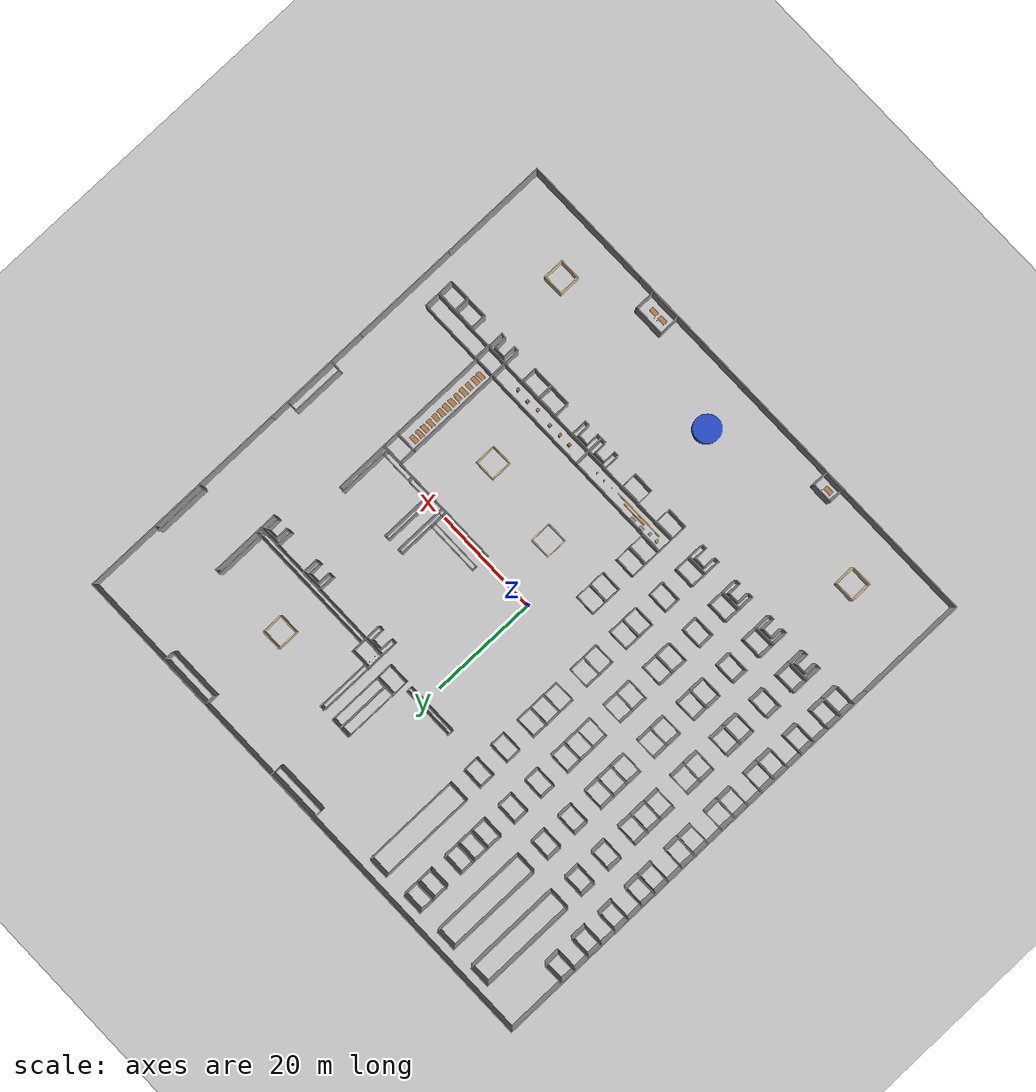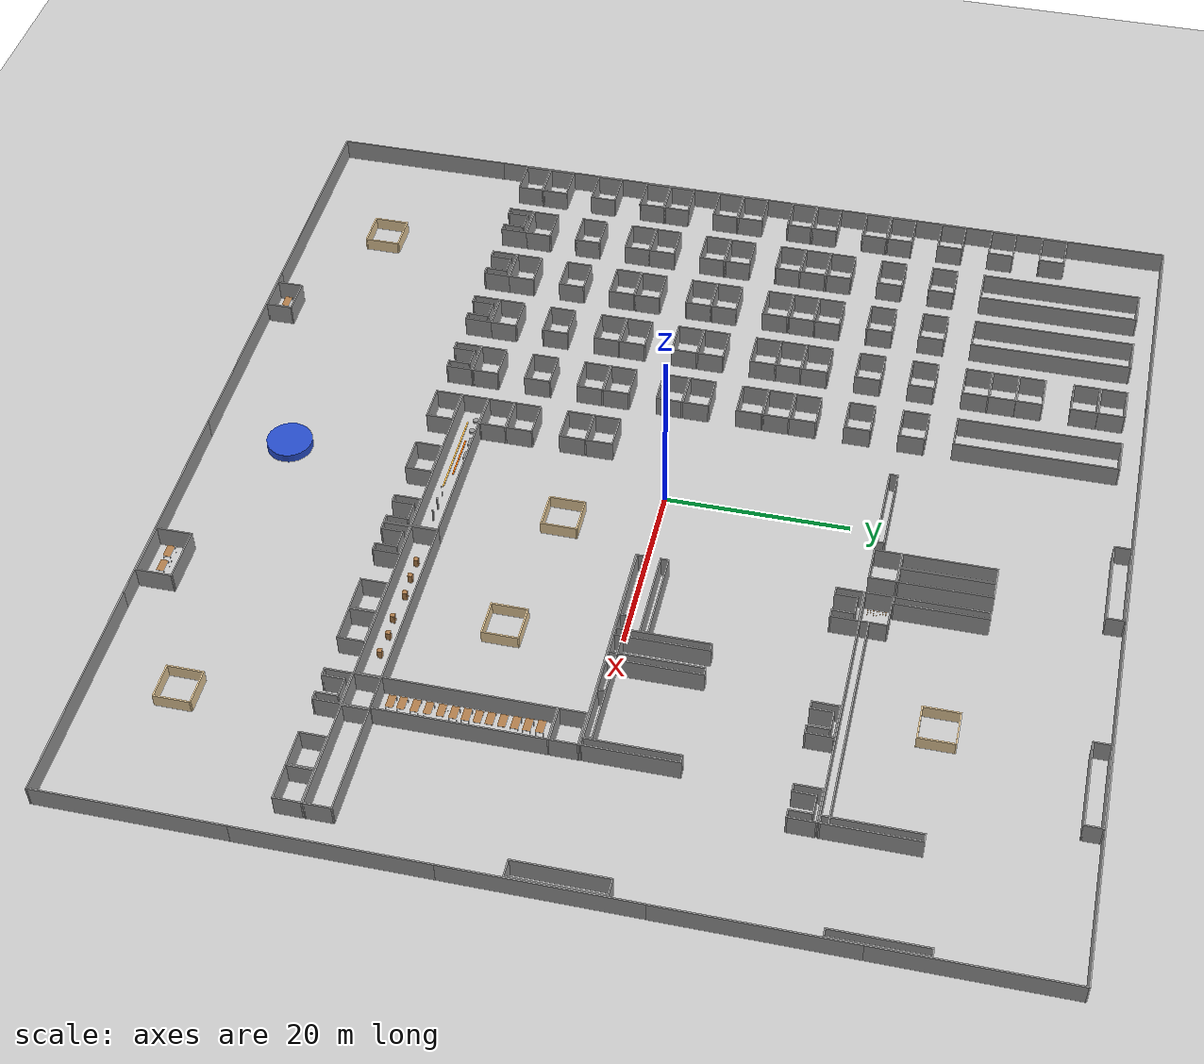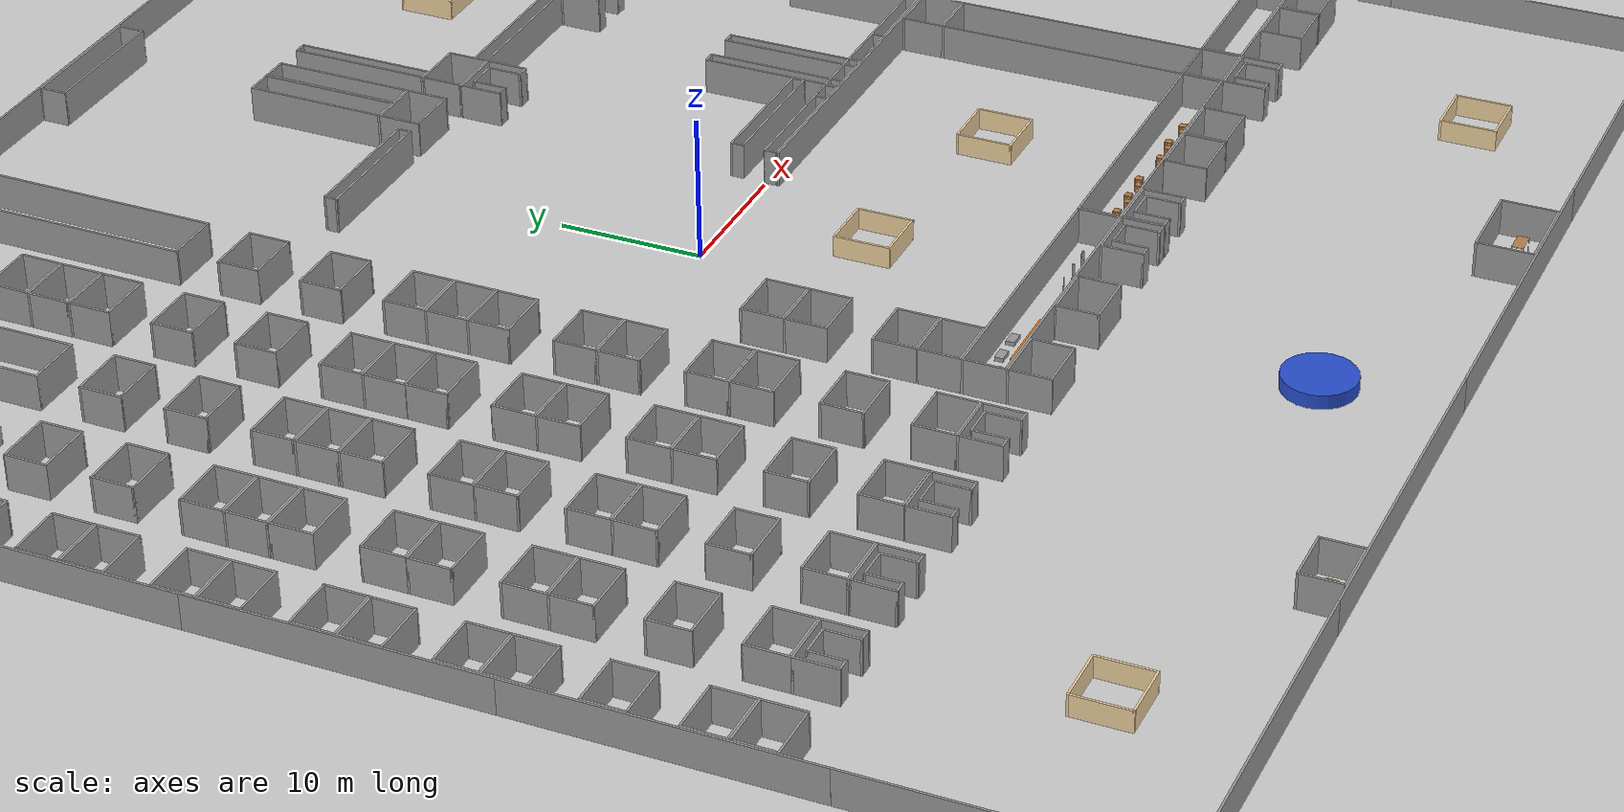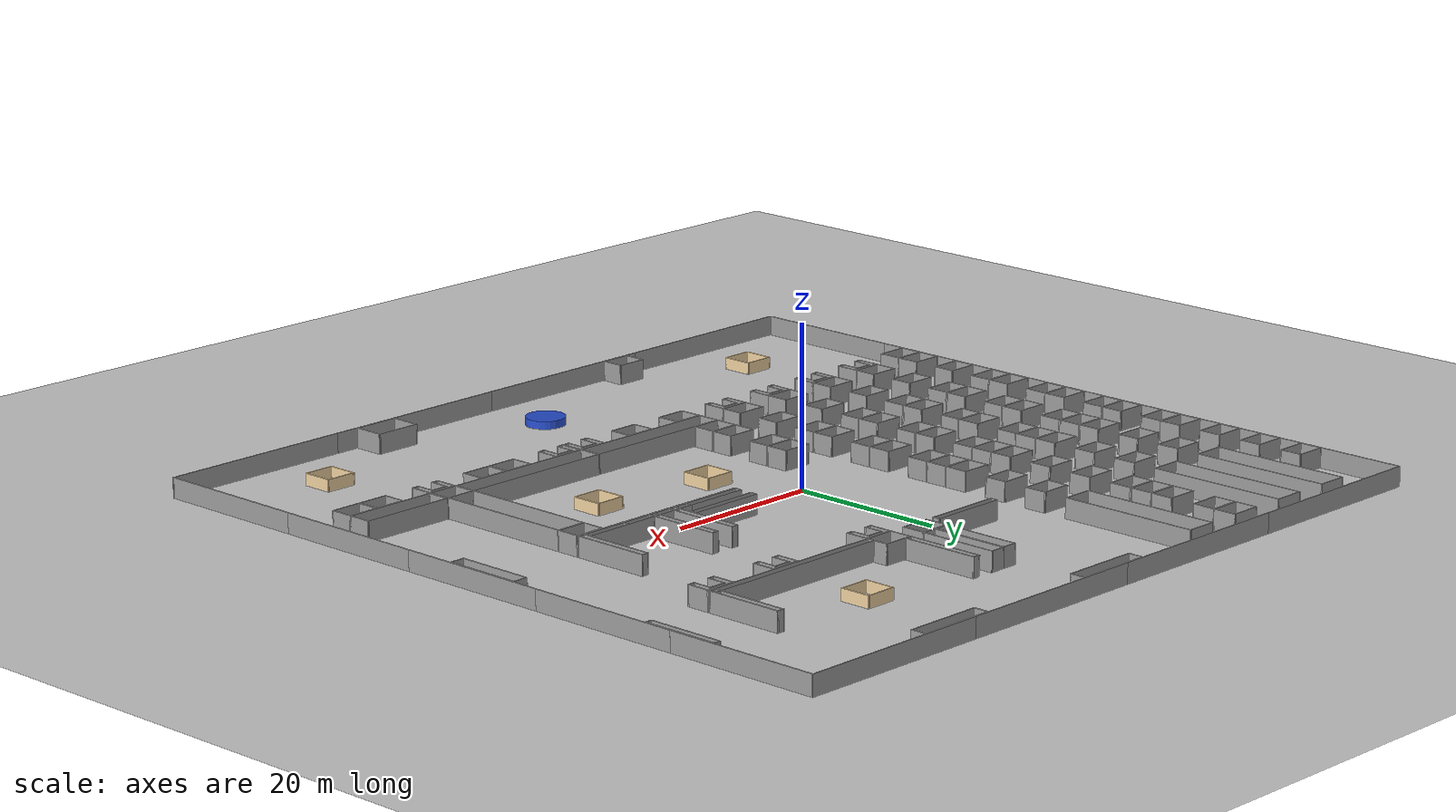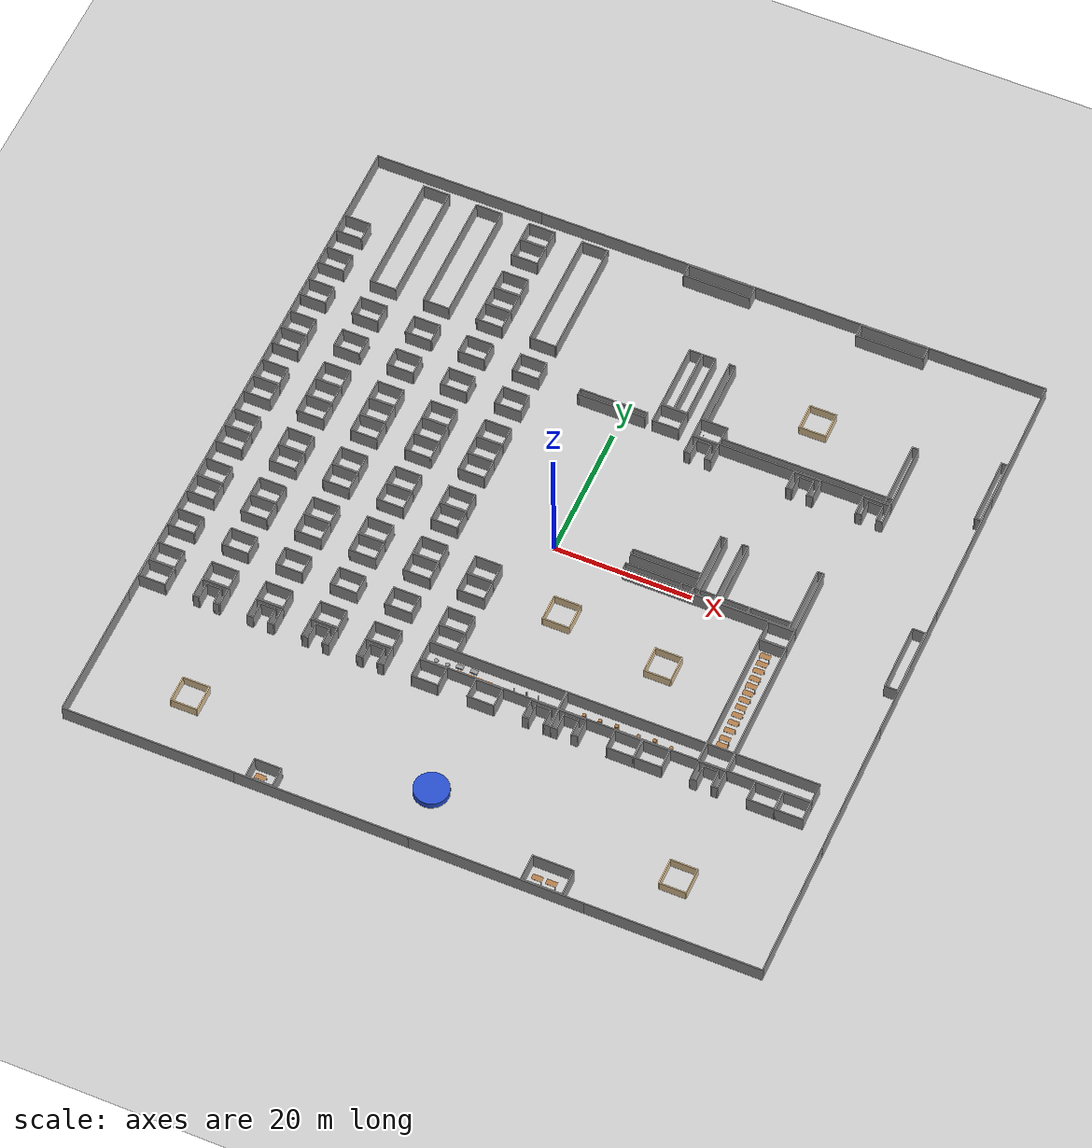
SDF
<sdf version="1.6">
 <world name="default">
  <light name="sun" type="directional">
   <pose>0 0 10 0 -0 0</pose>
   <diffuse>0.8 0.8 0.8 1</diffuse>
   <specular>0.2 0.2 0.2 1</specular>
   <attenuation>
    <range>1000</range>
    <constant>0.9</constant>
    <linear>0.01</linear>
    <quadratic>0.001</quadratic>
   </attenuation>
   <direction>-0.5 0.1 -0.9</direction>
  </light>
  <model name="ground_plane">
   <static>1</static>
   <link name="link">
    <collision name="collision">
     <geometry><plane><normal>0 0 1</normal><size>105 105</size></plane></geometry>
     <surface>
      <contact><collide_bitmask>65535</collide_bitmask></contact>
      <friction><ode><mu>100</mu><mu2>50</mu2></ode></friction>
     </surface>
    </collision>
    <visual name="visual">
     <cast_shadows>0</cast_shadows>
     <geometry><plane><normal>0 0 1</normal><size>105 105</size></plane></geometry>
     <material>
      <script><uri>file://media/materials/scripts/gazebo.material</uri><name>Gazebo/Grey</name></script>
     </material>
    </visual>
   </link>
  </model>
  <gravity>0 0 -9.8</gravity>
  <magnetic_field>6e-06 2.3e-05 -4.2e-05</magnetic_field>
  <atmosphere type="adiabatic"/>
  <physics name="default_physics" default="0" type="ode">
   <max_step_size>0.002</max_step_size>
   <real_time_factor>1</real_time_factor>
   <real_time_update_rate>500</real_time_update_rate>
  </physics>
  <scene><ambient>0.4 0.4 0.4 1</ambient><background>0.7 0.7 0.7 1</background><shadows>1</shadows></scene>
  <audio><device>default</device></audio>
  <spherical_coordinates>
   <surface_model>EARTH_WGS84</surface_model>
   <latitude_deg>0</latitude_deg>
   <longitude_deg>0</longitude_deg>
   <elevation>0</elevation>
   <heading_deg>0</heading_deg>
  </spherical_coordinates>
  <model name="wall_v20m">
   <pose>-48.4198 -20.7165 0 0 -0 0</pose>
   <link name="Wall_35">
    <collision name="Wall_35_Collision">
     <geometry><box><size>20 0.15 2.5</size></box></geometry>
     <pose>0 0 1.25 0 -0 0</pose>
    </collision>
    <visual name="Wall_35_Visual">
     <pose>0 0 1.25 0 -0 0</pose>
     <geometry><box><size>20 0.15 2.5</size></box></geometry>
     <material>
      <script><uri>file://media/materials/scripts/gazebo.material</uri><name>Gazebo/Grey</name></script>
      <ambient>1 1 1 1</ambient>
     </material>
     <meta><layer>0</layer></meta>
    </visual>
    <pose>0 -0 0 0 -0 -1.5708</pose>
   </link>
   <static>1</static>
  </model>
  <model name="wall_v20m_0">
   <pose>-48.4193 -0.726683 0 0 -0 0</pose>
   <link name="Wall_35">
    <collision name="Wall_35_Collision">
     <geometry><box><size>20 0.15 2.5</size></box></geometry>
     <pose>0 0 1.25 0 -0 0</pose>
    </collision>
    <visual name="Wall_35_Visual">
     <pose>0 0 1.25 0 -0 0</pose>
     <geometry><box><size>20 0.15 2.5</size></box></geometry>
     <material>
      <script><uri>file://media/materials/scripts/gazebo.material</uri><name>Gazebo/Grey</name></script>
      <ambient>1 1 1 1</ambient>
     </material>
     <meta><layer>0</layer></meta>
    </visual>
    <pose>0 -0 0 0 -0 -1.5708</pose>
   </link>
   <static>1</static>
  </model>
  <model name="wall_v20m_1">
   <pose>-48.4186 19.2715 0 0 -0 0</pose>
   <link name="Wall_35">
    <collision name="Wall_35_Collision">
     <geometry><box><size>20 0.15 2.5</size></box></geometry>
     <pose>0 0 1.25 0 -0 0</pose>
    </collision>
    <visual name="Wall_35_Visual">
     <pose>0 0 1.25 0 -0 0</pose>
     <geometry><box><size>20 0.15 2.5</size></box></geometry>
     <material>
      <script><uri>file://media/materials/scripts/gazebo.material</uri><name>Gazebo/Grey</name></script>
      <ambient>1 1 1 1</ambient>
     </material>
     <meta><layer>0</layer></meta>
    </visual>
    <pose>0 -0 0 0 -0 -1.5708</pose>
   </link>
   <static>1</static>
  </model>
  <model name="wall_v20m_2">
   <pose>-48.4188 39.2704 0 0 -0 0</pose>
   <link name="Wall_35">
    <collision name="Wall_35_Collision">
     <geometry><box><size>20 0.15 2.5</size></box></geometry>
     <pose>0 0 1.25 0 -0 0</pose>
    </collision>
    <visual name="Wall_35_Visual">
     <pose>0 0 1.25 0 -0 0</pose>
     <geometry><box><size>20 0.15 2.5</size></box></geometry>
     <material>
      <script><uri>file://media/materials/scripts/gazebo.material</uri><name>Gazebo/Grey</name></script>
      <ambient>1 1 1 1</ambient>
     </material>
     <meta><layer>0</layer></meta>
    </visual>
    <pose>0 -0 0 0 -0 -1.5708</pose>
   </link>
   <static>1</static>
  </model>
  <model name="wall_25m_3">
   <pose>-35.9923 49.3467 0 0 -0 0</pose>
   <link name="Wall_28">
    <collision name="Wall_28_Collision">
     <geometry><box><size>25 0.15 2.5</size></box></geometry>
     <pose>0 0 1.25 0 -0 0</pose>
    </collision>
    <visual name="Wall_28_Visual">
     <pose>0 0 1.25 0 -0 0</pose>
     <geometry><box><size>25 0.15 2.5</size></box></geometry>
     <material>
      <script><uri>file://media/materials/scripts/gazebo.material</uri><name>Gazebo/Grey</name></script>
      <ambient>1 1 1 1</ambient>
     </material>
     <meta><layer>0</layer></meta>
    </visual>
   </link>
   <static>1</static>
  </model>
  <model name="wall_25m_4">
   <pose>-10.9942 49.3463 0 0 -0 0</pose>
   <link name="Wall_28">
    <collision name="Wall_28_Collision">
     <geometry><box><size>25 0.15 2.5</size></box></geometry>
     <pose>0 0 1.25 0 -0 0</pose>
    </collision>
    <visual name="Wall_28_Visual">
     <pose>0 0 1.25 0 -0 0</pose>
     <geometry><box><size>25 0.15 2.5</size></box></geometry>
     <material>
      <script><uri>file://media/materials/scripts/gazebo.material</uri><name>Gazebo/Grey</name></script>
      <ambient>1 1 1 1</ambient>
     </material>
     <meta><layer>0</layer></meta>
    </visual>
   </link>
   <static>1</static>
  </model>
  <model name="wall_25m_5">
   <pose>14.0033 49.3464 0 0 -0 0</pose>
   <link name="Wall_28">
    <collision name="Wall_28_Collision">
     <geometry><box><size>25 0.15 2.5</size></box></geometry>
     <pose>0 0 1.25 0 -0 0</pose>
    </collision>
    <visual name="Wall_28_Visual">
     <pose>0 0 1.25 0 -0 0</pose>
     <geometry><box><size>25 0.15 2.5</size></box></geometry>
     <material>
      <script><uri>file://media/materials/scripts/gazebo.material</uri><name>Gazebo/Grey</name></script>
      <ambient>1 1 1 1</ambient>
     </material>
     <meta><layer>0</layer></meta>
    </visual>
   </link>
   <static>1</static>
  </model>
  <model name="wall_25m_6">
   <pose>39.0043 49.3458 0 0 -0 0</pose>
   <link name="Wall_28">
    <collision name="Wall_28_Collision">
     <geometry><box><size>25 0.15 2.5</size></box></geometry>
     <pose>0 0 1.25 0 -0 0</pose>
    </collision>
    <visual name="Wall_28_Visual">
     <pose>0 0 1.25 0 -0 0</pose>
     <geometry><box><size>25 0.15 2.5</size></box></geometry>
     <material>
      <script><uri>file://media/materials/scripts/gazebo.material</uri><name>Gazebo/Grey</name></script>
      <ambient>1 1 1 1</ambient>
     </material>
     <meta><layer>0</layer></meta>
    </visual>
   </link>
   <static>1</static>
  </model>
  <model name="wall_v20m_3">
   <pose>51.4198 -20.719 0 0 -0 0</pose>
   <link name="Wall_35">
    <collision name="Wall_35_Collision">
     <geometry><box><size>20 0.15 2.5</size></box></geometry>
     <pose>0 0 1.25 0 -0 0</pose>
    </collision>
    <visual name="Wall_35_Visual">
     <pose>0 0 1.25 0 -0 0</pose>
     <geometry><box><size>20 0.15 2.5</size></box></geometry>
     <material>
      <script><uri>file://media/materials/scripts/gazebo.material</uri><name>Gazebo/Grey</name></script>
      <ambient>1 1 1 1</ambient>
     </material>
     <meta><layer>0</layer></meta>
    </visual>
    <pose>0 -0 0 0 -0 -1.5708</pose>
   </link>
   <static>1</static>
  </model>
  <model name="wall_v20m_4">
   <pose>51.4193 -0.729847 0 0 -0 0</pose>
   <link name="Wall_35">
    <collision name="Wall_35_Collision">
     <geometry><box><size>20 0.15 2.5</size></box></geometry>
     <pose>0 0 1.25 0 -0 0</pose>
    </collision>
    <visual name="Wall_35_Visual">
     <pose>0 0 1.25 0 -0 0</pose>
     <geometry><box><size>20 0.15 2.5</size></box></geometry>
     <material>
      <script><uri>file://media/materials/scripts/gazebo.material</uri><name>Gazebo/Grey</name></script>
      <ambient>1 1 1 1</ambient>
     </material>
     <meta><layer>0</layer></meta>
    </visual>
    <pose>0 -0 0 0 -0 -1.5708</pose>
   </link>
   <static>1</static>
  </model>
  <model name="wall_v20m_5">
   <pose>51.4329 19.2752 0 0 -0 0</pose>
   <link name="Wall_35">
    <collision name="Wall_35_Collision">
     <geometry><box><size>20 0.15 2.5</size></box></geometry>
     <pose>0 0 1.25 0 -0 0</pose>
    </collision>
    <visual name="Wall_35_Visual">
     <pose>0 0 1.25 0 -0 0</pose>
     <geometry><box><size>20 0.15 2.5</size></box></geometry>
     <material>
      <script><uri>file://media/materials/scripts/gazebo.material</uri><name>Gazebo/Grey</name></script>
      <ambient>1 1 1 1</ambient>
     </material>
     <meta><layer>0</layer></meta>
    </visual>
    <pose>0 -0 0 0 -0 -1.5708</pose>
   </link>
   <static>1</static>
  </model>
  <model name="wall_v20m_6">
   <pose>51.4317 39.2751 0 0 -0 0</pose>
   <link name="Wall_35">
    <collision name="Wall_35_Collision">
     <geometry><box><size>20 0.15 2.5</size></box></geometry>
     <pose>0 0 1.25 0 -0 0</pose>
    </collision>
    <visual name="Wall_35_Visual">
     <pose>0 0 1.25 0 -0 0</pose>
     <geometry><box><size>20 0.15 2.5</size></box></geometry>
     <material>
      <script><uri>file://media/materials/scripts/gazebo.material</uri><name>Gazebo/Grey</name></script>
      <ambient>1 1 1 1</ambient>
     </material>
     <meta><layer>0</layer></meta>
    </visual>
    <pose>0 -0 0 0 -0 -1.5708</pose>
   </link>
   <static>1</static>
  </model>
  <model name="base3x4_26">
   <pose>-46.3516 -23.2162 0 0 -0 0</pose>
   <link name="Wall_18">
    <collision name="Wall_18_Collision">
     <geometry><box><size>3 0.15 2.5</size></box></geometry>
     <pose>0 0 1.25 0 -0 0</pose>
    </collision>
    <visual name="Wall_18_Visual">
     <pose>0 0 1.25 0 -0 0</pose>
     <geometry><box><size>3 0.15 2.5</size></box></geometry>
     <material>
      <script><uri>file://media/materials/scripts/gazebo.material</uri><name>Gazebo/Grey</name></script>
      <ambient>1 1 1 1</ambient>
     </material>
     <meta><layer>0</layer></meta>
    </visual>
    <pose>-1.925 -0 0 0 -0 -1.5708</pose>
   </link>
   <link name="Wall_19">
    <collision name="Wall_19_Collision">
     <geometry><box><size>4 0.15 2.5</size></box></geometry>
     <pose>0 0 1.25 0 -0 0</pose>
    </collision>
    <visual name="Wall_19_Visual">
     <pose>0 0 1.25 0 -0 0</pose>
     <geometry><box><size>4 0.15 2.5</size></box></geometry>
     <material>
      <script><uri>file://media/materials/scripts/gazebo.material</uri><name>Gazebo/Grey</name></script>
      <ambient>1 1 1 1</ambient>
     </material>
     <meta><layer>0</layer></meta>
    </visual>
    <pose>-0 -1.425 0 0 -0 0</pose>
   </link>
   <link name="Wall_20">
    <collision name="Wall_20_Collision">
     <geometry><box><size>3 0.15 2.5</size></box></geometry>
     <pose>0 0 1.25 0 -0 0</pose>
    </collision>
    <visual name="Wall_20_Visual">
     <pose>0 0 1.25 0 -0 0</pose>
     <geometry><box><size>3 0.15 2.5</size></box></geometry>
     <material>
      <script><uri>file://media/materials/scripts/gazebo.material</uri><name>Gazebo/Grey</name></script>
      <ambient>1 1 1 1</ambient>
     </material>
     <meta><layer>0</layer></meta>
    </visual>
    <pose>1.925 -0 0 0 -0 1.5708</pose>
   </link>
   <link name="Wall_21">
    <collision name="Wall_21_Collision">
     <geometry><box><size>4 0.15 2.5</size></box></geometry>
     <pose>0 0 1.25 0 -0 0</pose>
    </collision>
    <visual name="Wall_21_Visual">
     <pose>0 0 1.25 0 -0 0</pose>
     <geometry><box><size>4 0.15 2.5</size></box></geometry>
     <material>
      <script><uri>file://media/materials/scripts/gazebo.material</uri><name>Gazebo/Grey</name></script>
      <ambient>1 1 1 1</ambient>
     </material>
     <meta><layer>0</layer></meta>
    </visual>
    <pose>-0 1.425 0 0 -0 3.14159</pose>
   </link>
   <static>1</static>
  </model>
  <model name="base3x4_28">
   <pose>-46.3508 -17.215 0 0 -0 0</pose>
   <link name="Wall_18">
    <collision name="Wall_18_Collision">
     <geometry><box><size>3 0.15 2.5</size></box></geometry>
     <pose>0 0 1.25 0 -0 0</pose>
    </collision>
    <visual name="Wall_18_Visual">
     <pose>0 0 1.25 0 -0 0</pose>
     <geometry><box><size>3 0.15 2.5</size></box></geometry>
     <material>
      <script><uri>file://media/materials/scripts/gazebo.material</uri><name>Gazebo/Grey</name></script>
      <ambient>1 1 1 1</ambient>
     </material>
     <meta><layer>0</layer></meta>
    </visual>
    <pose>-1.925 -0 0 0 -0 -1.5708</pose>
   </link>
   <link name="Wall_19">
    <collision name="Wall_19_Collision">
     <geometry><box><size>4 0.15 2.5</size></box></geometry>
     <pose>0 0 1.25 0 -0 0</pose>
    </collision>
    <visual name="Wall_19_Visual">
     <pose>0 0 1.25 0 -0 0</pose>
     <geometry><box><size>4 0.15 2.5</size></box></geometry>
     <material>
      <script><uri>file://media/materials/scripts/gazebo.material</uri><name>Gazebo/Grey</name></script>
      <ambient>1 1 1 1</ambient>
     </material>
     <meta><layer>0</layer></meta>
    </visual>
    <pose>-0 -1.425 0 0 -0 0</pose>
   </link>
   <link name="Wall_20">
    <collision name="Wall_20_Collision">
     <geometry><box><size>3 0.15 2.5</size></box></geometry>
     <pose>0 0 1.25 0 -0 0</pose>
    </collision>
    <visual name="Wall_20_Visual">
     <pose>0 0 1.25 0 -0 0</pose>
     <geometry><box><size>3 0.15 2.5</size></box></geometry>
     <material>
      <script><uri>file://media/materials/scripts/gazebo.material</uri><name>Gazebo/Grey</name></script>
      <ambient>1 1 1 1</ambient>
     </material>
     <meta><layer>0</layer></meta>
    </visual>
    <pose>1.925 -0 0 0 -0 1.5708</pose>
   </link>
   <link name="Wall_21">
    <collision name="Wall_21_Collision">
     <geometry><box><size>4 0.15 2.5</size></box></geometry>
     <pose>0 0 1.25 0 -0 0</pose>
    </collision>
    <visual name="Wall_21_Visual">
     <pose>0 0 1.25 0 -0 0</pose>
     <geometry><box><size>4 0.15 2.5</size></box></geometry>
     <material>
      <script><uri>file://media/materials/scripts/gazebo.material</uri><name>Gazebo/Grey</name></script>
      <ambient>1 1 1 1</ambient>
     </material>
     <meta><layer>0</layer></meta>
    </visual>
    <pose>-0 1.425 0 0 -0 3.14159</pose>
   </link>
   <static>1</static>
  </model>
  <model name="base3x4_34">
   <pose>-38.3558 -23.2346 0 0 -0 0</pose>
   <link name="Wall_18">
    <collision name="Wall_18_Collision">
     <geometry><box><size>3 0.15 2.5</size></box></geometry>
     <pose>0 0 1.25 0 -0 0</pose>
    </collision>
    <visual name="Wall_18_Visual">
     <pose>0 0 1.25 0 -0 0</pose>
     <geometry><box><size>3 0.15 2.5</size></box></geometry>
     <material>
      <script><uri>file://media/materials/scripts/gazebo.material</uri><name>Gazebo/Grey</name></script>
      <ambient>1 1 1 1</ambient>
     </material>
     <meta><layer>0</layer></meta>
    </visual>
    <pose>-1.925 -0 0 0 -0 -1.5708</pose>
   </link>
   <link name="Wall_19">
    <collision name="Wall_19_Collision">
     <geometry><box><size>4 0.15 2.5</size></box></geometry>
     <pose>0 0 1.25 0 -0 0</pose>
    </collision>
    <visual name="Wall_19_Visual">
     <pose>0 0 1.25 0 -0 0</pose>
     <geometry><box><size>4 0.15 2.5</size></box></geometry>
     <material>
      <script><uri>file://media/materials/scripts/gazebo.material</uri><name>Gazebo/Grey</name></script>
      <ambient>1 1 1 1</ambient>
     </material>
     <meta><layer>0</layer></meta>
    </visual>
    <pose>-0 -1.425 0 0 -0 0</pose>
   </link>
   <link name="Wall_20">
    <collision name="Wall_20_Collision">
     <geometry><box><size>3 0.15 2.5</size></box></geometry>
     <pose>0 0 1.25 0 -0 0</pose>
    </collision>
    <visual name="Wall_20_Visual">
     <pose>0 0 1.25 0 -0 0</pose>
     <geometry><box><size>3 0.15 2.5</size></box></geometry>
     <material>
      <script><uri>file://media/materials/scripts/gazebo.material</uri><name>Gazebo/Grey</name></script>
      <ambient>1 1 1 1</ambient>
     </material>
     <meta><layer>0</layer></meta>
    </visual>
    <pose>1.925 -0 0 0 -0 1.5708</pose>
   </link>
   <link name="Wall_21">
    <collision name="Wall_21_Collision">
     <geometry><box><size>4 0.15 2.5</size></box></geometry>
     <pose>0 0 1.25 0 -0 0</pose>
    </collision>
    <visual name="Wall_21_Visual">
     <pose>0 0 1.25 0 -0 0</pose>
     <geometry><box><size>4 0.15 2.5</size></box></geometry>
     <material>
      <script><uri>file://media/materials/scripts/gazebo.material</uri><name>Gazebo/Grey</name></script>
      <ambient>1 1 1 1</ambient>
     </material>
     <meta><layer>0</layer></meta>
    </visual>
    <pose>-0 1.425 0 0 -0 3.14159</pose>
   </link>
   <static>1</static>
  </model>
  <model name="base3x4_36">
   <pose>-38.357 -17.2543 0 0 -0 0</pose>
   <link name="Wall_18">
    <collision name="Wall_18_Collision">
     <geometry><box><size>3 0.15 2.5</size></box></geometry>
     <pose>0 0 1.25 0 -0 0</pose>
    </collision>
    <visual name="Wall_18_Visual">
     <pose>0 0 1.25 0 -0 0</pose>
     <geometry><box><size>3 0.15 2.5</size></box></geometry>
     <material>
      <script><uri>file://media/materials/scripts/gazebo.material</uri><name>Gazebo/Grey</name></script>
      <ambient>1 1 1 1</ambient>
     </material>
     <meta><layer>0</layer></meta>
    </visual>
    <pose>-1.925 -0 0 0 -0 -1.5708</pose>
   </link>
   <link name="Wall_19">
    <collision name="Wall_19_Collision">
     <geometry><box><size>4 0.15 2.5</size></box></geometry>
     <pose>0 0 1.25 0 -0 0</pose>
    </collision>
    <visual name="Wall_19_Visual">
     <pose>0 0 1.25 0 -0 0</pose>
     <geometry><box><size>4 0.15 2.5</size></box></geometry>
     <material>
      <script><uri>file://media/materials/scripts/gazebo.material</uri><name>Gazebo/Grey</name></script>
      <ambient>1 1 1 1</ambient>
     </material>
     <meta><layer>0</layer></meta>
    </visual>
    <pose>-0 -1.425 0 0 -0 0</pose>
   </link>
   <link name="Wall_20">
    <collision name="Wall_20_Collision">
     <geometry><box><size>3 0.15 2.5</size></box></geometry>
     <pose>0 0 1.25 0 -0 0</pose>
    </collision>
    <visual name="Wall_20_Visual">
     <pose>0 0 1.25 0 -0 0</pose>
     <geometry><box><size>3 0.15 2.5</size></box></geometry>
     <material>
      <script><uri>file://media/materials/scripts/gazebo.material</uri><name>Gazebo/Grey</name></script>
      <ambient>1 1 1 1</ambient>
     </material>
     <meta><layer>0</layer></meta>
    </visual>
    <pose>1.925 -0 0 0 -0 1.5708</pose>
   </link>
   <link name="Wall_21">
    <collision name="Wall_21_Collision">
     <geometry><box><size>4 0.15 2.5</size></box></geometry>
     <pose>0 0 1.25 0 -0 0</pose>
    </collision>
    <visual name="Wall_21_Visual">
     <pose>0 0 1.25 0 -0 0</pose>
     <geometry><box><size>4 0.15 2.5</size></box></geometry>
     <material>
      <script><uri>file://media/materials/scripts/gazebo.material</uri><name>Gazebo/Grey</name></script>
      <ambient>1 1 1 1</ambient>
     </material>
     <meta><layer>0</layer></meta>
    </visual>
    <pose>-0 1.425 0 0 -0 3.14159</pose>
   </link>
   <static>1</static>
  </model>
  <model name="base3x4_31">
   <pose>-30.4046 -23.2308 0 0 -0 0</pose>
   <link name="Wall_18">
    <collision name="Wall_18_Collision">
     <geometry><box><size>3 0.15 2.5</size></box></geometry>
     <pose>0 0 1.25 0 -0 0</pose>
    </collision>
    <visual name="Wall_18_Visual">
     <pose>0 0 1.25 0 -0 0</pose>
     <geometry><box><size>3 0.15 2.5</size></box></geometry>
     <material>
      <script><uri>file://media/materials/scripts/gazebo.material</uri><name>Gazebo/Grey</name></script>
      <ambient>1 1 1 1</ambient>
     </material>
     <meta><layer>0</layer></meta>
    </visual>
    <pose>-1.925 -0 0 0 -0 -1.5708</pose>
   </link>
   <link name="Wall_19">
    <collision name="Wall_19_Collision">
     <geometry><box><size>4 0.15 2.5</size></box></geometry>
     <pose>0 0 1.25 0 -0 0</pose>
    </collision>
    <visual name="Wall_19_Visual">
     <pose>0 0 1.25 0 -0 0</pose>
     <geometry><box><size>4 0.15 2.5</size></box></geometry>
     <material>
      <script><uri>file://media/materials/scripts/gazebo.material</uri><name>Gazebo/Grey</name></script>
      <ambient>1 1 1 1</ambient>
     </material>
     <meta><layer>0</layer></meta>
    </visual>
    <pose>-0 -1.425 0 0 -0 0</pose>
   </link>
   <link name="Wall_20">
    <collision name="Wall_20_Collision">
     <geometry><box><size>3 0.15 2.5</size></box></geometry>
     <pose>0 0 1.25 0 -0 0</pose>
    </collision>
    <visual name="Wall_20_Visual">
     <pose>0 0 1.25 0 -0 0</pose>
     <geometry><box><size>3 0.15 2.5</size></box></geometry>
     <material>
      <script><uri>file://media/materials/scripts/gazebo.material</uri><name>Gazebo/Grey</name></script>
      <ambient>1 1 1 1</ambient>
     </material>
     <meta><layer>0</layer></meta>
    </visual>
    <pose>1.925 -0 0 0 -0 1.5708</pose>
   </link>
   <link name="Wall_21">
    <collision name="Wall_21_Collision">
     <geometry><box><size>4 0.15 2.5</size></box></geometry>
     <pose>0 0 1.25 0 -0 0</pose>
    </collision>
    <visual name="Wall_21_Visual">
     <pose>0 0 1.25 0 -0 0</pose>
     <geometry><box><size>4 0.15 2.5</size></box></geometry>
     <material>
      <script><uri>file://media/materials/scripts/gazebo.material</uri><name>Gazebo/Grey</name></script>
      <ambient>1 1 1 1</ambient>
     </material>
     <meta><layer>0</layer></meta>
    </visual>
    <pose>-0 1.425 0 0 -0 3.14159</pose>
   </link>
   <static>1</static>
  </model>
  <model name="base3x4_33">
   <pose>-30.4092 -17.2319 0 0 -0 0</pose>
   <link name="Wall_18">
    <collision name="Wall_18_Collision">
     <geometry><box><size>3 0.15 2.5</size></box></geometry>
     <pose>0 0 1.25 0 -0 0</pose>
    </collision>
    <visual name="Wall_18_Visual">
     <pose>0 0 1.25 0 -0 0</pose>
     <geometry><box><size>3 0.15 2.5</size></box></geometry>
     <material>
      <script><uri>file://media/materials/scripts/gazebo.material</uri><name>Gazebo/Grey</name></script>
      <ambient>1 1 1 1</ambient>
     </material>
     <meta><layer>0</layer></meta>
    </visual>
    <pose>-1.925 -0 0 0 -0 -1.5708</pose>
   </link>
   <link name="Wall_19">
    <collision name="Wall_19_Collision">
     <geometry><box><size>4 0.15 2.5</size></box></geometry>
     <pose>0 0 1.25 0 -0 0</pose>
    </collision>
    <visual name="Wall_19_Visual">
     <pose>0 0 1.25 0 -0 0</pose>
     <geometry><box><size>4 0.15 2.5</size></box></geometry>
     <material>
      <script><uri>file://media/materials/scripts/gazebo.material</uri><name>Gazebo/Grey</name></script>
      <ambient>1 1 1 1</ambient>
     </material>
     <meta><layer>0</layer></meta>
    </visual>
    <pose>-0 -1.425 0 0 -0 0</pose>
   </link>
   <link name="Wall_20">
    <collision name="Wall_20_Collision">
     <geometry><box><size>3 0.15 2.5</size></box></geometry>
     <pose>0 0 1.25 0 -0 0</pose>
    </collision>
    <visual name="Wall_20_Visual">
     <pose>0 0 1.25 0 -0 0</pose>
     <geometry><box><size>3 0.15 2.5</size></box></geometry>
     <material>
      <script><uri>file://media/materials/scripts/gazebo.material</uri><name>Gazebo/Grey</name></script>
      <ambient>1 1 1 1</ambient>
     </material>
     <meta><layer>0</layer></meta>
    </visual>
    <pose>1.925 -0 0 0 -0 1.5708</pose>
   </link>
   <link name="Wall_21">
    <collision name="Wall_21_Collision">
     <geometry><box><size>4 0.15 2.5</size></box></geometry>
     <pose>0 0 1.25 0 -0 0</pose>
    </collision>
    <visual name="Wall_21_Visual">
     <pose>0 0 1.25 0 -0 0</pose>
     <geometry><box><size>4 0.15 2.5</size></box></geometry>
     <material>
      <script><uri>file://media/materials/scripts/gazebo.material</uri><name>Gazebo/Grey</name></script>
      <ambient>1 1 1 1</ambient>
     </material>
     <meta><layer>0</layer></meta>
    </visual>
    <pose>-0 1.425 0 0 -0 3.14159</pose>
   </link>
   <static>1</static>
  </model>
  <model name="base3x4_39">
   <pose>-46.3493 -11.2283 0 0 -0 0</pose>
   <link name="Wall_18">
    <collision name="Wall_18_Collision">
     <geometry><box><size>3 0.15 2.5</size></box></geometry>
     <pose>0 0 1.25 0 -0 0</pose>
    </collision>
    <visual name="Wall_18_Visual">
     <pose>0 0 1.25 0 -0 0</pose>
     <geometry><box><size>3 0.15 2.5</size></box></geometry>
     <material>
      <script><uri>file://media/materials/scripts/gazebo.material</uri><name>Gazebo/Grey</name></script>
      <ambient>1 1 1 1</ambient>
     </material>
     <meta><layer>0</layer></meta>
    </visual>
    <pose>-1.925 -0 0 0 -0 -1.5708</pose>
   </link>
   <link name="Wall_19">
    <collision name="Wall_19_Collision">
     <geometry><box><size>4 0.15 2.5</size></box></geometry>
     <pose>0 0 1.25 0 -0 0</pose>
    </collision>
    <visual name="Wall_19_Visual">
     <pose>0 0 1.25 0 -0 0</pose>
     <geometry><box><size>4 0.15 2.5</size></box></geometry>
     <material>
      <script><uri>file://media/materials/scripts/gazebo.material</uri><name>Gazebo/Grey</name></script>
      <ambient>1 1 1 1</ambient>
     </material>
     <meta><layer>0</layer></meta>
    </visual>
    <pose>-0 -1.425 0 0 -0 0</pose>
   </link>
   <link name="Wall_20">
    <collision name="Wall_20_Collision">
     <geometry><box><size>3 0.15 2.5</size></box></geometry>
     <pose>0 0 1.25 0 -0 0</pose>
    </collision>
    <visual name="Wall_20_Visual">
     <pose>0 0 1.25 0 -0 0</pose>
     <geometry><box><size>3 0.15 2.5</size></box></geometry>
     <material>
      <script><uri>file://media/materials/scripts/gazebo.material</uri><name>Gazebo/Grey</name></script>
      <ambient>1 1 1 1</ambient>
     </material>
     <meta><layer>0</layer></meta>
    </visual>
    <pose>1.925 -0 0 0 -0 1.5708</pose>
   </link>
   <link name="Wall_21">
    <collision name="Wall_21_Collision">
     <geometry><box><size>4 0.15 2.5</size></box></geometry>
     <pose>0 0 1.25 0 -0 0</pose>
    </collision>
    <visual name="Wall_21_Visual">
     <pose>0 0 1.25 0 -0 0</pose>
     <geometry><box><size>4 0.15 2.5</size></box></geometry>
     <material>
      <script><uri>file://media/materials/scripts/gazebo.material</uri><name>Gazebo/Grey</name></script>
      <ambient>1 1 1 1</ambient>
     </material>
     <meta><layer>0</layer></meta>
    </visual>
    <pose>-0 1.425 0 0 -0 3.14159</pose>
   </link>
   <static>1</static>
  </model>
  <model name="base3x4_40">
   <pose>-46.3508 -8.23033 0 0 -0 0</pose>
   <link name="Wall_18">
    <collision name="Wall_18_Collision">
     <geometry><box><size>3 0.15 2.5</size></box></geometry>
     <pose>0 0 1.25 0 -0 0</pose>
    </collision>
    <visual name="Wall_18_Visual">
     <pose>0 0 1.25 0 -0 0</pose>
     <geometry><box><size>3 0.15 2.5</size></box></geometry>
     <material>
      <script><uri>file://media/materials/scripts/gazebo.material</uri><name>Gazebo/Grey</name></script>
      <ambient>1 1 1 1</ambient>
     </material>
     <meta><layer>0</layer></meta>
    </visual>
    <pose>-1.925 -0 0 0 -0 -1.5708</pose>
   </link>
   <link name="Wall_19">
    <collision name="Wall_19_Collision">
     <geometry><box><size>4 0.15 2.5</size></box></geometry>
     <pose>0 0 1.25 0 -0 0</pose>
    </collision>
    <visual name="Wall_19_Visual">
     <pose>0 0 1.25 0 -0 0</pose>
     <geometry><box><size>4 0.15 2.5</size></box></geometry>
     <material>
      <script><uri>file://media/materials/scripts/gazebo.material</uri><name>Gazebo/Grey</name></script>
      <ambient>1 1 1 1</ambient>
     </material>
     <meta><layer>0</layer></meta>
    </visual>
    <pose>-0 -1.425 0 0 -0 0</pose>
   </link>
   <link name="Wall_20">
    <collision name="Wall_20_Collision">
     <geometry><box><size>3 0.15 2.5</size></box></geometry>
     <pose>0 0 1.25 0 -0 0</pose>
    </collision>
    <visual name="Wall_20_Visual">
     <pose>0 0 1.25 0 -0 0</pose>
     <geometry><box><size>3 0.15 2.5</size></box></geometry>
     <material>
      <script><uri>file://media/materials/scripts/gazebo.material</uri><name>Gazebo/Grey</name></script>
      <ambient>1 1 1 1</ambient>
     </material>
     <meta><layer>0</layer></meta>
    </visual>
    <pose>1.925 -0 0 0 -0 1.5708</pose>
   </link>
   <link name="Wall_21">
    <collision name="Wall_21_Collision">
     <geometry><box><size>4 0.15 2.5</size></box></geometry>
     <pose>0 0 1.25 0 -0 0</pose>
    </collision>
    <visual name="Wall_21_Visual">
     <pose>0 0 1.25 0 -0 0</pose>
     <geometry><box><size>4 0.15 2.5</size></box></geometry>
     <material>
      <script><uri>file://media/materials/scripts/gazebo.material</uri><name>Gazebo/Grey</name></script>
      <ambient>1 1 1 1</ambient>
     </material>
     <meta><layer>0</layer></meta>
    </visual>
    <pose>-0 1.425 0 0 -0 3.14159</pose>
   </link>
   <static>1</static>
  </model>
  <model name="base3x4_42">
   <pose>-46.3729 -2.24361 0 0 -0 0</pose>
   <link name="Wall_18">
    <collision name="Wall_18_Collision">
     <geometry><box><size>3 0.15 2.5</size></box></geometry>
     <pose>0 0 1.25 0 -0 0</pose>
    </collision>
    <visual name="Wall_18_Visual">
     <pose>0 0 1.25 0 -0 0</pose>
     <geometry><box><size>3 0.15 2.5</size></box></geometry>
     <material>
      <script><uri>file://media/materials/scripts/gazebo.material</uri><name>Gazebo/Grey</name></script>
      <ambient>1 1 1 1</ambient>
     </material>
     <meta><layer>0</layer></meta>
    </visual>
    <pose>-1.925 -0 0 0 -0 -1.5708</pose>
   </link>
   <link name="Wall_19">
    <collision name="Wall_19_Collision">
     <geometry><box><size>4 0.15 2.5</size></box></geometry>
     <pose>0 0 1.25 0 -0 0</pose>
    </collision>
    <visual name="Wall_19_Visual">
     <pose>0 0 1.25 0 -0 0</pose>
     <geometry><box><size>4 0.15 2.5</size></box></geometry>
     <material>
      <script><uri>file://media/materials/scripts/gazebo.material</uri><name>Gazebo/Grey</name></script>
      <ambient>1 1 1 1</ambient>
     </material>
     <meta><layer>0</layer></meta>
    </visual>
    <pose>-0 -1.425 0 0 -0 0</pose>
   </link>
   <link name="Wall_20">
    <collision name="Wall_20_Collision">
     <geometry><box><size>3 0.15 2.5</size></box></geometry>
     <pose>0 0 1.25 0 -0 0</pose>
    </collision>
    <visual name="Wall_20_Visual">
     <pose>0 0 1.25 0 -0 0</pose>
     <geometry><box><size>3 0.15 2.5</size></box></geometry>
     <material>
      <script><uri>file://media/materials/scripts/gazebo.material</uri><name>Gazebo/Grey</name></script>
      <ambient>1 1 1 1</ambient>
     </material>
     <meta><layer>0</layer></meta>
    </visual>
    <pose>1.925 -0 0 0 -0 1.5708</pose>
   </link>
   <link name="Wall_21">
    <collision name="Wall_21_Collision">
     <geometry><box><size>4 0.15 2.5</size></box></geometry>
     <pose>0 0 1.25 0 -0 0</pose>
    </collision>
    <visual name="Wall_21_Visual">
     <pose>0 0 1.25 0 -0 0</pose>
     <geometry><box><size>4 0.15 2.5</size></box></geometry>
     <material>
      <script><uri>file://media/materials/scripts/gazebo.material</uri><name>Gazebo/Grey</name></script>
      <ambient>1 1 1 1</ambient>
     </material>
     <meta><layer>0</layer></meta>
    </visual>
    <pose>-0 1.425 0 0 -0 3.14159</pose>
   </link>
   <static>1</static>
  </model>
  <model name="base3x4_43">
   <pose>-46.3734 0.757545 0 0 -0 0</pose>
   <link name="Wall_18">
    <collision name="Wall_18_Collision">
     <geometry><box><size>3 0.15 2.5</size></box></geometry>
     <pose>0 0 1.25 0 -0 0</pose>
    </collision>
    <visual name="Wall_18_Visual">
     <pose>0 0 1.25 0 -0 0</pose>
     <geometry><box><size>3 0.15 2.5</size></box></geometry>
     <material>
      <script><uri>file://media/materials/scripts/gazebo.material</uri><name>Gazebo/Grey</name></script>
      <ambient>1 1 1 1</ambient>
     </material>
     <meta><layer>0</layer></meta>
    </visual>
    <pose>-1.925 -0 0 0 -0 -1.5708</pose>
   </link>
   <link name="Wall_19">
    <collision name="Wall_19_Collision">
     <geometry><box><size>4 0.15 2.5</size></box></geometry>
     <pose>0 0 1.25 0 -0 0</pose>
    </collision>
    <visual name="Wall_19_Visual">
     <pose>0 0 1.25 0 -0 0</pose>
     <geometry><box><size>4 0.15 2.5</size></box></geometry>
     <material>
      <script><uri>file://media/materials/scripts/gazebo.material</uri><name>Gazebo/Grey</name></script>
      <ambient>1 1 1 1</ambient>
     </material>
     <meta><layer>0</layer></meta>
    </visual>
    <pose>-0 -1.425 0 0 -0 0</pose>
   </link>
   <link name="Wall_20">
    <collision name="Wall_20_Collision">
     <geometry><box><size>3 0.15 2.5</size></box></geometry>
     <pose>0 0 1.25 0 -0 0</pose>
    </collision>
    <visual name="Wall_20_Visual">
     <pose>0 0 1.25 0 -0 0</pose>
     <geometry><box><size>3 0.15 2.5</size></box></geometry>
     <material>
      <script><uri>file://media/materials/scripts/gazebo.material</uri><name>Gazebo/Grey</name></script>
      <ambient>1 1 1 1</ambient>
     </material>
     <meta><layer>0</layer></meta>
    </visual>
    <pose>1.925 -0 0 0 -0 1.5708</pose>
   </link>
   <link name="Wall_21">
    <collision name="Wall_21_Collision">
     <geometry><box><size>4 0.15 2.5</size></box></geometry>
     <pose>0 0 1.25 0 -0 0</pose>
    </collision>
    <visual name="Wall_21_Visual">
     <pose>0 0 1.25 0 -0 0</pose>
     <geometry><box><size>4 0.15 2.5</size></box></geometry>
     <material>
      <script><uri>file://media/materials/scripts/gazebo.material</uri><name>Gazebo/Grey</name></script>
      <ambient>1 1 1 1</ambient>
     </material>
     <meta><layer>0</layer></meta>
    </visual>
    <pose>-0 1.425 0 0 -0 3.14159</pose>
   </link>
   <static>1</static>
  </model>
  <model name="base3x4_45">
   <pose>-46.3788 6.73628 0 0 -0 0</pose>
   <link name="Wall_18">
    <collision name="Wall_18_Collision">
     <geometry><box><size>3 0.15 2.5</size></box></geometry>
     <pose>0 0 1.25 0 -0 0</pose>
    </collision>
    <visual name="Wall_18_Visual">
     <pose>0 0 1.25 0 -0 0</pose>
     <geometry><box><size>3 0.15 2.5</size></box></geometry>
     <material>
      <script><uri>file://media/materials/scripts/gazebo.material</uri><name>Gazebo/Grey</name></script>
      <ambient>1 1 1 1</ambient>
     </material>
     <meta><layer>0</layer></meta>
    </visual>
    <pose>-1.925 -0 0 0 -0 -1.5708</pose>
   </link>
   <link name="Wall_19">
    <collision name="Wall_19_Collision">
     <geometry><box><size>4 0.15 2.5</size></box></geometry>
     <pose>0 0 1.25 0 -0 0</pose>
    </collision>
    <visual name="Wall_19_Visual">
     <pose>0 0 1.25 0 -0 0</pose>
     <geometry><box><size>4 0.15 2.5</size></box></geometry>
     <material>
      <script><uri>file://media/materials/scripts/gazebo.material</uri><name>Gazebo/Grey</name></script>
      <ambient>1 1 1 1</ambient>
     </material>
     <meta><layer>0</layer></meta>
    </visual>
    <pose>-0 -1.425 0 0 -0 0</pose>
   </link>
   <link name="Wall_20">
    <collision name="Wall_20_Collision">
     <geometry><box><size>3 0.15 2.5</size></box></geometry>
     <pose>0 0 1.25 0 -0 0</pose>
    </collision>
    <visual name="Wall_20_Visual">
     <pose>0 0 1.25 0 -0 0</pose>
     <geometry><box><size>3 0.15 2.5</size></box></geometry>
     <material>
      <script><uri>file://media/materials/scripts/gazebo.material</uri><name>Gazebo/Grey</name></script>
      <ambient>1 1 1 1</ambient>
     </material>
     <meta><layer>0</layer></meta>
    </visual>
    <pose>1.925 -0 0 0 -0 1.5708</pose>
   </link>
   <link name="Wall_21">
    <collision name="Wall_21_Collision">
     <geometry><box><size>4 0.15 2.5</size></box></geometry>
     <pose>0 0 1.25 0 -0 0</pose>
    </collision>
    <visual name="Wall_21_Visual">
     <pose>0 0 1.25 0 -0 0</pose>
     <geometry><box><size>4 0.15 2.5</size></box></geometry>
     <material>
      <script><uri>file://media/materials/scripts/gazebo.material</uri><name>Gazebo/Grey</name></script>
      <ambient>1 1 1 1</ambient>
     </material>
     <meta><layer>0</layer></meta>
    </visual>
    <pose>-0 1.425 0 0 -0 3.14159</pose>
   </link>
   <static>1</static>
  </model>
  <model name="base3x4_46">
   <pose>-46.3764 9.73349 0 0 -0 0</pose>
   <link name="Wall_18">
    <collision name="Wall_18_Collision">
     <geometry><box><size>3 0.15 2.5</size></box></geometry>
     <pose>0 0 1.25 0 -0 0</pose>
    </collision>
    <visual name="Wall_18_Visual">
     <pose>0 0 1.25 0 -0 0</pose>
     <geometry><box><size>3 0.15 2.5</size></box></geometry>
     <material>
      <script><uri>file://media/materials/scripts/gazebo.material</uri><name>Gazebo/Grey</name></script>
      <ambient>1 1 1 1</ambient>
     </material>
     <meta><layer>0</layer></meta>
    </visual>
    <pose>-1.925 -0 0 0 -0 -1.5708</pose>
   </link>
   <link name="Wall_19">
    <collision name="Wall_19_Collision">
     <geometry><box><size>4 0.15 2.5</size></box></geometry>
     <pose>0 0 1.25 0 -0 0</pose>
    </collision>
    <visual name="Wall_19_Visual">
     <pose>0 0 1.25 0 -0 0</pose>
     <geometry><box><size>4 0.15 2.5</size></box></geometry>
     <material>
      <script><uri>file://media/materials/scripts/gazebo.material</uri><name>Gazebo/Grey</name></script>
      <ambient>1 1 1 1</ambient>
     </material>
     <meta><layer>0</layer></meta>
    </visual>
    <pose>-0 -1.425 0 0 -0 0</pose>
   </link>
   <link name="Wall_20">
    <collision name="Wall_20_Collision">
     <geometry><box><size>3 0.15 2.5</size></box></geometry>
     <pose>0 0 1.25 0 -0 0</pose>
    </collision>
    <visual name="Wall_20_Visual">
     <pose>0 0 1.25 0 -0 0</pose>
     <geometry><box><size>3 0.15 2.5</size></box></geometry>
     <material>
      <script><uri>file://media/materials/scripts/gazebo.material</uri><name>Gazebo/Grey</name></script>
      <ambient>1 1 1 1</ambient>
     </material>
     <meta><layer>0</layer></meta>
    </visual>
    <pose>1.925 -0 0 0 -0 1.5708</pose>
   </link>
   <link name="Wall_21">
    <collision name="Wall_21_Collision">
     <geometry><box><size>4 0.15 2.5</size></box></geometry>
     <pose>0 0 1.25 0 -0 0</pose>
    </collision>
    <visual name="Wall_21_Visual">
     <pose>0 0 1.25 0 -0 0</pose>
     <geometry><box><size>4 0.15 2.5</size></box></geometry>
     <material>
      <script><uri>file://media/materials/scripts/gazebo.material</uri><name>Gazebo/Grey</name></script>
      <ambient>1 1 1 1</ambient>
     </material>
     <meta><layer>0</layer></meta>
    </visual>
    <pose>-0 1.425 0 0 -0 3.14159</pose>
   </link>
   <static>1</static>
  </model>
  <model name="base3x4_48">
   <pose>-46.3853 15.7231 0 0 -0 0</pose>
   <link name="Wall_18">
    <collision name="Wall_18_Collision">
     <geometry><box><size>3 0.15 2.5</size></box></geometry>
     <pose>0 0 1.25 0 -0 0</pose>
    </collision>
    <visual name="Wall_18_Visual">
     <pose>0 0 1.25 0 -0 0</pose>
     <geometry><box><size>3 0.15 2.5</size></box></geometry>
     <material>
      <script><uri>file://media/materials/scripts/gazebo.material</uri><name>Gazebo/Grey</name></script>
      <ambient>1 1 1 1</ambient>
     </material>
     <meta><layer>0</layer></meta>
    </visual>
    <pose>-1.925 -0 0 0 -0 -1.5708</pose>
   </link>
   <link name="Wall_19">
    <collision name="Wall_19_Collision">
     <geometry><box><size>4 0.15 2.5</size></box></geometry>
     <pose>0 0 1.25 0 -0 0</pose>
    </collision>
    <visual name="Wall_19_Visual">
     <pose>0 0 1.25 0 -0 0</pose>
     <geometry><box><size>4 0.15 2.5</size></box></geometry>
     <material>
      <script><uri>file://media/materials/scripts/gazebo.material</uri><name>Gazebo/Grey</name></script>
      <ambient>1 1 1 1</ambient>
     </material>
     <meta><layer>0</layer></meta>
    </visual>
    <pose>-0 -1.425 0 0 -0 0</pose>
   </link>
   <link name="Wall_20">
    <collision name="Wall_20_Collision">
     <geometry><box><size>3 0.15 2.5</size></box></geometry>
     <pose>0 0 1.25 0 -0 0</pose>
    </collision>
    <visual name="Wall_20_Visual">
     <pose>0 0 1.25 0 -0 0</pose>
     <geometry><box><size>3 0.15 2.5</size></box></geometry>
     <material>
      <script><uri>file://media/materials/scripts/gazebo.material</uri><name>Gazebo/Grey</name></script>
      <ambient>1 1 1 1</ambient>
     </material>
     <meta><layer>0</layer></meta>
    </visual>
    <pose>1.925 -0 0 0 -0 1.5708</pose>
   </link>
   <link name="Wall_21">
    <collision name="Wall_21_Collision">
     <geometry><box><size>4 0.15 2.5</size></box></geometry>
     <pose>0 0 1.25 0 -0 0</pose>
    </collision>
    <visual name="Wall_21_Visual">
     <pose>0 0 1.25 0 -0 0</pose>
     <geometry><box><size>4 0.15 2.5</size></box></geometry>
     <material>
      <script><uri>file://media/materials/scripts/gazebo.material</uri><name>Gazebo/Grey</name></script>
      <ambient>1 1 1 1</ambient>
     </material>
     <meta><layer>0</layer></meta>
    </visual>
    <pose>-0 1.425 0 0 -0 3.14159</pose>
   </link>
   <static>1</static>
  </model>
  <model name="base3x4_49">
   <pose>-46.3875 18.7223 0 0 -0 0</pose>
   <link name="Wall_18">
    <collision name="Wall_18_Collision">
     <geometry><box><size>3 0.15 2.5</size></box></geometry>
     <pose>0 0 1.25 0 -0 0</pose>
    </collision>
    <visual name="Wall_18_Visual">
     <pose>0 0 1.25 0 -0 0</pose>
     <geometry><box><size>3 0.15 2.5</size></box></geometry>
     <material>
      <script><uri>file://media/materials/scripts/gazebo.material</uri><name>Gazebo/Grey</name></script>
      <ambient>1 1 1 1</ambient>
     </material>
     <meta><layer>0</layer></meta>
    </visual>
    <pose>-1.925 -0 0 0 -0 -1.5708</pose>
   </link>
   <link name="Wall_19">
    <collision name="Wall_19_Collision">
     <geometry><box><size>4 0.15 2.5</size></box></geometry>
     <pose>0 0 1.25 0 -0 0</pose>
    </collision>
    <visual name="Wall_19_Visual">
     <pose>0 0 1.25 0 -0 0</pose>
     <geometry><box><size>4 0.15 2.5</size></box></geometry>
     <material>
      <script><uri>file://media/materials/scripts/gazebo.material</uri><name>Gazebo/Grey</name></script>
      <ambient>1 1 1 1</ambient>
     </material>
     <meta><layer>0</layer></meta>
    </visual>
    <pose>-0 -1.425 0 0 -0 0</pose>
   </link>
   <link name="Wall_20">
    <collision name="Wall_20_Collision">
     <geometry><box><size>3 0.15 2.5</size></box></geometry>
     <pose>0 0 1.25 0 -0 0</pose>
    </collision>
    <visual name="Wall_20_Visual">
     <pose>0 0 1.25 0 -0 0</pose>
     <geometry><box><size>3 0.15 2.5</size></box></geometry>
     <material>
      <script><uri>file://media/materials/scripts/gazebo.material</uri><name>Gazebo/Grey</name></script>
      <ambient>1 1 1 1</ambient>
     </material>
     <meta><layer>0</layer></meta>
    </visual>
    <pose>1.925 -0 0 0 -0 1.5708</pose>
   </link>
   <link name="Wall_21">
    <collision name="Wall_21_Collision">
     <geometry><box><size>4 0.15 2.5</size></box></geometry>
     <pose>0 0 1.25 0 -0 0</pose>
    </collision>
    <visual name="Wall_21_Visual">
     <pose>0 0 1.25 0 -0 0</pose>
     <geometry><box><size>4 0.15 2.5</size></box></geometry>
     <material>
      <script><uri>file://media/materials/scripts/gazebo.material</uri><name>Gazebo/Grey</name></script>
      <ambient>1 1 1 1</ambient>
     </material>
     <meta><layer>0</layer></meta>
    </visual>
    <pose>-0 1.425 0 0 -0 3.14159</pose>
   </link>
   <static>1</static>
  </model>
  <model name="base3x4_51">
   <pose>-46.3918 24.7091 0 0 -0 0</pose>
   <link name="Wall_18">
    <collision name="Wall_18_Collision">
     <geometry><box><size>3 0.15 2.5</size></box></geometry>
     <pose>0 0 1.25 0 -0 0</pose>
    </collision>
    <visual name="Wall_18_Visual">
     <pose>0 0 1.25 0 -0 0</pose>
     <geometry><box><size>3 0.15 2.5</size></box></geometry>
     <material>
      <script><uri>file://media/materials/scripts/gazebo.material</uri><name>Gazebo/Grey</name></script>
      <ambient>1 1 1 1</ambient>
     </material>
     <meta><layer>0</layer></meta>
    </visual>
    <pose>-1.925 -0 0 0 -0 -1.5708</pose>
   </link>
   <link name="Wall_19">
    <collision name="Wall_19_Collision">
     <geometry><box><size>4 0.15 2.5</size></box></geometry>
     <pose>0 0 1.25 0 -0 0</pose>
    </collision>
    <visual name="Wall_19_Visual">
     <pose>0 0 1.25 0 -0 0</pose>
     <geometry><box><size>4 0.15 2.5</size></box></geometry>
     <material>
      <script><uri>file://media/materials/scripts/gazebo.material</uri><name>Gazebo/Grey</name></script>
      <ambient>1 1 1 1</ambient>
     </material>
     <meta><layer>0</layer></meta>
    </visual>
    <pose>-0 -1.425 0 0 -0 0</pose>
   </link>
   <link name="Wall_20">
    <collision name="Wall_20_Collision">
     <geometry><box><size>3 0.15 2.5</size></box></geometry>
     <pose>0 0 1.25 0 -0 0</pose>
    </collision>
    <visual name="Wall_20_Visual">
     <pose>0 0 1.25 0 -0 0</pose>
     <geometry><box><size>3 0.15 2.5</size></box></geometry>
     <material>
      <script><uri>file://media/materials/scripts/gazebo.material</uri><name>Gazebo/Grey</name></script>
      <ambient>1 1 1 1</ambient>
     </material>
     <meta><layer>0</layer></meta>
    </visual>
    <pose>1.925 -0 0 0 -0 1.5708</pose>
   </link>
   <link name="Wall_21">
    <collision name="Wall_21_Collision">
     <geometry><box><size>4 0.15 2.5</size></box></geometry>
     <pose>0 0 1.25 0 -0 0</pose>
    </collision>
    <visual name="Wall_21_Visual">
     <pose>0 0 1.25 0 -0 0</pose>
     <geometry><box><size>4 0.15 2.5</size></box></geometry>
     <material>
      <script><uri>file://media/materials/scripts/gazebo.material</uri><name>Gazebo/Grey</name></script>
      <ambient>1 1 1 1</ambient>
     </material>
     <meta><layer>0</layer></meta>
    </visual>
    <pose>-0 1.425 0 0 -0 3.14159</pose>
   </link>
   <static>1</static>
  </model>
  <model name="base3x4_55">
   <pose>-46.398 36.6733 0 0 -0 0</pose>
   <link name="Wall_18">
    <collision name="Wall_18_Collision">
     <geometry><box><size>3 0.15 2.5</size></box></geometry>
     <pose>0 0 1.25 0 -0 0</pose>
    </collision>
    <visual name="Wall_18_Visual">
     <pose>0 0 1.25 0 -0 0</pose>
     <geometry><box><size>3 0.15 2.5</size></box></geometry>
     <material>
      <script><uri>file://media/materials/scripts/gazebo.material</uri><name>Gazebo/Grey</name></script>
      <ambient>1 1 1 1</ambient>
     </material>
     <meta><layer>0</layer></meta>
    </visual>
    <pose>-1.925 -0 0 0 -0 -1.5708</pose>
   </link>
   <link name="Wall_19">
    <collision name="Wall_19_Collision">
     <geometry><box><size>4 0.15 2.5</size></box></geometry>
     <pose>0 0 1.25 0 -0 0</pose>
    </collision>
    <visual name="Wall_19_Visual">
     <pose>0 0 1.25 0 -0 0</pose>
     <geometry><box><size>4 0.15 2.5</size></box></geometry>
     <material>
      <script><uri>file://media/materials/scripts/gazebo.material</uri><name>Gazebo/Grey</name></script>
      <ambient>1 1 1 1</ambient>
     </material>
     <meta><layer>0</layer></meta>
    </visual>
    <pose>-0 -1.425 0 0 -0 0</pose>
   </link>
   <link name="Wall_20">
    <collision name="Wall_20_Collision">
     <geometry><box><size>3 0.15 2.5</size></box></geometry>
     <pose>0 0 1.25 0 -0 0</pose>
    </collision>
    <visual name="Wall_20_Visual">
     <pose>0 0 1.25 0 -0 0</pose>
     <geometry><box><size>3 0.15 2.5</size></box></geometry>
     <material>
      <script><uri>file://media/materials/scripts/gazebo.material</uri><name>Gazebo/Grey</name></script>
      <ambient>1 1 1 1</ambient>
     </material>
     <meta><layer>0</layer></meta>
    </visual>
    <pose>1.925 -0 0 0 -0 1.5708</pose>
   </link>
   <link name="Wall_21">
    <collision name="Wall_21_Collision">
     <geometry><box><size>4 0.15 2.5</size></box></geometry>
     <pose>0 0 1.25 0 -0 0</pose>
    </collision>
    <visual name="Wall_21_Visual">
     <pose>0 0 1.25 0 -0 0</pose>
     <geometry><box><size>4 0.15 2.5</size></box></geometry>
     <material>
      <script><uri>file://media/materials/scripts/gazebo.material</uri><name>Gazebo/Grey</name></script>
      <ambient>1 1 1 1</ambient>
     </material>
     <meta><layer>0</layer></meta>
    </visual>
    <pose>-0 1.425 0 0 -0 3.14159</pose>
   </link>
   <static>1</static>
  </model>
  <model name="base3x4_59">
   <pose>-38.3726 -11.2428 0 0 -0 0</pose>
   <link name="Wall_18">
    <collision name="Wall_18_Collision">
     <geometry><box><size>3 0.15 2.5</size></box></geometry>
     <pose>0 0 1.25 0 -0 0</pose>
    </collision>
    <visual name="Wall_18_Visual">
     <pose>0 0 1.25 0 -0 0</pose>
     <geometry><box><size>3 0.15 2.5</size></box></geometry>
     <material>
      <script><uri>file://media/materials/scripts/gazebo.material</uri><name>Gazebo/Grey</name></script>
      <ambient>1 1 1 1</ambient>
     </material>
     <meta><layer>0</layer></meta>
    </visual>
    <pose>-1.925 -0 0 0 -0 -1.5708</pose>
   </link>
   <link name="Wall_19">
    <collision name="Wall_19_Collision">
     <geometry><box><size>4 0.15 2.5</size></box></geometry>
     <pose>0 0 1.25 0 -0 0</pose>
    </collision>
    <visual name="Wall_19_Visual">
     <pose>0 0 1.25 0 -0 0</pose>
     <geometry><box><size>4 0.15 2.5</size></box></geometry>
     <material>
      <script><uri>file://media/materials/scripts/gazebo.material</uri><name>Gazebo/Grey</name></script>
      <ambient>1 1 1 1</ambient>
     </material>
     <meta><layer>0</layer></meta>
    </visual>
    <pose>-0 -1.425 0 0 -0 0</pose>
   </link>
   <link name="Wall_20">
    <collision name="Wall_20_Collision">
     <geometry><box><size>3 0.15 2.5</size></box></geometry>
     <pose>0 0 1.25 0 -0 0</pose>
    </collision>
    <visual name="Wall_20_Visual">
     <pose>0 0 1.25 0 -0 0</pose>
     <geometry><box><size>3 0.15 2.5</size></box></geometry>
     <material>
      <script><uri>file://media/materials/scripts/gazebo.material</uri><name>Gazebo/Grey</name></script>
      <ambient>1 1 1 1</ambient>
     </material>
     <meta><layer>0</layer></meta>
    </visual>
    <pose>1.925 -0 0 0 -0 1.5708</pose>
   </link>
   <link name="Wall_21">
    <collision name="Wall_21_Collision">
     <geometry><box><size>4 0.15 2.5</size></box></geometry>
     <pose>0 0 1.25 0 -0 0</pose>
    </collision>
    <visual name="Wall_21_Visual">
     <pose>0 0 1.25 0 -0 0</pose>
     <geometry><box><size>4 0.15 2.5</size></box></geometry>
     <material>
      <script><uri>file://media/materials/scripts/gazebo.material</uri><name>Gazebo/Grey</name></script>
      <ambient>1 1 1 1</ambient>
     </material>
     <meta><layer>0</layer></meta>
    </visual>
    <pose>-0 1.425 0 0 -0 3.14159</pose>
   </link>
   <static>1</static>
  </model>
  <model name="base3x4_60">
   <pose>-38.3722 -8.24435 0 0 -0 0</pose>
   <link name="Wall_18">
    <collision name="Wall_18_Collision">
     <geometry><box><size>3 0.15 2.5</size></box></geometry>
     <pose>0 0 1.25 0 -0 0</pose>
    </collision>
    <visual name="Wall_18_Visual">
     <pose>0 0 1.25 0 -0 0</pose>
     <geometry><box><size>3 0.15 2.5</size></box></geometry>
     <material>
      <script><uri>file://media/materials/scripts/gazebo.material</uri><name>Gazebo/Grey</name></script>
      <ambient>1 1 1 1</ambient>
     </material>
     <meta><layer>0</layer></meta>
    </visual>
    <pose>-1.925 -0 0 0 -0 -1.5708</pose>
   </link>
   <link name="Wall_19">
    <collision name="Wall_19_Collision">
     <geometry><box><size>4 0.15 2.5</size></box></geometry>
     <pose>0 0 1.25 0 -0 0</pose>
    </collision>
    <visual name="Wall_19_Visual">
     <pose>0 0 1.25 0 -0 0</pose>
     <geometry><box><size>4 0.15 2.5</size></box></geometry>
     <material>
      <script><uri>file://media/materials/scripts/gazebo.material</uri><name>Gazebo/Grey</name></script>
      <ambient>1 1 1 1</ambient>
     </material>
     <meta><layer>0</layer></meta>
    </visual>
    <pose>-0 -1.425 0 0 -0 0</pose>
   </link>
   <link name="Wall_20">
    <collision name="Wall_20_Collision">
     <geometry><box><size>3 0.15 2.5</size></box></geometry>
     <pose>0 0 1.25 0 -0 0</pose>
    </collision>
    <visual name="Wall_20_Visual">
     <pose>0 0 1.25 0 -0 0</pose>
     <geometry><box><size>3 0.15 2.5</size></box></geometry>
     <material>
      <script><uri>file://media/materials/scripts/gazebo.material</uri><name>Gazebo/Grey</name></script>
      <ambient>1 1 1 1</ambient>
     </material>
     <meta><layer>0</layer></meta>
    </visual>
    <pose>1.925 -0 0 0 -0 1.5708</pose>
   </link>
   <link name="Wall_21">
    <collision name="Wall_21_Collision">
     <geometry><box><size>4 0.15 2.5</size></box></geometry>
     <pose>0 0 1.25 0 -0 0</pose>
    </collision>
    <visual name="Wall_21_Visual">
     <pose>0 0 1.25 0 -0 0</pose>
     <geometry><box><size>4 0.15 2.5</size></box></geometry>
     <material>
      <script><uri>file://media/materials/scripts/gazebo.material</uri><name>Gazebo/Grey</name></script>
      <ambient>1 1 1 1</ambient>
     </material>
     <meta><layer>0</layer></meta>
    </visual>
    <pose>-0 1.425 0 0 -0 3.14159</pose>
   </link>
   <static>1</static>
  </model>
  <model name="base3x4_62">
   <pose>-38.3835 -2.2467 0 0 -0 0</pose>
   <link name="Wall_18">
    <collision name="Wall_18_Collision">
     <geometry><box><size>3 0.15 2.5</size></box></geometry>
     <pose>0 0 1.25 0 -0 0</pose>
    </collision>
    <visual name="Wall_18_Visual">
     <pose>0 0 1.25 0 -0 0</pose>
     <geometry><box><size>3 0.15 2.5</size></box></geometry>
     <material>
      <script><uri>file://media/materials/scripts/gazebo.material</uri><name>Gazebo/Grey</name></script>
      <ambient>1 1 1 1</ambient>
     </material>
     <meta><layer>0</layer></meta>
    </visual>
    <pose>-1.925 -0 0 0 -0 -1.5708</pose>
   </link>
   <link name="Wall_19">
    <collision name="Wall_19_Collision">
     <geometry><box><size>4 0.15 2.5</size></box></geometry>
     <pose>0 0 1.25 0 -0 0</pose>
    </collision>
    <visual name="Wall_19_Visual">
     <pose>0 0 1.25 0 -0 0</pose>
     <geometry><box><size>4 0.15 2.5</size></box></geometry>
     <material>
      <script><uri>file://media/materials/scripts/gazebo.material</uri><name>Gazebo/Grey</name></script>
      <ambient>1 1 1 1</ambient>
     </material>
     <meta><layer>0</layer></meta>
    </visual>
    <pose>-0 -1.425 0 0 -0 0</pose>
   </link>
   <link name="Wall_20">
    <collision name="Wall_20_Collision">
     <geometry><box><size>3 0.15 2.5</size></box></geometry>
     <pose>0 0 1.25 0 -0 0</pose>
    </collision>
    <visual name="Wall_20_Visual">
     <pose>0 0 1.25 0 -0 0</pose>
     <geometry><box><size>3 0.15 2.5</size></box></geometry>
     <material>
      <script><uri>file://media/materials/scripts/gazebo.material</uri><name>Gazebo/Grey</name></script>
      <ambient>1 1 1 1</ambient>
     </material>
     <meta><layer>0</layer></meta>
    </visual>
    <pose>1.925 -0 0 0 -0 1.5708</pose>
   </link>
   <link name="Wall_21">
    <collision name="Wall_21_Collision">
     <geometry><box><size>4 0.15 2.5</size></box></geometry>
     <pose>0 0 1.25 0 -0 0</pose>
    </collision>
    <visual name="Wall_21_Visual">
     <pose>0 0 1.25 0 -0 0</pose>
     <geometry><box><size>4 0.15 2.5</size></box></geometry>
     <material>
      <script><uri>file://media/materials/scripts/gazebo.material</uri><name>Gazebo/Grey</name></script>
      <ambient>1 1 1 1</ambient>
     </material>
     <meta><layer>0</layer></meta>
    </visual>
    <pose>-0 1.425 0 0 -0 3.14159</pose>
   </link>
   <static>1</static>
  </model>
  <model name="base3x4_63">
   <pose>-38.384 0.75217 0 0 -0 0</pose>
   <link name="Wall_18">
    <collision name="Wall_18_Collision">
     <geometry><box><size>3 0.15 2.5</size></box></geometry>
     <pose>0 0 1.25 0 -0 0</pose>
    </collision>
    <visual name="Wall_18_Visual">
     <pose>0 0 1.25 0 -0 0</pose>
     <geometry><box><size>3 0.15 2.5</size></box></geometry>
     <material>
      <script><uri>file://media/materials/scripts/gazebo.material</uri><name>Gazebo/Grey</name></script>
      <ambient>1 1 1 1</ambient>
     </material>
     <meta><layer>0</layer></meta>
    </visual>
    <pose>-1.925 -0 0 0 -0 -1.5708</pose>
   </link>
   <link name="Wall_19">
    <collision name="Wall_19_Collision">
     <geometry><box><size>4 0.15 2.5</size></box></geometry>
     <pose>0 0 1.25 0 -0 0</pose>
    </collision>
    <visual name="Wall_19_Visual">
     <pose>0 0 1.25 0 -0 0</pose>
     <geometry><box><size>4 0.15 2.5</size></box></geometry>
     <material>
      <script><uri>file://media/materials/scripts/gazebo.material</uri><name>Gazebo/Grey</name></script>
      <ambient>1 1 1 1</ambient>
     </material>
     <meta><layer>0</layer></meta>
    </visual>
    <pose>-0 -1.425 0 0 -0 0</pose>
   </link>
   <link name="Wall_20">
    <collision name="Wall_20_Collision">
     <geometry><box><size>3 0.15 2.5</size></box></geometry>
     <pose>0 0 1.25 0 -0 0</pose>
    </collision>
    <visual name="Wall_20_Visual">
     <pose>0 0 1.25 0 -0 0</pose>
     <geometry><box><size>3 0.15 2.5</size></box></geometry>
     <material>
      <script><uri>file://media/materials/scripts/gazebo.material</uri><name>Gazebo/Grey</name></script>
      <ambient>1 1 1 1</ambient>
     </material>
     <meta><layer>0</layer></meta>
    </visual>
    <pose>1.925 -0 0 0 -0 1.5708</pose>
   </link>
   <link name="Wall_21">
    <collision name="Wall_21_Collision">
     <geometry><box><size>4 0.15 2.5</size></box></geometry>
     <pose>0 0 1.25 0 -0 0</pose>
    </collision>
    <visual name="Wall_21_Visual">
     <pose>0 0 1.25 0 -0 0</pose>
     <geometry><box><size>4 0.15 2.5</size></box></geometry>
     <material>
      <script><uri>file://media/materials/scripts/gazebo.material</uri><name>Gazebo/Grey</name></script>
      <ambient>1 1 1 1</ambient>
     </material>
     <meta><layer>0</layer></meta>
    </visual>
    <pose>-0 1.425 0 0 -0 3.14159</pose>
   </link>
   <static>1</static>
  </model>
  <model name="base3x4_65">
   <pose>-38.4437 6.73627 0 0 -0 0</pose>
   <link name="Wall_18">
    <collision name="Wall_18_Collision">
     <geometry><box><size>3 0.15 2.5</size></box></geometry>
     <pose>0 0 1.25 0 -0 0</pose>
    </collision>
    <visual name="Wall_18_Visual">
     <pose>0 0 1.25 0 -0 0</pose>
     <geometry><box><size>3 0.15 2.5</size></box></geometry>
     <material>
      <script><uri>file://media/materials/scripts/gazebo.material</uri><name>Gazebo/Grey</name></script>
      <ambient>1 1 1 1</ambient>
     </material>
     <meta><layer>0</layer></meta>
    </visual>
    <pose>-1.925 -0 0 0 -0 -1.5708</pose>
   </link>
   <link name="Wall_19">
    <collision name="Wall_19_Collision">
     <geometry><box><size>4 0.15 2.5</size></box></geometry>
     <pose>0 0 1.25 0 -0 0</pose>
    </collision>
    <visual name="Wall_19_Visual">
     <pose>0 0 1.25 0 -0 0</pose>
     <geometry><box><size>4 0.15 2.5</size></box></geometry>
     <material>
      <script><uri>file://media/materials/scripts/gazebo.material</uri><name>Gazebo/Grey</name></script>
      <ambient>1 1 1 1</ambient>
     </material>
     <meta><layer>0</layer></meta>
    </visual>
    <pose>-0 -1.425 0 0 -0 0</pose>
   </link>
   <link name="Wall_20">
    <collision name="Wall_20_Collision">
     <geometry><box><size>3 0.15 2.5</size></box></geometry>
     <pose>0 0 1.25 0 -0 0</pose>
    </collision>
    <visual name="Wall_20_Visual">
     <pose>0 0 1.25 0 -0 0</pose>
     <geometry><box><size>3 0.15 2.5</size></box></geometry>
     <material>
      <script><uri>file://media/materials/scripts/gazebo.material</uri><name>Gazebo/Grey</name></script>
      <ambient>1 1 1 1</ambient>
     </material>
     <meta><layer>0</layer></meta>
    </visual>
    <pose>1.925 -0 0 0 -0 1.5708</pose>
   </link>
   <link name="Wall_21">
    <collision name="Wall_21_Collision">
     <geometry><box><size>4 0.15 2.5</size></box></geometry>
     <pose>0 0 1.25 0 -0 0</pose>
    </collision>
    <visual name="Wall_21_Visual">
     <pose>0 0 1.25 0 -0 0</pose>
     <geometry><box><size>4 0.15 2.5</size></box></geometry>
     <material>
      <script><uri>file://media/materials/scripts/gazebo.material</uri><name>Gazebo/Grey</name></script>
      <ambient>1 1 1 1</ambient>
     </material>
     <meta><layer>0</layer></meta>
    </visual>
    <pose>-0 1.425 0 0 -0 3.14159</pose>
   </link>
   <static>1</static>
  </model>
  <model name="base18x4_3">
   <pose>-30.4275 38.1058 0 0 -0 0</pose>
   <link name="Wall_6">
    <collision name="Wall_6_Collision">
     <geometry><box><size>18 0.15 2.5</size></box></geometry>
     <pose>0 0 1.25 0 -0 0</pose>
    </collision>
    <visual name="Wall_6_Visual">
     <pose>0 0 1.25 0 -0 0</pose>
     <geometry><box><size>18 0.15 2.5</size></box></geometry>
     <material>
      <script><uri>file://media/materials/scripts/gazebo.material</uri><name>Gazebo/Grey</name></script>
      <ambient>1 1 1 1</ambient>
     </material>
     <meta><layer>0</layer></meta>
    </visual>
    <pose>-1.925 0 0 0 -0 -1.5708</pose>
   </link>
   <link name="Wall_7">
    <collision name="Wall_7_Collision">
     <geometry><box><size>4 0.15 2.5</size></box></geometry>
     <pose>0 0 1.25 0 -0 0</pose>
    </collision>
    <visual name="Wall_7_Visual">
     <pose>0 0 1.25 0 -0 0</pose>
     <geometry><box><size>4 0.15 2.5</size></box></geometry>
     <material>
      <script><uri>file://media/materials/scripts/gazebo.material</uri><name>Gazebo/Grey</name></script>
      <ambient>1 1 1 1</ambient>
     </material>
     <meta><layer>0</layer></meta>
    </visual>
    <pose>0 -8.925 0 0 -0 0</pose>
   </link>
   <link name="Wall_8">
    <collision name="Wall_8_Collision">
     <geometry><box><size>18 0.15 2.5</size></box></geometry>
     <pose>0 0 1.25 0 -0 0</pose>
    </collision>
    <visual name="Wall_8_Visual">
     <pose>0 0 1.25 0 -0 0</pose>
     <geometry><box><size>18 0.15 2.5</size></box></geometry>
     <material>
      <script><uri>file://media/materials/scripts/gazebo.material</uri><name>Gazebo/Grey</name></script>
      <ambient>1 1 1 1</ambient>
     </material>
     <meta><layer>0</layer></meta>
    </visual>
    <pose>1.925 0 0 0 -0 1.5708</pose>
   </link>
   <link name="Wall_9">
    <collision name="Wall_9_Collision">
     <geometry><box><size>4 0.15 2.5</size></box></geometry>
     <pose>0 0 1.25 0 -0 0</pose>
    </collision>
    <visual name="Wall_9_Visual">
     <pose>0 0 1.25 0 -0 0</pose>
     <geometry><box><size>4 0.15 2.5</size></box></geometry>
     <material>
      <script><uri>file://media/materials/scripts/gazebo.material</uri><name>Gazebo/Grey</name></script>
      <ambient>1 1 1 1</ambient>
     </material>
     <meta><layer>0</layer></meta>
    </visual>
    <pose>0 8.925 0 0 -0 3.14159</pose>
   </link>
   <static>1</static>
  </model>
  <model name="base3x20_2">
   <pose>1.5051 -23.232 0 0 -0 0</pose>
   <link name="Wall_16">
    <collision name="Wall_16_Collision">
     <geometry><box><size>3 0.15 2.5</size></box></geometry>
     <pose>0 0 1.25 0 -0 0</pose>
    </collision>
    <visual name="Wall_16_Visual">
     <pose>0 0 1.25 0 -0 0</pose>
     <geometry><box><size>3 0.15 2.5</size></box></geometry>
     <material>
      <script><uri>file://media/materials/scripts/gazebo.material</uri><name>Gazebo/Grey</name></script>
      <ambient>1 1 1 1</ambient>
     </material>
     <meta><layer>0</layer></meta>
    </visual>
    <pose>-9.925 -0 0 0 -0 -1.5708</pose>
   </link>
   <link name="Wall_17">
    <collision name="Wall_17_Collision">
     <geometry><box><size>20 0.15 2.5</size></box></geometry>
     <pose>0 0 1.25 0 -0 0</pose>
    </collision>
    <visual name="Wall_17_Visual">
     <pose>0 0 1.25 0 -0 0</pose>
     <geometry><box><size>20 0.15 2.5</size></box></geometry>
     <material>
      <script><uri>file://media/materials/scripts/gazebo.material</uri><name>Gazebo/Grey</name></script>
      <ambient>1 1 1 1</ambient>
     </material>
     <meta><layer>0</layer></meta>
    </visual>
    <pose>-0 -1.425 0 0 -0 0</pose>
   </link>
   <link name="Wall_18">
    <collision name="Wall_18_Collision">
     <geometry><box><size>3 0.15 2.5</size></box></geometry>
     <pose>0 0 1.25 0 -0 0</pose>
    </collision>
    <visual name="Wall_18_Visual">
     <pose>0 0 1.25 0 -0 0</pose>
     <geometry><box><size>3 0.15 2.5</size></box></geometry>
     <material>
      <script><uri>file://media/materials/scripts/gazebo.material</uri><name>Gazebo/Grey</name></script>
      <ambient>1 1 1 1</ambient>
     </material>
     <meta><layer>0</layer></meta>
    </visual>
    <pose>9.925 -0 0 0 -0 1.5708</pose>
   </link>
   <link name="Wall_19">
    <collision name="Wall_19_Collision">
     <geometry><box><size>20 0.15 2.5</size></box></geometry>
     <pose>0 0 1.25 0 -0 0</pose>
    </collision>
    <visual name="Wall_19_Visual">
     <pose>0 0 1.25 0 -0 0</pose>
     <geometry><box><size>20 0.15 2.5</size></box></geometry>
     <material>
      <script><uri>file://media/materials/scripts/gazebo.material</uri><name>Gazebo/Grey</name></script>
      <ambient>1 1 1 1</ambient>
     </material>
     <meta><layer>0</layer></meta>
    </visual>
    <pose>-0 1.425 0 0 -0 3.14159</pose>
   </link>
   <static>1</static>
  </model>
  <model name="base3x20_3">
   <pose>21.5045 -23.229 0 0 -0 0</pose>
   <link name="Wall_16">
    <collision name="Wall_16_Collision">
     <geometry><box><size>3 0.15 2.5</size></box></geometry>
     <pose>0 0 1.25 0 -0 0</pose>
    </collision>
    <visual name="Wall_16_Visual">
     <pose>0 0 1.25 0 -0 0</pose>
     <geometry><box><size>3 0.15 2.5</size></box></geometry>
     <material>
      <script><uri>file://media/materials/scripts/gazebo.material</uri><name>Gazebo/Grey</name></script>
      <ambient>1 1 1 1</ambient>
     </material>
     <meta><layer>0</layer></meta>
    </visual>
    <pose>-9.925 -0 0 0 -0 -1.5708</pose>
   </link>
   <link name="Wall_17">
    <collision name="Wall_17_Collision">
     <geometry><box><size>20 0.15 2.5</size></box></geometry>
     <pose>0 0 1.25 0 -0 0</pose>
    </collision>
    <visual name="Wall_17_Visual">
     <pose>0 0 1.25 0 -0 0</pose>
     <geometry><box><size>20 0.15 2.5</size></box></geometry>
     <material>
      <script><uri>file://media/materials/scripts/gazebo.material</uri><name>Gazebo/Grey</name></script>
      <ambient>1 1 1 1</ambient>
     </material>
     <meta><layer>0</layer></meta>
    </visual>
    <pose>-0 -1.425 0 0 -0 0</pose>
   </link>
   <link name="Wall_18">
    <collision name="Wall_18_Collision">
     <geometry><box><size>3 0.15 2.5</size></box></geometry>
     <pose>0 0 1.25 0 -0 0</pose>
    </collision>
    <visual name="Wall_18_Visual">
     <pose>0 0 1.25 0 -0 0</pose>
     <geometry><box><size>3 0.15 2.5</size></box></geometry>
     <material>
      <script><uri>file://media/materials/scripts/gazebo.material</uri><name>Gazebo/Grey</name></script>
      <ambient>1 1 1 1</ambient>
     </material>
     <meta><layer>0</layer></meta>
    </visual>
    <pose>9.925 -0 0 0 -0 1.5708</pose>
   </link>
   <link name="Wall_19">
    <collision name="Wall_19_Collision">
     <geometry><box><size>20 0.15 2.5</size></box></geometry>
     <pose>0 0 1.25 0 -0 0</pose>
    </collision>
    <visual name="Wall_19_Visual">
     <pose>0 0 1.25 0 -0 0</pose>
     <geometry><box><size>20 0.15 2.5</size></box></geometry>
     <material>
      <script><uri>file://media/materials/scripts/gazebo.material</uri><name>Gazebo/Grey</name></script>
      <ambient>1 1 1 1</ambient>
     </material>
     <meta><layer>0</layer></meta>
    </visual>
    <pose>-0 1.425 0 0 -0 3.14159</pose>
   </link>
   <static>1</static>
  </model>
  <model name="base3x4_25">
   <pose>33.5003 -23.2296 0 0 -0 0</pose>
   <link name="Wall_18">
    <collision name="Wall_18_Collision">
     <geometry><box><size>3 0.15 2.5</size></box></geometry>
     <pose>0 0 1.25 0 -0 0</pose>
    </collision>
    <visual name="Wall_18_Visual">
     <pose>0 0 1.25 0 -0 0</pose>
     <geometry><box><size>3 0.15 2.5</size></box></geometry>
     <material>
      <script><uri>file://media/materials/scripts/gazebo.material</uri><name>Gazebo/Grey</name></script>
      <ambient>1 1 1 1</ambient>
     </material>
     <meta><layer>0</layer></meta>
    </visual>
    <pose>-1.925 -0 0 0 -0 -1.5708</pose>
   </link>
   <link name="Wall_19">
    <collision name="Wall_19_Collision">
     <geometry><box><size>4 0.15 2.5</size></box></geometry>
     <pose>0 0 1.25 0 -0 0</pose>
    </collision>
    <visual name="Wall_19_Visual">
     <pose>0 0 1.25 0 -0 0</pose>
     <geometry><box><size>4 0.15 2.5</size></box></geometry>
     <material>
      <script><uri>file://media/materials/scripts/gazebo.material</uri><name>Gazebo/Grey</name></script>
      <ambient>1 1 1 1</ambient>
     </material>
     <meta><layer>0</layer></meta>
    </visual>
    <pose>-0 -1.425 0 0 -0 0</pose>
   </link>
   <link name="Wall_20">
    <collision name="Wall_20_Collision">
     <geometry><box><size>3 0.15 2.5</size></box></geometry>
     <pose>0 0 1.25 0 -0 0</pose>
    </collision>
    <visual name="Wall_20_Visual">
     <pose>0 0 1.25 0 -0 0</pose>
     <geometry><box><size>3 0.15 2.5</size></box></geometry>
     <material>
      <script><uri>file://media/materials/scripts/gazebo.material</uri><name>Gazebo/Grey</name></script>
      <ambient>1 1 1 1</ambient>
     </material>
     <meta><layer>0</layer></meta>
    </visual>
    <pose>1.925 -0 0 0 -0 1.5708</pose>
   </link>
   <link name="Wall_21">
    <collision name="Wall_21_Collision">
     <geometry><box><size>4 0.15 2.5</size></box></geometry>
     <pose>0 0 1.25 0 -0 0</pose>
    </collision>
    <visual name="Wall_21_Visual">
     <pose>0 0 1.25 0 -0 0</pose>
     <geometry><box><size>4 0.15 2.5</size></box></geometry>
     <material>
      <script><uri>file://media/materials/scripts/gazebo.material</uri><name>Gazebo/Grey</name></script>
      <ambient>1 1 1 1</ambient>
     </material>
     <meta><layer>0</layer></meta>
    </visual>
    <pose>-0 1.425 0 0 -0 3.14159</pose>
   </link>
   <static>1</static>
  </model>
  <model name="base3x12">
   <pose>41.5026 -23.2294 0 0 -0 0</pose>
   <link name="Wall_0">
    <collision name="Wall_0_Collision">
     <geometry><box><size>3 0.15 2.5</size></box></geometry>
     <pose>0 0 1.25 0 -0 0</pose>
    </collision>
    <visual name="Wall_0_Visual">
     <pose>0 0 1.25 0 -0 0</pose>
     <geometry><box><size>3 0.15 2.5</size></box></geometry>
     <material>
      <script><uri>file://media/materials/scripts/gazebo.material</uri><name>Gazebo/Grey</name></script>
      <ambient>1 1 1 1</ambient>
     </material>
     <meta><layer>0</layer></meta>
    </visual>
    <pose>-5.925 0 0 0 -0 -1.5708</pose>
   </link>
   <link name="Wall_1">
    <collision name="Wall_1_Collision">
     <geometry><box><size>12 0.15 2.5</size></box></geometry>
     <pose>0 0 1.25 0 -0 0</pose>
    </collision>
    <visual name="Wall_1_Visual">
     <pose>0 0 1.25 0 -0 0</pose>
     <geometry><box><size>12 0.15 2.5</size></box></geometry>
     <material>
      <script><uri>file://media/materials/scripts/gazebo.material</uri><name>Gazebo/Grey</name></script>
      <ambient>1 1 1 1</ambient>
     </material>
     <meta><layer>0</layer></meta>
    </visual>
    <pose>0 -1.425 0 0 -0 0</pose>
   </link>
   <link name="Wall_2">
    <collision name="Wall_2_Collision">
     <geometry><box><size>3 0.15 2.5</size></box></geometry>
     <pose>0 0 1.25 0 -0 0</pose>
    </collision>
    <visual name="Wall_2_Visual">
     <pose>0 0 1.25 0 -0 0</pose>
     <geometry><box><size>3 0.15 2.5</size></box></geometry>
     <material>
      <script><uri>file://media/materials/scripts/gazebo.material</uri><name>Gazebo/Grey</name></script>
      <ambient>1 1 1 1</ambient>
     </material>
     <meta><layer>0</layer></meta>
    </visual>
    <pose>5.925 0 0 0 -0 1.5708</pose>
   </link>
   <link name="Wall_3">
    <collision name="Wall_3_Collision">
     <geometry><box><size>12 0.15 2.5</size></box></geometry>
     <pose>0 0 1.25 0 -0 0</pose>
    </collision>
    <visual name="Wall_3_Visual">
     <pose>0 0 1.25 0 -0 0</pose>
     <geometry><box><size>12 0.15 2.5</size></box></geometry>
     <material>
      <script><uri>file://media/materials/scripts/gazebo.material</uri><name>Gazebo/Grey</name></script>
      <ambient>1 1 1 1</ambient>
     </material>
     <meta><layer>0</layer></meta>
    </visual>
    <pose>0 1.425 0 0 -0 3.14159</pose>
   </link>
   <static>1</static>
  </model>
  <model name="base18x4_5">
   <pose>33.3746 -12.8976 0 0 -0 0</pose>
   <link name="Wall_6">
    <collision name="Wall_6_Collision">
     <geometry><box><size>18 0.15 2.5</size></box></geometry>
     <pose>0 0 1.25 0 -0 0</pose>
    </collision>
    <visual name="Wall_6_Visual">
     <pose>0 0 1.25 0 -0 0</pose>
     <geometry><box><size>18 0.15 2.5</size></box></geometry>
     <material>
      <script><uri>file://media/materials/scripts/gazebo.material</uri><name>Gazebo/Grey</name></script>
      <ambient>1 1 1 1</ambient>
     </material>
     <meta><layer>0</layer></meta>
    </visual>
    <pose>-1.925 0 0 0 -0 -1.5708</pose>
   </link>
   <link name="Wall_7">
    <collision name="Wall_7_Collision">
     <geometry><box><size>4 0.15 2.5</size></box></geometry>
     <pose>0 0 1.25 0 -0 0</pose>
    </collision>
    <visual name="Wall_7_Visual">
     <pose>0 0 1.25 0 -0 0</pose>
     <geometry><box><size>4 0.15 2.5</size></box></geometry>
     <material>
      <script><uri>file://media/materials/scripts/gazebo.material</uri><name>Gazebo/Grey</name></script>
      <ambient>1 1 1 1</ambient>
     </material>
     <meta><layer>0</layer></meta>
    </visual>
    <pose>0 -8.925 0 0 -0 0</pose>
   </link>
   <link name="Wall_8">
    <collision name="Wall_8_Collision">
     <geometry><box><size>18 0.15 2.5</size></box></geometry>
     <pose>0 0 1.25 0 -0 0</pose>
    </collision>
    <visual name="Wall_8_Visual">
     <pose>0 0 1.25 0 -0 0</pose>
     <geometry><box><size>18 0.15 2.5</size></box></geometry>
     <material>
      <script><uri>file://media/materials/scripts/gazebo.material</uri><name>Gazebo/Grey</name></script>
      <ambient>1 1 1 1</ambient>
     </material>
     <meta><layer>0</layer></meta>
    </visual>
    <pose>1.925 0 0 0 -0 1.5708</pose>
   </link>
   <link name="Wall_9">
    <collision name="Wall_9_Collision">
     <geometry><box><size>4 0.15 2.5</size></box></geometry>
     <pose>0 0 1.25 0 -0 0</pose>
    </collision>
    <visual name="Wall_9_Visual">
     <pose>0 0 1.25 0 -0 0</pose>
     <geometry><box><size>4 0.15 2.5</size></box></geometry>
     <material>
      <script><uri>file://media/materials/scripts/gazebo.material</uri><name>Gazebo/Grey</name></script>
      <ambient>1 1 1 1</ambient>
     </material>
     <meta><layer>0</layer></meta>
    </visual>
    <pose>0 8.925 0 0 -0 3.14159</pose>
   </link>
   <static>1</static>
  </model>
  <model name="base3x4_29">
   <pose>6.40581 24.5341 0 0 -0 0</pose>
   <link name="Wall_18">
    <collision name="Wall_18_Collision">
     <geometry><box><size>3 0.15 2.5</size></box></geometry>
     <pose>0 0 1.25 0 -0 0</pose>
    </collision>
    <visual name="Wall_18_Visual">
     <pose>0 0 1.25 0 -0 0</pose>
     <geometry><box><size>3 0.15 2.5</size></box></geometry>
     <material>
      <script><uri>file://media/materials/scripts/gazebo.material</uri><name>Gazebo/Grey</name></script>
      <ambient>1 1 1 1</ambient>
     </material>
     <meta><layer>0</layer></meta>
    </visual>
    <pose>-1.925 -0 0 0 -0 -1.5708</pose>
   </link>
   <link name="Wall_19">
    <collision name="Wall_19_Collision">
     <geometry><box><size>4 0.15 2.5</size></box></geometry>
     <pose>0 0 1.25 0 -0 0</pose>
    </collision>
    <visual name="Wall_19_Visual">
     <pose>0 0 1.25 0 -0 0</pose>
     <geometry><box><size>4 0.15 2.5</size></box></geometry>
     <material>
      <script><uri>file://media/materials/scripts/gazebo.material</uri><name>Gazebo/Grey</name></script>
      <ambient>1 1 1 1</ambient>
     </material>
     <meta><layer>0</layer></meta>
    </visual>
    <pose>-0 -1.425 0 0 -0 0</pose>
   </link>
   <link name="Wall_20">
    <collision name="Wall_20_Collision">
     <geometry><box><size>3 0.15 2.5</size></box></geometry>
     <pose>0 0 1.25 0 -0 0</pose>
    </collision>
    <visual name="Wall_20_Visual">
     <pose>0 0 1.25 0 -0 0</pose>
     <geometry><box><size>3 0.15 2.5</size></box></geometry>
     <material>
      <script><uri>file://media/materials/scripts/gazebo.material</uri><name>Gazebo/Grey</name></script>
      <ambient>1 1 1 1</ambient>
     </material>
     <meta><layer>0</layer></meta>
    </visual>
    <pose>1.925 -0 0 0 -0 1.5708</pose>
   </link>
   <link name="Wall_21">
    <collision name="Wall_21_Collision">
     <geometry><box><size>4 0.15 2.5</size></box></geometry>
     <pose>0 0 1.25 0 -0 0</pose>
    </collision>
    <visual name="Wall_21_Visual">
     <pose>0 0 1.25 0 -0 0</pose>
     <geometry><box><size>4 0.15 2.5</size></box></geometry>
     <material>
      <script><uri>file://media/materials/scripts/gazebo.material</uri><name>Gazebo/Grey</name></script>
      <ambient>1 1 1 1</ambient>
     </material>
     <meta><layer>0</layer></meta>
    </visual>
    <pose>-0 1.425 0 0 -0 3.14159</pose>
   </link>
   <static>1</static>
  </model>
  <model name="base10x2_0">
   <pose>5.40521 31.0336 0 0 -0 0</pose>
   <link name="Wall_20">
    <collision name="Wall_20_Collision">
     <geometry><box><size>2 0.15 2.5</size></box></geometry>
     <pose>0 0 1.25 0 -0 0</pose>
    </collision>
    <visual name="Wall_20_Visual">
     <pose>0 0 1.25 0 -0 0</pose>
     <geometry><box><size>2 0.15 2.5</size></box></geometry>
     <material>
      <script><uri>file://media/materials/scripts/gazebo.material</uri><name>Gazebo/Grey</name></script>
      <ambient>1 1 1 1</ambient>
     </material>
     <meta><layer>0</layer></meta>
    </visual>
    <pose>0 4.925 0 0 -0 0</pose>
   </link>
   <link name="Wall_21">
    <collision name="Wall_21_Collision">
     <geometry><box><size>10 0.15 2.5</size></box></geometry>
     <pose>0 0 1.25 0 -0 0</pose>
    </collision>
    <visual name="Wall_21_Visual">
     <pose>0 0 1.25 0 -0 0</pose>
     <geometry><box><size>10 0.15 2.5</size></box></geometry>
     <material>
      <script><uri>file://media/materials/scripts/gazebo.material</uri><name>Gazebo/Grey</name></script>
      <ambient>1 1 1 1</ambient>
     </material>
     <meta><layer>0</layer></meta>
    </visual>
    <pose>0.925 -0 0 0 -0 -1.5708</pose>
   </link>
   <link name="Wall_22">
    <collision name="Wall_22_Collision">
     <geometry><box><size>2 0.15 2.5</size></box></geometry>
     <pose>0 0 1.25 0 -0 0</pose>
    </collision>
    <visual name="Wall_22_Visual">
     <pose>0 0 1.25 0 -0 0</pose>
     <geometry><box><size>2 0.15 2.5</size></box></geometry>
     <material>
      <script><uri>file://media/materials/scripts/gazebo.material</uri><name>Gazebo/Grey</name></script>
      <ambient>1 1 1 1</ambient>
     </material>
     <meta><layer>0</layer></meta>
    </visual>
    <pose>0 -4.925 0 0 -0 3.14159</pose>
   </link>
   <link name="Wall_23">
    <collision name="Wall_23_Collision">
     <geometry><box><size>10 0.15 2.5</size></box></geometry>
     <pose>0 0 1.25 0 -0 0</pose>
    </collision>
    <visual name="Wall_23_Visual">
     <pose>0 0 1.25 0 -0 0</pose>
     <geometry><box><size>10 0.15 2.5</size></box></geometry>
     <material>
      <script><uri>file://media/materials/scripts/gazebo.material</uri><name>Gazebo/Grey</name></script>
      <ambient>1 1 1 1</ambient>
     </material>
     <meta><layer>0</layer></meta>
    </visual>
    <pose>-0.925 -0 0 0 -0 1.5708</pose>
   </link>
   <static>1</static>
  </model>
  <model name="base10x1">
   <pose>10.8397 30.9726 0 0 -0 0</pose>
   <link name="Wall_15">
    <collision name="Wall_15_Collision">
     <geometry><box><size>10 0.15 2.5</size></box></geometry>
     <pose>0 0 1.25 0 -0 0</pose>
    </collision>
    <visual name="Wall_15_Visual">
     <pose>0 0 1.25 0 -0 0</pose>
     <geometry><box><size>10 0.15 2.5</size></box></geometry>
     <material>
      <script><uri>file://media/materials/scripts/gazebo.material</uri><name>Gazebo/Grey</name></script>
      <ambient>1 1 1 1</ambient>
     </material>
     <meta><layer>0</layer></meta>
    </visual>
    <pose>-0.425 0 0 0 -0 1.5708</pose>
   </link>
   <link name="Wall_16">
    <collision name="Wall_16_Collision">
     <geometry><box><size>1 0.15 2.5</size></box></geometry>
     <pose>0 0 1.25 0 -0 0</pose>
    </collision>
    <visual name="Wall_16_Visual">
     <pose>0 0 1.25 0 -0 0</pose>
     <geometry><box><size>1 0.15 2.5</size></box></geometry>
     <material>
      <script><uri>file://media/materials/scripts/gazebo.material</uri><name>Gazebo/Grey</name></script>
      <ambient>1 1 1 1</ambient>
     </material>
     <meta><layer>0</layer></meta>
    </visual>
    <pose>0 4.925 0 0 -0 0</pose>
   </link>
   <link name="Wall_17">
    <collision name="Wall_17_Collision">
     <geometry><box><size>10 0.15 2.5</size></box></geometry>
     <pose>0 0 1.25 0 -0 0</pose>
    </collision>
    <visual name="Wall_17_Visual">
     <pose>0 0 1.25 0 -0 0</pose>
     <geometry><box><size>10 0.15 2.5</size></box></geometry>
     <material>
      <script><uri>file://media/materials/scripts/gazebo.material</uri><name>Gazebo/Grey</name></script>
      <ambient>1 1 1 1</ambient>
     </material>
     <meta><layer>0</layer></meta>
    </visual>
    <pose>0.425 0 0 0 -0 -1.5708</pose>
   </link>
   <link name="Wall_18">
    <collision name="Wall_18_Collision">
     <geometry><box><size>1 0.15 2.5</size></box></geometry>
     <pose>0 0 1.25 0 -0 0</pose>
    </collision>
    <visual name="Wall_18_Visual">
     <pose>0 0 1.25 0 -0 0</pose>
     <geometry><box><size>1 0.15 2.5</size></box></geometry>
     <material>
      <script><uri>file://media/materials/scripts/gazebo.material</uri><name>Gazebo/Grey</name></script>
      <ambient>1 1 1 1</ambient>
     </material>
     <meta><layer>0</layer></meta>
    </visual>
    <pose>0 -4.925 0 0 -0 3.14159</pose>
   </link>
   <static>1</static>
  </model>
  <model name="base3x4_30">
   <pose>12.3458 24.5057 0 0 -0 0</pose>
   <link name="Wall_18">
    <collision name="Wall_18_Collision">
     <geometry><box><size>3 0.15 2.5</size></box></geometry>
     <pose>0 0 1.25 0 -0 0</pose>
    </collision>
    <visual name="Wall_18_Visual">
     <pose>0 0 1.25 0 -0 0</pose>
     <geometry><box><size>3 0.15 2.5</size></box></geometry>
     <material>
      <script><uri>file://media/materials/scripts/gazebo.material</uri><name>Gazebo/Grey</name></script>
      <ambient>1 1 1 1</ambient>
     </material>
     <meta><layer>0</layer></meta>
    </visual>
    <pose>-1.925 -0 0 0 -0 -1.5708</pose>
   </link>
   <link name="Wall_19">
    <collision name="Wall_19_Collision">
     <geometry><box><size>4 0.15 2.5</size></box></geometry>
     <pose>0 0 1.25 0 -0 0</pose>
    </collision>
    <visual name="Wall_19_Visual">
     <pose>0 0 1.25 0 -0 0</pose>
     <geometry><box><size>4 0.15 2.5</size></box></geometry>
     <material>
      <script><uri>file://media/materials/scripts/gazebo.material</uri><name>Gazebo/Grey</name></script>
      <ambient>1 1 1 1</ambient>
     </material>
     <meta><layer>0</layer></meta>
    </visual>
    <pose>-0 -1.425 0 0 -0 0</pose>
   </link>
   <link name="Wall_20">
    <collision name="Wall_20_Collision">
     <geometry><box><size>3 0.15 2.5</size></box></geometry>
     <pose>0 0 1.25 0 -0 0</pose>
    </collision>
    <visual name="Wall_20_Visual">
     <pose>0 0 1.25 0 -0 0</pose>
     <geometry><box><size>3 0.15 2.5</size></box></geometry>
     <material>
      <script><uri>file://media/materials/scripts/gazebo.material</uri><name>Gazebo/Grey</name></script>
      <ambient>1 1 1 1</ambient>
     </material>
     <meta><layer>0</layer></meta>
    </visual>
    <pose>1.925 -0 0 0 -0 1.5708</pose>
   </link>
   <link name="Wall_21">
    <collision name="Wall_21_Collision">
     <geometry><box><size>4 0.15 2.5</size></box></geometry>
     <pose>0 0 1.25 0 -0 0</pose>
    </collision>
    <visual name="Wall_21_Visual">
     <pose>0 0 1.25 0 -0 0</pose>
     <geometry><box><size>4 0.15 2.5</size></box></geometry>
     <material>
      <script><uri>file://media/materials/scripts/gazebo.material</uri><name>Gazebo/Grey</name></script>
      <ambient>1 1 1 1</ambient>
     </material>
     <meta><layer>0</layer></meta>
    </visual>
    <pose>-0 1.425 0 0 -0 3.14159</pose>
   </link>
   <static>1</static>
  </model>
  <model name="base3x4_0">
   <pose>-30.4026 -11.2715 0 0 -0 0</pose>
   <link name="Wall_18">
    <collision name="Wall_18_Collision">
     <geometry><box><size>3 0.15 2.5</size></box></geometry>
     <pose>0 0 1.25 0 -0 0</pose>
    </collision>
    <visual name="Wall_18_Visual">
     <pose>0 0 1.25 0 -0 0</pose>
     <geometry><box><size>3 0.15 2.5</size></box></geometry>
     <material>
      <script><uri>file://media/materials/scripts/gazebo.material</uri><name>Gazebo/Grey</name></script>
      <ambient>1 1 1 1</ambient>
     </material>
     <meta><layer>0</layer></meta>
    </visual>
    <pose>-1.925 -0 0 0 -0 -1.5708</pose>
   </link>
   <link name="Wall_19">
    <collision name="Wall_19_Collision">
     <geometry><box><size>4 0.15 2.5</size></box></geometry>
     <pose>0 0 1.25 0 -0 0</pose>
    </collision>
    <visual name="Wall_19_Visual">
     <pose>0 0 1.25 0 -0 0</pose>
     <geometry><box><size>4 0.15 2.5</size></box></geometry>
     <material>
      <script><uri>file://media/materials/scripts/gazebo.material</uri><name>Gazebo/Grey</name></script>
      <ambient>1 1 1 1</ambient>
     </material>
     <meta><layer>0</layer></meta>
    </visual>
    <pose>-0 -1.425 0 0 -0 0</pose>
   </link>
   <link name="Wall_20">
    <collision name="Wall_20_Collision">
     <geometry><box><size>3 0.15 2.5</size></box></geometry>
     <pose>0 0 1.25 0 -0 0</pose>
    </collision>
    <visual name="Wall_20_Visual">
     <pose>0 0 1.25 0 -0 0</pose>
     <geometry><box><size>3 0.15 2.5</size></box></geometry>
     <material>
      <script><uri>file://media/materials/scripts/gazebo.material</uri><name>Gazebo/Grey</name></script>
      <ambient>1 1 1 1</ambient>
     </material>
     <meta><layer>0</layer></meta>
    </visual>
    <pose>1.925 -0 0 0 -0 1.5708</pose>
   </link>
   <link name="Wall_21">
    <collision name="Wall_21_Collision">
     <geometry><box><size>4 0.15 2.5</size></box></geometry>
     <pose>0 0 1.25 0 -0 0</pose>
    </collision>
    <visual name="Wall_21_Visual">
     <pose>0 0 1.25 0 -0 0</pose>
     <geometry><box><size>4 0.15 2.5</size></box></geometry>
     <material>
      <script><uri>file://media/materials/scripts/gazebo.material</uri><name>Gazebo/Grey</name></script>
      <ambient>1 1 1 1</ambient>
     </material>
     <meta><layer>0</layer></meta>
    </visual>
    <pose>-0 1.425 0 0 -0 3.14159</pose>
   </link>
   <static>1</static>
  </model>
  <model name="base3x4_2">
   <pose>-30.4005 -8.26913 0 0 -0 0</pose>
   <link name="Wall_18">
    <collision name="Wall_18_Collision">
     <geometry><box><size>3 0.15 2.5</size></box></geometry>
     <pose>0 0 1.25 0 -0 0</pose>
    </collision>
    <visual name="Wall_18_Visual">
     <pose>0 0 1.25 0 -0 0</pose>
     <geometry><box><size>3 0.15 2.5</size></box></geometry>
     <material>
      <script><uri>file://media/materials/scripts/gazebo.material</uri><name>Gazebo/Grey</name></script>
      <ambient>1 1 1 1</ambient>
     </material>
     <meta><layer>0</layer></meta>
    </visual>
    <pose>-1.925 -0 0 0 -0 -1.5708</pose>
   </link>
   <link name="Wall_19">
    <collision name="Wall_19_Collision">
     <geometry><box><size>4 0.15 2.5</size></box></geometry>
     <pose>0 0 1.25 0 -0 0</pose>
    </collision>
    <visual name="Wall_19_Visual">
     <pose>0 0 1.25 0 -0 0</pose>
     <geometry><box><size>4 0.15 2.5</size></box></geometry>
     <material>
      <script><uri>file://media/materials/scripts/gazebo.material</uri><name>Gazebo/Grey</name></script>
      <ambient>1 1 1 1</ambient>
     </material>
     <meta><layer>0</layer></meta>
    </visual>
    <pose>-0 -1.425 0 0 -0 0</pose>
   </link>
   <link name="Wall_20">
    <collision name="Wall_20_Collision">
     <geometry><box><size>3 0.15 2.5</size></box></geometry>
     <pose>0 0 1.25 0 -0 0</pose>
    </collision>
    <visual name="Wall_20_Visual">
     <pose>0 0 1.25 0 -0 0</pose>
     <geometry><box><size>3 0.15 2.5</size></box></geometry>
     <material>
      <script><uri>file://media/materials/scripts/gazebo.material</uri><name>Gazebo/Grey</name></script>
      <ambient>1 1 1 1</ambient>
     </material>
     <meta><layer>0</layer></meta>
    </visual>
    <pose>1.925 -0 0 0 -0 1.5708</pose>
   </link>
   <link name="Wall_21">
    <collision name="Wall_21_Collision">
     <geometry><box><size>4 0.15 2.5</size></box></geometry>
     <pose>0 0 1.25 0 -0 0</pose>
    </collision>
    <visual name="Wall_21_Visual">
     <pose>0 0 1.25 0 -0 0</pose>
     <geometry><box><size>4 0.15 2.5</size></box></geometry>
     <material>
      <script><uri>file://media/materials/scripts/gazebo.material</uri><name>Gazebo/Grey</name></script>
      <ambient>1 1 1 1</ambient>
     </material>
     <meta><layer>0</layer></meta>
    </visual>
    <pose>-0 1.425 0 0 -0 3.14159</pose>
   </link>
   <static>1</static>
  </model>
  <model name="base3x4_6">
   <pose>-30.4053 -2.27913 0 0 -0 0</pose>
   <link name="Wall_18">
    <collision name="Wall_18_Collision">
     <geometry><box><size>3 0.15 2.5</size></box></geometry>
     <pose>0 0 1.25 0 -0 0</pose>
    </collision>
    <visual name="Wall_18_Visual">
     <pose>0 0 1.25 0 -0 0</pose>
     <geometry><box><size>3 0.15 2.5</size></box></geometry>
     <material>
      <script><uri>file://media/materials/scripts/gazebo.material</uri><name>Gazebo/Grey</name></script>
      <ambient>1 1 1 1</ambient>
     </material>
     <meta><layer>0</layer></meta>
    </visual>
    <pose>-1.925 -0 0 0 -0 -1.5708</pose>
   </link>
   <link name="Wall_19">
    <collision name="Wall_19_Collision">
     <geometry><box><size>4 0.15 2.5</size></box></geometry>
     <pose>0 0 1.25 0 -0 0</pose>
    </collision>
    <visual name="Wall_19_Visual">
     <pose>0 0 1.25 0 -0 0</pose>
     <geometry><box><size>4 0.15 2.5</size></box></geometry>
     <material>
      <script><uri>file://media/materials/scripts/gazebo.material</uri><name>Gazebo/Grey</name></script>
      <ambient>1 1 1 1</ambient>
     </material>
     <meta><layer>0</layer></meta>
    </visual>
    <pose>-0 -1.425 0 0 -0 0</pose>
   </link>
   <link name="Wall_20">
    <collision name="Wall_20_Collision">
     <geometry><box><size>3 0.15 2.5</size></box></geometry>
     <pose>0 0 1.25 0 -0 0</pose>
    </collision>
    <visual name="Wall_20_Visual">
     <pose>0 0 1.25 0 -0 0</pose>
     <geometry><box><size>3 0.15 2.5</size></box></geometry>
     <material>
      <script><uri>file://media/materials/scripts/gazebo.material</uri><name>Gazebo/Grey</name></script>
      <ambient>1 1 1 1</ambient>
     </material>
     <meta><layer>0</layer></meta>
    </visual>
    <pose>1.925 -0 0 0 -0 1.5708</pose>
   </link>
   <link name="Wall_21">
    <collision name="Wall_21_Collision">
     <geometry><box><size>4 0.15 2.5</size></box></geometry>
     <pose>0 0 1.25 0 -0 0</pose>
    </collision>
    <visual name="Wall_21_Visual">
     <pose>0 0 1.25 0 -0 0</pose>
     <geometry><box><size>4 0.15 2.5</size></box></geometry>
     <material>
      <script><uri>file://media/materials/scripts/gazebo.material</uri><name>Gazebo/Grey</name></script>
      <ambient>1 1 1 1</ambient>
     </material>
     <meta><layer>0</layer></meta>
    </visual>
    <pose>-0 1.425 0 0 -0 3.14159</pose>
   </link>
   <static>1</static>
  </model>
  <model name="base3x4_8">
   <pose>-30.4105 0.701698 0 0 -0 0</pose>
   <link name="Wall_18">
    <collision name="Wall_18_Collision">
     <geometry><box><size>3 0.15 2.5</size></box></geometry>
     <pose>0 0 1.25 0 -0 0</pose>
    </collision>
    <visual name="Wall_18_Visual">
     <pose>0 0 1.25 0 -0 0</pose>
     <geometry><box><size>3 0.15 2.5</size></box></geometry>
     <material>
      <script><uri>file://media/materials/scripts/gazebo.material</uri><name>Gazebo/Grey</name></script>
      <ambient>1 1 1 1</ambient>
     </material>
     <meta><layer>0</layer></meta>
    </visual>
    <pose>-1.925 -0 0 0 -0 -1.5708</pose>
   </link>
   <link name="Wall_19">
    <collision name="Wall_19_Collision">
     <geometry><box><size>4 0.15 2.5</size></box></geometry>
     <pose>0 0 1.25 0 -0 0</pose>
    </collision>
    <visual name="Wall_19_Visual">
     <pose>0 0 1.25 0 -0 0</pose>
     <geometry><box><size>4 0.15 2.5</size></box></geometry>
     <material>
      <script><uri>file://media/materials/scripts/gazebo.material</uri><name>Gazebo/Grey</name></script>
      <ambient>1 1 1 1</ambient>
     </material>
     <meta><layer>0</layer></meta>
    </visual>
    <pose>-0 -1.425 0 0 -0 0</pose>
   </link>
   <link name="Wall_20">
    <collision name="Wall_20_Collision">
     <geometry><box><size>3 0.15 2.5</size></box></geometry>
     <pose>0 0 1.25 0 -0 0</pose>
    </collision>
    <visual name="Wall_20_Visual">
     <pose>0 0 1.25 0 -0 0</pose>
     <geometry><box><size>3 0.15 2.5</size></box></geometry>
     <material>
      <script><uri>file://media/materials/scripts/gazebo.material</uri><name>Gazebo/Grey</name></script>
      <ambient>1 1 1 1</ambient>
     </material>
     <meta><layer>0</layer></meta>
    </visual>
    <pose>1.925 -0 0 0 -0 1.5708</pose>
   </link>
   <link name="Wall_21">
    <collision name="Wall_21_Collision">
     <geometry><box><size>4 0.15 2.5</size></box></geometry>
     <pose>0 0 1.25 0 -0 0</pose>
    </collision>
    <visual name="Wall_21_Visual">
     <pose>0 0 1.25 0 -0 0</pose>
     <geometry><box><size>4 0.15 2.5</size></box></geometry>
     <material>
      <script><uri>file://media/materials/scripts/gazebo.material</uri><name>Gazebo/Grey</name></script>
      <ambient>1 1 1 1</ambient>
     </material>
     <meta><layer>0</layer></meta>
    </visual>
    <pose>-0 1.425 0 0 -0 3.14159</pose>
   </link>
   <static>1</static>
  </model>
  <model name="base3x4_13">
   <pose>-30.4247 6.69734 0 0 -0 0</pose>
   <link name="Wall_18">
    <collision name="Wall_18_Collision">
     <geometry><box><size>3 0.15 2.5</size></box></geometry>
     <pose>0 0 1.25 0 -0 0</pose>
    </collision>
    <visual name="Wall_18_Visual">
     <pose>0 0 1.25 0 -0 0</pose>
     <geometry><box><size>3 0.15 2.5</size></box></geometry>
     <material>
      <script><uri>file://media/materials/scripts/gazebo.material</uri><name>Gazebo/Grey</name></script>
      <ambient>1 1 1 1</ambient>
     </material>
     <meta><layer>0</layer></meta>
    </visual>
    <pose>-1.925 -0 0 0 -0 -1.5708</pose>
   </link>
   <link name="Wall_19">
    <collision name="Wall_19_Collision">
     <geometry><box><size>4 0.15 2.5</size></box></geometry>
     <pose>0 0 1.25 0 -0 0</pose>
    </collision>
    <visual name="Wall_19_Visual">
     <pose>0 0 1.25 0 -0 0</pose>
     <geometry><box><size>4 0.15 2.5</size></box></geometry>
     <material>
      <script><uri>file://media/materials/scripts/gazebo.material</uri><name>Gazebo/Grey</name></script>
      <ambient>1 1 1 1</ambient>
     </material>
     <meta><layer>0</layer></meta>
    </visual>
    <pose>-0 -1.425 0 0 -0 0</pose>
   </link>
   <link name="Wall_20">
    <collision name="Wall_20_Collision">
     <geometry><box><size>3 0.15 2.5</size></box></geometry>
     <pose>0 0 1.25 0 -0 0</pose>
    </collision>
    <visual name="Wall_20_Visual">
     <pose>0 0 1.25 0 -0 0</pose>
     <geometry><box><size>3 0.15 2.5</size></box></geometry>
     <material>
      <script><uri>file://media/materials/scripts/gazebo.material</uri><name>Gazebo/Grey</name></script>
      <ambient>1 1 1 1</ambient>
     </material>
     <meta><layer>0</layer></meta>
    </visual>
    <pose>1.925 -0 0 0 -0 1.5708</pose>
   </link>
   <link name="Wall_21">
    <collision name="Wall_21_Collision">
     <geometry><box><size>4 0.15 2.5</size></box></geometry>
     <pose>0 0 1.25 0 -0 0</pose>
    </collision>
    <visual name="Wall_21_Visual">
     <pose>0 0 1.25 0 -0 0</pose>
     <geometry><box><size>4 0.15 2.5</size></box></geometry>
     <material>
      <script><uri>file://media/materials/scripts/gazebo.material</uri><name>Gazebo/Grey</name></script>
      <ambient>1 1 1 1</ambient>
     </material>
     <meta><layer>0</layer></meta>
    </visual>
    <pose>-0 1.425 0 0 -0 3.14159</pose>
   </link>
   <static>1</static>
  </model>
  <model name="base3x4_53">
   <pose>-22.3998 -23.2187 0 0 -0 0</pose>
   <link name="Wall_18">
    <collision name="Wall_18_Collision">
     <geometry><box><size>3 0.15 2.5</size></box></geometry>
     <pose>0 0 1.25 0 -0 0</pose>
    </collision>
    <visual name="Wall_18_Visual">
     <pose>0 0 1.25 0 -0 0</pose>
     <geometry><box><size>3 0.15 2.5</size></box></geometry>
     <material>
      <script><uri>file://media/materials/scripts/gazebo.material</uri><name>Gazebo/Grey</name></script>
      <ambient>1 1 1 1</ambient>
     </material>
     <meta><layer>0</layer></meta>
    </visual>
    <pose>-1.925 -0 0 0 -0 -1.5708</pose>
   </link>
   <link name="Wall_19">
    <collision name="Wall_19_Collision">
     <geometry><box><size>4 0.15 2.5</size></box></geometry>
     <pose>0 0 1.25 0 -0 0</pose>
    </collision>
    <visual name="Wall_19_Visual">
     <pose>0 0 1.25 0 -0 0</pose>
     <geometry><box><size>4 0.15 2.5</size></box></geometry>
     <material>
      <script><uri>file://media/materials/scripts/gazebo.material</uri><name>Gazebo/Grey</name></script>
      <ambient>1 1 1 1</ambient>
     </material>
     <meta><layer>0</layer></meta>
    </visual>
    <pose>-0 -1.425 0 0 -0 0</pose>
   </link>
   <link name="Wall_20">
    <collision name="Wall_20_Collision">
     <geometry><box><size>3 0.15 2.5</size></box></geometry>
     <pose>0 0 1.25 0 -0 0</pose>
    </collision>
    <visual name="Wall_20_Visual">
     <pose>0 0 1.25 0 -0 0</pose>
     <geometry><box><size>3 0.15 2.5</size></box></geometry>
     <material>
      <script><uri>file://media/materials/scripts/gazebo.material</uri><name>Gazebo/Grey</name></script>
      <ambient>1 1 1 1</ambient>
     </material>
     <meta><layer>0</layer></meta>
    </visual>
    <pose>1.925 -0 0 0 -0 1.5708</pose>
   </link>
   <link name="Wall_21">
    <collision name="Wall_21_Collision">
     <geometry><box><size>4 0.15 2.5</size></box></geometry>
     <pose>0 0 1.25 0 -0 0</pose>
    </collision>
    <visual name="Wall_21_Visual">
     <pose>0 0 1.25 0 -0 0</pose>
     <geometry><box><size>4 0.15 2.5</size></box></geometry>
     <material>
      <script><uri>file://media/materials/scripts/gazebo.material</uri><name>Gazebo/Grey</name></script>
      <ambient>1 1 1 1</ambient>
     </material>
     <meta><layer>0</layer></meta>
    </visual>
    <pose>-0 1.425 0 0 -0 3.14159</pose>
   </link>
   <static>1</static>
  </model>
  <model name="base3x4_61">
   <pose>-22.4078 -17.2215 0 0 -0 0</pose>
   <link name="Wall_18">
    <collision name="Wall_18_Collision">
     <geometry><box><size>3 0.15 2.5</size></box></geometry>
     <pose>0 0 1.25 0 -0 0</pose>
    </collision>
    <visual name="Wall_18_Visual">
     <pose>0 0 1.25 0 -0 0</pose>
     <geometry><box><size>3 0.15 2.5</size></box></geometry>
     <material>
      <script><uri>file://media/materials/scripts/gazebo.material</uri><name>Gazebo/Grey</name></script>
      <ambient>1 1 1 1</ambient>
     </material>
     <meta><layer>0</layer></meta>
    </visual>
    <pose>-1.925 -0 0 0 -0 -1.5708</pose>
   </link>
   <link name="Wall_19">
    <collision name="Wall_19_Collision">
     <geometry><box><size>4 0.15 2.5</size></box></geometry>
     <pose>0 0 1.25 0 -0 0</pose>
    </collision>
    <visual name="Wall_19_Visual">
     <pose>0 0 1.25 0 -0 0</pose>
     <geometry><box><size>4 0.15 2.5</size></box></geometry>
     <material>
      <script><uri>file://media/materials/scripts/gazebo.material</uri><name>Gazebo/Grey</name></script>
      <ambient>1 1 1 1</ambient>
     </material>
     <meta><layer>0</layer></meta>
    </visual>
    <pose>-0 -1.425 0 0 -0 0</pose>
   </link>
   <link name="Wall_20">
    <collision name="Wall_20_Collision">
     <geometry><box><size>3 0.15 2.5</size></box></geometry>
     <pose>0 0 1.25 0 -0 0</pose>
    </collision>
    <visual name="Wall_20_Visual">
     <pose>0 0 1.25 0 -0 0</pose>
     <geometry><box><size>3 0.15 2.5</size></box></geometry>
     <material>
      <script><uri>file://media/materials/scripts/gazebo.material</uri><name>Gazebo/Grey</name></script>
      <ambient>1 1 1 1</ambient>
     </material>
     <meta><layer>0</layer></meta>
    </visual>
    <pose>1.925 -0 0 0 -0 1.5708</pose>
   </link>
   <link name="Wall_21">
    <collision name="Wall_21_Collision">
     <geometry><box><size>4 0.15 2.5</size></box></geometry>
     <pose>0 0 1.25 0 -0 0</pose>
    </collision>
    <visual name="Wall_21_Visual">
     <pose>0 0 1.25 0 -0 0</pose>
     <geometry><box><size>4 0.15 2.5</size></box></geometry>
     <material>
      <script><uri>file://media/materials/scripts/gazebo.material</uri><name>Gazebo/Grey</name></script>
      <ambient>1 1 1 1</ambient>
     </material>
     <meta><layer>0</layer></meta>
    </visual>
    <pose>-0 1.425 0 0 -0 3.14159</pose>
   </link>
   <static>1</static>
  </model>
  <model name="base3x4_67">
   <pose>-22.4088 -11.219 0 0 -0 0</pose>
   <link name="Wall_18">
    <collision name="Wall_18_Collision">
     <geometry><box><size>3 0.15 2.5</size></box></geometry>
     <pose>0 0 1.25 0 -0 0</pose>
    </collision>
    <visual name="Wall_18_Visual">
     <pose>0 0 1.25 0 -0 0</pose>
     <geometry><box><size>3 0.15 2.5</size></box></geometry>
     <material>
      <script><uri>file://media/materials/scripts/gazebo.material</uri><name>Gazebo/Grey</name></script>
      <ambient>1 1 1 1</ambient>
     </material>
     <meta><layer>0</layer></meta>
    </visual>
    <pose>-1.925 -0 0 0 -0 -1.5708</pose>
   </link>
   <link name="Wall_19">
    <collision name="Wall_19_Collision">
     <geometry><box><size>4 0.15 2.5</size></box></geometry>
     <pose>0 0 1.25 0 -0 0</pose>
    </collision>
    <visual name="Wall_19_Visual">
     <pose>0 0 1.25 0 -0 0</pose>
     <geometry><box><size>4 0.15 2.5</size></box></geometry>
     <material>
      <script><uri>file://media/materials/scripts/gazebo.material</uri><name>Gazebo/Grey</name></script>
      <ambient>1 1 1 1</ambient>
     </material>
     <meta><layer>0</layer></meta>
    </visual>
    <pose>-0 -1.425 0 0 -0 0</pose>
   </link>
   <link name="Wall_20">
    <collision name="Wall_20_Collision">
     <geometry><box><size>3 0.15 2.5</size></box></geometry>
     <pose>0 0 1.25 0 -0 0</pose>
    </collision>
    <visual name="Wall_20_Visual">
     <pose>0 0 1.25 0 -0 0</pose>
     <geometry><box><size>3 0.15 2.5</size></box></geometry>
     <material>
      <script><uri>file://media/materials/scripts/gazebo.material</uri><name>Gazebo/Grey</name></script>
      <ambient>1 1 1 1</ambient>
     </material>
     <meta><layer>0</layer></meta>
    </visual>
    <pose>1.925 -0 0 0 -0 1.5708</pose>
   </link>
   <link name="Wall_21">
    <collision name="Wall_21_Collision">
     <geometry><box><size>4 0.15 2.5</size></box></geometry>
     <pose>0 0 1.25 0 -0 0</pose>
    </collision>
    <visual name="Wall_21_Visual">
     <pose>0 0 1.25 0 -0 0</pose>
     <geometry><box><size>4 0.15 2.5</size></box></geometry>
     <material>
      <script><uri>file://media/materials/scripts/gazebo.material</uri><name>Gazebo/Grey</name></script>
      <ambient>1 1 1 1</ambient>
     </material>
     <meta><layer>0</layer></meta>
    </visual>
    <pose>-0 1.425 0 0 -0 3.14159</pose>
   </link>
   <static>1</static>
  </model>
  <model name="base3x4_68">
   <pose>-22.41 -8.21789 0 0 -0 0</pose>
   <link name="Wall_18">
    <collision name="Wall_18_Collision">
     <geometry><box><size>3 0.15 2.5</size></box></geometry>
     <pose>0 0 1.25 0 -0 0</pose>
    </collision>
    <visual name="Wall_18_Visual">
     <pose>0 0 1.25 0 -0 0</pose>
     <geometry><box><size>3 0.15 2.5</size></box></geometry>
     <material>
      <script><uri>file://media/materials/scripts/gazebo.material</uri><name>Gazebo/Grey</name></script>
      <ambient>1 1 1 1</ambient>
     </material>
     <meta><layer>0</layer></meta>
    </visual>
    <pose>-1.925 -0 0 0 -0 -1.5708</pose>
   </link>
   <link name="Wall_19">
    <collision name="Wall_19_Collision">
     <geometry><box><size>4 0.15 2.5</size></box></geometry>
     <pose>0 0 1.25 0 -0 0</pose>
    </collision>
    <visual name="Wall_19_Visual">
     <pose>0 0 1.25 0 -0 0</pose>
     <geometry><box><size>4 0.15 2.5</size></box></geometry>
     <material>
      <script><uri>file://media/materials/scripts/gazebo.material</uri><name>Gazebo/Grey</name></script>
      <ambient>1 1 1 1</ambient>
     </material>
     <meta><layer>0</layer></meta>
    </visual>
    <pose>-0 -1.425 0 0 -0 0</pose>
   </link>
   <link name="Wall_20">
    <collision name="Wall_20_Collision">
     <geometry><box><size>3 0.15 2.5</size></box></geometry>
     <pose>0 0 1.25 0 -0 0</pose>
    </collision>
    <visual name="Wall_20_Visual">
     <pose>0 0 1.25 0 -0 0</pose>
     <geometry><box><size>3 0.15 2.5</size></box></geometry>
     <material>
      <script><uri>file://media/materials/scripts/gazebo.material</uri><name>Gazebo/Grey</name></script>
      <ambient>1 1 1 1</ambient>
     </material>
     <meta><layer>0</layer></meta>
    </visual>
    <pose>1.925 -0 0 0 -0 1.5708</pose>
   </link>
   <link name="Wall_21">
    <collision name="Wall_21_Collision">
     <geometry><box><size>4 0.15 2.5</size></box></geometry>
     <pose>0 0 1.25 0 -0 0</pose>
    </collision>
    <visual name="Wall_21_Visual">
     <pose>0 0 1.25 0 -0 0</pose>
     <geometry><box><size>4 0.15 2.5</size></box></geometry>
     <material>
      <script><uri>file://media/materials/scripts/gazebo.material</uri><name>Gazebo/Grey</name></script>
      <ambient>1 1 1 1</ambient>
     </material>
     <meta><layer>0</layer></meta>
    </visual>
    <pose>-0 1.425 0 0 -0 3.14159</pose>
   </link>
   <static>1</static>
  </model>
  <model name="base3x4_70">
   <pose>-22.4069 -2.22304 0 0 -0 0</pose>
   <link name="Wall_18">
    <collision name="Wall_18_Collision">
     <geometry><box><size>3 0.15 2.5</size></box></geometry>
     <pose>0 0 1.25 0 -0 0</pose>
    </collision>
    <visual name="Wall_18_Visual">
     <pose>0 0 1.25 0 -0 0</pose>
     <geometry><box><size>3 0.15 2.5</size></box></geometry>
     <material>
      <script><uri>file://media/materials/scripts/gazebo.material</uri><name>Gazebo/Grey</name></script>
      <ambient>1 1 1 1</ambient>
     </material>
     <meta><layer>0</layer></meta>
    </visual>
    <pose>-1.925 -0 0 0 -0 -1.5708</pose>
   </link>
   <link name="Wall_19">
    <collision name="Wall_19_Collision">
     <geometry><box><size>4 0.15 2.5</size></box></geometry>
     <pose>0 0 1.25 0 -0 0</pose>
    </collision>
    <visual name="Wall_19_Visual">
     <pose>0 0 1.25 0 -0 0</pose>
     <geometry><box><size>4 0.15 2.5</size></box></geometry>
     <material>
      <script><uri>file://media/materials/scripts/gazebo.material</uri><name>Gazebo/Grey</name></script>
      <ambient>1 1 1 1</ambient>
     </material>
     <meta><layer>0</layer></meta>
    </visual>
    <pose>-0 -1.425 0 0 -0 0</pose>
   </link>
   <link name="Wall_20">
    <collision name="Wall_20_Collision">
     <geometry><box><size>3 0.15 2.5</size></box></geometry>
     <pose>0 0 1.25 0 -0 0</pose>
    </collision>
    <visual name="Wall_20_Visual">
     <pose>0 0 1.25 0 -0 0</pose>
     <geometry><box><size>3 0.15 2.5</size></box></geometry>
     <material>
      <script><uri>file://media/materials/scripts/gazebo.material</uri><name>Gazebo/Grey</name></script>
      <ambient>1 1 1 1</ambient>
     </material>
     <meta><layer>0</layer></meta>
    </visual>
    <pose>1.925 -0 0 0 -0 1.5708</pose>
   </link>
   <link name="Wall_21">
    <collision name="Wall_21_Collision">
     <geometry><box><size>4 0.15 2.5</size></box></geometry>
     <pose>0 0 1.25 0 -0 0</pose>
    </collision>
    <visual name="Wall_21_Visual">
     <pose>0 0 1.25 0 -0 0</pose>
     <geometry><box><size>4 0.15 2.5</size></box></geometry>
     <material>
      <script><uri>file://media/materials/scripts/gazebo.material</uri><name>Gazebo/Grey</name></script>
      <ambient>1 1 1 1</ambient>
     </material>
     <meta><layer>0</layer></meta>
    </visual>
    <pose>-0 1.425 0 0 -0 3.14159</pose>
   </link>
   <static>1</static>
  </model>
  <model name="base3x4_71">
   <pose>-22.4105 0.763278 0 0 -0 0</pose>
   <link name="Wall_18">
    <collision name="Wall_18_Collision">
     <geometry><box><size>3 0.15 2.5</size></box></geometry>
     <pose>0 0 1.25 0 -0 0</pose>
    </collision>
    <visual name="Wall_18_Visual">
     <pose>0 0 1.25 0 -0 0</pose>
     <geometry><box><size>3 0.15 2.5</size></box></geometry>
     <material>
      <script><uri>file://media/materials/scripts/gazebo.material</uri><name>Gazebo/Grey</name></script>
      <ambient>1 1 1 1</ambient>
     </material>
     <meta><layer>0</layer></meta>
    </visual>
    <pose>-1.925 -0 0 0 -0 -1.5708</pose>
   </link>
   <link name="Wall_19">
    <collision name="Wall_19_Collision">
     <geometry><box><size>4 0.15 2.5</size></box></geometry>
     <pose>0 0 1.25 0 -0 0</pose>
    </collision>
    <visual name="Wall_19_Visual">
     <pose>0 0 1.25 0 -0 0</pose>
     <geometry><box><size>4 0.15 2.5</size></box></geometry>
     <material>
      <script><uri>file://media/materials/scripts/gazebo.material</uri><name>Gazebo/Grey</name></script>
      <ambient>1 1 1 1</ambient>
     </material>
     <meta><layer>0</layer></meta>
    </visual>
    <pose>-0 -1.425 0 0 -0 0</pose>
   </link>
   <link name="Wall_20">
    <collision name="Wall_20_Collision">
     <geometry><box><size>3 0.15 2.5</size></box></geometry>
     <pose>0 0 1.25 0 -0 0</pose>
    </collision>
    <visual name="Wall_20_Visual">
     <pose>0 0 1.25 0 -0 0</pose>
     <geometry><box><size>3 0.15 2.5</size></box></geometry>
     <material>
      <script><uri>file://media/materials/scripts/gazebo.material</uri><name>Gazebo/Grey</name></script>
      <ambient>1 1 1 1</ambient>
     </material>
     <meta><layer>0</layer></meta>
    </visual>
    <pose>1.925 -0 0 0 -0 1.5708</pose>
   </link>
   <link name="Wall_21">
    <collision name="Wall_21_Collision">
     <geometry><box><size>4 0.15 2.5</size></box></geometry>
     <pose>0 0 1.25 0 -0 0</pose>
    </collision>
    <visual name="Wall_21_Visual">
     <pose>0 0 1.25 0 -0 0</pose>
     <geometry><box><size>4 0.15 2.5</size></box></geometry>
     <material>
      <script><uri>file://media/materials/scripts/gazebo.material</uri><name>Gazebo/Grey</name></script>
      <ambient>1 1 1 1</ambient>
     </material>
     <meta><layer>0</layer></meta>
    </visual>
    <pose>-0 1.425 0 0 -0 3.14159</pose>
   </link>
   <static>1</static>
  </model>
  <model name="base3x4_73">
   <pose>-22.4114 6.74221 0 0 -0 0</pose>
   <link name="Wall_18">
    <collision name="Wall_18_Collision">
     <geometry><box><size>3 0.15 2.5</size></box></geometry>
     <pose>0 0 1.25 0 -0 0</pose>
    </collision>
    <visual name="Wall_18_Visual">
     <pose>0 0 1.25 0 -0 0</pose>
     <geometry><box><size>3 0.15 2.5</size></box></geometry>
     <material>
      <script><uri>file://media/materials/scripts/gazebo.material</uri><name>Gazebo/Grey</name></script>
      <ambient>1 1 1 1</ambient>
     </material>
     <meta><layer>0</layer></meta>
    </visual>
    <pose>-1.925 -0 0 0 -0 -1.5708</pose>
   </link>
   <link name="Wall_19">
    <collision name="Wall_19_Collision">
     <geometry><box><size>4 0.15 2.5</size></box></geometry>
     <pose>0 0 1.25 0 -0 0</pose>
    </collision>
    <visual name="Wall_19_Visual">
     <pose>0 0 1.25 0 -0 0</pose>
     <geometry><box><size>4 0.15 2.5</size></box></geometry>
     <material>
      <script><uri>file://media/materials/scripts/gazebo.material</uri><name>Gazebo/Grey</name></script>
      <ambient>1 1 1 1</ambient>
     </material>
     <meta><layer>0</layer></meta>
    </visual>
    <pose>-0 -1.425 0 0 -0 0</pose>
   </link>
   <link name="Wall_20">
    <collision name="Wall_20_Collision">
     <geometry><box><size>3 0.15 2.5</size></box></geometry>
     <pose>0 0 1.25 0 -0 0</pose>
    </collision>
    <visual name="Wall_20_Visual">
     <pose>0 0 1.25 0 -0 0</pose>
     <geometry><box><size>3 0.15 2.5</size></box></geometry>
     <material>
      <script><uri>file://media/materials/scripts/gazebo.material</uri><name>Gazebo/Grey</name></script>
      <ambient>1 1 1 1</ambient>
     </material>
     <meta><layer>0</layer></meta>
    </visual>
    <pose>1.925 -0 0 0 -0 1.5708</pose>
   </link>
   <link name="Wall_21">
    <collision name="Wall_21_Collision">
     <geometry><box><size>4 0.15 2.5</size></box></geometry>
     <pose>0 0 1.25 0 -0 0</pose>
    </collision>
    <visual name="Wall_21_Visual">
     <pose>0 0 1.25 0 -0 0</pose>
     <geometry><box><size>4 0.15 2.5</size></box></geometry>
     <material>
      <script><uri>file://media/materials/scripts/gazebo.material</uri><name>Gazebo/Grey</name></script>
      <ambient>1 1 1 1</ambient>
     </material>
     <meta><layer>0</layer></meta>
    </visual>
    <pose>-0 1.425 0 0 -0 3.14159</pose>
   </link>
   <static>1</static>
  </model>
  <model name="base3x4_64">
   <pose>-14.4197 -23.2316 0 0 -0 0</pose>
   <link name="Wall_18">
    <collision name="Wall_18_Collision">
     <geometry><box><size>3 0.15 2.5</size></box></geometry>
     <pose>0 0 1.25 0 -0 0</pose>
    </collision>
    <visual name="Wall_18_Visual">
     <pose>0 0 1.25 0 -0 0</pose>
     <geometry><box><size>3 0.15 2.5</size></box></geometry>
     <material>
      <script><uri>file://media/materials/scripts/gazebo.material</uri><name>Gazebo/Grey</name></script>
      <ambient>1 1 1 1</ambient>
     </material>
     <meta><layer>0</layer></meta>
    </visual>
    <pose>-1.925 -0 0 0 -0 -1.5708</pose>
   </link>
   <link name="Wall_19">
    <collision name="Wall_19_Collision">
     <geometry><box><size>4 0.15 2.5</size></box></geometry>
     <pose>0 0 1.25 0 -0 0</pose>
    </collision>
    <visual name="Wall_19_Visual">
     <pose>0 0 1.25 0 -0 0</pose>
     <geometry><box><size>4 0.15 2.5</size></box></geometry>
     <material>
      <script><uri>file://media/materials/scripts/gazebo.material</uri><name>Gazebo/Grey</name></script>
      <ambient>1 1 1 1</ambient>
     </material>
     <meta><layer>0</layer></meta>
    </visual>
    <pose>-0 -1.425 0 0 -0 0</pose>
   </link>
   <link name="Wall_20">
    <collision name="Wall_20_Collision">
     <geometry><box><size>3 0.15 2.5</size></box></geometry>
     <pose>0 0 1.25 0 -0 0</pose>
    </collision>
    <visual name="Wall_20_Visual">
     <pose>0 0 1.25 0 -0 0</pose>
     <geometry><box><size>3 0.15 2.5</size></box></geometry>
     <material>
      <script><uri>file://media/materials/scripts/gazebo.material</uri><name>Gazebo/Grey</name></script>
      <ambient>1 1 1 1</ambient>
     </material>
     <meta><layer>0</layer></meta>
    </visual>
    <pose>1.925 -0 0 0 -0 1.5708</pose>
   </link>
   <link name="Wall_21">
    <collision name="Wall_21_Collision">
     <geometry><box><size>4 0.15 2.5</size></box></geometry>
     <pose>0 0 1.25 0 -0 0</pose>
    </collision>
    <visual name="Wall_21_Visual">
     <pose>0 0 1.25 0 -0 0</pose>
     <geometry><box><size>4 0.15 2.5</size></box></geometry>
     <material>
      <script><uri>file://media/materials/scripts/gazebo.material</uri><name>Gazebo/Grey</name></script>
      <ambient>1 1 1 1</ambient>
     </material>
     <meta><layer>0</layer></meta>
    </visual>
    <pose>-0 1.425 0 0 -0 3.14159</pose>
   </link>
   <static>1</static>
  </model>
  <model name="base3x4_72">
   <pose>-14.4176 -17.2389 0 0 -0 0</pose>
   <link name="Wall_18">
    <collision name="Wall_18_Collision">
     <geometry><box><size>3 0.15 2.5</size></box></geometry>
     <pose>0 0 1.25 0 -0 0</pose>
    </collision>
    <visual name="Wall_18_Visual">
     <pose>0 0 1.25 0 -0 0</pose>
     <geometry><box><size>3 0.15 2.5</size></box></geometry>
     <material>
      <script><uri>file://media/materials/scripts/gazebo.material</uri><name>Gazebo/Grey</name></script>
      <ambient>1 1 1 1</ambient>
     </material>
     <meta><layer>0</layer></meta>
    </visual>
    <pose>-1.925 -0 0 0 -0 -1.5708</pose>
   </link>
   <link name="Wall_19">
    <collision name="Wall_19_Collision">
     <geometry><box><size>4 0.15 2.5</size></box></geometry>
     <pose>0 0 1.25 0 -0 0</pose>
    </collision>
    <visual name="Wall_19_Visual">
     <pose>0 0 1.25 0 -0 0</pose>
     <geometry><box><size>4 0.15 2.5</size></box></geometry>
     <material>
      <script><uri>file://media/materials/scripts/gazebo.material</uri><name>Gazebo/Grey</name></script>
      <ambient>1 1 1 1</ambient>
     </material>
     <meta><layer>0</layer></meta>
    </visual>
    <pose>-0 -1.425 0 0 -0 0</pose>
   </link>
   <link name="Wall_20">
    <collision name="Wall_20_Collision">
     <geometry><box><size>3 0.15 2.5</size></box></geometry>
     <pose>0 0 1.25 0 -0 0</pose>
    </collision>
    <visual name="Wall_20_Visual">
     <pose>0 0 1.25 0 -0 0</pose>
     <geometry><box><size>3 0.15 2.5</size></box></geometry>
     <material>
      <script><uri>file://media/materials/scripts/gazebo.material</uri><name>Gazebo/Grey</name></script>
      <ambient>1 1 1 1</ambient>
     </material>
     <meta><layer>0</layer></meta>
    </visual>
    <pose>1.925 -0 0 0 -0 1.5708</pose>
   </link>
   <link name="Wall_21">
    <collision name="Wall_21_Collision">
     <geometry><box><size>4 0.15 2.5</size></box></geometry>
     <pose>0 0 1.25 0 -0 0</pose>
    </collision>
    <visual name="Wall_21_Visual">
     <pose>0 0 1.25 0 -0 0</pose>
     <geometry><box><size>4 0.15 2.5</size></box></geometry>
     <material>
      <script><uri>file://media/materials/scripts/gazebo.material</uri><name>Gazebo/Grey</name></script>
      <ambient>1 1 1 1</ambient>
     </material>
     <meta><layer>0</layer></meta>
    </visual>
    <pose>-0 1.425 0 0 -0 3.14159</pose>
   </link>
   <static>1</static>
  </model>
  <model name="base3x4_75">
   <pose>-14.4135 -11.2542 0 0 -0 0</pose>
   <link name="Wall_18">
    <collision name="Wall_18_Collision">
     <geometry><box><size>3 0.15 2.5</size></box></geometry>
     <pose>0 0 1.25 0 -0 0</pose>
    </collision>
    <visual name="Wall_18_Visual">
     <pose>0 0 1.25 0 -0 0</pose>
     <geometry><box><size>3 0.15 2.5</size></box></geometry>
     <material>
      <script><uri>file://media/materials/scripts/gazebo.material</uri><name>Gazebo/Grey</name></script>
      <ambient>1 1 1 1</ambient>
     </material>
     <meta><layer>0</layer></meta>
    </visual>
    <pose>-1.925 -0 0 0 -0 -1.5708</pose>
   </link>
   <link name="Wall_19">
    <collision name="Wall_19_Collision">
     <geometry><box><size>4 0.15 2.5</size></box></geometry>
     <pose>0 0 1.25 0 -0 0</pose>
    </collision>
    <visual name="Wall_19_Visual">
     <pose>0 0 1.25 0 -0 0</pose>
     <geometry><box><size>4 0.15 2.5</size></box></geometry>
     <material>
      <script><uri>file://media/materials/scripts/gazebo.material</uri><name>Gazebo/Grey</name></script>
      <ambient>1 1 1 1</ambient>
     </material>
     <meta><layer>0</layer></meta>
    </visual>
    <pose>-0 -1.425 0 0 -0 0</pose>
   </link>
   <link name="Wall_20">
    <collision name="Wall_20_Collision">
     <geometry><box><size>3 0.15 2.5</size></box></geometry>
     <pose>0 0 1.25 0 -0 0</pose>
    </collision>
    <visual name="Wall_20_Visual">
     <pose>0 0 1.25 0 -0 0</pose>
     <geometry><box><size>3 0.15 2.5</size></box></geometry>
     <material>
      <script><uri>file://media/materials/scripts/gazebo.material</uri><name>Gazebo/Grey</name></script>
      <ambient>1 1 1 1</ambient>
     </material>
     <meta><layer>0</layer></meta>
    </visual>
    <pose>1.925 -0 0 0 -0 1.5708</pose>
   </link>
   <link name="Wall_21">
    <collision name="Wall_21_Collision">
     <geometry><box><size>4 0.15 2.5</size></box></geometry>
     <pose>0 0 1.25 0 -0 0</pose>
    </collision>
    <visual name="Wall_21_Visual">
     <pose>0 0 1.25 0 -0 0</pose>
     <geometry><box><size>4 0.15 2.5</size></box></geometry>
     <material>
      <script><uri>file://media/materials/scripts/gazebo.material</uri><name>Gazebo/Grey</name></script>
      <ambient>1 1 1 1</ambient>
     </material>
     <meta><layer>0</layer></meta>
    </visual>
    <pose>-0 1.425 0 0 -0 3.14159</pose>
   </link>
   <static>1</static>
  </model>
  <model name="base3x4_76">
   <pose>-14.4158 -8.25268 0 0 -0 0</pose>
   <link name="Wall_18">
    <collision name="Wall_18_Collision">
     <geometry><box><size>3 0.15 2.5</size></box></geometry>
     <pose>0 0 1.25 0 -0 0</pose>
    </collision>
    <visual name="Wall_18_Visual">
     <pose>0 0 1.25 0 -0 0</pose>
     <geometry><box><size>3 0.15 2.5</size></box></geometry>
     <material>
      <script><uri>file://media/materials/scripts/gazebo.material</uri><name>Gazebo/Grey</name></script>
      <ambient>1 1 1 1</ambient>
     </material>
     <meta><layer>0</layer></meta>
    </visual>
    <pose>-1.925 -0 0 0 -0 -1.5708</pose>
   </link>
   <link name="Wall_19">
    <collision name="Wall_19_Collision">
     <geometry><box><size>4 0.15 2.5</size></box></geometry>
     <pose>0 0 1.25 0 -0 0</pose>
    </collision>
    <visual name="Wall_19_Visual">
     <pose>0 0 1.25 0 -0 0</pose>
     <geometry><box><size>4 0.15 2.5</size></box></geometry>
     <material>
      <script><uri>file://media/materials/scripts/gazebo.material</uri><name>Gazebo/Grey</name></script>
      <ambient>1 1 1 1</ambient>
     </material>
     <meta><layer>0</layer></meta>
    </visual>
    <pose>-0 -1.425 0 0 -0 0</pose>
   </link>
   <link name="Wall_20">
    <collision name="Wall_20_Collision">
     <geometry><box><size>3 0.15 2.5</size></box></geometry>
     <pose>0 0 1.25 0 -0 0</pose>
    </collision>
    <visual name="Wall_20_Visual">
     <pose>0 0 1.25 0 -0 0</pose>
     <geometry><box><size>3 0.15 2.5</size></box></geometry>
     <material>
      <script><uri>file://media/materials/scripts/gazebo.material</uri><name>Gazebo/Grey</name></script>
      <ambient>1 1 1 1</ambient>
     </material>
     <meta><layer>0</layer></meta>
    </visual>
    <pose>1.925 -0 0 0 -0 1.5708</pose>
   </link>
   <link name="Wall_21">
    <collision name="Wall_21_Collision">
     <geometry><box><size>4 0.15 2.5</size></box></geometry>
     <pose>0 0 1.25 0 -0 0</pose>
    </collision>
    <visual name="Wall_21_Visual">
     <pose>0 0 1.25 0 -0 0</pose>
     <geometry><box><size>4 0.15 2.5</size></box></geometry>
     <material>
      <script><uri>file://media/materials/scripts/gazebo.material</uri><name>Gazebo/Grey</name></script>
      <ambient>1 1 1 1</ambient>
     </material>
     <meta><layer>0</layer></meta>
    </visual>
    <pose>-0 1.425 0 0 -0 3.14159</pose>
   </link>
   <static>1</static>
  </model>
  <model name="base3x4_78">
   <pose>-14.4184 -2.26297 0 0 -0 0</pose>
   <link name="Wall_18">
    <collision name="Wall_18_Collision">
     <geometry><box><size>3 0.15 2.5</size></box></geometry>
     <pose>0 0 1.25 0 -0 0</pose>
    </collision>
    <visual name="Wall_18_Visual">
     <pose>0 0 1.25 0 -0 0</pose>
     <geometry><box><size>3 0.15 2.5</size></box></geometry>
     <material>
      <script><uri>file://media/materials/scripts/gazebo.material</uri><name>Gazebo/Grey</name></script>
      <ambient>1 1 1 1</ambient>
     </material>
     <meta><layer>0</layer></meta>
    </visual>
    <pose>-1.925 -0 0 0 -0 -1.5708</pose>
   </link>
   <link name="Wall_19">
    <collision name="Wall_19_Collision">
     <geometry><box><size>4 0.15 2.5</size></box></geometry>
     <pose>0 0 1.25 0 -0 0</pose>
    </collision>
    <visual name="Wall_19_Visual">
     <pose>0 0 1.25 0 -0 0</pose>
     <geometry><box><size>4 0.15 2.5</size></box></geometry>
     <material>
      <script><uri>file://media/materials/scripts/gazebo.material</uri><name>Gazebo/Grey</name></script>
      <ambient>1 1 1 1</ambient>
     </material>
     <meta><layer>0</layer></meta>
    </visual>
    <pose>-0 -1.425 0 0 -0 0</pose>
   </link>
   <link name="Wall_20">
    <collision name="Wall_20_Collision">
     <geometry><box><size>3 0.15 2.5</size></box></geometry>
     <pose>0 0 1.25 0 -0 0</pose>
    </collision>
    <visual name="Wall_20_Visual">
     <pose>0 0 1.25 0 -0 0</pose>
     <geometry><box><size>3 0.15 2.5</size></box></geometry>
     <material>
      <script><uri>file://media/materials/scripts/gazebo.material</uri><name>Gazebo/Grey</name></script>
      <ambient>1 1 1 1</ambient>
     </material>
     <meta><layer>0</layer></meta>
    </visual>
    <pose>1.925 -0 0 0 -0 1.5708</pose>
   </link>
   <link name="Wall_21">
    <collision name="Wall_21_Collision">
     <geometry><box><size>4 0.15 2.5</size></box></geometry>
     <pose>0 0 1.25 0 -0 0</pose>
    </collision>
    <visual name="Wall_21_Visual">
     <pose>0 0 1.25 0 -0 0</pose>
     <geometry><box><size>4 0.15 2.5</size></box></geometry>
     <material>
      <script><uri>file://media/materials/scripts/gazebo.material</uri><name>Gazebo/Grey</name></script>
      <ambient>1 1 1 1</ambient>
     </material>
     <meta><layer>0</layer></meta>
    </visual>
    <pose>-0 1.425 0 0 -0 3.14159</pose>
   </link>
   <static>1</static>
  </model>
  <model name="base3x4_79">
   <pose>-14.4206 0.731399 0 0 -0 0</pose>
   <link name="Wall_18">
    <collision name="Wall_18_Collision">
     <geometry><box><size>3 0.15 2.5</size></box></geometry>
     <pose>0 0 1.25 0 -0 0</pose>
    </collision>
    <visual name="Wall_18_Visual">
     <pose>0 0 1.25 0 -0 0</pose>
     <geometry><box><size>3 0.15 2.5</size></box></geometry>
     <material>
      <script><uri>file://media/materials/scripts/gazebo.material</uri><name>Gazebo/Grey</name></script>
      <ambient>1 1 1 1</ambient>
     </material>
     <meta><layer>0</layer></meta>
    </visual>
    <pose>-1.925 -0 0 0 -0 -1.5708</pose>
   </link>
   <link name="Wall_19">
    <collision name="Wall_19_Collision">
     <geometry><box><size>4 0.15 2.5</size></box></geometry>
     <pose>0 0 1.25 0 -0 0</pose>
    </collision>
    <visual name="Wall_19_Visual">
     <pose>0 0 1.25 0 -0 0</pose>
     <geometry><box><size>4 0.15 2.5</size></box></geometry>
     <material>
      <script><uri>file://media/materials/scripts/gazebo.material</uri><name>Gazebo/Grey</name></script>
      <ambient>1 1 1 1</ambient>
     </material>
     <meta><layer>0</layer></meta>
    </visual>
    <pose>-0 -1.425 0 0 -0 0</pose>
   </link>
   <link name="Wall_20">
    <collision name="Wall_20_Collision">
     <geometry><box><size>3 0.15 2.5</size></box></geometry>
     <pose>0 0 1.25 0 -0 0</pose>
    </collision>
    <visual name="Wall_20_Visual">
     <pose>0 0 1.25 0 -0 0</pose>
     <geometry><box><size>3 0.15 2.5</size></box></geometry>
     <material>
      <script><uri>file://media/materials/scripts/gazebo.material</uri><name>Gazebo/Grey</name></script>
      <ambient>1 1 1 1</ambient>
     </material>
     <meta><layer>0</layer></meta>
    </visual>
    <pose>1.925 -0 0 0 -0 1.5708</pose>
   </link>
   <link name="Wall_21">
    <collision name="Wall_21_Collision">
     <geometry><box><size>4 0.15 2.5</size></box></geometry>
     <pose>0 0 1.25 0 -0 0</pose>
    </collision>
    <visual name="Wall_21_Visual">
     <pose>0 0 1.25 0 -0 0</pose>
     <geometry><box><size>4 0.15 2.5</size></box></geometry>
     <material>
      <script><uri>file://media/materials/scripts/gazebo.material</uri><name>Gazebo/Grey</name></script>
      <ambient>1 1 1 1</ambient>
     </material>
     <meta><layer>0</layer></meta>
    </visual>
    <pose>-0 1.425 0 0 -0 3.14159</pose>
   </link>
   <static>1</static>
  </model>
  <model name="base3x4_81">
   <pose>-14.4195 6.71554 0 0 -0 0</pose>
   <link name="Wall_18">
    <collision name="Wall_18_Collision">
     <geometry><box><size>3 0.15 2.5</size></box></geometry>
     <pose>0 0 1.25 0 -0 0</pose>
    </collision>
    <visual name="Wall_18_Visual">
     <pose>0 0 1.25 0 -0 0</pose>
     <geometry><box><size>3 0.15 2.5</size></box></geometry>
     <material>
      <script><uri>file://media/materials/scripts/gazebo.material</uri><name>Gazebo/Grey</name></script>
      <ambient>1 1 1 1</ambient>
     </material>
     <meta><layer>0</layer></meta>
    </visual>
    <pose>-1.925 -0 0 0 -0 -1.5708</pose>
   </link>
   <link name="Wall_19">
    <collision name="Wall_19_Collision">
     <geometry><box><size>4 0.15 2.5</size></box></geometry>
     <pose>0 0 1.25 0 -0 0</pose>
    </collision>
    <visual name="Wall_19_Visual">
     <pose>0 0 1.25 0 -0 0</pose>
     <geometry><box><size>4 0.15 2.5</size></box></geometry>
     <material>
      <script><uri>file://media/materials/scripts/gazebo.material</uri><name>Gazebo/Grey</name></script>
      <ambient>1 1 1 1</ambient>
     </material>
     <meta><layer>0</layer></meta>
    </visual>
    <pose>-0 -1.425 0 0 -0 0</pose>
   </link>
   <link name="Wall_20">
    <collision name="Wall_20_Collision">
     <geometry><box><size>3 0.15 2.5</size></box></geometry>
     <pose>0 0 1.25 0 -0 0</pose>
    </collision>
    <visual name="Wall_20_Visual">
     <pose>0 0 1.25 0 -0 0</pose>
     <geometry><box><size>3 0.15 2.5</size></box></geometry>
     <material>
      <script><uri>file://media/materials/scripts/gazebo.material</uri><name>Gazebo/Grey</name></script>
      <ambient>1 1 1 1</ambient>
     </material>
     <meta><layer>0</layer></meta>
    </visual>
    <pose>1.925 -0 0 0 -0 1.5708</pose>
   </link>
   <link name="Wall_21">
    <collision name="Wall_21_Collision">
     <geometry><box><size>4 0.15 2.5</size></box></geometry>
     <pose>0 0 1.25 0 -0 0</pose>
    </collision>
    <visual name="Wall_21_Visual">
     <pose>0 0 1.25 0 -0 0</pose>
     <geometry><box><size>4 0.15 2.5</size></box></geometry>
     <material>
      <script><uri>file://media/materials/scripts/gazebo.material</uri><name>Gazebo/Grey</name></script>
      <ambient>1 1 1 1</ambient>
     </material>
     <meta><layer>0</layer></meta>
    </visual>
    <pose>-0 1.425 0 0 -0 3.14159</pose>
   </link>
   <static>1</static>
  </model>
  <model name="base3x4_50">
   <pose>-22.4338 9.61846 0 0 -0 0</pose>
   <link name="Wall_18">
    <collision name="Wall_18_Collision">
     <geometry><box><size>3 0.15 2.5</size></box></geometry>
     <pose>0 0 1.25 0 -0 0</pose>
    </collision>
    <visual name="Wall_18_Visual">
     <pose>0 0 1.25 0 -0 0</pose>
     <geometry><box><size>3 0.15 2.5</size></box></geometry>
     <material>
      <script><uri>file://media/materials/scripts/gazebo.material</uri><name>Gazebo/Grey</name></script>
      <ambient>1 1 1 1</ambient>
     </material>
     <meta><layer>0</layer></meta>
    </visual>
    <pose>-1.925 -0 0 0 -0 -1.5708</pose>
   </link>
   <link name="Wall_19">
    <collision name="Wall_19_Collision">
     <geometry><box><size>4 0.15 2.5</size></box></geometry>
     <pose>0 0 1.25 0 -0 0</pose>
    </collision>
    <visual name="Wall_19_Visual">
     <pose>0 0 1.25 0 -0 0</pose>
     <geometry><box><size>4 0.15 2.5</size></box></geometry>
     <material>
      <script><uri>file://media/materials/scripts/gazebo.material</uri><name>Gazebo/Grey</name></script>
      <ambient>1 1 1 1</ambient>
     </material>
     <meta><layer>0</layer></meta>
    </visual>
    <pose>-0 -1.425 0 0 -0 0</pose>
   </link>
   <link name="Wall_20">
    <collision name="Wall_20_Collision">
     <geometry><box><size>3 0.15 2.5</size></box></geometry>
     <pose>0 0 1.25 0 -0 0</pose>
    </collision>
    <visual name="Wall_20_Visual">
     <pose>0 0 1.25 0 -0 0</pose>
     <geometry><box><size>3 0.15 2.5</size></box></geometry>
     <material>
      <script><uri>file://media/materials/scripts/gazebo.material</uri><name>Gazebo/Grey</name></script>
      <ambient>1 1 1 1</ambient>
     </material>
     <meta><layer>0</layer></meta>
    </visual>
    <pose>1.925 -0 0 0 -0 1.5708</pose>
   </link>
   <link name="Wall_21">
    <collision name="Wall_21_Collision">
     <geometry><box><size>4 0.15 2.5</size></box></geometry>
     <pose>0 0 1.25 0 -0 0</pose>
    </collision>
    <visual name="Wall_21_Visual">
     <pose>0 0 1.25 0 -0 0</pose>
     <geometry><box><size>4 0.15 2.5</size></box></geometry>
     <material>
      <script><uri>file://media/materials/scripts/gazebo.material</uri><name>Gazebo/Grey</name></script>
      <ambient>1 1 1 1</ambient>
     </material>
     <meta><layer>0</layer></meta>
    </visual>
    <pose>-0 1.425 0 0 -0 3.14159</pose>
   </link>
   <static>1</static>
  </model>
  <model name="base3x4_66">
   <pose>-14.4193 9.67951 0 0 -0 0</pose>
   <link name="Wall_18">
    <collision name="Wall_18_Collision">
     <geometry><box><size>3 0.15 2.5</size></box></geometry>
     <pose>0 0 1.25 0 -0 0</pose>
    </collision>
    <visual name="Wall_18_Visual">
     <pose>0 0 1.25 0 -0 0</pose>
     <geometry><box><size>3 0.15 2.5</size></box></geometry>
     <material>
      <script><uri>file://media/materials/scripts/gazebo.material</uri><name>Gazebo/Grey</name></script>
      <ambient>1 1 1 1</ambient>
     </material>
     <meta><layer>0</layer></meta>
    </visual>
    <pose>-1.925 -0 0 0 -0 -1.5708</pose>
   </link>
   <link name="Wall_19">
    <collision name="Wall_19_Collision">
     <geometry><box><size>4 0.15 2.5</size></box></geometry>
     <pose>0 0 1.25 0 -0 0</pose>
    </collision>
    <visual name="Wall_19_Visual">
     <pose>0 0 1.25 0 -0 0</pose>
     <geometry><box><size>4 0.15 2.5</size></box></geometry>
     <material>
      <script><uri>file://media/materials/scripts/gazebo.material</uri><name>Gazebo/Grey</name></script>
      <ambient>1 1 1 1</ambient>
     </material>
     <meta><layer>0</layer></meta>
    </visual>
    <pose>-0 -1.425 0 0 -0 0</pose>
   </link>
   <link name="Wall_20">
    <collision name="Wall_20_Collision">
     <geometry><box><size>3 0.15 2.5</size></box></geometry>
     <pose>0 0 1.25 0 -0 0</pose>
    </collision>
    <visual name="Wall_20_Visual">
     <pose>0 0 1.25 0 -0 0</pose>
     <geometry><box><size>3 0.15 2.5</size></box></geometry>
     <material>
      <script><uri>file://media/materials/scripts/gazebo.material</uri><name>Gazebo/Grey</name></script>
      <ambient>1 1 1 1</ambient>
     </material>
     <meta><layer>0</layer></meta>
    </visual>
    <pose>1.925 -0 0 0 -0 1.5708</pose>
   </link>
   <link name="Wall_21">
    <collision name="Wall_21_Collision">
     <geometry><box><size>4 0.15 2.5</size></box></geometry>
     <pose>0 0 1.25 0 -0 0</pose>
    </collision>
    <visual name="Wall_21_Visual">
     <pose>0 0 1.25 0 -0 0</pose>
     <geometry><box><size>4 0.15 2.5</size></box></geometry>
     <material>
      <script><uri>file://media/materials/scripts/gazebo.material</uri><name>Gazebo/Grey</name></script>
      <ambient>1 1 1 1</ambient>
     </material>
     <meta><layer>0</layer></meta>
    </visual>
    <pose>-0 1.425 0 0 -0 3.14159</pose>
   </link>
   <static>1</static>
  </model>
  <model name="base3x4_74">
   <pose>33.377 -2.40049 0 0 -0 0</pose>
   <link name="Wall_18">
    <collision name="Wall_18_Collision">
     <geometry><box><size>3 0.15 2.5</size></box></geometry>
     <pose>0 0 1.25 0 -0 0</pose>
    </collision>
    <visual name="Wall_18_Visual">
     <pose>0 0 1.25 0 -0 0</pose>
     <geometry><box><size>3 0.15 2.5</size></box></geometry>
     <material>
      <script><uri>file://media/materials/scripts/gazebo.material</uri><name>Gazebo/Grey</name></script>
      <ambient>1 1 1 1</ambient>
     </material>
     <meta><layer>0</layer></meta>
    </visual>
    <pose>-1.925 -0 0 0 -0 -1.5708</pose>
   </link>
   <link name="Wall_19">
    <collision name="Wall_19_Collision">
     <geometry><box><size>4 0.15 2.5</size></box></geometry>
     <pose>0 0 1.25 0 -0 0</pose>
    </collision>
    <visual name="Wall_19_Visual">
     <pose>0 0 1.25 0 -0 0</pose>
     <geometry><box><size>4 0.15 2.5</size></box></geometry>
     <material>
      <script><uri>file://media/materials/scripts/gazebo.material</uri><name>Gazebo/Grey</name></script>
      <ambient>1 1 1 1</ambient>
     </material>
     <meta><layer>0</layer></meta>
    </visual>
    <pose>-0 -1.425 0 0 -0 0</pose>
   </link>
   <link name="Wall_20">
    <collision name="Wall_20_Collision">
     <geometry><box><size>3 0.15 2.5</size></box></geometry>
     <pose>0 0 1.25 0 -0 0</pose>
    </collision>
    <visual name="Wall_20_Visual">
     <pose>0 0 1.25 0 -0 0</pose>
     <geometry><box><size>3 0.15 2.5</size></box></geometry>
     <material>
      <script><uri>file://media/materials/scripts/gazebo.material</uri><name>Gazebo/Grey</name></script>
      <ambient>1 1 1 1</ambient>
     </material>
     <meta><layer>0</layer></meta>
    </visual>
    <pose>1.925 -0 0 0 -0 1.5708</pose>
   </link>
   <link name="Wall_21">
    <collision name="Wall_21_Collision">
     <geometry><box><size>4 0.15 2.5</size></box></geometry>
     <pose>0 0 1.25 0 -0 0</pose>
    </collision>
    <visual name="Wall_21_Visual">
     <pose>0 0 1.25 0 -0 0</pose>
     <geometry><box><size>4 0.15 2.5</size></box></geometry>
     <material>
      <script><uri>file://media/materials/scripts/gazebo.material</uri><name>Gazebo/Grey</name></script>
      <ambient>1 1 1 1</ambient>
     </material>
     <meta><layer>0</layer></meta>
    </visual>
    <pose>-0 1.425 0 0 -0 3.14159</pose>
   </link>
   <static>1</static>
  </model>
  <model name="wall_25m">
   <pose>22.8554 -0.847994 0 0 -0 0</pose>
   <link name="Wall_28">
    <collision name="Wall_28_Collision">
     <geometry><box><size>25 0.15 2.5</size></box></geometry>
     <pose>0 0 1.25 0 -0 0</pose>
    </collision>
    <visual name="Wall_28_Visual">
     <pose>0 0 1.25 0 -0 0</pose>
     <geometry><box><size>25 0.15 2.5</size></box></geometry>
     <material>
      <script><uri>file://media/materials/scripts/gazebo.material</uri><name>Gazebo/Grey</name></script>
      <ambient>1 1 1 1</ambient>
     </material>
     <meta><layer>0</layer></meta>
    </visual>
   </link>
   <static>1</static>
  </model>
  <model name="wall_25m_0">
   <pose>26.8412 23.0792 0 0 -0 0</pose>
   <link name="Wall_28">
    <collision name="Wall_28_Collision">
     <geometry><box><size>25 0.15 2.5</size></box></geometry>
     <pose>0 0 1.25 0 -0 0</pose>
    </collision>
    <visual name="Wall_28_Visual">
     <pose>0 0 1.25 0 -0 0</pose>
     <geometry><box><size>25 0.15 2.5</size></box></geometry>
     <material>
      <script><uri>file://media/materials/scripts/gazebo.material</uri><name>Gazebo/Grey</name></script>
      <ambient>1 1 1 1</ambient>
     </material>
     <meta><layer>0</layer></meta>
    </visual>
   </link>
   <static>1</static>
  </model>
  <model name="base10x1_2">
   <pose>20.8183 4.22171 0 0 -0 0</pose>
   <link name="Wall_15">
    <collision name="Wall_15_Collision">
     <geometry><box><size>10 0.15 2.5</size></box></geometry>
     <pose>0 0 1.25 0 -0 0</pose>
    </collision>
    <visual name="Wall_15_Visual">
     <pose>0 0 1.25 0 -0 0</pose>
     <geometry><box><size>10 0.15 2.5</size></box></geometry>
     <material>
      <script><uri>file://media/materials/scripts/gazebo.material</uri><name>Gazebo/Grey</name></script>
      <ambient>1 1 1 1</ambient>
     </material>
     <meta><layer>0</layer></meta>
    </visual>
    <pose>-0.425 0 0 0 -0 1.5708</pose>
   </link>
   <link name="Wall_16">
    <collision name="Wall_16_Collision">
     <geometry><box><size>1 0.15 2.5</size></box></geometry>
     <pose>0 0 1.25 0 -0 0</pose>
    </collision>
    <visual name="Wall_16_Visual">
     <pose>0 0 1.25 0 -0 0</pose>
     <geometry><box><size>1 0.15 2.5</size></box></geometry>
     <material>
      <script><uri>file://media/materials/scripts/gazebo.material</uri><name>Gazebo/Grey</name></script>
      <ambient>1 1 1 1</ambient>
     </material>
     <meta><layer>0</layer></meta>
    </visual>
    <pose>0 4.925 0 0 -0 0</pose>
   </link>
   <link name="Wall_17">
    <collision name="Wall_17_Collision">
     <geometry><box><size>10 0.15 2.5</size></box></geometry>
     <pose>0 0 1.25 0 -0 0</pose>
    </collision>
    <visual name="Wall_17_Visual">
     <pose>0 0 1.25 0 -0 0</pose>
     <geometry><box><size>10 0.15 2.5</size></box></geometry>
     <material>
      <script><uri>file://media/materials/scripts/gazebo.material</uri><name>Gazebo/Grey</name></script>
      <ambient>1 1 1 1</ambient>
     </material>
     <meta><layer>0</layer></meta>
    </visual>
    <pose>0.425 0 0 0 -0 -1.5708</pose>
   </link>
   <link name="Wall_18">
    <collision name="Wall_18_Collision">
     <geometry><box><size>1 0.15 2.5</size></box></geometry>
     <pose>0 0 1.25 0 -0 0</pose>
    </collision>
    <visual name="Wall_18_Visual">
     <pose>0 0 1.25 0 -0 0</pose>
     <geometry><box><size>1 0.15 2.5</size></box></geometry>
     <material>
      <script><uri>file://media/materials/scripts/gazebo.material</uri><name>Gazebo/Grey</name></script>
      <ambient>1 1 1 1</ambient>
     </material>
     <meta><layer>0</layer></meta>
    </visual>
    <pose>0 -4.925 0 0 -0 3.14159</pose>
   </link>
   <static>1</static>
  </model>
  <model name="base4x6_0">
   <pose>20.4097 -48.6671 0 0 -0 0</pose>
   <link name="Wall_23">
    <collision name="Wall_23_Collision">
     <geometry><box><size>4 0.15 2.5</size></box></geometry>
     <pose>0 0 1.25 0 -0 0</pose>
    </collision>
    <visual name="Wall_23_Visual">
     <pose>0 0 1.25 0 -0 0</pose>
     <geometry><box><size>4 0.15 2.5</size></box></geometry>
     <material>
      <script><uri>file://media/materials/scripts/gazebo.material</uri><name>Gazebo/Grey</name></script>
      <ambient>1 1 1 1</ambient>
     </material>
     <meta><layer>0</layer></meta>
    </visual>
    <pose>-2.925 0 0 0 -0 -1.5708</pose>
   </link>
   <link name="Wall_24">
    <collision name="Wall_24_Collision">
     <geometry><box><size>6 0.15 2.5</size></box></geometry>
     <pose>0 0 1.25 0 -0 0</pose>
    </collision>
    <visual name="Wall_24_Visual">
     <pose>0 0 1.25 0 -0 0</pose>
     <geometry><box><size>6 0.15 2.5</size></box></geometry>
     <material>
      <script><uri>file://media/materials/scripts/gazebo.material</uri><name>Gazebo/Grey</name></script>
      <ambient>1 1 1 1</ambient>
     </material>
     <meta><layer>0</layer></meta>
    </visual>
    <pose>-0 -1.925 0 0 -0 0</pose>
   </link>
   <link name="Wall_25">
    <collision name="Wall_25_Collision">
     <geometry><box><size>4 0.15 2.5</size></box></geometry>
     <pose>0 0 1.25 0 -0 0</pose>
    </collision>
    <visual name="Wall_25_Visual">
     <pose>0 0 1.25 0 -0 0</pose>
     <geometry><box><size>4 0.15 2.5</size></box></geometry>
     <material>
      <script><uri>file://media/materials/scripts/gazebo.material</uri><name>Gazebo/Grey</name></script>
      <ambient>1 1 1 1</ambient>
     </material>
     <meta><layer>0</layer></meta>
    </visual>
    <pose>2.925 0 0 0 -0 1.5708</pose>
   </link>
   <link name="Wall_26">
    <collision name="Wall_26_Collision">
     <geometry><box><size>6 0.15 2.5</size></box></geometry>
     <pose>0 0 1.25 0 -0 0</pose>
    </collision>
    <visual name="Wall_26_Visual">
     <pose>0 0 1.25 0 -0 0</pose>
     <geometry><box><size>6 0.15 2.5</size></box></geometry>
     <material>
      <script><uri>file://media/materials/scripts/gazebo.material</uri><name>Gazebo/Grey</name></script>
      <ambient>1 1 1 1</ambient>
     </material>
     <meta><layer>0</layer></meta>
    </visual>
    <pose>-0 1.925 0 0 -0 3.14159</pose>
   </link>
   <static>1</static>
  </model>
  <model name="base3x4_37">
   <pose>-19.8731 -49.167 0 0 -0 0</pose>
   <link name="Wall_18">
    <collision name="Wall_18_Collision">
     <geometry><box><size>3 0.15 2.5</size></box></geometry>
     <pose>0 0 1.25 0 -0 0</pose>
    </collision>
    <visual name="Wall_18_Visual">
     <pose>0 0 1.25 0 -0 0</pose>
     <geometry><box><size>3 0.15 2.5</size></box></geometry>
     <material>
      <script><uri>file://media/materials/scripts/gazebo.material</uri><name>Gazebo/Grey</name></script>
      <ambient>1 1 1 1</ambient>
     </material>
     <meta><layer>0</layer></meta>
    </visual>
    <pose>-1.925 -0 0 0 -0 -1.5708</pose>
   </link>
   <link name="Wall_19">
    <collision name="Wall_19_Collision">
     <geometry><box><size>4 0.15 2.5</size></box></geometry>
     <pose>0 0 1.25 0 -0 0</pose>
    </collision>
    <visual name="Wall_19_Visual">
     <pose>0 0 1.25 0 -0 0</pose>
     <geometry><box><size>4 0.15 2.5</size></box></geometry>
     <material>
      <script><uri>file://media/materials/scripts/gazebo.material</uri><name>Gazebo/Grey</name></script>
      <ambient>1 1 1 1</ambient>
     </material>
     <meta><layer>0</layer></meta>
    </visual>
    <pose>-0 -1.425 0 0 -0 0</pose>
   </link>
   <link name="Wall_20">
    <collision name="Wall_20_Collision">
     <geometry><box><size>3 0.15 2.5</size></box></geometry>
     <pose>0 0 1.25 0 -0 0</pose>
    </collision>
    <visual name="Wall_20_Visual">
     <pose>0 0 1.25 0 -0 0</pose>
     <geometry><box><size>3 0.15 2.5</size></box></geometry>
     <material>
      <script><uri>file://media/materials/scripts/gazebo.material</uri><name>Gazebo/Grey</name></script>
      <ambient>1 1 1 1</ambient>
     </material>
     <meta><layer>0</layer></meta>
    </visual>
    <pose>1.925 -0 0 0 -0 1.5708</pose>
   </link>
   <link name="Wall_21">
    <collision name="Wall_21_Collision">
     <geometry><box><size>4 0.15 2.5</size></box></geometry>
     <pose>0 0 1.25 0 -0 0</pose>
    </collision>
    <visual name="Wall_21_Visual">
     <pose>0 0 1.25 0 -0 0</pose>
     <geometry><box><size>4 0.15 2.5</size></box></geometry>
     <material>
      <script><uri>file://media/materials/scripts/gazebo.material</uri><name>Gazebo/Grey</name></script>
      <ambient>1 1 1 1</ambient>
     </material>
     <meta><layer>0</layer></meta>
    </visual>
    <pose>-0 1.425 0 0 -0 3.14159</pose>
   </link>
   <static>1</static>
  </model>
  <model name="wall_25m_1">
   <pose>-35.9126 -50.7151 0 0 -0 0</pose>
   <link name="Wall_28">
    <collision name="Wall_28_Collision">
     <geometry><box><size>25 0.15 2.5</size></box></geometry>
     <pose>0 0 1.25 0 -0 0</pose>
    </collision>
    <visual name="Wall_28_Visual">
     <pose>0 0 1.25 0 -0 0</pose>
     <geometry><box><size>25 0.15 2.5</size></box></geometry>
     <material>
      <script><uri>file://media/materials/scripts/gazebo.material</uri><name>Gazebo/Grey</name></script>
      <ambient>1 1 1 1</ambient>
     </material>
     <meta><layer>0</layer></meta>
    </visual>
   </link>
   <static>1</static>
  </model>
  <model name="wall_v20m_8">
   <pose>51.4045 -40.7218 0 0 -0 0</pose>
   <link name="Wall_35">
    <collision name="Wall_35_Collision">
     <geometry><box><size>20 0.15 2.5</size></box></geometry>
     <pose>0 0 1.25 0 -0 0</pose>
    </collision>
    <visual name="Wall_35_Visual">
     <pose>0 0 1.25 0 -0 0</pose>
     <geometry><box><size>20 0.15 2.5</size></box></geometry>
     <material>
      <script><uri>file://media/materials/scripts/gazebo.material</uri><name>Gazebo/Grey</name></script>
      <ambient>1 1 1 1</ambient>
     </material>
     <meta><layer>0</layer></meta>
    </visual>
    <pose>0 -0 0 0 -0 -1.5708</pose>
   </link>
   <static>1</static>
  </model>
  <model name="wall_25m_7">
   <pose>-10.9546 -50.7217 0 0 -0 0</pose>
   <link name="Wall_28">
    <collision name="Wall_28_Collision">
     <geometry><box><size>25 0.15 2.5</size></box></geometry>
     <pose>0 0 1.25 0 -0 0</pose>
    </collision>
    <visual name="Wall_28_Visual">
     <pose>0 0 1.25 0 -0 0</pose>
     <geometry><box><size>25 0.15 2.5</size></box></geometry>
     <material>
      <script><uri>file://media/materials/scripts/gazebo.material</uri><name>Gazebo/Grey</name></script>
      <ambient>1 1 1 1</ambient>
     </material>
     <meta><layer>0</layer></meta>
    </visual>
   </link>
   <static>1</static>
  </model>
  <model name="wall_25m_8">
   <pose>14.0268 -50.7126 0 0 -0 0</pose>
   <link name="Wall_28">
    <collision name="Wall_28_Collision">
     <geometry><box><size>25 0.15 2.5</size></box></geometry>
     <pose>0 0 1.25 0 -0 0</pose>
    </collision>
    <visual name="Wall_28_Visual">
     <pose>0 0 1.25 0 -0 0</pose>
     <geometry><box><size>25 0.15 2.5</size></box></geometry>
     <material>
      <script><uri>file://media/materials/scripts/gazebo.material</uri><name>Gazebo/Grey</name></script>
      <ambient>1 1 1 1</ambient>
     </material>
     <meta><layer>0</layer></meta>
    </visual>
   </link>
   <static>1</static>
  </model>
  <model name="wall_25m_9">
   <pose>39.0197 -50.7168 0 0 -0 0</pose>
   <link name="Wall_28">
    <collision name="Wall_28_Collision">
     <geometry><box><size>25 0.15 2.5</size></box></geometry>
     <pose>0 0 1.25 0 -0 0</pose>
    </collision>
    <visual name="Wall_28_Visual">
     <pose>0 0 1.25 0 -0 0</pose>
     <geometry><box><size>25 0.15 2.5</size></box></geometry>
     <material>
      <script><uri>file://media/materials/scripts/gazebo.material</uri><name>Gazebo/Grey</name></script>
      <ambient>1 1 1 1</ambient>
     </material>
     <meta><layer>0</layer></meta>
    </visual>
   </link>
   <static>1</static>
  </model>
  <model name="base10x1_1">
   <pose>38.8563 28.1195 0 0 -0 0</pose>
   <link name="Wall_15">
    <collision name="Wall_15_Collision">
     <geometry><box><size>10 0.15 2.5</size></box></geometry>
     <pose>0 0 1.25 0 -0 0</pose>
    </collision>
    <visual name="Wall_15_Visual">
     <pose>0 0 1.25 0 -0 0</pose>
     <geometry><box><size>10 0.15 2.5</size></box></geometry>
     <material>
      <script><uri>file://media/materials/scripts/gazebo.material</uri><name>Gazebo/Grey</name></script>
      <ambient>1 1 1 1</ambient>
     </material>
     <meta><layer>0</layer></meta>
    </visual>
    <pose>-0.425 0 0 0 -0 1.5708</pose>
   </link>
   <link name="Wall_16">
    <collision name="Wall_16_Collision">
     <geometry><box><size>1 0.15 2.5</size></box></geometry>
     <pose>0 0 1.25 0 -0 0</pose>
    </collision>
    <visual name="Wall_16_Visual">
     <pose>0 0 1.25 0 -0 0</pose>
     <geometry><box><size>1 0.15 2.5</size></box></geometry>
     <material>
      <script><uri>file://media/materials/scripts/gazebo.material</uri><name>Gazebo/Grey</name></script>
      <ambient>1 1 1 1</ambient>
     </material>
     <meta><layer>0</layer></meta>
    </visual>
    <pose>0 4.925 0 0 -0 0</pose>
   </link>
   <link name="Wall_17">
    <collision name="Wall_17_Collision">
     <geometry><box><size>10 0.15 2.5</size></box></geometry>
     <pose>0 0 1.25 0 -0 0</pose>
    </collision>
    <visual name="Wall_17_Visual">
     <pose>0 0 1.25 0 -0 0</pose>
     <geometry><box><size>10 0.15 2.5</size></box></geometry>
     <material>
      <script><uri>file://media/materials/scripts/gazebo.material</uri><name>Gazebo/Grey</name></script>
      <ambient>1 1 1 1</ambient>
     </material>
     <meta><layer>0</layer></meta>
    </visual>
    <pose>0.425 0 0 0 -0 -1.5708</pose>
   </link>
   <link name="Wall_18">
    <collision name="Wall_18_Collision">
     <geometry><box><size>1 0.15 2.5</size></box></geometry>
     <pose>0 0 1.25 0 -0 0</pose>
    </collision>
    <visual name="Wall_18_Visual">
     <pose>0 0 1.25 0 -0 0</pose>
     <geometry><box><size>1 0.15 2.5</size></box></geometry>
     <material>
      <script><uri>file://media/materials/scripts/gazebo.material</uri><name>Gazebo/Grey</name></script>
      <ambient>1 1 1 1</ambient>
     </material>
     <meta><layer>0</layer></meta>
    </visual>
    <pose>0 -4.925 0 0 -0 3.14159</pose>
   </link>
   <static>1</static>
  </model>
  <model name="wall_25m_2">
   <pose>26.7296 24.0129 0 0 -0 0</pose>
   <link name="Wall_28">
    <collision name="Wall_28_Collision">
     <geometry><box><size>25 0.15 2.5</size></box></geometry>
     <pose>0 0 1.25 0 -0 0</pose>
    </collision>
    <visual name="Wall_28_Visual">
     <pose>0 0 1.25 0 -0 0</pose>
     <geometry><box><size>25 0.15 2.5</size></box></geometry>
     <material>
      <script><uri>file://media/materials/scripts/gazebo.material</uri><name>Gazebo/Grey</name></script>
      <ambient>1 1 1 1</ambient>
     </material>
     <meta><layer>0</layer></meta>
    </visual>
   </link>
   <static>1</static>
  </model>
  <model name="base1x10">
   <pose>15.3419 -0.283387 0 0 -0 0</pose>
   <link name="Wall_0">
    <collision name="Wall_0_Collision">
     <geometry><box><size>1 0.15 2.5</size></box></geometry>
     <pose>0 0 1.25 0 -0 0</pose>
    </collision>
    <visual name="Wall_0_Visual">
     <pose>0 0 1.25 0 -0 0</pose>
     <geometry><box><size>1 0.15 2.5</size></box></geometry>
     <material>
      <script><uri>file://media/materials/scripts/gazebo.material</uri><name>Gazebo/Grey</name></script>
      <ambient>1 1 1 1</ambient>
     </material>
     <meta><layer>0</layer></meta>
    </visual>
    <pose>-4.925 -0 0 0 -0 -1.5708</pose>
   </link>
   <link name="Wall_1">
    <collision name="Wall_1_Collision">
     <geometry><box><size>10 0.15 2.5</size></box></geometry>
     <pose>0 0 1.25 0 -0 0</pose>
    </collision>
    <visual name="Wall_1_Visual">
     <pose>0 0 1.25 0 -0 0</pose>
     <geometry><box><size>10 0.15 2.5</size></box></geometry>
     <material>
      <script><uri>file://media/materials/scripts/gazebo.material</uri><name>Gazebo/Grey</name></script>
      <ambient>1 1 1 1</ambient>
     </material>
     <meta><layer>0</layer></meta>
    </visual>
    <pose>0 -0.425 0 0 -0 0</pose>
   </link>
   <link name="Wall_2">
    <collision name="Wall_2_Collision">
     <geometry><box><size>1 0.15 2.5</size></box></geometry>
     <pose>0 0 1.25 0 -0 0</pose>
    </collision>
    <visual name="Wall_2_Visual">
     <pose>0 0 1.25 0 -0 0</pose>
     <geometry><box><size>1 0.15 2.5</size></box></geometry>
     <material>
      <script><uri>file://media/materials/scripts/gazebo.material</uri><name>Gazebo/Grey</name></script>
      <ambient>1 1 1 1</ambient>
     </material>
     <meta><layer>0</layer></meta>
    </visual>
    <pose>4.925 -0 0 0 -0 1.5708</pose>
   </link>
   <link name="Wall_3">
    <collision name="Wall_3_Collision">
     <geometry><box><size>10 0.15 2.5</size></box></geometry>
     <pose>0 0 1.25 0 -0 0</pose>
    </collision>
    <visual name="Wall_3_Visual">
     <pose>0 0 1.25 0 -0 0</pose>
     <geometry><box><size>10 0.15 2.5</size></box></geometry>
     <material>
      <script><uri>file://media/materials/scripts/gazebo.material</uri><name>Gazebo/Grey</name></script>
      <ambient>1 1 1 1</ambient>
     </material>
     <meta><layer>0</layer></meta>
    </visual>
    <pose>0 0.425 0 0 -0 3.14159</pose>
   </link>
   <static>1</static>
  </model>
  <model name="base1x10_0">
   <pose>15.357 2.17425 0 0 -0 0</pose>
   <link name="Wall_0">
    <collision name="Wall_0_Collision">
     <geometry><box><size>1 0.15 2.5</size></box></geometry>
     <pose>0 0 1.25 0 -0 0</pose>
    </collision>
    <visual name="Wall_0_Visual">
     <pose>0 0 1.25 0 -0 0</pose>
     <geometry><box><size>1 0.15 2.5</size></box></geometry>
     <material>
      <script><uri>file://media/materials/scripts/gazebo.material</uri><name>Gazebo/Grey</name></script>
      <ambient>1 1 1 1</ambient>
     </material>
     <meta><layer>0</layer></meta>
    </visual>
    <pose>-4.925 -0 0 0 -0 -1.5708</pose>
   </link>
   <link name="Wall_1">
    <collision name="Wall_1_Collision">
     <geometry><box><size>10 0.15 2.5</size></box></geometry>
     <pose>0 0 1.25 0 -0 0</pose>
    </collision>
    <visual name="Wall_1_Visual">
     <pose>0 0 1.25 0 -0 0</pose>
     <geometry><box><size>10 0.15 2.5</size></box></geometry>
     <material>
      <script><uri>file://media/materials/scripts/gazebo.material</uri><name>Gazebo/Grey</name></script>
      <ambient>1 1 1 1</ambient>
     </material>
     <meta><layer>0</layer></meta>
    </visual>
    <pose>0 -0.425 0 0 -0 0</pose>
   </link>
   <link name="Wall_2">
    <collision name="Wall_2_Collision">
     <geometry><box><size>1 0.15 2.5</size></box></geometry>
     <pose>0 0 1.25 0 -0 0</pose>
    </collision>
    <visual name="Wall_2_Visual">
     <pose>0 0 1.25 0 -0 0</pose>
     <geometry><box><size>1 0.15 2.5</size></box></geometry>
     <material>
      <script><uri>file://media/materials/scripts/gazebo.material</uri><name>Gazebo/Grey</name></script>
      <ambient>1 1 1 1</ambient>
     </material>
     <meta><layer>0</layer></meta>
    </visual>
    <pose>4.925 -0 0 0 -0 1.5708</pose>
   </link>
   <link name="Wall_3">
    <collision name="Wall_3_Collision">
     <geometry><box><size>10 0.15 2.5</size></box></geometry>
     <pose>0 0 1.25 0 -0 0</pose>
    </collision>
    <visual name="Wall_3_Visual">
     <pose>0 0 1.25 0 -0 0</pose>
     <geometry><box><size>10 0.15 2.5</size></box></geometry>
     <material>
      <script><uri>file://media/materials/scripts/gazebo.material</uri><name>Gazebo/Grey</name></script>
      <ambient>1 1 1 1</ambient>
     </material>
     <meta><layer>0</layer></meta>
    </visual>
    <pose>0 0.425 0 0 -0 3.14159</pose>
   </link>
   <static>1</static>
  </model>
  <model name="base10x1_4">
   <pose>34.8544 4.17407 0 0 -0 0</pose>
   <link name="Wall_15">
    <collision name="Wall_15_Collision">
     <geometry><box><size>10 0.15 2.5</size></box></geometry>
     <pose>0 0 1.25 0 -0 0</pose>
    </collision>
    <visual name="Wall_15_Visual">
     <pose>0 0 1.25 0 -0 0</pose>
     <geometry><box><size>10 0.15 2.5</size></box></geometry>
     <material>
      <script><uri>file://media/materials/scripts/gazebo.material</uri><name>Gazebo/Grey</name></script>
      <ambient>1 1 1 1</ambient>
     </material>
     <meta><layer>0</layer></meta>
    </visual>
    <pose>-0.425 0 0 0 -0 1.5708</pose>
   </link>
   <link name="Wall_16">
    <collision name="Wall_16_Collision">
     <geometry><box><size>1 0.15 2.5</size></box></geometry>
     <pose>0 0 1.25 0 -0 0</pose>
    </collision>
    <visual name="Wall_16_Visual">
     <pose>0 0 1.25 0 -0 0</pose>
     <geometry><box><size>1 0.15 2.5</size></box></geometry>
     <material>
      <script><uri>file://media/materials/scripts/gazebo.material</uri><name>Gazebo/Grey</name></script>
      <ambient>1 1 1 1</ambient>
     </material>
     <meta><layer>0</layer></meta>
    </visual>
    <pose>0 4.925 0 0 -0 0</pose>
   </link>
   <link name="Wall_17">
    <collision name="Wall_17_Collision">
     <geometry><box><size>10 0.15 2.5</size></box></geometry>
     <pose>0 0 1.25 0 -0 0</pose>
    </collision>
    <visual name="Wall_17_Visual">
     <pose>0 0 1.25 0 -0 0</pose>
     <geometry><box><size>10 0.15 2.5</size></box></geometry>
     <material>
      <script><uri>file://media/materials/scripts/gazebo.material</uri><name>Gazebo/Grey</name></script>
      <ambient>1 1 1 1</ambient>
     </material>
     <meta><layer>0</layer></meta>
    </visual>
    <pose>0.425 0 0 0 -0 -1.5708</pose>
   </link>
   <link name="Wall_18">
    <collision name="Wall_18_Collision">
     <geometry><box><size>1 0.15 2.5</size></box></geometry>
     <pose>0 0 1.25 0 -0 0</pose>
    </collision>
    <visual name="Wall_18_Visual">
     <pose>0 0 1.25 0 -0 0</pose>
     <geometry><box><size>1 0.15 2.5</size></box></geometry>
     <material>
      <script><uri>file://media/materials/scripts/gazebo.material</uri><name>Gazebo/Grey</name></script>
      <ambient>1 1 1 1</ambient>
     </material>
     <meta><layer>0</layer></meta>
    </visual>
    <pose>0 -4.925 0 0 -0 3.14159</pose>
   </link>
   <static>1</static>
  </model>
  <model name="base1x10_1">
   <pose>29.3973 -0.272641 0 0 -0 0</pose>
   <link name="Wall_0">
    <collision name="Wall_0_Collision">
     <geometry><box><size>1 0.15 2.5</size></box></geometry>
     <pose>0 0 1.25 0 -0 0</pose>
    </collision>
    <visual name="Wall_0_Visual">
     <pose>0 0 1.25 0 -0 0</pose>
     <geometry><box><size>1 0.15 2.5</size></box></geometry>
     <material>
      <script><uri>file://media/materials/scripts/gazebo.material</uri><name>Gazebo/Grey</name></script>
      <ambient>1 1 1 1</ambient>
     </material>
     <meta><layer>0</layer></meta>
    </visual>
    <pose>-4.925 -0 0 0 -0 -1.5708</pose>
   </link>
   <link name="Wall_1">
    <collision name="Wall_1_Collision">
     <geometry><box><size>10 0.15 2.5</size></box></geometry>
     <pose>0 0 1.25 0 -0 0</pose>
    </collision>
    <visual name="Wall_1_Visual">
     <pose>0 0 1.25 0 -0 0</pose>
     <geometry><box><size>10 0.15 2.5</size></box></geometry>
     <material>
      <script><uri>file://media/materials/scripts/gazebo.material</uri><name>Gazebo/Grey</name></script>
      <ambient>1 1 1 1</ambient>
     </material>
     <meta><layer>0</layer></meta>
    </visual>
    <pose>0 -0.425 0 0 -0 0</pose>
   </link>
   <link name="Wall_2">
    <collision name="Wall_2_Collision">
     <geometry><box><size>1 0.15 2.5</size></box></geometry>
     <pose>0 0 1.25 0 -0 0</pose>
    </collision>
    <visual name="Wall_2_Visual">
     <pose>0 0 1.25 0 -0 0</pose>
     <geometry><box><size>1 0.15 2.5</size></box></geometry>
     <material>
      <script><uri>file://media/materials/scripts/gazebo.material</uri><name>Gazebo/Grey</name></script>
      <ambient>1 1 1 1</ambient>
     </material>
     <meta><layer>0</layer></meta>
    </visual>
    <pose>4.925 -0 0 0 -0 1.5708</pose>
   </link>
   <link name="Wall_3">
    <collision name="Wall_3_Collision">
     <geometry><box><size>10 0.15 2.5</size></box></geometry>
     <pose>0 0 1.25 0 -0 0</pose>
    </collision>
    <visual name="Wall_3_Visual">
     <pose>0 0 1.25 0 -0 0</pose>
     <geometry><box><size>10 0.15 2.5</size></box></geometry>
     <material>
      <script><uri>file://media/materials/scripts/gazebo.material</uri><name>Gazebo/Grey</name></script>
      <ambient>1 1 1 1</ambient>
     </material>
     <meta><layer>0</layer></meta>
    </visual>
    <pose>0 0.425 0 0 -0 3.14159</pose>
   </link>
   <static>1</static>
  </model>
  <model name="base10x1_0">
   <pose>23.9471 4.22521 0 0 -0 0</pose>
   <link name="Wall_15">
    <collision name="Wall_15_Collision">
     <geometry><box><size>10 0.15 2.5</size></box></geometry>
     <pose>0 0 1.25 0 -0 0</pose>
    </collision>
    <visual name="Wall_15_Visual">
     <pose>0 0 1.25 0 -0 0</pose>
     <geometry><box><size>10 0.15 2.5</size></box></geometry>
     <material>
      <script><uri>file://media/materials/scripts/gazebo.material</uri><name>Gazebo/Grey</name></script>
      <ambient>1 1 1 1</ambient>
     </material>
     <meta><layer>0</layer></meta>
    </visual>
    <pose>-0.425 0 0 0 -0 1.5708</pose>
   </link>
   <link name="Wall_16">
    <collision name="Wall_16_Collision">
     <geometry><box><size>1 0.15 2.5</size></box></geometry>
     <pose>0 0 1.25 0 -0 0</pose>
    </collision>
    <visual name="Wall_16_Visual">
     <pose>0 0 1.25 0 -0 0</pose>
     <geometry><box><size>1 0.15 2.5</size></box></geometry>
     <material>
      <script><uri>file://media/materials/scripts/gazebo.material</uri><name>Gazebo/Grey</name></script>
      <ambient>1 1 1 1</ambient>
     </material>
     <meta><layer>0</layer></meta>
    </visual>
    <pose>0 4.925 0 0 -0 0</pose>
   </link>
   <link name="Wall_17">
    <collision name="Wall_17_Collision">
     <geometry><box><size>10 0.15 2.5</size></box></geometry>
     <pose>0 0 1.25 0 -0 0</pose>
    </collision>
    <visual name="Wall_17_Visual">
     <pose>0 0 1.25 0 -0 0</pose>
     <geometry><box><size>10 0.15 2.5</size></box></geometry>
     <material>
      <script><uri>file://media/materials/scripts/gazebo.material</uri><name>Gazebo/Grey</name></script>
      <ambient>1 1 1 1</ambient>
     </material>
     <meta><layer>0</layer></meta>
    </visual>
    <pose>0.425 0 0 0 -0 -1.5708</pose>
   </link>
   <link name="Wall_18">
    <collision name="Wall_18_Collision">
     <geometry><box><size>1 0.15 2.5</size></box></geometry>
     <pose>0 0 1.25 0 -0 0</pose>
    </collision>
    <visual name="Wall_18_Visual">
     <pose>0 0 1.25 0 -0 0</pose>
     <geometry><box><size>1 0.15 2.5</size></box></geometry>
     <material>
      <script><uri>file://media/materials/scripts/gazebo.material</uri><name>Gazebo/Grey</name></script>
      <ambient>1 1 1 1</ambient>
     </material>
     <meta><layer>0</layer></meta>
    </visual>
    <pose>0 -4.925 0 0 -0 3.14159</pose>
   </link>
   <static>1</static>
  </model>
  <model name="base1x10_2">
   <pose>23.5009 -0.27327 0 0 -0 0</pose>
   <link name="Wall_0">
    <collision name="Wall_0_Collision">
     <geometry><box><size>1 0.15 2.5</size></box></geometry>
     <pose>0 0 1.25 0 -0 0</pose>
    </collision>
    <visual name="Wall_0_Visual">
     <pose>0 0 1.25 0 -0 0</pose>
     <geometry><box><size>1 0.15 2.5</size></box></geometry>
     <material>
      <script><uri>file://media/materials/scripts/gazebo.material</uri><name>Gazebo/Grey</name></script>
      <ambient>1 1 1 1</ambient>
     </material>
     <meta><layer>0</layer></meta>
    </visual>
    <pose>-4.925 -0 0 0 -0 -1.5708</pose>
   </link>
   <link name="Wall_1">
    <collision name="Wall_1_Collision">
     <geometry><box><size>10 0.15 2.5</size></box></geometry>
     <pose>0 0 1.25 0 -0 0</pose>
    </collision>
    <visual name="Wall_1_Visual">
     <pose>0 0 1.25 0 -0 0</pose>
     <geometry><box><size>10 0.15 2.5</size></box></geometry>
     <material>
      <script><uri>file://media/materials/scripts/gazebo.material</uri><name>Gazebo/Grey</name></script>
      <ambient>1 1 1 1</ambient>
     </material>
     <meta><layer>0</layer></meta>
    </visual>
    <pose>0 -0.425 0 0 -0 0</pose>
   </link>
   <link name="Wall_2">
    <collision name="Wall_2_Collision">
     <geometry><box><size>1 0.15 2.5</size></box></geometry>
     <pose>0 0 1.25 0 -0 0</pose>
    </collision>
    <visual name="Wall_2_Visual">
     <pose>0 0 1.25 0 -0 0</pose>
     <geometry><box><size>1 0.15 2.5</size></box></geometry>
     <material>
      <script><uri>file://media/materials/scripts/gazebo.material</uri><name>Gazebo/Grey</name></script>
      <ambient>1 1 1 1</ambient>
     </material>
     <meta><layer>0</layer></meta>
    </visual>
    <pose>4.925 -0 0 0 -0 1.5708</pose>
   </link>
   <link name="Wall_3">
    <collision name="Wall_3_Collision">
     <geometry><box><size>10 0.15 2.5</size></box></geometry>
     <pose>0 0 1.25 0 -0 0</pose>
    </collision>
    <visual name="Wall_3_Visual">
     <pose>0 0 1.25 0 -0 0</pose>
     <geometry><box><size>10 0.15 2.5</size></box></geometry>
     <material>
      <script><uri>file://media/materials/scripts/gazebo.material</uri><name>Gazebo/Grey</name></script>
      <ambient>1 1 1 1</ambient>
     </material>
     <meta><layer>0</layer></meta>
    </visual>
    <pose>0 0.425 0 0 -0 3.14159</pose>
   </link>
   <static>1</static>
  </model>
  <model name="table">
   <static>1</static>
   <link name="link">
    <collision name="surface">
     <pose>0 0 1 0 -0 0</pose>
     <geometry><box><size>1.5 0.8 0.03</size></box></geometry>
     <surface><friction><ode><mu>0.6</mu><mu2>0.6</mu2></ode></friction></surface>
    </collision>
    <visual name="visual1">
     <pose>0 0 1 0 -0 0</pose>
     <geometry><box><size>1.5 0.8 0.03</size></box></geometry>
     <material>
      <script><uri>file://media/materials/scripts/gazebo.material</uri><name>Gazebo/Wood</name></script>
     </material>
    </visual>
    <collision name="front_left_leg">
     <pose>0.68 0.38 0.5 0 -0 0</pose>
     <geometry><cylinder><radius>0.02</radius><length>1</length></cylinder></geometry>
    </collision>
    <visual name="front_left_leg">
     <pose>0.68 0.38 0.5 0 -0 0</pose>
     <geometry><cylinder><radius>0.02</radius><length>1</length></cylinder></geometry>
     <material>
      <script><uri>file://media/materials/scripts/gazebo.material</uri><name>Gazebo/Grey</name></script>
     </material>
    </visual>
    <collision name="front_right_leg">
     <pose>0.68 -0.38 0.5 0 -0 0</pose>
     <geometry><cylinder><radius>0.02</radius><length>1</length></cylinder></geometry>
    </collision>
    <visual name="front_right_leg">
     <pose>0.68 -0.38 0.5 0 -0 0</pose>
     <geometry><cylinder><radius>0.02</radius><length>1</length></cylinder></geometry>
     <material>
      <script><uri>file://media/materials/scripts/gazebo.material</uri><name>Gazebo/Grey</name></script>
     </material>
    </visual>
    <collision name="back_right_leg">
     <pose>-0.68 -0.38 0.5 0 -0 0</pose>
     <geometry><cylinder><radius>0.02</radius><length>1</length></cylinder></geometry>
    </collision>
    <visual name="back_right_leg">
     <pose>-0.68 -0.38 0.5 0 -0 0</pose>
     <geometry><cylinder><radius>0.02</radius><length>1</length></cylinder></geometry>
     <material>
      <script><uri>file://media/materials/scripts/gazebo.material</uri><name>Gazebo/Grey</name></script>
     </material>
    </visual>
    <collision name="back_left_leg">
     <pose>-0.68 0.38 0.5 0 -0 0</pose>
     <geometry><cylinder><radius>0.02</radius><length>1</length></cylinder></geometry>
    </collision>
    <visual name="back_left_leg">
     <pose>-0.68 0.38 0.5 0 -0 0</pose>
     <geometry><cylinder><radius>0.02</radius><length>1</length></cylinder></geometry>
     <material>
      <script><uri>file://media/materials/scripts/gazebo.material</uri><name>Gazebo/Grey</name></script>
     </material>
    </visual>
   </link>
   <pose>33.0718 -20.4788 0 0 -0 0</pose>
  </model>
  <model name="table_0">
   <static>1</static>
   <link name="link">
    <collision name="surface">
     <pose>0 0 1 0 -0 0</pose>
     <geometry><box><size>1.5 0.8 0.03</size></box></geometry>
     <surface><friction><ode><mu>0.6</mu><mu2>0.6</mu2></ode></friction></surface>
    </collision>
    <visual name="visual1">
     <pose>0 0 1 0 -0 0</pose>
     <geometry><box><size>1.5 0.8 0.03</size></box></geometry>
     <material>
      <script><uri>file://media/materials/scripts/gazebo.material</uri><name>Gazebo/Wood</name></script>
     </material>
    </visual>
    <collision name="front_left_leg">
     <pose>0.68 0.38 0.5 0 -0 0</pose>
     <geometry><cylinder><radius>0.02</radius><length>1</length></cylinder></geometry>
    </collision>
    <visual name="front_left_leg">
     <pose>0.68 0.38 0.5 0 -0 0</pose>
     <geometry><cylinder><radius>0.02</radius><length>1</length></cylinder></geometry>
     <material>
      <script><uri>file://media/materials/scripts/gazebo.material</uri><name>Gazebo/Grey</name></script>
     </material>
    </visual>
    <collision name="front_right_leg">
     <pose>0.68 -0.38 0.5 0 -0 0</pose>
     <geometry><cylinder><radius>0.02</radius><length>1</length></cylinder></geometry>
    </collision>
    <visual name="front_right_leg">
     <pose>0.68 -0.38 0.5 0 -0 0</pose>
     <geometry><cylinder><radius>0.02</radius><length>1</length></cylinder></geometry>
     <material>
      <script><uri>file://media/materials/scripts/gazebo.material</uri><name>Gazebo/Grey</name></script>
     </material>
    </visual>
    <collision name="back_right_leg">
     <pose>-0.68 -0.38 0.5 0 -0 0</pose>
     <geometry><cylinder><radius>0.02</radius><length>1</length></cylinder></geometry>
    </collision>
    <visual name="back_right_leg">
     <pose>-0.68 -0.38 0.5 0 -0 0</pose>
     <geometry><cylinder><radius>0.02</radius><length>1</length></cylinder></geometry>
     <material>
      <script><uri>file://media/materials/scripts/gazebo.material</uri><name>Gazebo/Grey</name></script>
     </material>
    </visual>
    <collision name="back_left_leg">
     <pose>-0.68 0.38 0.5 0 -0 0</pose>
     <geometry><cylinder><radius>0.02</radius><length>1</length></cylinder></geometry>
    </collision>
    <visual name="back_left_leg">
     <pose>-0.68 0.38 0.5 0 -0 0</pose>
     <geometry><cylinder><radius>0.02</radius><length>1</length></cylinder></geometry>
     <material>
      <script><uri>file://media/materials/scripts/gazebo.material</uri><name>Gazebo/Grey</name></script>
     </material>
    </visual>
   </link>
   <pose>33.0586 -19.3271 0 0 -0 0</pose>
  </model>
  <model name="table_1">
   <static>1</static>
   <link name="link">
    <collision name="surface">
     <pose>0 0 1 0 -0 0</pose>
     <geometry><box><size>1.5 0.8 0.03</size></box></geometry>
     <surface><friction><ode><mu>0.6</mu><mu2>0.6</mu2></ode></friction></surface>
    </collision>
    <visual name="visual1">
     <pose>0 0 1 0 -0 0</pose>
     <geometry><box><size>1.5 0.8 0.03</size></box></geometry>
     <material>
      <script><uri>file://media/materials/scripts/gazebo.material</uri><name>Gazebo/Wood</name></script>
     </material>
    </visual>
    <collision name="front_left_leg">
     <pose>0.68 0.38 0.5 0 -0 0</pose>
     <geometry><cylinder><radius>0.02</radius><length>1</length></cylinder></geometry>
    </collision>
    <visual name="front_left_leg">
     <pose>0.68 0.38 0.5 0 -0 0</pose>
     <geometry><cylinder><radius>0.02</radius><length>1</length></cylinder></geometry>
     <material>
      <script><uri>file://media/materials/scripts/gazebo.material</uri><name>Gazebo/Grey</name></script>
     </material>
    </visual>
    <collision name="front_right_leg">
     <pose>0.68 -0.38 0.5 0 -0 0</pose>
     <geometry><cylinder><radius>0.02</radius><length>1</length></cylinder></geometry>
    </collision>
    <visual name="front_right_leg">
     <pose>0.68 -0.38 0.5 0 -0 0</pose>
     <geometry><cylinder><radius>0.02</radius><length>1</length></cylinder></geometry>
     <material>
      <script><uri>file://media/materials/scripts/gazebo.material</uri><name>Gazebo/Grey</name></script>
     </material>
    </visual>
    <collision name="back_right_leg">
     <pose>-0.68 -0.38 0.5 0 -0 0</pose>
     <geometry><cylinder><radius>0.02</radius><length>1</length></cylinder></geometry>
    </collision>
    <visual name="back_right_leg">
     <pose>-0.68 -0.38 0.5 0 -0 0</pose>
     <geometry><cylinder><radius>0.02</radius><length>1</length></cylinder></geometry>
     <material>
      <script><uri>file://media/materials/scripts/gazebo.material</uri><name>Gazebo/Grey</name></script>
     </material>
    </visual>
    <collision name="back_left_leg">
     <pose>-0.68 0.38 0.5 0 -0 0</pose>
     <geometry><cylinder><radius>0.02</radius><length>1</length></cylinder></geometry>
    </collision>
    <visual name="back_left_leg">
     <pose>-0.68 0.38 0.5 0 -0 0</pose>
     <geometry><cylinder><radius>0.02</radius><length>1</length></cylinder></geometry>
     <material>
      <script><uri>file://media/materials/scripts/gazebo.material</uri><name>Gazebo/Grey</name></script>
     </material>
    </visual>
   </link>
   <pose>33.0783 -17.9476 0 0 -0 0</pose>
  </model>
  <model name="table_2">
   <static>1</static>
   <link name="link">
    <collision name="surface">
     <pose>0 0 1 0 -0 0</pose>
     <geometry><box><size>1.5 0.8 0.03</size></box></geometry>
     <surface><friction><ode><mu>0.6</mu><mu2>0.6</mu2></ode></friction></surface>
    </collision>
    <visual name="visual1">
     <pose>0 0 1 0 -0 0</pose>
     <geometry><box><size>1.5 0.8 0.03</size></box></geometry>
     <material>
      <script><uri>file://media/materials/scripts/gazebo.material</uri><name>Gazebo/Wood</name></script>
     </material>
    </visual>
    <collision name="front_left_leg">
     <pose>0.68 0.38 0.5 0 -0 0</pose>
     <geometry><cylinder><radius>0.02</radius><length>1</length></cylinder></geometry>
    </collision>
    <visual name="front_left_leg">
     <pose>0.68 0.38 0.5 0 -0 0</pose>
     <geometry><cylinder><radius>0.02</radius><length>1</length></cylinder></geometry>
     <material>
      <script><uri>file://media/materials/scripts/gazebo.material</uri><name>Gazebo/Grey</name></script>
     </material>
    </visual>
    <collision name="front_right_leg">
     <pose>0.68 -0.38 0.5 0 -0 0</pose>
     <geometry><cylinder><radius>0.02</radius><length>1</length></cylinder></geometry>
    </collision>
    <visual name="front_right_leg">
     <pose>0.68 -0.38 0.5 0 -0 0</pose>
     <geometry><cylinder><radius>0.02</radius><length>1</length></cylinder></geometry>
     <material>
      <script><uri>file://media/materials/scripts/gazebo.material</uri><name>Gazebo/Grey</name></script>
     </material>
    </visual>
    <collision name="back_right_leg">
     <pose>-0.68 -0.38 0.5 0 -0 0</pose>
     <geometry><cylinder><radius>0.02</radius><length>1</length></cylinder></geometry>
    </collision>
    <visual name="back_right_leg">
     <pose>-0.68 -0.38 0.5 0 -0 0</pose>
     <geometry><cylinder><radius>0.02</radius><length>1</length></cylinder></geometry>
     <material>
      <script><uri>file://media/materials/scripts/gazebo.material</uri><name>Gazebo/Grey</name></script>
     </material>
    </visual>
    <collision name="back_left_leg">
     <pose>-0.68 0.38 0.5 0 -0 0</pose>
     <geometry><cylinder><radius>0.02</radius><length>1</length></cylinder></geometry>
    </collision>
    <visual name="back_left_leg">
     <pose>-0.68 0.38 0.5 0 -0 0</pose>
     <geometry><cylinder><radius>0.02</radius><length>1</length></cylinder></geometry>
     <material>
      <script><uri>file://media/materials/scripts/gazebo.material</uri><name>Gazebo/Grey</name></script>
     </material>
    </visual>
   </link>
   <pose>33.0811 -16.621 0 0 -0 0</pose>
  </model>
  <model name="table_3">
   <static>1</static>
   <link name="link">
    <collision name="surface">
     <pose>0 0 1 0 -0 0</pose>
     <geometry><box><size>1.5 0.8 0.03</size></box></geometry>
     <surface><friction><ode><mu>0.6</mu><mu2>0.6</mu2></ode></friction></surface>
    </collision>
    <visual name="visual1">
     <pose>0 0 1 0 -0 0</pose>
     <geometry><box><size>1.5 0.8 0.03</size></box></geometry>
     <material>
      <script><uri>file://media/materials/scripts/gazebo.material</uri><name>Gazebo/Wood</name></script>
     </material>
    </visual>
    <collision name="front_left_leg">
     <pose>0.68 0.38 0.5 0 -0 0</pose>
     <geometry><cylinder><radius>0.02</radius><length>1</length></cylinder></geometry>
    </collision>
    <visual name="front_left_leg">
     <pose>0.68 0.38 0.5 0 -0 0</pose>
     <geometry><cylinder><radius>0.02</radius><length>1</length></cylinder></geometry>
     <material>
      <script><uri>file://media/materials/scripts/gazebo.material</uri><name>Gazebo/Grey</name></script>
     </material>
    </visual>
    <collision name="front_right_leg">
     <pose>0.68 -0.38 0.5 0 -0 0</pose>
     <geometry><cylinder><radius>0.02</radius><length>1</length></cylinder></geometry>
    </collision>
    <visual name="front_right_leg">
     <pose>0.68 -0.38 0.5 0 -0 0</pose>
     <geometry><cylinder><radius>0.02</radius><length>1</length></cylinder></geometry>
     <material>
      <script><uri>file://media/materials/scripts/gazebo.material</uri><name>Gazebo/Grey</name></script>
     </material>
    </visual>
    <collision name="back_right_leg">
     <pose>-0.68 -0.38 0.5 0 -0 0</pose>
     <geometry><cylinder><radius>0.02</radius><length>1</length></cylinder></geometry>
    </collision>
    <visual name="back_right_leg">
     <pose>-0.68 -0.38 0.5 0 -0 0</pose>
     <geometry><cylinder><radius>0.02</radius><length>1</length></cylinder></geometry>
     <material>
      <script><uri>file://media/materials/scripts/gazebo.material</uri><name>Gazebo/Grey</name></script>
     </material>
    </visual>
    <collision name="back_left_leg">
     <pose>-0.68 0.38 0.5 0 -0 0</pose>
     <geometry><cylinder><radius>0.02</radius><length>1</length></cylinder></geometry>
    </collision>
    <visual name="back_left_leg">
     <pose>-0.68 0.38 0.5 0 -0 0</pose>
     <geometry><cylinder><radius>0.02</radius><length>1</length></cylinder></geometry>
     <material>
      <script><uri>file://media/materials/scripts/gazebo.material</uri><name>Gazebo/Grey</name></script>
     </material>
    </visual>
   </link>
   <pose>33.0661 -15.3115 0 0 -0 0</pose>
  </model>
  <model name="table_4">
   <static>1</static>
   <link name="link">
    <collision name="surface">
     <pose>0 0 1 0 -0 0</pose>
     <geometry><box><size>1.5 0.8 0.03</size></box></geometry>
     <surface><friction><ode><mu>0.6</mu><mu2>0.6</mu2></ode></friction></surface>
    </collision>
    <visual name="visual1">
     <pose>0 0 1 0 -0 0</pose>
     <geometry><box><size>1.5 0.8 0.03</size></box></geometry>
     <material>
      <script><uri>file://media/materials/scripts/gazebo.material</uri><name>Gazebo/Wood</name></script>
     </material>
    </visual>
    <collision name="front_left_leg">
     <pose>0.68 0.38 0.5 0 -0 0</pose>
     <geometry><cylinder><radius>0.02</radius><length>1</length></cylinder></geometry>
    </collision>
    <visual name="front_left_leg">
     <pose>0.68 0.38 0.5 0 -0 0</pose>
     <geometry><cylinder><radius>0.02</radius><length>1</length></cylinder></geometry>
     <material>
      <script><uri>file://media/materials/scripts/gazebo.material</uri><name>Gazebo/Grey</name></script>
     </material>
    </visual>
    <collision name="front_right_leg">
     <pose>0.68 -0.38 0.5 0 -0 0</pose>
     <geometry><cylinder><radius>0.02</radius><length>1</length></cylinder></geometry>
    </collision>
    <visual name="front_right_leg">
     <pose>0.68 -0.38 0.5 0 -0 0</pose>
     <geometry><cylinder><radius>0.02</radius><length>1</length></cylinder></geometry>
     <material>
      <script><uri>file://media/materials/scripts/gazebo.material</uri><name>Gazebo/Grey</name></script>
     </material>
    </visual>
    <collision name="back_right_leg">
     <pose>-0.68 -0.38 0.5 0 -0 0</pose>
     <geometry><cylinder><radius>0.02</radius><length>1</length></cylinder></geometry>
    </collision>
    <visual name="back_right_leg">
     <pose>-0.68 -0.38 0.5 0 -0 0</pose>
     <geometry><cylinder><radius>0.02</radius><length>1</length></cylinder></geometry>
     <material>
      <script><uri>file://media/materials/scripts/gazebo.material</uri><name>Gazebo/Grey</name></script>
     </material>
    </visual>
    <collision name="back_left_leg">
     <pose>-0.68 0.38 0.5 0 -0 0</pose>
     <geometry><cylinder><radius>0.02</radius><length>1</length></cylinder></geometry>
    </collision>
    <visual name="back_left_leg">
     <pose>-0.68 0.38 0.5 0 -0 0</pose>
     <geometry><cylinder><radius>0.02</radius><length>1</length></cylinder></geometry>
     <material>
      <script><uri>file://media/materials/scripts/gazebo.material</uri><name>Gazebo/Grey</name></script>
     </material>
    </visual>
   </link>
   <pose>33.068 -14.0197 0 0 -0 0</pose>
  </model>
  <model name="table_5">
   <static>1</static>
   <link name="link">
    <collision name="surface">
     <pose>0 0 1 0 -0 0</pose>
     <geometry><box><size>1.5 0.8 0.03</size></box></geometry>
     <surface><friction><ode><mu>0.6</mu><mu2>0.6</mu2></ode></friction></surface>
    </collision>
    <visual name="visual1">
     <pose>0 0 1 0 -0 0</pose>
     <geometry><box><size>1.5 0.8 0.03</size></box></geometry>
     <material>
      <script><uri>file://media/materials/scripts/gazebo.material</uri><name>Gazebo/Wood</name></script>
     </material>
    </visual>
    <collision name="front_left_leg">
     <pose>0.68 0.38 0.5 0 -0 0</pose>
     <geometry><cylinder><radius>0.02</radius><length>1</length></cylinder></geometry>
    </collision>
    <visual name="front_left_leg">
     <pose>0.68 0.38 0.5 0 -0 0</pose>
     <geometry><cylinder><radius>0.02</radius><length>1</length></cylinder></geometry>
     <material>
      <script><uri>file://media/materials/scripts/gazebo.material</uri><name>Gazebo/Grey</name></script>
     </material>
    </visual>
    <collision name="front_right_leg">
     <pose>0.68 -0.38 0.5 0 -0 0</pose>
     <geometry><cylinder><radius>0.02</radius><length>1</length></cylinder></geometry>
    </collision>
    <visual name="front_right_leg">
     <pose>0.68 -0.38 0.5 0 -0 0</pose>
     <geometry><cylinder><radius>0.02</radius><length>1</length></cylinder></geometry>
     <material>
      <script><uri>file://media/materials/scripts/gazebo.material</uri><name>Gazebo/Grey</name></script>
     </material>
    </visual>
    <collision name="back_right_leg">
     <pose>-0.68 -0.38 0.5 0 -0 0</pose>
     <geometry><cylinder><radius>0.02</radius><length>1</length></cylinder></geometry>
    </collision>
    <visual name="back_right_leg">
     <pose>-0.68 -0.38 0.5 0 -0 0</pose>
     <geometry><cylinder><radius>0.02</radius><length>1</length></cylinder></geometry>
     <material>
      <script><uri>file://media/materials/scripts/gazebo.material</uri><name>Gazebo/Grey</name></script>
     </material>
    </visual>
    <collision name="back_left_leg">
     <pose>-0.68 0.38 0.5 0 -0 0</pose>
     <geometry><cylinder><radius>0.02</radius><length>1</length></cylinder></geometry>
    </collision>
    <visual name="back_left_leg">
     <pose>-0.68 0.38 0.5 0 -0 0</pose>
     <geometry><cylinder><radius>0.02</radius><length>1</length></cylinder></geometry>
     <material>
      <script><uri>file://media/materials/scripts/gazebo.material</uri><name>Gazebo/Grey</name></script>
     </material>
    </visual>
   </link>
   <pose>33.0548 -12.7631 0 0 -0 0</pose>
  </model>
  <model name="table_6">
   <static>1</static>
   <link name="link">
    <collision name="surface">
     <pose>0 0 1 0 -0 0</pose>
     <geometry><box><size>1.5 0.8 0.03</size></box></geometry>
     <surface><friction><ode><mu>0.6</mu><mu2>0.6</mu2></ode></friction></surface>
    </collision>
    <visual name="visual1">
     <pose>0 0 1 0 -0 0</pose>
     <geometry><box><size>1.5 0.8 0.03</size></box></geometry>
     <material>
      <script><uri>file://media/materials/scripts/gazebo.material</uri><name>Gazebo/Wood</name></script>
     </material>
    </visual>
    <collision name="front_left_leg">
     <pose>0.68 0.38 0.5 0 -0 0</pose>
     <geometry><cylinder><radius>0.02</radius><length>1</length></cylinder></geometry>
    </collision>
    <visual name="front_left_leg">
     <pose>0.68 0.38 0.5 0 -0 0</pose>
     <geometry><cylinder><radius>0.02</radius><length>1</length></cylinder></geometry>
     <material>
      <script><uri>file://media/materials/scripts/gazebo.material</uri><name>Gazebo/Grey</name></script>
     </material>
    </visual>
    <collision name="front_right_leg">
     <pose>0.68 -0.38 0.5 0 -0 0</pose>
     <geometry><cylinder><radius>0.02</radius><length>1</length></cylinder></geometry>
    </collision>
    <visual name="front_right_leg">
     <pose>0.68 -0.38 0.5 0 -0 0</pose>
     <geometry><cylinder><radius>0.02</radius><length>1</length></cylinder></geometry>
     <material>
      <script><uri>file://media/materials/scripts/gazebo.material</uri><name>Gazebo/Grey</name></script>
     </material>
    </visual>
    <collision name="back_right_leg">
     <pose>-0.68 -0.38 0.5 0 -0 0</pose>
     <geometry><cylinder><radius>0.02</radius><length>1</length></cylinder></geometry>
    </collision>
    <visual name="back_right_leg">
     <pose>-0.68 -0.38 0.5 0 -0 0</pose>
     <geometry><cylinder><radius>0.02</radius><length>1</length></cylinder></geometry>
     <material>
      <script><uri>file://media/materials/scripts/gazebo.material</uri><name>Gazebo/Grey</name></script>
     </material>
    </visual>
    <collision name="back_left_leg">
     <pose>-0.68 0.38 0.5 0 -0 0</pose>
     <geometry><cylinder><radius>0.02</radius><length>1</length></cylinder></geometry>
    </collision>
    <visual name="back_left_leg">
     <pose>-0.68 0.38 0.5 0 -0 0</pose>
     <geometry><cylinder><radius>0.02</radius><length>1</length></cylinder></geometry>
     <material>
      <script><uri>file://media/materials/scripts/gazebo.material</uri><name>Gazebo/Grey</name></script>
     </material>
    </visual>
   </link>
   <pose>33.0586 -11.5759 0 0 -0 0</pose>
  </model>
  <model name="table_7">
   <static>1</static>
   <link name="link">
    <collision name="surface">
     <pose>0 0 1 0 -0 0</pose>
     <geometry><box><size>1.5 0.8 0.03</size></box></geometry>
     <surface><friction><ode><mu>0.6</mu><mu2>0.6</mu2></ode></friction></surface>
    </collision>
    <visual name="visual1">
     <pose>0 0 1 0 -0 0</pose>
     <geometry><box><size>1.5 0.8 0.03</size></box></geometry>
     <material>
      <script><uri>file://media/materials/scripts/gazebo.material</uri><name>Gazebo/Wood</name></script>
     </material>
    </visual>
    <collision name="front_left_leg">
     <pose>0.68 0.38 0.5 0 -0 0</pose>
     <geometry><cylinder><radius>0.02</radius><length>1</length></cylinder></geometry>
    </collision>
    <visual name="front_left_leg">
     <pose>0.68 0.38 0.5 0 -0 0</pose>
     <geometry><cylinder><radius>0.02</radius><length>1</length></cylinder></geometry>
     <material>
      <script><uri>file://media/materials/scripts/gazebo.material</uri><name>Gazebo/Grey</name></script>
     </material>
    </visual>
    <collision name="front_right_leg">
     <pose>0.68 -0.38 0.5 0 -0 0</pose>
     <geometry><cylinder><radius>0.02</radius><length>1</length></cylinder></geometry>
    </collision>
    <visual name="front_right_leg">
     <pose>0.68 -0.38 0.5 0 -0 0</pose>
     <geometry><cylinder><radius>0.02</radius><length>1</length></cylinder></geometry>
     <material>
      <script><uri>file://media/materials/scripts/gazebo.material</uri><name>Gazebo/Grey</name></script>
     </material>
    </visual>
    <collision name="back_right_leg">
     <pose>-0.68 -0.38 0.5 0 -0 0</pose>
     <geometry><cylinder><radius>0.02</radius><length>1</length></cylinder></geometry>
    </collision>
    <visual name="back_right_leg">
     <pose>-0.68 -0.38 0.5 0 -0 0</pose>
     <geometry><cylinder><radius>0.02</radius><length>1</length></cylinder></geometry>
     <material>
      <script><uri>file://media/materials/scripts/gazebo.material</uri><name>Gazebo/Grey</name></script>
     </material>
    </visual>
    <collision name="back_left_leg">
     <pose>-0.68 0.38 0.5 0 -0 0</pose>
     <geometry><cylinder><radius>0.02</radius><length>1</length></cylinder></geometry>
    </collision>
    <visual name="back_left_leg">
     <pose>-0.68 0.38 0.5 0 -0 0</pose>
     <geometry><cylinder><radius>0.02</radius><length>1</length></cylinder></geometry>
     <material>
      <script><uri>file://media/materials/scripts/gazebo.material</uri><name>Gazebo/Grey</name></script>
     </material>
    </visual>
   </link>
   <pose>33.0266 -10.3543 0 0 -0 0</pose>
  </model>
  <model name="table_8">
   <static>1</static>
   <link name="link">
    <collision name="surface">
     <pose>0 0 1 0 -0 0</pose>
     <geometry><box><size>1.5 0.8 0.03</size></box></geometry>
     <surface><friction><ode><mu>0.6</mu><mu2>0.6</mu2></ode></friction></surface>
    </collision>
    <visual name="visual1">
     <pose>0 0 1 0 -0 0</pose>
     <geometry><box><size>1.5 0.8 0.03</size></box></geometry>
     <material>
      <script><uri>file://media/materials/scripts/gazebo.material</uri><name>Gazebo/Wood</name></script>
     </material>
    </visual>
    <collision name="front_left_leg">
     <pose>0.68 0.38 0.5 0 -0 0</pose>
     <geometry><cylinder><radius>0.02</radius><length>1</length></cylinder></geometry>
    </collision>
    <visual name="front_left_leg">
     <pose>0.68 0.38 0.5 0 -0 0</pose>
     <geometry><cylinder><radius>0.02</radius><length>1</length></cylinder></geometry>
     <material>
      <script><uri>file://media/materials/scripts/gazebo.material</uri><name>Gazebo/Grey</name></script>
     </material>
    </visual>
    <collision name="front_right_leg">
     <pose>0.68 -0.38 0.5 0 -0 0</pose>
     <geometry><cylinder><radius>0.02</radius><length>1</length></cylinder></geometry>
    </collision>
    <visual name="front_right_leg">
     <pose>0.68 -0.38 0.5 0 -0 0</pose>
     <geometry><cylinder><radius>0.02</radius><length>1</length></cylinder></geometry>
     <material>
      <script><uri>file://media/materials/scripts/gazebo.material</uri><name>Gazebo/Grey</name></script>
     </material>
    </visual>
    <collision name="back_right_leg">
     <pose>-0.68 -0.38 0.5 0 -0 0</pose>
     <geometry><cylinder><radius>0.02</radius><length>1</length></cylinder></geometry>
    </collision>
    <visual name="back_right_leg">
     <pose>-0.68 -0.38 0.5 0 -0 0</pose>
     <geometry><cylinder><radius>0.02</radius><length>1</length></cylinder></geometry>
     <material>
      <script><uri>file://media/materials/scripts/gazebo.material</uri><name>Gazebo/Grey</name></script>
     </material>
    </visual>
    <collision name="back_left_leg">
     <pose>-0.68 0.38 0.5 0 -0 0</pose>
     <geometry><cylinder><radius>0.02</radius><length>1</length></cylinder></geometry>
    </collision>
    <visual name="back_left_leg">
     <pose>-0.68 0.38 0.5 0 -0 0</pose>
     <geometry><cylinder><radius>0.02</radius><length>1</length></cylinder></geometry>
     <material>
      <script><uri>file://media/materials/scripts/gazebo.material</uri><name>Gazebo/Grey</name></script>
     </material>
    </visual>
   </link>
   <pose>33.0125 -9.09753 0 0 -0 0</pose>
  </model>
  <model name="table_9">
   <static>1</static>
   <link name="link">
    <collision name="surface">
     <pose>0 0 1 0 -0 0</pose>
     <geometry><box><size>1.5 0.8 0.03</size></box></geometry>
     <surface><friction><ode><mu>0.6</mu><mu2>0.6</mu2></ode></friction></surface>
    </collision>
    <visual name="visual1">
     <pose>0 0 1 0 -0 0</pose>
     <geometry><box><size>1.5 0.8 0.03</size></box></geometry>
     <material>
      <script><uri>file://media/materials/scripts/gazebo.material</uri><name>Gazebo/Wood</name></script>
     </material>
    </visual>
    <collision name="front_left_leg">
     <pose>0.68 0.38 0.5 0 -0 0</pose>
     <geometry><cylinder><radius>0.02</radius><length>1</length></cylinder></geometry>
    </collision>
    <visual name="front_left_leg">
     <pose>0.68 0.38 0.5 0 -0 0</pose>
     <geometry><cylinder><radius>0.02</radius><length>1</length></cylinder></geometry>
     <material>
      <script><uri>file://media/materials/scripts/gazebo.material</uri><name>Gazebo/Grey</name></script>
     </material>
    </visual>
    <collision name="front_right_leg">
     <pose>0.68 -0.38 0.5 0 -0 0</pose>
     <geometry><cylinder><radius>0.02</radius><length>1</length></cylinder></geometry>
    </collision>
    <visual name="front_right_leg">
     <pose>0.68 -0.38 0.5 0 -0 0</pose>
     <geometry><cylinder><radius>0.02</radius><length>1</length></cylinder></geometry>
     <material>
      <script><uri>file://media/materials/scripts/gazebo.material</uri><name>Gazebo/Grey</name></script>
     </material>
    </visual>
    <collision name="back_right_leg">
     <pose>-0.68 -0.38 0.5 0 -0 0</pose>
     <geometry><cylinder><radius>0.02</radius><length>1</length></cylinder></geometry>
    </collision>
    <visual name="back_right_leg">
     <pose>-0.68 -0.38 0.5 0 -0 0</pose>
     <geometry><cylinder><radius>0.02</radius><length>1</length></cylinder></geometry>
     <material>
      <script><uri>file://media/materials/scripts/gazebo.material</uri><name>Gazebo/Grey</name></script>
     </material>
    </visual>
    <collision name="back_left_leg">
     <pose>-0.68 0.38 0.5 0 -0 0</pose>
     <geometry><cylinder><radius>0.02</radius><length>1</length></cylinder></geometry>
    </collision>
    <visual name="back_left_leg">
     <pose>-0.68 0.38 0.5 0 -0 0</pose>
     <geometry><cylinder><radius>0.02</radius><length>1</length></cylinder></geometry>
     <material>
      <script><uri>file://media/materials/scripts/gazebo.material</uri><name>Gazebo/Grey</name></script>
     </material>
    </visual>
   </link>
   <pose>32.9806 -7.80617 0 0 -0 0</pose>
  </model>
  <model name="table_10">
   <static>1</static>
   <link name="link">
    <collision name="surface">
     <pose>0 0 1 0 -0 0</pose>
     <geometry><box><size>1.5 0.8 0.03</size></box></geometry>
     <surface><friction><ode><mu>0.6</mu><mu2>0.6</mu2></ode></friction></surface>
    </collision>
    <visual name="visual1">
     <pose>0 0 1 0 -0 0</pose>
     <geometry><box><size>1.5 0.8 0.03</size></box></geometry>
     <material>
      <script><uri>file://media/materials/scripts/gazebo.material</uri><name>Gazebo/Wood</name></script>
     </material>
    </visual>
    <collision name="front_left_leg">
     <pose>0.68 0.38 0.5 0 -0 0</pose>
     <geometry><cylinder><radius>0.02</radius><length>1</length></cylinder></geometry>
    </collision>
    <visual name="front_left_leg">
     <pose>0.68 0.38 0.5 0 -0 0</pose>
     <geometry><cylinder><radius>0.02</radius><length>1</length></cylinder></geometry>
     <material>
      <script><uri>file://media/materials/scripts/gazebo.material</uri><name>Gazebo/Grey</name></script>
     </material>
    </visual>
    <collision name="front_right_leg">
     <pose>0.68 -0.38 0.5 0 -0 0</pose>
     <geometry><cylinder><radius>0.02</radius><length>1</length></cylinder></geometry>
    </collision>
    <visual name="front_right_leg">
     <pose>0.68 -0.38 0.5 0 -0 0</pose>
     <geometry><cylinder><radius>0.02</radius><length>1</length></cylinder></geometry>
     <material>
      <script><uri>file://media/materials/scripts/gazebo.material</uri><name>Gazebo/Grey</name></script>
     </material>
    </visual>
    <collision name="back_right_leg">
     <pose>-0.68 -0.38 0.5 0 -0 0</pose>
     <geometry><cylinder><radius>0.02</radius><length>1</length></cylinder></geometry>
    </collision>
    <visual name="back_right_leg">
     <pose>-0.68 -0.38 0.5 0 -0 0</pose>
     <geometry><cylinder><radius>0.02</radius><length>1</length></cylinder></geometry>
     <material>
      <script><uri>file://media/materials/scripts/gazebo.material</uri><name>Gazebo/Grey</name></script>
     </material>
    </visual>
    <collision name="back_left_leg">
     <pose>-0.68 0.38 0.5 0 -0 0</pose>
     <geometry><cylinder><radius>0.02</radius><length>1</length></cylinder></geometry>
    </collision>
    <visual name="back_left_leg">
     <pose>-0.68 0.38 0.5 0 -0 0</pose>
     <geometry><cylinder><radius>0.02</radius><length>1</length></cylinder></geometry>
     <material>
      <script><uri>file://media/materials/scripts/gazebo.material</uri><name>Gazebo/Grey</name></script>
     </material>
    </visual>
   </link>
   <pose>32.9655 -6.58438 0 0 -0 0</pose>
  </model>
  <model name="table_11">
   <static>1</static>
   <link name="link">
    <collision name="surface">
     <pose>0 0 1 0 -0 0</pose>
     <geometry><box><size>1.5 0.8 0.03</size></box></geometry>
     <surface><friction><ode><mu>0.6</mu><mu2>0.6</mu2></ode></friction></surface>
    </collision>
    <visual name="visual1">
     <pose>0 0 1 0 -0 0</pose>
     <geometry><box><size>1.5 0.8 0.03</size></box></geometry>
     <material>
      <script><uri>file://media/materials/scripts/gazebo.material</uri><name>Gazebo/Wood</name></script>
     </material>
    </visual>
    <collision name="front_left_leg">
     <pose>0.68 0.38 0.5 0 -0 0</pose>
     <geometry><cylinder><radius>0.02</radius><length>1</length></cylinder></geometry>
    </collision>
    <visual name="front_left_leg">
     <pose>0.68 0.38 0.5 0 -0 0</pose>
     <geometry><cylinder><radius>0.02</radius><length>1</length></cylinder></geometry>
     <material>
      <script><uri>file://media/materials/scripts/gazebo.material</uri><name>Gazebo/Grey</name></script>
     </material>
    </visual>
    <collision name="front_right_leg">
     <pose>0.68 -0.38 0.5 0 -0 0</pose>
     <geometry><cylinder><radius>0.02</radius><length>1</length></cylinder></geometry>
    </collision>
    <visual name="front_right_leg">
     <pose>0.68 -0.38 0.5 0 -0 0</pose>
     <geometry><cylinder><radius>0.02</radius><length>1</length></cylinder></geometry>
     <material>
      <script><uri>file://media/materials/scripts/gazebo.material</uri><name>Gazebo/Grey</name></script>
     </material>
    </visual>
    <collision name="back_right_leg">
     <pose>-0.68 -0.38 0.5 0 -0 0</pose>
     <geometry><cylinder><radius>0.02</radius><length>1</length></cylinder></geometry>
    </collision>
    <visual name="back_right_leg">
     <pose>-0.68 -0.38 0.5 0 -0 0</pose>
     <geometry><cylinder><radius>0.02</radius><length>1</length></cylinder></geometry>
     <material>
      <script><uri>file://media/materials/scripts/gazebo.material</uri><name>Gazebo/Grey</name></script>
     </material>
    </visual>
    <collision name="back_left_leg">
     <pose>-0.68 0.38 0.5 0 -0 0</pose>
     <geometry><cylinder><radius>0.02</radius><length>1</length></cylinder></geometry>
    </collision>
    <visual name="back_left_leg">
     <pose>-0.68 0.38 0.5 0 -0 0</pose>
     <geometry><cylinder><radius>0.02</radius><length>1</length></cylinder></geometry>
     <material>
      <script><uri>file://media/materials/scripts/gazebo.material</uri><name>Gazebo/Grey</name></script>
     </material>
    </visual>
   </link>
   <pose>32.9166 -5.29279 0 0 -0 0</pose>
  </model>
  <model name="table_12">
   <static>1</static>
   <link name="link">
    <collision name="surface">
     <pose>0 0 1 0 -0 0</pose>
     <geometry><box><size>1.5 0.8 0.03</size></box></geometry>
     <surface><friction><ode><mu>0.6</mu><mu2>0.6</mu2></ode></friction></surface>
    </collision>
    <visual name="visual1">
     <pose>0 0 1 0 -0 0</pose>
     <geometry><box><size>1.5 0.8 0.03</size></box></geometry>
     <material>
      <script><uri>file://media/materials/scripts/gazebo.material</uri><name>Gazebo/Wood</name></script>
     </material>
    </visual>
    <collision name="front_left_leg">
     <pose>0.68 0.38 0.5 0 -0 0</pose>
     <geometry><cylinder><radius>0.02</radius><length>1</length></cylinder></geometry>
    </collision>
    <visual name="front_left_leg">
     <pose>0.68 0.38 0.5 0 -0 0</pose>
     <geometry><cylinder><radius>0.02</radius><length>1</length></cylinder></geometry>
     <material>
      <script><uri>file://media/materials/scripts/gazebo.material</uri><name>Gazebo/Grey</name></script>
     </material>
    </visual>
    <collision name="front_right_leg">
     <pose>0.68 -0.38 0.5 0 -0 0</pose>
     <geometry><cylinder><radius>0.02</radius><length>1</length></cylinder></geometry>
    </collision>
    <visual name="front_right_leg">
     <pose>0.68 -0.38 0.5 0 -0 0</pose>
     <geometry><cylinder><radius>0.02</radius><length>1</length></cylinder></geometry>
     <material>
      <script><uri>file://media/materials/scripts/gazebo.material</uri><name>Gazebo/Grey</name></script>
     </material>
    </visual>
    <collision name="back_right_leg">
     <pose>-0.68 -0.38 0.5 0 -0 0</pose>
     <geometry><cylinder><radius>0.02</radius><length>1</length></cylinder></geometry>
    </collision>
    <visual name="back_right_leg">
     <pose>-0.68 -0.38 0.5 0 -0 0</pose>
     <geometry><cylinder><radius>0.02</radius><length>1</length></cylinder></geometry>
     <material>
      <script><uri>file://media/materials/scripts/gazebo.material</uri><name>Gazebo/Grey</name></script>
     </material>
    </visual>
    <collision name="back_left_leg">
     <pose>-0.68 0.38 0.5 0 -0 0</pose>
     <geometry><cylinder><radius>0.02</radius><length>1</length></cylinder></geometry>
    </collision>
    <visual name="back_left_leg">
     <pose>-0.68 0.38 0.5 0 -0 0</pose>
     <geometry><cylinder><radius>0.02</radius><length>1</length></cylinder></geometry>
     <material>
      <script><uri>file://media/materials/scripts/gazebo.material</uri><name>Gazebo/Grey</name></script>
     </material>
    </visual>
   </link>
   <pose>19.0783 -48.8312 0 0 -0 0</pose>
  </model>
  <model name="table_13">
   <static>1</static>
   <link name="link">
    <collision name="surface">
     <pose>0 0 1 0 -0 0</pose>
     <geometry><box><size>1.5 0.8 0.03</size></box></geometry>
     <surface><friction><ode><mu>0.6</mu><mu2>0.6</mu2></ode></friction></surface>
    </collision>
    <visual name="visual1">
     <pose>0 0 1 0 -0 0</pose>
     <geometry><box><size>1.5 0.8 0.03</size></box></geometry>
     <material>
      <script><uri>file://media/materials/scripts/gazebo.material</uri><name>Gazebo/Wood</name></script>
     </material>
    </visual>
    <collision name="front_left_leg">
     <pose>0.68 0.38 0.5 0 -0 0</pose>
     <geometry><cylinder><radius>0.02</radius><length>1</length></cylinder></geometry>
    </collision>
    <visual name="front_left_leg">
     <pose>0.68 0.38 0.5 0 -0 0</pose>
     <geometry><cylinder><radius>0.02</radius><length>1</length></cylinder></geometry>
     <material>
      <script><uri>file://media/materials/scripts/gazebo.material</uri><name>Gazebo/Grey</name></script>
     </material>
    </visual>
    <collision name="front_right_leg">
     <pose>0.68 -0.38 0.5 0 -0 0</pose>
     <geometry><cylinder><radius>0.02</radius><length>1</length></cylinder></geometry>
    </collision>
    <visual name="front_right_leg">
     <pose>0.68 -0.38 0.5 0 -0 0</pose>
     <geometry><cylinder><radius>0.02</radius><length>1</length></cylinder></geometry>
     <material>
      <script><uri>file://media/materials/scripts/gazebo.material</uri><name>Gazebo/Grey</name></script>
     </material>
    </visual>
    <collision name="back_right_leg">
     <pose>-0.68 -0.38 0.5 0 -0 0</pose>
     <geometry><cylinder><radius>0.02</radius><length>1</length></cylinder></geometry>
    </collision>
    <visual name="back_right_leg">
     <pose>-0.68 -0.38 0.5 0 -0 0</pose>
     <geometry><cylinder><radius>0.02</radius><length>1</length></cylinder></geometry>
     <material>
      <script><uri>file://media/materials/scripts/gazebo.material</uri><name>Gazebo/Grey</name></script>
     </material>
    </visual>
    <collision name="back_left_leg">
     <pose>-0.68 0.38 0.5 0 -0 0</pose>
     <geometry><cylinder><radius>0.02</radius><length>1</length></cylinder></geometry>
    </collision>
    <visual name="back_left_leg">
     <pose>-0.68 0.38 0.5 0 -0 0</pose>
     <geometry><cylinder><radius>0.02</radius><length>1</length></cylinder></geometry>
     <material>
      <script><uri>file://media/materials/scripts/gazebo.material</uri><name>Gazebo/Grey</name></script>
     </material>
    </visual>
   </link>
   <pose>21.0761 -48.8079 0 0 -0 0</pose>
  </model>
  <model name="table_14">
   <static>1</static>
   <link name="link">
    <collision name="surface">
     <pose>0 0 1 0 -0 0</pose>
     <geometry><box><size>1.5 0.8 0.03</size></box></geometry>
     <surface><friction><ode><mu>0.6</mu><mu2>0.6</mu2></ode></friction></surface>
    </collision>
    <visual name="visual1">
     <pose>0 0 1 0 -0 0</pose>
     <geometry><box><size>1.5 0.8 0.03</size></box></geometry>
     <material>
      <script><uri>file://media/materials/scripts/gazebo.material</uri><name>Gazebo/Wood</name></script>
     </material>
    </visual>
    <collision name="front_left_leg">
     <pose>0.68 0.38 0.5 0 -0 0</pose>
     <geometry><cylinder><radius>0.02</radius><length>1</length></cylinder></geometry>
    </collision>
    <visual name="front_left_leg">
     <pose>0.68 0.38 0.5 0 -0 0</pose>
     <geometry><cylinder><radius>0.02</radius><length>1</length></cylinder></geometry>
     <material>
      <script><uri>file://media/materials/scripts/gazebo.material</uri><name>Gazebo/Grey</name></script>
     </material>
    </visual>
    <collision name="front_right_leg">
     <pose>0.68 -0.38 0.5 0 -0 0</pose>
     <geometry><cylinder><radius>0.02</radius><length>1</length></cylinder></geometry>
    </collision>
    <visual name="front_right_leg">
     <pose>0.68 -0.38 0.5 0 -0 0</pose>
     <geometry><cylinder><radius>0.02</radius><length>1</length></cylinder></geometry>
     <material>
      <script><uri>file://media/materials/scripts/gazebo.material</uri><name>Gazebo/Grey</name></script>
     </material>
    </visual>
    <collision name="back_right_leg">
     <pose>-0.68 -0.38 0.5 0 -0 0</pose>
     <geometry><cylinder><radius>0.02</radius><length>1</length></cylinder></geometry>
    </collision>
    <visual name="back_right_leg">
     <pose>-0.68 -0.38 0.5 0 -0 0</pose>
     <geometry><cylinder><radius>0.02</radius><length>1</length></cylinder></geometry>
     <material>
      <script><uri>file://media/materials/scripts/gazebo.material</uri><name>Gazebo/Grey</name></script>
     </material>
    </visual>
    <collision name="back_left_leg">
     <pose>-0.68 0.38 0.5 0 -0 0</pose>
     <geometry><cylinder><radius>0.02</radius><length>1</length></cylinder></geometry>
    </collision>
    <visual name="back_left_leg">
     <pose>-0.68 0.38 0.5 0 -0 0</pose>
     <geometry><cylinder><radius>0.02</radius><length>1</length></cylinder></geometry>
     <material>
      <script><uri>file://media/materials/scripts/gazebo.material</uri><name>Gazebo/Grey</name></script>
     </material>
    </visual>
   </link>
   <pose>-20.3507 -49.1946 0 0 -0 0</pose>
  </model>
  <model name="wood_cube_10cm">
   <link name="link">
    <pose>0 0 0.05 0 -0 0</pose>
    <inertial>
     <mass>0.5167</mass>
     <inertia>
      <ixx>0.000861167</ixx>
      <ixy>0</ixy>
      <ixz>0</ixz>
      <iyy>0.000861167</iyy>
      <iyz>0</iyz>
      <izz>0.000861167</izz>
     </inertia>
    </inertial>
    <collision name="collision">
     <geometry><box><size>0.1 0.1 0.1</size></box></geometry>
     <surface>
      <contact>
       <poissons_ratio>0.347</poissons_ratio>
       <elastic_modulus>8.8e+09</elastic_modulus>
       <ode><kp>100000</kp><kd>100</kd><max_vel>100</max_vel><min_depth>0.001</min_depth></ode>
      </contact>
      <friction>
       <torsional>
        <coefficient>1</coefficient>
        <use_patch_radius>0</use_patch_radius>
        <surface_radius>0.01</surface_radius>
       </torsional>
      </friction>
     </surface>
    </collision>
    <visual name="visual">
     <geometry><box><size>0.1 0.1 0.1</size></box></geometry>
     <material>
      <script><uri>file://media/materials/scripts/gazebo.material</uri><name>Gazebo/Wood</name></script>
     </material>
    </visual>
   </link>
   <pose>10.6933 23.5723 -0.001013 0 -0 0</pose>
  </model>
  <model name="wood_cube_10cm_0">
   <link name="link">
    <pose>0 0 0.05 0 -0 0</pose>
    <inertial>
     <mass>0.5167</mass>
     <inertia>
      <ixx>0.000861167</ixx>
      <ixy>0</ixy>
      <ixz>0</ixz>
      <iyy>0.000861167</iyy>
      <iyz>0</iyz>
      <izz>0.000861167</izz>
     </inertia>
    </inertial>
    <collision name="collision">
     <geometry><box><size>0.1 0.1 0.1</size></box></geometry>
     <surface>
      <contact>
       <poissons_ratio>0.347</poissons_ratio>
       <elastic_modulus>8.8e+09</elastic_modulus>
       <ode><kp>100000</kp><kd>100</kd><max_vel>100</max_vel><min_depth>0.001</min_depth></ode>
      </contact>
      <friction>
       <torsional>
        <coefficient>1</coefficient>
        <use_patch_radius>0</use_patch_radius>
        <surface_radius>0.01</surface_radius>
       </torsional>
      </friction>
     </surface>
    </collision>
    <visual name="visual">
     <geometry><box><size>0.1 0.1 0.1</size></box></geometry>
     <material>
      <script><uri>file://media/materials/scripts/gazebo.material</uri><name>Gazebo/Wood</name></script>
     </material>
    </visual>
   </link>
   <pose>10.69 23.8636 -0.001013 0 -0 0</pose>
  </model>
  <model name="wood_cube_10cm_1">
   <link name="link">
    <pose>0 0 0.05 0 -0 0</pose>
    <inertial>
     <mass>0.5167</mass>
     <inertia>
      <ixx>0.000861167</ixx>
      <ixy>0</ixy>
      <ixz>0</ixz>
      <iyy>0.000861167</iyy>
      <iyz>0</iyz>
      <izz>0.000861167</izz>
     </inertia>
    </inertial>
    <collision name="collision">
     <geometry><box><size>0.1 0.1 0.1</size></box></geometry>
     <surface>
      <contact>
       <poissons_ratio>0.347</poissons_ratio>
       <elastic_modulus>8.8e+09</elastic_modulus>
       <ode><kp>100000</kp><kd>100</kd><max_vel>100</max_vel><min_depth>0.001</min_depth></ode>
      </contact>
      <friction>
       <torsional>
        <coefficient>1</coefficient>
        <use_patch_radius>0</use_patch_radius>
        <surface_radius>0.01</surface_radius>
       </torsional>
      </friction>
     </surface>
    </collision>
    <visual name="visual">
     <geometry><box><size>0.1 0.1 0.1</size></box></geometry>
     <material>
      <script><uri>file://media/materials/scripts/gazebo.material</uri><name>Gazebo/Wood</name></script>
     </material>
    </visual>
   </link>
   <pose>10.6798 24.1748 -0.001013 0 -0 0</pose>
  </model>
  <model name="wood_cube_10cm_2">
   <link name="link">
    <pose>0 0 0.05 0 -0 0</pose>
    <inertial>
     <mass>0.5167</mass>
     <inertia>
      <ixx>0.000861167</ixx>
      <ixy>0</ixy>
      <ixz>0</ixz>
      <iyy>0.000861167</iyy>
      <iyz>0</iyz>
      <izz>0.000861167</izz>
     </inertia>
    </inertial>
    <collision name="collision">
     <geometry><box><size>0.1 0.1 0.1</size></box></geometry>
     <surface>
      <contact>
       <poissons_ratio>0.347</poissons_ratio>
       <elastic_modulus>8.8e+09</elastic_modulus>
       <ode><kp>100000</kp><kd>100</kd><max_vel>100</max_vel><min_depth>0.001</min_depth></ode>
      </contact>
      <friction>
       <torsional>
        <coefficient>1</coefficient>
        <use_patch_radius>0</use_patch_radius>
        <surface_radius>0.01</surface_radius>
       </torsional>
      </friction>
     </surface>
    </collision>
    <visual name="visual">
     <geometry><box><size>0.1 0.1 0.1</size></box></geometry>
     <material>
      <script><uri>file://media/materials/scripts/gazebo.material</uri><name>Gazebo/Wood</name></script>
     </material>
    </visual>
   </link>
   <pose>10.676 24.5061 -0.001013 0 -0 0</pose>
  </model>
  <model name="wood_cube_10cm_3">
   <link name="link">
    <pose>0 0 0.05 0 -0 0</pose>
    <inertial>
     <mass>0.5167</mass>
     <inertia>
      <ixx>0.000861167</ixx>
      <ixy>0</ixy>
      <ixz>0</ixz>
      <iyy>0.000861167</iyy>
      <iyz>0</iyz>
      <izz>0.000861167</izz>
     </inertia>
    </inertial>
    <collision name="collision">
     <geometry><box><size>0.1 0.1 0.1</size></box></geometry>
     <surface>
      <contact>
       <poissons_ratio>0.347</poissons_ratio>
       <elastic_modulus>8.8e+09</elastic_modulus>
       <ode><kp>100000</kp><kd>100</kd><max_vel>100</max_vel><min_depth>0.001</min_depth></ode>
      </contact>
      <friction>
       <torsional>
        <coefficient>1</coefficient>
        <use_patch_radius>0</use_patch_radius>
        <surface_radius>0.01</surface_radius>
       </torsional>
      </friction>
     </surface>
    </collision>
    <visual name="visual">
     <geometry><box><size>0.1 0.1 0.1</size></box></geometry>
     <material>
      <script><uri>file://media/materials/scripts/gazebo.material</uri><name>Gazebo/Wood</name></script>
     </material>
    </visual>
   </link>
   <pose>10.6607 24.7274 -0.001013 0 0 -1.09026</pose>
  </model>
  <model name="wood_cube_10cm_4">
   <link name="link">
    <pose>0 0 0.05 0 -0 0</pose>
    <inertial>
     <mass>0.5167</mass>
     <inertia>
      <ixx>0.000861167</ixx>
      <ixy>0</ixy>
      <ixz>0</ixz>
      <iyy>0.000861167</iyy>
      <iyz>0</iyz>
      <izz>0.000861167</izz>
     </inertia>
    </inertial>
    <collision name="collision">
     <geometry><box><size>0.1 0.1 0.1</size></box></geometry>
     <surface>
      <contact>
       <poissons_ratio>0.347</poissons_ratio>
       <elastic_modulus>8.8e+09</elastic_modulus>
       <ode><kp>100000</kp><kd>100</kd><max_vel>100</max_vel><min_depth>0.001</min_depth></ode>
      </contact>
      <friction>
       <torsional>
        <coefficient>1</coefficient>
        <use_patch_radius>0</use_patch_radius>
        <surface_radius>0.01</surface_radius>
       </torsional>
      </friction>
     </surface>
    </collision>
    <visual name="visual">
     <geometry><box><size>0.1 0.1 0.1</size></box></geometry>
     <material>
      <script><uri>file://media/materials/scripts/gazebo.material</uri><name>Gazebo/Wood</name></script>
     </material>
    </visual>
   </link>
   <pose>10.6691 25.1156 -0.001013 0 -0 0</pose>
  </model>
  <model name="wood_cube_10cm_5">
   <link name="link">
    <pose>0 0 0.05 0 -0 0</pose>
    <inertial>
     <mass>0.5167</mass>
     <inertia>
      <ixx>0.000861167</ixx>
      <ixy>0</ixy>
      <ixz>0</ixz>
      <iyy>0.000861167</iyy>
      <iyz>0</iyz>
      <izz>0.000861167</izz>
     </inertia>
    </inertial>
    <collision name="collision">
     <geometry><box><size>0.1 0.1 0.1</size></box></geometry>
     <surface>
      <contact>
       <poissons_ratio>0.347</poissons_ratio>
       <elastic_modulus>8.8e+09</elastic_modulus>
       <ode><kp>100000</kp><kd>100</kd><max_vel>100</max_vel><min_depth>0.001</min_depth></ode>
      </contact>
      <friction>
       <torsional>
        <coefficient>1</coefficient>
        <use_patch_radius>0</use_patch_radius>
        <surface_radius>0.01</surface_radius>
       </torsional>
      </friction>
     </surface>
    </collision>
    <visual name="visual">
     <geometry><box><size>0.1 0.1 0.1</size></box></geometry>
     <material>
      <script><uri>file://media/materials/scripts/gazebo.material</uri><name>Gazebo/Wood</name></script>
     </material>
    </visual>
   </link>
   <pose>10.6522 25.4397 -0.001013 0 -0 0</pose>
  </model>
  <model name="wood_cube_7_5cm">
   <link name="link">
    <pose>0 0 0.0375 0 -0 0</pose>
    <inertial>
     <mass>0.2249</mass>
     <inertia>
      <ixx>0.000210844</ixx>
      <ixy>0</ixy>
      <ixz>0</ixz>
      <iyy>0.000210844</iyy>
      <iyz>0</iyz>
      <izz>0.000210844</izz>
     </inertia>
    </inertial>
    <collision name="collision">
     <geometry><box><size>0.075 0.075 0.075</size></box></geometry>
     <surface>
      <contact>
       <poissons_ratio>0.347</poissons_ratio>
       <elastic_modulus>8.8e+09</elastic_modulus>
       <ode><kp>100000</kp><kd>100</kd><max_vel>100</max_vel><min_depth>0.001</min_depth></ode>
      </contact>
      <friction>
       <torsional>
        <coefficient>1</coefficient>
        <use_patch_radius>0</use_patch_radius>
        <surface_radius>0.01</surface_radius>
       </torsional>
      </friction>
     </surface>
    </collision>
    <visual name="visual">
     <geometry><box><size>0.075 0.075 0.075</size></box></geometry>
     <material>
      <script><uri>file://media/materials/scripts/gazebo.material</uri><name>Gazebo/Wood</name></script>
     </material>
    </visual>
   </link>
   <pose>11.0047 23.569 -0.001006 0 -0 0</pose>
  </model>
  <model name="wood_cube_7_5cm_0">
   <link name="link">
    <pose>0 0 0.0375 0 -0 0</pose>
    <inertial>
     <mass>0.2249</mass>
     <inertia>
      <ixx>0.000210844</ixx>
      <ixy>0</ixy>
      <ixz>0</ixz>
      <iyy>0.000210844</iyy>
      <iyz>0</iyz>
      <izz>0.000210844</izz>
     </inertia>
    </inertial>
    <collision name="collision">
     <geometry><box><size>0.075 0.075 0.075</size></box></geometry>
     <surface>
      <contact>
       <poissons_ratio>0.347</poissons_ratio>
       <elastic_modulus>8.8e+09</elastic_modulus>
       <ode><kp>100000</kp><kd>100</kd><max_vel>100</max_vel><min_depth>0.001</min_depth></ode>
      </contact>
      <friction>
       <torsional>
        <coefficient>1</coefficient>
        <use_patch_radius>0</use_patch_radius>
        <surface_radius>0.01</surface_radius>
       </torsional>
      </friction>
     </surface>
    </collision>
    <visual name="visual">
     <geometry><box><size>0.075 0.075 0.075</size></box></geometry>
     <material>
      <script><uri>file://media/materials/scripts/gazebo.material</uri><name>Gazebo/Wood</name></script>
     </material>
    </visual>
   </link>
   <pose>10.9881 23.8737 -0.001006 0 -0 0</pose>
  </model>
  <model name="wood_cube_7_5cm_1">
   <link name="link">
    <pose>0 0 0.0375 0 -0 0</pose>
    <inertial>
     <mass>0.2249</mass>
     <inertia>
      <ixx>0.000210844</ixx>
      <ixy>0</ixy>
      <ixz>0</ixz>
      <iyy>0.000210844</iyy>
      <iyz>0</iyz>
      <izz>0.000210844</izz>
     </inertia>
    </inertial>
    <collision name="collision">
     <geometry><box><size>0.075 0.075 0.075</size></box></geometry>
     <surface>
      <contact>
       <poissons_ratio>0.347</poissons_ratio>
       <elastic_modulus>8.8e+09</elastic_modulus>
       <ode><kp>100000</kp><kd>100</kd><max_vel>100</max_vel><min_depth>0.001</min_depth></ode>
      </contact>
      <friction>
       <torsional>
        <coefficient>1</coefficient>
        <use_patch_radius>0</use_patch_radius>
        <surface_radius>0.01</surface_radius>
       </torsional>
      </friction>
     </surface>
    </collision>
    <visual name="visual">
     <geometry><box><size>0.075 0.075 0.075</size></box></geometry>
     <material>
      <script><uri>file://media/materials/scripts/gazebo.material</uri><name>Gazebo/Wood</name></script>
     </material>
    </visual>
   </link>
   <pose>10.9777 24.1915 -0.001006 0 -0 0</pose>
  </model>
  <model name="wood_cube_7_5cm_2">
   <link name="link">
    <pose>0 0 0.0375 0 -0 0</pose>
    <inertial>
     <mass>0.2249</mass>
     <inertia>
      <ixx>0.000210844</ixx>
      <ixy>0</ixy>
      <ixz>0</ixz>
      <iyy>0.000210844</iyy>
      <iyz>0</iyz>
      <izz>0.000210844</izz>
     </inertia>
    </inertial>
    <collision name="collision">
     <geometry><box><size>0.075 0.075 0.075</size></box></geometry>
     <surface>
      <contact>
       <poissons_ratio>0.347</poissons_ratio>
       <elastic_modulus>8.8e+09</elastic_modulus>
       <ode><kp>100000</kp><kd>100</kd><max_vel>100</max_vel><min_depth>0.001</min_depth></ode>
      </contact>
      <friction>
       <torsional>
        <coefficient>1</coefficient>
        <use_patch_radius>0</use_patch_radius>
        <surface_radius>0.01</surface_radius>
       </torsional>
      </friction>
     </surface>
    </collision>
    <visual name="visual">
     <geometry><box><size>0.075 0.075 0.075</size></box></geometry>
     <material>
      <script><uri>file://media/materials/scripts/gazebo.material</uri><name>Gazebo/Wood</name></script>
     </material>
    </visual>
   </link>
   <pose>10.9676 24.5094 -0.001006 0 -0 0</pose>
  </model>
  <model name="wood_cube_7_5cm_3">
   <link name="link">
    <pose>0 0 0.0375 0 -0 0</pose>
    <inertial>
     <mass>0.2249</mass>
     <inertia>
      <ixx>0.000210844</ixx>
      <ixy>0</ixy>
      <ixz>0</ixz>
      <iyy>0.000210844</iyy>
      <iyz>0</iyz>
      <izz>0.000210844</izz>
     </inertia>
    </inertial>
    <collision name="collision">
     <geometry><box><size>0.075 0.075 0.075</size></box></geometry>
     <surface>
      <contact>
       <poissons_ratio>0.347</poissons_ratio>
       <elastic_modulus>8.8e+09</elastic_modulus>
       <ode><kp>100000</kp><kd>100</kd><max_vel>100</max_vel><min_depth>0.001</min_depth></ode>
      </contact>
      <friction>
       <torsional>
        <coefficient>1</coefficient>
        <use_patch_radius>0</use_patch_radius>
        <surface_radius>0.01</surface_radius>
       </torsional>
      </friction>
     </surface>
    </collision>
    <visual name="visual">
     <geometry><box><size>0.075 0.075 0.075</size></box></geometry>
     <material>
      <script><uri>file://media/materials/scripts/gazebo.material</uri><name>Gazebo/Wood</name></script>
     </material>
    </visual>
   </link>
   <pose>10.9506 24.8272 -0.001006 0 -0 1.5e-05</pose>
  </model>
  <model name="wood_cube_7_5cm_4">
   <link name="link">
    <pose>0 0 0.0375 0 -0 0</pose>
    <inertial>
     <mass>0.2249</mass>
     <inertia>
      <ixx>0.000210844</ixx>
      <ixy>0</ixy>
      <ixz>0</ixz>
      <iyy>0.000210844</iyy>
      <iyz>0</iyz>
      <izz>0.000210844</izz>
     </inertia>
    </inertial>
    <collision name="collision">
     <geometry><box><size>0.075 0.075 0.075</size></box></geometry>
     <surface>
      <contact>
       <poissons_ratio>0.347</poissons_ratio>
       <elastic_modulus>8.8e+09</elastic_modulus>
       <ode><kp>100000</kp><kd>100</kd><max_vel>100</max_vel><min_depth>0.001</min_depth></ode>
      </contact>
      <friction>
       <torsional>
        <coefficient>1</coefficient>
        <use_patch_radius>0</use_patch_radius>
        <surface_radius>0.01</surface_radius>
       </torsional>
      </friction>
     </surface>
    </collision>
    <visual name="visual">
     <geometry><box><size>0.075 0.075 0.075</size></box></geometry>
     <material>
      <script><uri>file://media/materials/scripts/gazebo.material</uri><name>Gazebo/Wood</name></script>
     </material>
    </visual>
   </link>
   <pose>10.9473 25.1252 -0.001006 0 -0 5e-06</pose>
  </model>
  <model name="wood_cube_7_5cm_5">
   <link name="link">
    <pose>0 0 0.0375 0 -0 0</pose>
    <inertial>
     <mass>0.2249</mass>
     <inertia>
      <ixx>0.000210844</ixx>
      <ixy>0</ixy>
      <ixz>0</ixz>
      <iyy>0.000210844</iyy>
      <iyz>0</iyz>
      <izz>0.000210844</izz>
     </inertia>
    </inertial>
    <collision name="collision">
     <geometry><box><size>0.075 0.075 0.075</size></box></geometry>
     <surface>
      <contact>
       <poissons_ratio>0.347</poissons_ratio>
       <elastic_modulus>8.8e+09</elastic_modulus>
       <ode><kp>100000</kp><kd>100</kd><max_vel>100</max_vel><min_depth>0.001</min_depth></ode>
      </contact>
      <friction>
       <torsional>
        <coefficient>1</coefficient>
        <use_patch_radius>0</use_patch_radius>
        <surface_radius>0.01</surface_radius>
       </torsional>
      </friction>
     </surface>
    </collision>
    <visual name="visual">
     <geometry><box><size>0.075 0.075 0.075</size></box></geometry>
     <material>
      <script><uri>file://media/materials/scripts/gazebo.material</uri><name>Gazebo/Wood</name></script>
     </material>
    </visual>
   </link>
   <pose>10.9436 25.4497 -0.001006 0 -0 0</pose>
  </model>
  <model name="wood_cube_5cm">
   <link name="link">
    <pose>0 0 0.025 0 -0 0</pose>
    <inertial>
     <mass>0.0565</mass>
     <inertia>
      <ixx>2.35417e-05</ixx>
      <ixy>0</ixy>
      <ixz>0</ixz>
      <iyy>2.35417e-05</iyy>
      <iyz>0</iyz>
      <izz>2.35417e-05</izz>
     </inertia>
    </inertial>
    <collision name="collision">
     <geometry><box><size>0.05 0.05 0.05</size></box></geometry>
     <surface>
      <contact>
       <poissons_ratio>0.347</poissons_ratio>
       <elastic_modulus>8.8e+09</elastic_modulus>
       <ode><kp>100000</kp><kd>1</kd><max_vel>1</max_vel><min_depth>0.001</min_depth></ode>
      </contact>
      <friction>
       <torsional>
        <coefficient>1</coefficient>
        <use_patch_radius>0</use_patch_radius>
        <surface_radius>0.05</surface_radius>
       </torsional>
      </friction>
     </surface>
    </collision>
    <visual name="visual">
     <geometry><box><size>0.05 0.05 0.05</size></box></geometry>
     <material>
      <script><uri>file://media/materials/scripts/gazebo.material</uri><name>Gazebo/Wood</name></script>
     </material>
    </visual>
   </link>
   <pose>11.2698 23.5655 -0.001001 0 -0 0</pose>
  </model>
  <model name="wood_cube_5cm_0">
   <link name="link">
    <pose>0 0 0.025 0 -0 0</pose>
    <inertial>
     <mass>0.0565</mass>
     <inertia>
      <ixx>2.35417e-05</ixx>
      <ixy>0</ixy>
      <ixz>0</ixz>
      <iyy>2.35417e-05</iyy>
      <iyz>0</iyz>
      <izz>2.35417e-05</izz>
     </inertia>
    </inertial>
    <collision name="collision">
     <geometry><box><size>0.05 0.05 0.05</size></box></geometry>
     <surface>
      <contact>
       <poissons_ratio>0.347</poissons_ratio>
       <elastic_modulus>8.8e+09</elastic_modulus>
       <ode><kp>100000</kp><kd>1</kd><max_vel>1</max_vel><min_depth>0.001</min_depth></ode>
      </contact>
      <friction>
       <torsional>
        <coefficient>1</coefficient>
        <use_patch_radius>0</use_patch_radius>
        <surface_radius>0.05</surface_radius>
       </torsional>
      </friction>
     </surface>
    </collision>
    <visual name="visual">
     <geometry><box><size>0.05 0.05 0.05</size></box></geometry>
     <material>
      <script><uri>file://media/materials/scripts/gazebo.material</uri><name>Gazebo/Wood</name></script>
     </material>
    </visual>
   </link>
   <pose>11.2265 23.8764 -0.001001 0 -0 0</pose>
  </model>
  <model name="wood_cube_5cm_1">
   <link name="link">
    <pose>0 0 0.025 0 -0 0</pose>
    <inertial>
     <mass>0.0565</mass>
     <inertia>
      <ixx>2.35417e-05</ixx>
      <ixy>0</ixy>
      <ixz>0</ixz>
      <iyy>2.35417e-05</iyy>
      <iyz>0</iyz>
      <izz>2.35417e-05</izz>
     </inertia>
    </inertial>
    <collision name="collision">
     <geometry><box><size>0.05 0.05 0.05</size></box></geometry>
     <surface>
      <contact>
       <poissons_ratio>0.347</poissons_ratio>
       <elastic_modulus>8.8e+09</elastic_modulus>
       <ode><kp>100000</kp><kd>1</kd><max_vel>1</max_vel><min_depth>0.001</min_depth></ode>
      </contact>
      <friction>
       <torsional>
        <coefficient>1</coefficient>
        <use_patch_radius>0</use_patch_radius>
        <surface_radius>0.05</surface_radius>
       </torsional>
      </friction>
     </surface>
    </collision>
    <visual name="visual">
     <geometry><box><size>0.05 0.05 0.05</size></box></geometry>
     <material>
      <script><uri>file://media/materials/scripts/gazebo.material</uri><name>Gazebo/Wood</name></script>
     </material>
    </visual>
   </link>
   <pose>11.2228 24.2076 -0.001001 0 -0 0</pose>
  </model>
  <model name="wood_cube_5cm_2">
   <link name="link">
    <pose>0 0 0.025 0 -0 0</pose>
    <inertial>
     <mass>0.0565</mass>
     <inertia>
      <ixx>2.35417e-05</ixx>
      <ixy>0</ixy>
      <ixz>0</ixz>
      <iyy>2.35417e-05</iyy>
      <iyz>0</iyz>
      <izz>2.35417e-05</izz>
     </inertia>
    </inertial>
    <collision name="collision">
     <geometry><box><size>0.05 0.05 0.05</size></box></geometry>
     <surface>
      <contact>
       <poissons_ratio>0.347</poissons_ratio>
       <elastic_modulus>8.8e+09</elastic_modulus>
       <ode><kp>100000</kp><kd>1</kd><max_vel>1</max_vel><min_depth>0.001</min_depth></ode>
      </contact>
      <friction>
       <torsional>
        <coefficient>1</coefficient>
        <use_patch_radius>0</use_patch_radius>
        <surface_radius>0.05</surface_radius>
       </torsional>
      </friction>
     </surface>
    </collision>
    <visual name="visual">
     <geometry><box><size>0.05 0.05 0.05</size></box></geometry>
     <material>
      <script><uri>file://media/materials/scripts/gazebo.material</uri><name>Gazebo/Wood</name></script>
     </material>
    </visual>
   </link>
   <pose>11.2193 24.5122 -0.001001 0 -0 0</pose>
  </model>
  <model name="wood_cube_5cm_3">
   <link name="link">
    <pose>0 0 0.025 0 -0 0</pose>
    <inertial>
     <mass>0.0565</mass>
     <inertia>
      <ixx>2.35417e-05</ixx>
      <ixy>0</ixy>
      <ixz>0</ixz>
      <iyy>2.35417e-05</iyy>
      <iyz>0</iyz>
      <izz>2.35417e-05</izz>
     </inertia>
    </inertial>
    <collision name="collision">
     <geometry><box><size>0.05 0.05 0.05</size></box></geometry>
     <surface>
      <contact>
       <poissons_ratio>0.347</poissons_ratio>
       <elastic_modulus>8.8e+09</elastic_modulus>
       <ode><kp>100000</kp><kd>1</kd><max_vel>1</max_vel><min_depth>0.001</min_depth></ode>
      </contact>
      <friction>
       <torsional>
        <coefficient>1</coefficient>
        <use_patch_radius>0</use_patch_radius>
        <surface_radius>0.05</surface_radius>
       </torsional>
      </friction>
     </surface>
    </collision>
    <visual name="visual">
     <geometry><box><size>0.05 0.05 0.05</size></box></geometry>
     <material>
      <script><uri>file://media/materials/scripts/gazebo.material</uri><name>Gazebo/Wood</name></script>
     </material>
    </visual>
   </link>
   <pose>11.2221 24.8504 -0.001001 0 -0 0</pose>
  </model>
  <model name="wood_cube_5cm_4">
   <link name="link">
    <pose>0 0 0.025 0 -0 0</pose>
    <inertial>
     <mass>0.0565</mass>
     <inertia>
      <ixx>2.35417e-05</ixx>
      <ixy>0</ixy>
      <ixz>0</ixz>
      <iyy>2.35417e-05</iyy>
      <iyz>0</iyz>
      <izz>2.35417e-05</izz>
     </inertia>
    </inertial>
    <collision name="collision">
     <geometry><box><size>0.05 0.05 0.05</size></box></geometry>
     <surface>
      <contact>
       <poissons_ratio>0.347</poissons_ratio>
       <elastic_modulus>8.8e+09</elastic_modulus>
       <ode><kp>100000</kp><kd>1</kd><max_vel>1</max_vel><min_depth>0.001</min_depth></ode>
      </contact>
      <friction>
       <torsional>
        <coefficient>1</coefficient>
        <use_patch_radius>0</use_patch_radius>
        <surface_radius>0.05</surface_radius>
       </torsional>
      </friction>
     </surface>
    </collision>
    <visual name="visual">
     <geometry><box><size>0.05 0.05 0.05</size></box></geometry>
     <material>
      <script><uri>file://media/materials/scripts/gazebo.material</uri><name>Gazebo/Wood</name></script>
     </material>
    </visual>
   </link>
   <pose>11.1789 25.1545 -0.001001 0 -0 0</pose>
  </model>
  <model name="wood_cube_5cm_5">
   <link name="link">
    <pose>0 0 0.025 0 -0 0</pose>
    <inertial>
     <mass>0.0565</mass>
     <inertia>
      <ixx>2.35417e-05</ixx>
      <ixy>0</ixy>
      <ixz>0</ixz>
      <iyy>2.35417e-05</iyy>
      <iyz>0</iyz>
      <izz>2.35417e-05</izz>
     </inertia>
    </inertial>
    <collision name="collision">
     <geometry><box><size>0.05 0.05 0.05</size></box></geometry>
     <surface>
      <contact>
       <poissons_ratio>0.347</poissons_ratio>
       <elastic_modulus>8.8e+09</elastic_modulus>
       <ode><kp>100000</kp><kd>1</kd><max_vel>1</max_vel><min_depth>0.001</min_depth></ode>
      </contact>
      <friction>
       <torsional>
        <coefficient>1</coefficient>
        <use_patch_radius>0</use_patch_radius>
        <surface_radius>0.05</surface_radius>
       </torsional>
      </friction>
     </surface>
    </collision>
    <visual name="visual">
     <geometry><box><size>0.05 0.05 0.05</size></box></geometry>
     <material>
      <script><uri>file://media/materials/scripts/gazebo.material</uri><name>Gazebo/Wood</name></script>
     </material>
    </visual>
   </link>
   <pose>11.2217 25.4529 -0.001001 0 -0 0</pose>
  </model>
  <model name="bar10x0.15x0.15">
   <pose>-1.69484 -23.7489 0 0 -0 0</pose>
   <link name="Wall_5">
    <collision name="Wall_5_Collision">
     <geometry><box><size>10 0.15 0.15</size></box></geometry>
     <pose>0 0 0.075 0 -0 0</pose>
    </collision>
    <visual name="Wall_5_Visual">
     <pose>0 0 0.075 0 -0 0</pose>
     <geometry><box><size>10 0.15 0.15</size></box></geometry>
     <material>
      <script><uri>file://media/materials/scripts/gazebo.material</uri><name>Gazebo/Grey</name></script>
      <ambient>1 0.764706 0.305882 1</ambient>
     </material>
     <meta><layer>0</layer></meta>
    </visual>
   </link>
   <static>1</static>
  </model>
  <model name="bar5x0.15x0.15">
   <pose>-1.24356 -23.2103 0 0 -0 0</pose>
   <link name="Wall_12">
    <collision name="Wall_12_Collision">
     <geometry><box><size>5 0.15 0.15</size></box></geometry>
     <pose>0 0 0.075 0 -0 0</pose>
    </collision>
    <visual name="Wall_12_Visual">
     <pose>0 0 0.075 0 -0 0</pose>
     <geometry><box><size>5 0.15 0.15</size></box></geometry>
     <material>
      <script><uri>file://media/materials/scripts/gazebo.material</uri><name>Gazebo/Grey</name></script>
      <ambient>0.996078 0.47451 0.0196078 1</ambient>
     </material>
     <meta><layer>0</layer></meta>
    </visual>
   </link>
   <static>1</static>
  </model>
  <model name="cabinet">
   <static>1</static>
   <link name="cabinet_bottom_plate">
    <inertial>
     <pose>0 0 -1 0 -0 0</pose>
     <inertia><ixx>2.05</ixx><ixy>0</ixy><ixz>0</ixz><iyy>2.05</iyy><iyz>0</iyz><izz>2.05</izz></inertia>
     <mass>25</mass>
    </inertial>
    <collision name="cabinet_bottom_plate_geom">
     <pose>0 0 0.01 0 -0 0</pose>
     <geometry><box><size>0.45 0.45 0.02</size></box></geometry>
    </collision>
    <visual name="cabinet_bottom_plate_geom_visual">
     <pose>0 0 0.01 0 -0 0</pose>
     <geometry><box><size>0.45 0.45 0.02</size></box></geometry>
     <material>
      <script><uri>file://media/materials/scripts/gazebo.material</uri><name>Gazebo/Wood</name></script>
     </material>
    </visual>
    <collision name="cabinet_bottom_plate_geom_cabinet_back_plate">
     <pose>0.235 0 0.51 0 -0 0</pose>
     <geometry><box><size>0.02 0.45 1.02</size></box></geometry>
    </collision>
    <visual name="cabinet_bottom_plate_geom_cabinet_back_plate_visual">
     <pose>0.235 0 0.51 0 -0 0</pose>
     <geometry><box><size>0.02 0.45 1.02</size></box></geometry>
     <material>
      <script><uri>file://media/materials/scripts/gazebo.material</uri><name>Gazebo/Wood</name></script>
     </material>
    </visual>
    <collision name="cabinet_bottom_plate_geom_cabinet_left_plate">
     <pose>0 0.235 0.51 0 -0 0</pose>
     <geometry><box><size>0.45 0.02 1.02</size></box></geometry>
    </collision>
    <visual name="cabinet_bottom_plate_geom_cabinet_left_plate_visual">
     <pose>0 0.235 0.51 0 -0 0</pose>
     <geometry><box><size>0.45 0.02 1.02</size></box></geometry>
     <material>
      <script><uri>file://media/materials/scripts/gazebo.material</uri><name>Gazebo/Wood</name></script>
     </material>
    </visual>
    <collision name="cabinet_bottom_plate_geom_cabinet_middle_plate">
     <pose>0 0 0.51 0 -0 0</pose>
     <geometry><box><size>0.45 0.45 0.02</size></box></geometry>
    </collision>
    <visual name="cabinet_bottom_plate_geom_cabinet_middle_plate_visual">
     <pose>0 0 0.51 0 -0 0</pose>
     <geometry><box><size>0.45 0.45 0.02</size></box></geometry>
     <material>
      <script><uri>file://media/materials/scripts/gazebo.material</uri><name>Gazebo/Wood</name></script>
     </material>
    </visual>
    <collision name="cabinet_bottom_plate_geom_cabinet_right_plate">
     <pose>0 -0.235 0.51 0 -0 0</pose>
     <geometry><box><size>0.45 0.02 1.02</size></box></geometry>
    </collision>
    <visual name="cabinet_bottom_plate_geom_cabinet_right_plate_visual">
     <pose>0 -0.235 0.51 0 -0 0</pose>
     <geometry><box><size>0.45 0.02 1.02</size></box></geometry>
     <material>
      <script><uri>file://media/materials/scripts/gazebo.material</uri><name>Gazebo/Wood</name></script>
     </material>
    </visual>
    <collision name="cabinet_bottom_plate_geom_cabinet_top_plate">
     <pose>0 0 1.01 0 -0 0</pose>
     <geometry><box><size>0.45 0.45 0.02</size></box></geometry>
    </collision>
    <visual name="cabinet_bottom_plate_geom_cabinet_top_plate_visual">
     <pose>0 0 1.01 0 -0 0</pose>
     <geometry><box><size>0.45 0.45 0.02</size></box></geometry>
     <material>
      <script><uri>file://media/materials/scripts/gazebo.material</uri><name>Gazebo/Wood</name></script>
     </material>
    </visual>
   </link>
   <pose>14.6067 -23.3531 0 0 -0 0</pose>
  </model>
  <model name="cabinet_0">
   <static>1</static>
   <link name="cabinet_bottom_plate">
    <inertial>
     <pose>0 0 -1 0 -0 0</pose>
     <inertia><ixx>2.05</ixx><ixy>0</ixy><ixz>0</ixz><iyy>2.05</iyy><iyz>0</iyz><izz>2.05</izz></inertia>
     <mass>25</mass>
    </inertial>
    <collision name="cabinet_bottom_plate_geom">
     <pose>0 0 0.01 0 -0 0</pose>
     <geometry><box><size>0.45 0.45 0.02</size></box></geometry>
    </collision>
    <visual name="cabinet_bottom_plate_geom_visual">
     <pose>0 0 0.01 0 -0 0</pose>
     <geometry><box><size>0.45 0.45 0.02</size></box></geometry>
     <material>
      <script><uri>file://media/materials/scripts/gazebo.material</uri><name>Gazebo/Wood</name></script>
     </material>
    </visual>
    <collision name="cabinet_bottom_plate_geom_cabinet_back_plate">
     <pose>0.235 0 0.51 0 -0 0</pose>
     <geometry><box><size>0.02 0.45 1.02</size></box></geometry>
    </collision>
    <visual name="cabinet_bottom_plate_geom_cabinet_back_plate_visual">
     <pose>0.235 0 0.51 0 -0 0</pose>
     <geometry><box><size>0.02 0.45 1.02</size></box></geometry>
     <material>
      <script><uri>file://media/materials/scripts/gazebo.material</uri><name>Gazebo/Wood</name></script>
     </material>
    </visual>
    <collision name="cabinet_bottom_plate_geom_cabinet_left_plate">
     <pose>0 0.235 0.51 0 -0 0</pose>
     <geometry><box><size>0.45 0.02 1.02</size></box></geometry>
    </collision>
    <visual name="cabinet_bottom_plate_geom_cabinet_left_plate_visual">
     <pose>0 0.235 0.51 0 -0 0</pose>
     <geometry><box><size>0.45 0.02 1.02</size></box></geometry>
     <material>
      <script><uri>file://media/materials/scripts/gazebo.material</uri><name>Gazebo/Wood</name></script>
     </material>
    </visual>
    <collision name="cabinet_bottom_plate_geom_cabinet_middle_plate">
     <pose>0 0 0.51 0 -0 0</pose>
     <geometry><box><size>0.45 0.45 0.02</size></box></geometry>
    </collision>
    <visual name="cabinet_bottom_plate_geom_cabinet_middle_plate_visual">
     <pose>0 0 0.51 0 -0 0</pose>
     <geometry><box><size>0.45 0.45 0.02</size></box></geometry>
     <material>
      <script><uri>file://media/materials/scripts/gazebo.material</uri><name>Gazebo/Wood</name></script>
     </material>
    </visual>
    <collision name="cabinet_bottom_plate_geom_cabinet_right_plate">
     <pose>0 -0.235 0.51 0 -0 0</pose>
     <geometry><box><size>0.45 0.02 1.02</size></box></geometry>
    </collision>
    <visual name="cabinet_bottom_plate_geom_cabinet_right_plate_visual">
     <pose>0 -0.235 0.51 0 -0 0</pose>
     <geometry><box><size>0.45 0.02 1.02</size></box></geometry>
     <material>
      <script><uri>file://media/materials/scripts/gazebo.material</uri><name>Gazebo/Wood</name></script>
     </material>
    </visual>
    <collision name="cabinet_bottom_plate_geom_cabinet_top_plate">
     <pose>0 0 1.01 0 -0 0</pose>
     <geometry><box><size>0.45 0.45 0.02</size></box></geometry>
    </collision>
    <visual name="cabinet_bottom_plate_geom_cabinet_top_plate_visual">
     <pose>0 0 1.01 0 -0 0</pose>
     <geometry><box><size>0.45 0.45 0.02</size></box></geometry>
     <material>
      <script><uri>file://media/materials/scripts/gazebo.material</uri><name>Gazebo/Wood</name></script>
     </material>
    </visual>
   </link>
   <pose>16.8557 -23.3254 0 0 -0 0</pose>
  </model>
  <model name="cabinet_1">
   <static>1</static>
   <link name="cabinet_bottom_plate">
    <inertial>
     <pose>0 0 -1 0 -0 0</pose>
     <inertia><ixx>2.05</ixx><ixy>0</ixy><ixz>0</ixz><iyy>2.05</iyy><iyz>0</iyz><izz>2.05</izz></inertia>
     <mass>25</mass>
    </inertial>
    <collision name="cabinet_bottom_plate_geom">
     <pose>0 0 0.01 0 -0 0</pose>
     <geometry><box><size>0.45 0.45 0.02</size></box></geometry>
    </collision>
    <visual name="cabinet_bottom_plate_geom_visual">
     <pose>0 0 0.01 0 -0 0</pose>
     <geometry><box><size>0.45 0.45 0.02</size></box></geometry>
     <material>
      <script><uri>file://media/materials/scripts/gazebo.material</uri><name>Gazebo/Wood</name></script>
     </material>
    </visual>
    <collision name="cabinet_bottom_plate_geom_cabinet_back_plate">
     <pose>0.235 0 0.51 0 -0 0</pose>
     <geometry><box><size>0.02 0.45 1.02</size></box></geometry>
    </collision>
    <visual name="cabinet_bottom_plate_geom_cabinet_back_plate_visual">
     <pose>0.235 0 0.51 0 -0 0</pose>
     <geometry><box><size>0.02 0.45 1.02</size></box></geometry>
     <material>
      <script><uri>file://media/materials/scripts/gazebo.material</uri><name>Gazebo/Wood</name></script>
     </material>
    </visual>
    <collision name="cabinet_bottom_plate_geom_cabinet_left_plate">
     <pose>0 0.235 0.51 0 -0 0</pose>
     <geometry><box><size>0.45 0.02 1.02</size></box></geometry>
    </collision>
    <visual name="cabinet_bottom_plate_geom_cabinet_left_plate_visual">
     <pose>0 0.235 0.51 0 -0 0</pose>
     <geometry><box><size>0.45 0.02 1.02</size></box></geometry>
     <material>
      <script><uri>file://media/materials/scripts/gazebo.material</uri><name>Gazebo/Wood</name></script>
     </material>
    </visual>
    <collision name="cabinet_bottom_plate_geom_cabinet_middle_plate">
     <pose>0 0 0.51 0 -0 0</pose>
     <geometry><box><size>0.45 0.45 0.02</size></box></geometry>
    </collision>
    <visual name="cabinet_bottom_plate_geom_cabinet_middle_plate_visual">
     <pose>0 0 0.51 0 -0 0</pose>
     <geometry><box><size>0.45 0.45 0.02</size></box></geometry>
     <material>
      <script><uri>file://media/materials/scripts/gazebo.material</uri><name>Gazebo/Wood</name></script>
     </material>
    </visual>
    <collision name="cabinet_bottom_plate_geom_cabinet_right_plate">
     <pose>0 -0.235 0.51 0 -0 0</pose>
     <geometry><box><size>0.45 0.02 1.02</size></box></geometry>
    </collision>
    <visual name="cabinet_bottom_plate_geom_cabinet_right_plate_visual">
     <pose>0 -0.235 0.51 0 -0 0</pose>
     <geometry><box><size>0.45 0.02 1.02</size></box></geometry>
     <material>
      <script><uri>file://media/materials/scripts/gazebo.material</uri><name>Gazebo/Wood</name></script>
     </material>
    </visual>
    <collision name="cabinet_bottom_plate_geom_cabinet_top_plate">
     <pose>0 0 1.01 0 -0 0</pose>
     <geometry><box><size>0.45 0.45 0.02</size></box></geometry>
    </collision>
    <visual name="cabinet_bottom_plate_geom_cabinet_top_plate_visual">
     <pose>0 0 1.01 0 -0 0</pose>
     <geometry><box><size>0.45 0.45 0.02</size></box></geometry>
     <material>
      <script><uri>file://media/materials/scripts/gazebo.material</uri><name>Gazebo/Wood</name></script>
     </material>
    </visual>
   </link>
   <pose>19.1939 -23.2091 0 0 -0 0</pose>
  </model>
  <model name="cabinet_2">
   <static>1</static>
   <link name="cabinet_bottom_plate">
    <inertial>
     <pose>0 0 -1 0 -0 0</pose>
     <inertia><ixx>2.05</ixx><ixy>0</ixy><ixz>0</ixz><iyy>2.05</iyy><iyz>0</iyz><izz>2.05</izz></inertia>
     <mass>25</mass>
    </inertial>
    <collision name="cabinet_bottom_plate_geom">
     <pose>0 0 0.01 0 -0 0</pose>
     <geometry><box><size>0.45 0.45 0.02</size></box></geometry>
    </collision>
    <visual name="cabinet_bottom_plate_geom_visual">
     <pose>0 0 0.01 0 -0 0</pose>
     <geometry><box><size>0.45 0.45 0.02</size></box></geometry>
     <material>
      <script><uri>file://media/materials/scripts/gazebo.material</uri><name>Gazebo/Wood</name></script>
     </material>
    </visual>
    <collision name="cabinet_bottom_plate_geom_cabinet_back_plate">
     <pose>0.235 0 0.51 0 -0 0</pose>
     <geometry><box><size>0.02 0.45 1.02</size></box></geometry>
    </collision>
    <visual name="cabinet_bottom_plate_geom_cabinet_back_plate_visual">
     <pose>0.235 0 0.51 0 -0 0</pose>
     <geometry><box><size>0.02 0.45 1.02</size></box></geometry>
     <material>
      <script><uri>file://media/materials/scripts/gazebo.material</uri><name>Gazebo/Wood</name></script>
     </material>
    </visual>
    <collision name="cabinet_bottom_plate_geom_cabinet_left_plate">
     <pose>0 0.235 0.51 0 -0 0</pose>
     <geometry><box><size>0.45 0.02 1.02</size></box></geometry>
    </collision>
    <visual name="cabinet_bottom_plate_geom_cabinet_left_plate_visual">
     <pose>0 0.235 0.51 0 -0 0</pose>
     <geometry><box><size>0.45 0.02 1.02</size></box></geometry>
     <material>
      <script><uri>file://media/materials/scripts/gazebo.material</uri><name>Gazebo/Wood</name></script>
     </material>
    </visual>
    <collision name="cabinet_bottom_plate_geom_cabinet_middle_plate">
     <pose>0 0 0.51 0 -0 0</pose>
     <geometry><box><size>0.45 0.45 0.02</size></box></geometry>
    </collision>
    <visual name="cabinet_bottom_plate_geom_cabinet_middle_plate_visual">
     <pose>0 0 0.51 0 -0 0</pose>
     <geometry><box><size>0.45 0.45 0.02</size></box></geometry>
     <material>
      <script><uri>file://media/materials/scripts/gazebo.material</uri><name>Gazebo/Wood</name></script>
     </material>
    </visual>
    <collision name="cabinet_bottom_plate_geom_cabinet_right_plate">
     <pose>0 -0.235 0.51 0 -0 0</pose>
     <geometry><box><size>0.45 0.02 1.02</size></box></geometry>
    </collision>
    <visual name="cabinet_bottom_plate_geom_cabinet_right_plate_visual">
     <pose>0 -0.235 0.51 0 -0 0</pose>
     <geometry><box><size>0.45 0.02 1.02</size></box></geometry>
     <material>
      <script><uri>file://media/materials/scripts/gazebo.material</uri><name>Gazebo/Wood</name></script>
     </material>
    </visual>
    <collision name="cabinet_bottom_plate_geom_cabinet_top_plate">
     <pose>0 0 1.01 0 -0 0</pose>
     <geometry><box><size>0.45 0.45 0.02</size></box></geometry>
    </collision>
    <visual name="cabinet_bottom_plate_geom_cabinet_top_plate_visual">
     <pose>0 0 1.01 0 -0 0</pose>
     <geometry><box><size>0.45 0.45 0.02</size></box></geometry>
     <material>
      <script><uri>file://media/materials/scripts/gazebo.material</uri><name>Gazebo/Wood</name></script>
     </material>
    </visual>
   </link>
   <pose>22.437 -23.5316 0 0 -0 0</pose>
  </model>
  <model name="cabinet_3">
   <static>1</static>
   <link name="cabinet_bottom_plate">
    <inertial>
     <pose>0 0 -1 0 -0 0</pose>
     <inertia><ixx>2.05</ixx><ixy>0</ixy><ixz>0</ixz><iyy>2.05</iyy><iyz>0</iyz><izz>2.05</izz></inertia>
     <mass>25</mass>
    </inertial>
    <collision name="cabinet_bottom_plate_geom">
     <pose>0 0 0.01 0 -0 0</pose>
     <geometry><box><size>0.45 0.45 0.02</size></box></geometry>
    </collision>
    <visual name="cabinet_bottom_plate_geom_visual">
     <pose>0 0 0.01 0 -0 0</pose>
     <geometry><box><size>0.45 0.45 0.02</size></box></geometry>
     <material>
      <script><uri>file://media/materials/scripts/gazebo.material</uri><name>Gazebo/Wood</name></script>
     </material>
    </visual>
    <collision name="cabinet_bottom_plate_geom_cabinet_back_plate">
     <pose>0.235 0 0.51 0 -0 0</pose>
     <geometry><box><size>0.02 0.45 1.02</size></box></geometry>
    </collision>
    <visual name="cabinet_bottom_plate_geom_cabinet_back_plate_visual">
     <pose>0.235 0 0.51 0 -0 0</pose>
     <geometry><box><size>0.02 0.45 1.02</size></box></geometry>
     <material>
      <script><uri>file://media/materials/scripts/gazebo.material</uri><name>Gazebo/Wood</name></script>
     </material>
    </visual>
    <collision name="cabinet_bottom_plate_geom_cabinet_left_plate">
     <pose>0 0.235 0.51 0 -0 0</pose>
     <geometry><box><size>0.45 0.02 1.02</size></box></geometry>
    </collision>
    <visual name="cabinet_bottom_plate_geom_cabinet_left_plate_visual">
     <pose>0 0.235 0.51 0 -0 0</pose>
     <geometry><box><size>0.45 0.02 1.02</size></box></geometry>
     <material>
      <script><uri>file://media/materials/scripts/gazebo.material</uri><name>Gazebo/Wood</name></script>
     </material>
    </visual>
    <collision name="cabinet_bottom_plate_geom_cabinet_middle_plate">
     <pose>0 0 0.51 0 -0 0</pose>
     <geometry><box><size>0.45 0.45 0.02</size></box></geometry>
    </collision>
    <visual name="cabinet_bottom_plate_geom_cabinet_middle_plate_visual">
     <pose>0 0 0.51 0 -0 0</pose>
     <geometry><box><size>0.45 0.45 0.02</size></box></geometry>
     <material>
      <script><uri>file://media/materials/scripts/gazebo.material</uri><name>Gazebo/Wood</name></script>
     </material>
    </visual>
    <collision name="cabinet_bottom_plate_geom_cabinet_right_plate">
     <pose>0 -0.235 0.51 0 -0 0</pose>
     <geometry><box><size>0.45 0.02 1.02</size></box></geometry>
    </collision>
    <visual name="cabinet_bottom_plate_geom_cabinet_right_plate_visual">
     <pose>0 -0.235 0.51 0 -0 0</pose>
     <geometry><box><size>0.45 0.02 1.02</size></box></geometry>
     <material>
      <script><uri>file://media/materials/scripts/gazebo.material</uri><name>Gazebo/Wood</name></script>
     </material>
    </visual>
    <collision name="cabinet_bottom_plate_geom_cabinet_top_plate">
     <pose>0 0 1.01 0 -0 0</pose>
     <geometry><box><size>0.45 0.45 0.02</size></box></geometry>
    </collision>
    <visual name="cabinet_bottom_plate_geom_cabinet_top_plate_visual">
     <pose>0 0 1.01 0 -0 0</pose>
     <geometry><box><size>0.45 0.45 0.02</size></box></geometry>
     <material>
      <script><uri>file://media/materials/scripts/gazebo.material</uri><name>Gazebo/Wood</name></script>
     </material>
    </visual>
   </link>
   <pose>24.6818 -23.3224 0 0 -0 0</pose>
  </model>
  <model name="cabinet_4">
   <static>1</static>
   <link name="cabinet_bottom_plate">
    <inertial>
     <pose>0 0 -1 0 -0 0</pose>
     <inertia><ixx>2.05</ixx><ixy>0</ixy><ixz>0</ixz><iyy>2.05</iyy><iyz>0</iyz><izz>2.05</izz></inertia>
     <mass>25</mass>
    </inertial>
    <collision name="cabinet_bottom_plate_geom">
     <pose>0 0 0.01 0 -0 0</pose>
     <geometry><box><size>0.45 0.45 0.02</size></box></geometry>
    </collision>
    <visual name="cabinet_bottom_plate_geom_visual">
     <pose>0 0 0.01 0 -0 0</pose>
     <geometry><box><size>0.45 0.45 0.02</size></box></geometry>
     <material>
      <script><uri>file://media/materials/scripts/gazebo.material</uri><name>Gazebo/Wood</name></script>
     </material>
    </visual>
    <collision name="cabinet_bottom_plate_geom_cabinet_back_plate">
     <pose>0.235 0 0.51 0 -0 0</pose>
     <geometry><box><size>0.02 0.45 1.02</size></box></geometry>
    </collision>
    <visual name="cabinet_bottom_plate_geom_cabinet_back_plate_visual">
     <pose>0.235 0 0.51 0 -0 0</pose>
     <geometry><box><size>0.02 0.45 1.02</size></box></geometry>
     <material>
      <script><uri>file://media/materials/scripts/gazebo.material</uri><name>Gazebo/Wood</name></script>
     </material>
    </visual>
    <collision name="cabinet_bottom_plate_geom_cabinet_left_plate">
     <pose>0 0.235 0.51 0 -0 0</pose>
     <geometry><box><size>0.45 0.02 1.02</size></box></geometry>
    </collision>
    <visual name="cabinet_bottom_plate_geom_cabinet_left_plate_visual">
     <pose>0 0.235 0.51 0 -0 0</pose>
     <geometry><box><size>0.45 0.02 1.02</size></box></geometry>
     <material>
      <script><uri>file://media/materials/scripts/gazebo.material</uri><name>Gazebo/Wood</name></script>
     </material>
    </visual>
    <collision name="cabinet_bottom_plate_geom_cabinet_middle_plate">
     <pose>0 0 0.51 0 -0 0</pose>
     <geometry><box><size>0.45 0.45 0.02</size></box></geometry>
    </collision>
    <visual name="cabinet_bottom_plate_geom_cabinet_middle_plate_visual">
     <pose>0 0 0.51 0 -0 0</pose>
     <geometry><box><size>0.45 0.45 0.02</size></box></geometry>
     <material>
      <script><uri>file://media/materials/scripts/gazebo.material</uri><name>Gazebo/Wood</name></script>
     </material>
    </visual>
    <collision name="cabinet_bottom_plate_geom_cabinet_right_plate">
     <pose>0 -0.235 0.51 0 -0 0</pose>
     <geometry><box><size>0.45 0.02 1.02</size></box></geometry>
    </collision>
    <visual name="cabinet_bottom_plate_geom_cabinet_right_plate_visual">
     <pose>0 -0.235 0.51 0 -0 0</pose>
     <geometry><box><size>0.45 0.02 1.02</size></box></geometry>
     <material>
      <script><uri>file://media/materials/scripts/gazebo.material</uri><name>Gazebo/Wood</name></script>
     </material>
    </visual>
    <collision name="cabinet_bottom_plate_geom_cabinet_top_plate">
     <pose>0 0 1.01 0 -0 0</pose>
     <geometry><box><size>0.45 0.45 0.02</size></box></geometry>
    </collision>
    <visual name="cabinet_bottom_plate_geom_cabinet_top_plate_visual">
     <pose>0 0 1.01 0 -0 0</pose>
     <geometry><box><size>0.45 0.45 0.02</size></box></geometry>
     <material>
      <script><uri>file://media/materials/scripts/gazebo.material</uri><name>Gazebo/Wood</name></script>
     </material>
    </visual>
   </link>
   <pose>27.1129 -23.4747 0 0 -0 0</pose>
  </model>
  <model name="unit_box_5mmx5mmx2m">
   <link name="link">
    <inertial>
     <mass>1</mass>
     <inertia>
      <ixx>0.166667</ixx>
      <ixy>0</ixy>
      <ixz>0</ixz>
      <iyy>0.166667</iyy>
      <iyz>0</iyz>
      <izz>0.166667</izz>
     </inertia>
    </inertial>
    <visual name="visual">
     <geometry><box><size>0.05 0.05 2</size></box></geometry>
     <material>
      <script><name>Gazebo/Grey</name><uri>file://media/materials/scripts/gazebo.material</uri></script>
      <shader type="vertex"><normal_map>__default__</normal_map></shader>
      <ambient>0.3 0.3 0.3 1</ambient>
      <diffuse>0.7 0.7 0.7 1</diffuse>
      <specular>0.01 0.01 0.01 1</specular>
      <emissive>0 0 0 1</emissive>
     </material>
    </visual>
    <collision name="collision">
     <geometry><box><size>1 1 1</size></box></geometry>
     <surface>
      <friction>
       <ode><mu>1</mu><mu2>1</mu2><fdir1>0 0 0</fdir1><slip1>0</slip1><slip2>0</slip2></ode>
       <torsional>
        <coefficient>1</coefficient>
        <patch_radius>0</patch_radius>
        <surface_radius>0</surface_radius>
        <use_patch_radius>1</use_patch_radius>
        <ode><slip>0</slip></ode>
       </torsional>
      </friction>
      <bounce><restitution_coefficient>0</restitution_coefficient><threshold>1e+06</threshold></bounce>
      <contact>
       <collide_without_contact>0</collide_without_contact>
       <collide_without_contact_bitmask>1</collide_without_contact_bitmask>
       <collide_bitmask>1</collide_bitmask>
       <ode>
        <soft_cfm>0</soft_cfm>
        <soft_erp>0.2</soft_erp>
        <kp>1e+13</kp>
        <kd>1</kd>
        <max_vel>0.01</max_vel>
        <min_depth>0</min_depth>
       </ode>
       <bullet>
        <split_impulse>1</split_impulse>
        <split_impulse_penetration_threshold>-0.01</split_impulse_penetration_threshold>
        <soft_cfm>0</soft_cfm>
        <soft_erp>0.2</soft_erp>
        <kp>1e+13</kp>
        <kd>1</kd>
       </bullet>
      </contact>
     </surface>
    </collision>
   </link>
   <static>0</static>
   <pose>4.52759 -23.4698 0.5 0 -0 0</pose>
  </model>
  <model name="unit_cylinder_r0.1_l2m">
   <link name="link">
    <inertial>
     <mass>1</mass>
     <inertia><ixx>0.145833</ixx><ixy>0</ixy><ixz>0</ixz><iyy>0.145833</iyy><iyz>0</iyz><izz>0.125</izz></inertia>
    </inertial>
    <visual name="visual">
     <geometry><cylinder><radius>0.1</radius><length>2</length></cylinder></geometry>
     <material>
      <script><name>Gazebo/Grey</name><uri>file://media/materials/scripts/gazebo.material</uri></script>
      <shader type="vertex"><normal_map>__default__</normal_map></shader>
      <ambient>0.3 0.3 0.3 1</ambient>
      <diffuse>0.7 0.7 0.7 1</diffuse>
      <specular>0.01 0.01 0.01 1</specular>
      <emissive>0 0 0 1</emissive>
     </material>
    </visual>
    <collision name="collision">
     <geometry><cylinder><radius>0.5</radius><length>1</length></cylinder></geometry>
     <surface>
      <friction>
       <ode><mu>1</mu><mu2>1</mu2><fdir1>0 0 0</fdir1><slip1>0</slip1><slip2>0</slip2></ode>
       <torsional>
        <coefficient>1</coefficient>
        <patch_radius>0</patch_radius>
        <surface_radius>0</surface_radius>
        <use_patch_radius>1</use_patch_radius>
        <ode><slip>0</slip></ode>
       </torsional>
      </friction>
      <bounce><restitution_coefficient>0</restitution_coefficient><threshold>1e+06</threshold></bounce>
      <contact>
       <collide_without_contact>0</collide_without_contact>
       <collide_without_contact_bitmask>1</collide_without_contact_bitmask>
       <collide_bitmask>1</collide_bitmask>
       <ode>
        <soft_cfm>0</soft_cfm>
        <soft_erp>0.2</soft_erp>
        <kp>1e+13</kp>
        <kd>1</kd>
        <max_vel>0.01</max_vel>
        <min_depth>0</min_depth>
       </ode>
       <bullet>
        <split_impulse>1</split_impulse>
        <split_impulse_penetration_threshold>-0.01</split_impulse_penetration_threshold>
        <soft_cfm>0</soft_cfm>
        <soft_erp>0.2</soft_erp>
        <kp>1e+13</kp>
        <kd>1</kd>
       </bullet>
      </contact>
     </surface>
    </collision>
   </link>
   <static>0</static>
   <pose>6.32754 -23.4492 0.499981 0 -0 0</pose>
  </model>
  <model name="unit_cylinder_r0.1_l2m_0">
   <link name="link">
    <inertial>
     <mass>1</mass>
     <inertia><ixx>0.145833</ixx><ixy>0</ixy><ixz>0</ixz><iyy>0.145833</iyy><iyz>0</iyz><izz>0.125</izz></inertia>
    </inertial>
    <visual name="visual">
     <geometry><cylinder><radius>0.1</radius><length>2</length></cylinder></geometry>
     <material>
      <script><name>Gazebo/Grey</name><uri>file://media/materials/scripts/gazebo.material</uri></script>
      <shader type="vertex"><normal_map>__default__</normal_map></shader>
      <ambient>0.3 0.3 0.3 1</ambient>
      <diffuse>0.7 0.7 0.7 1</diffuse>
      <specular>0.01 0.01 0.01 1</specular>
      <emissive>0 0 0 1</emissive>
     </material>
    </visual>
    <collision name="collision">
     <geometry><cylinder><radius>0.5</radius><length>1</length></cylinder></geometry>
     <surface>
      <friction>
       <ode><mu>1</mu><mu2>1</mu2><fdir1>0 0 0</fdir1><slip1>0</slip1><slip2>0</slip2></ode>
       <torsional>
        <coefficient>1</coefficient>
        <patch_radius>0</patch_radius>
        <surface_radius>0</surface_radius>
        <use_patch_radius>1</use_patch_radius>
        <ode><slip>0</slip></ode>
       </torsional>
      </friction>
      <bounce><restitution_coefficient>0</restitution_coefficient><threshold>1e+06</threshold></bounce>
      <contact>
       <collide_without_contact>0</collide_without_contact>
       <collide_without_contact_bitmask>1</collide_without_contact_bitmask>
       <collide_bitmask>1</collide_bitmask>
       <ode>
        <soft_cfm>0</soft_cfm>
        <soft_erp>0.2</soft_erp>
        <kp>1e+13</kp>
        <kd>1</kd>
        <max_vel>0.01</max_vel>
        <min_depth>0</min_depth>
       </ode>
       <bullet>
        <split_impulse>1</split_impulse>
        <split_impulse_penetration_threshold>-0.01</split_impulse_penetration_threshold>
        <soft_cfm>0</soft_cfm>
        <soft_erp>0.2</soft_erp>
        <kp>1e+13</kp>
        <kd>1</kd>
       </bullet>
      </contact>
     </surface>
    </collision>
   </link>
   <static>0</static>
   <pose>8.03781 -23.4299 0.499981 0 -0 0</pose>
  </model>
  <model name="box4x4x1.5">
   <pose>24.8277 32.6302 0 0 -0 0</pose>
   <link name="Wall_5">
    <collision name="Wall_5_Collision">
     <geometry><box><size>4 0.15 1.5</size></box></geometry>
     <pose>0 0 0.75 0 -0 0</pose>
    </collision>
    <visual name="Wall_5_Visual">
     <pose>0 0 0.75 0 -0 0</pose>
     <geometry><box><size>4 0.15 1.5</size></box></geometry>
     <material>
      <script><uri>file://media/materials/scripts/gazebo.material</uri><name>Gazebo/Grey</name></script>
      <ambient>0.921569 0.807843 0.615686 1</ambient>
     </material>
     <meta><layer>0</layer></meta>
    </visual>
    <pose>-1.925 -0 0 0 -0 -1.5708</pose>
   </link>
   <link name="Wall_6">
    <collision name="Wall_6_Collision">
     <geometry><box><size>4 0.15 1.5</size></box></geometry>
     <pose>0 0 0.75 0 -0 0</pose>
    </collision>
    <visual name="Wall_6_Visual">
     <pose>0 0 0.75 0 -0 0</pose>
     <geometry><box><size>4 0.15 1.5</size></box></geometry>
     <material>
      <script><uri>file://media/materials/scripts/gazebo.material</uri><name>Gazebo/Grey</name></script>
      <ambient>0.921569 0.807843 0.615686 1</ambient>
     </material>
     <meta><layer>0</layer></meta>
    </visual>
    <pose>0 -1.925 0 0 -0 0</pose>
   </link>
   <link name="Wall_7">
    <collision name="Wall_7_Collision">
     <geometry><box><size>4 0.15 1.5</size></box></geometry>
     <pose>0 0 0.75 0 -0 0</pose>
    </collision>
    <visual name="Wall_7_Visual">
     <pose>0 0 0.75 0 -0 0</pose>
     <geometry><box><size>4 0.15 1.5</size></box></geometry>
     <material>
      <script><uri>file://media/materials/scripts/gazebo.material</uri><name>Gazebo/Grey</name></script>
      <ambient>0.921569 0.807843 0.615686 1</ambient>
     </material>
     <meta><layer>0</layer></meta>
    </visual>
    <pose>1.925 -0 0 0 -0 1.5708</pose>
   </link>
   <link name="Wall_8">
    <collision name="Wall_8_Collision">
     <geometry><box><size>4 0.15 1.5</size></box></geometry>
     <pose>0 0 0.75 0 -0 0</pose>
    </collision>
    <visual name="Wall_8_Visual">
     <pose>0 0 0.75 0 -0 0</pose>
     <geometry><box><size>4 0.15 1.5</size></box></geometry>
     <material>
      <script><uri>file://media/materials/scripts/gazebo.material</uri><name>Gazebo/Grey</name></script>
      <ambient>0.921569 0.807843 0.615686 1</ambient>
     </material>
     <meta><layer>0</layer></meta>
    </visual>
    <pose>0 1.925 0 0 -0 3.14159</pose>
   </link>
   <static>1</static>
  </model>
  <model name="wall_v20m_7">
   <pose>-48.4151 -40.6667 0 0 -0 0</pose>
   <link name="Wall_35">
    <collision name="Wall_35_Collision">
     <geometry><box><size>20 0.15 2.5</size></box></geometry>
     <pose>0 0 1.25 0 -0 0</pose>
    </collision>
    <visual name="Wall_35_Visual">
     <pose>0 0 1.25 0 -0 0</pose>
     <geometry><box><size>20 0.15 2.5</size></box></geometry>
     <material>
      <script><uri>file://media/materials/scripts/gazebo.material</uri><name>Gazebo/Grey</name></script>
      <ambient>1 1 1 1</ambient>
     </material>
     <meta><layer>0</layer></meta>
    </visual>
    <pose>0 -0 0 0 -0 -1.5708</pose>
   </link>
   <static>1</static>
  </model>
  <model name="box4x4x1.5_0">
   <pose>-34.2755 -41.3514 0 0 -0 0</pose>
   <link name="Wall_5">
    <collision name="Wall_5_Collision">
     <geometry><box><size>4 0.15 1.5</size></box></geometry>
     <pose>0 0 0.75 0 -0 0</pose>
    </collision>
    <visual name="Wall_5_Visual">
     <pose>0 0 0.75 0 -0 0</pose>
     <geometry><box><size>4 0.15 1.5</size></box></geometry>
     <material>
      <script><uri>file://media/materials/scripts/gazebo.material</uri><name>Gazebo/Grey</name></script>
      <ambient>0.921569 0.807843 0.615686 1</ambient>
     </material>
     <meta><layer>0</layer></meta>
    </visual>
    <pose>-1.925 -0 0 0 -0 -1.5708</pose>
   </link>
   <link name="Wall_6">
    <collision name="Wall_6_Collision">
     <geometry><box><size>4 0.15 1.5</size></box></geometry>
     <pose>0 0 0.75 0 -0 0</pose>
    </collision>
    <visual name="Wall_6_Visual">
     <pose>0 0 0.75 0 -0 0</pose>
     <geometry><box><size>4 0.15 1.5</size></box></geometry>
     <material>
      <script><uri>file://media/materials/scripts/gazebo.material</uri><name>Gazebo/Grey</name></script>
      <ambient>0.921569 0.807843 0.615686 1</ambient>
     </material>
     <meta><layer>0</layer></meta>
    </visual>
    <pose>0 -1.925 0 0 -0 0</pose>
   </link>
   <link name="Wall_7">
    <collision name="Wall_7_Collision">
     <geometry><box><size>4 0.15 1.5</size></box></geometry>
     <pose>0 0 0.75 0 -0 0</pose>
    </collision>
    <visual name="Wall_7_Visual">
     <pose>0 0 0.75 0 -0 0</pose>
     <geometry><box><size>4 0.15 1.5</size></box></geometry>
     <material>
      <script><uri>file://media/materials/scripts/gazebo.material</uri><name>Gazebo/Grey</name></script>
      <ambient>0.921569 0.807843 0.615686 1</ambient>
     </material>
     <meta><layer>0</layer></meta>
    </visual>
    <pose>1.925 -0 0 0 -0 1.5708</pose>
   </link>
   <link name="Wall_8">
    <collision name="Wall_8_Collision">
     <geometry><box><size>4 0.15 1.5</size></box></geometry>
     <pose>0 0 0.75 0 -0 0</pose>
    </collision>
    <visual name="Wall_8_Visual">
     <pose>0 0 0.75 0 -0 0</pose>
     <geometry><box><size>4 0.15 1.5</size></box></geometry>
     <material>
      <script><uri>file://media/materials/scripts/gazebo.material</uri><name>Gazebo/Grey</name></script>
      <ambient>0.921569 0.807843 0.615686 1</ambient>
     </material>
     <meta><layer>0</layer></meta>
    </visual>
    <pose>0 1.925 0 0 -0 3.14159</pose>
   </link>
   <static>1</static>
  </model>
  <model name="unit_cylinder_r2.5_l1">
   <link name="link">
    <inertial>
     <mass>1</mass>
     <inertia><ixx>0.145833</ixx><ixy>0</ixy><ixz>0</ixz><iyy>0.145833</iyy><iyz>0</iyz><izz>0.125</izz></inertia>
    </inertial>
    <visual name="visual">
     <geometry><cylinder><radius>2.5</radius><length>1</length></cylinder></geometry>
     <material>
      <script><name>Gazebo/Blue</name><uri>file://media/materials/scripts/gazebo.material</uri></script>
      <shader type="vertex"><normal_map>__default__</normal_map></shader>
      <ambient>0.3 0.3 0.3 1</ambient>
      <diffuse>0.7 0.7 0.7 1</diffuse>
      <specular>0.01 0.01 0.01 1</specular>
      <emissive>0 0 0 1</emissive>
     </material>
    </visual>
    <collision name="collision">
     <geometry><cylinder><radius>2.5</radius><length>1</length></cylinder></geometry>
     <surface>
      <friction>
       <ode><mu>1</mu><mu2>1</mu2><fdir1>0 0 0</fdir1><slip1>0</slip1><slip2>0</slip2></ode>
       <torsional>
        <coefficient>1</coefficient>
        <patch_radius>0</patch_radius>
        <surface_radius>0</surface_radius>
        <use_patch_radius>1</use_patch_radius>
        <ode><slip>0</slip></ode>
       </torsional>
      </friction>
      <bounce><restitution_coefficient>0</restitution_coefficient><threshold>1e+06</threshold></bounce>
      <contact>
       <collide_without_contact>0</collide_without_contact>
       <collide_without_contact_bitmask>1</collide_without_contact_bitmask>
       <collide_bitmask>1</collide_bitmask>
       <ode>
        <soft_cfm>0</soft_cfm>
        <soft_erp>0.2</soft_erp>
        <kp>1e+13</kp>
        <kd>1</kd>
        <max_vel>0.01</max_vel>
        <min_depth>0</min_depth>
       </ode>
       <bullet>
        <split_impulse>1</split_impulse>
        <split_impulse_penetration_threshold>-0.01</split_impulse_penetration_threshold>
        <soft_cfm>0</soft_cfm>
        <soft_erp>0.2</soft_erp>
        <kp>1e+13</kp>
        <kd>1</kd>
       </bullet>
      </contact>
     </surface>
    </collision>
   </link>
   <static>0</static>
   <pose>0.855736 -41.7764 0.499981 0 -0 0</pose>
  </model>
  <model name="unit_cylinder30x30cm_1">
   <link name="link">
    <inertial>
     <mass>1</mass>
     <inertia><ixx>0.145833</ixx><ixy>0</ixy><ixz>0</ixz><iyy>0.145833</iyy><iyz>0</iyz><izz>0.125</izz></inertia>
    </inertial>
    <visual name="visual">
     <geometry><cylinder><radius>0.3</radius><length>0.3</length></cylinder></geometry>
     <material>
      <script><name>Gazebo/Grey</name><uri>file://media/materials/scripts/gazebo.material</uri></script>
      <shader type="vertex"><normal_map>__default__</normal_map></shader>
      <ambient>0.3 0.3 0.3 1</ambient>
      <diffuse>0.7 0.7 0.7 1</diffuse>
      <specular>0.01 0.01 0.01 1</specular>
      <emissive>0 0 0 1</emissive>
     </material>
    </visual>
    <collision name="collision">
     <geometry><cylinder><radius>0.3</radius><length>0.3</length></cylinder></geometry>
     <surface>
      <friction>
       <ode><mu>1</mu><mu2>1</mu2><fdir1>0 0 0</fdir1><slip1>0</slip1><slip2>0</slip2></ode>
       <torsional>
        <coefficient>1</coefficient>
        <patch_radius>0</patch_radius>
        <surface_radius>0</surface_radius>
        <use_patch_radius>1</use_patch_radius>
        <ode><slip>0</slip></ode>
       </torsional>
      </friction>
      <bounce><restitution_coefficient>0</restitution_coefficient><threshold>1e+06</threshold></bounce>
      <contact>
       <collide_without_contact>0</collide_without_contact>
       <collide_without_contact_bitmask>1</collide_without_contact_bitmask>
       <collide_bitmask>1</collide_bitmask>
       <ode>
        <soft_cfm>0</soft_cfm>
        <soft_erp>0.2</soft_erp>
        <kp>1e+13</kp>
        <kd>1</kd>
        <max_vel>0.01</max_vel>
        <min_depth>0</min_depth>
       </ode>
       <bullet>
        <split_impulse>1</split_impulse>
        <split_impulse_penetration_threshold>-0.01</split_impulse_penetration_threshold>
        <soft_cfm>0</soft_cfm>
        <soft_erp>0.2</soft_erp>
        <kp>1e+13</kp>
        <kd>1</kd>
       </bullet>
      </contact>
     </surface>
    </collision>
   </link>
   <static>0</static>
   <pose>-5.34818 -22.9136 0.149981 -0 -0 -0</pose>
  </model>
  <model name="unit_cylinder30x30cm_2">
   <link name="link">
    <inertial>
     <mass>1</mass>
     <inertia><ixx>0.145833</ixx><ixy>0</ixy><ixz>0</ixz><iyy>0.145833</iyy><iyz>0</iyz><izz>0.125</izz></inertia>
    </inertial>
    <visual name="visual">
     <geometry><cylinder><radius>0.3</radius><length>0.3</length></cylinder></geometry>
     <material>
      <script><name>Gazebo/Grey</name><uri>file://media/materials/scripts/gazebo.material</uri></script>
      <shader type="vertex"><normal_map>__default__</normal_map></shader>
      <ambient>0.3 0.3 0.3 1</ambient>
      <diffuse>0.7 0.7 0.7 1</diffuse>
      <specular>0.01 0.01 0.01 1</specular>
      <emissive>0 0 0 1</emissive>
     </material>
    </visual>
    <collision name="collision">
     <geometry><cylinder><radius>0.3</radius><length>0.3</length></cylinder></geometry>
     <surface>
      <friction>
       <ode><mu>1</mu><mu2>1</mu2><fdir1>0 0 0</fdir1><slip1>0</slip1><slip2>0</slip2></ode>
       <torsional>
        <coefficient>1</coefficient>
        <patch_radius>0</patch_radius>
        <surface_radius>0</surface_radius>
        <use_patch_radius>1</use_patch_radius>
        <ode><slip>0</slip></ode>
       </torsional>
      </friction>
      <bounce><restitution_coefficient>0</restitution_coefficient><threshold>1e+06</threshold></bounce>
      <contact>
       <collide_without_contact>0</collide_without_contact>
       <collide_without_contact_bitmask>1</collide_without_contact_bitmask>
       <collide_bitmask>1</collide_bitmask>
       <ode>
        <soft_cfm>0</soft_cfm>
        <soft_erp>0.2</soft_erp>
        <kp>1e+13</kp>
        <kd>1</kd>
        <max_vel>0.01</max_vel>
        <min_depth>0</min_depth>
       </ode>
       <bullet>
        <split_impulse>1</split_impulse>
        <split_impulse_penetration_threshold>-0.01</split_impulse_penetration_threshold>
        <soft_cfm>0</soft_cfm>
        <soft_erp>0.2</soft_erp>
        <kp>1e+13</kp>
        <kd>1</kd>
       </bullet>
      </contact>
     </surface>
    </collision>
   </link>
   <static>0</static>
   <pose>-6.96506 -22.9077 0.149981 -0 -0 -0</pose>
  </model>
  <model name="unit_box_100x60x30cm_1">
   <link name="link">
    <inertial>
     <mass>1</mass>
     <inertia>
      <ixx>0.166667</ixx>
      <ixy>0</ixy>
      <ixz>0</ixz>
      <iyy>0.166667</iyy>
      <iyz>0</iyz>
      <izz>0.166667</izz>
     </inertia>
    </inertial>
    <visual name="visual">
     <geometry><box><size>1 0.6 0.3</size></box></geometry>
     <material>
      <script><name>Gazebo/Grey</name><uri>file://media/materials/scripts/gazebo.material</uri></script>
      <shader type="vertex"><normal_map>__default__</normal_map></shader>
      <ambient>0.3 0.3 0.3 1</ambient>
      <diffuse>0.7 0.7 0.7 1</diffuse>
      <specular>0.01 0.01 0.01 1</specular>
      <emissive>0 0 0 1</emissive>
     </material>
    </visual>
    <collision name="collision">
     <geometry><box><size>1 0.6 0.3</size></box></geometry>
     <surface>
      <friction>
       <ode><mu>1</mu><mu2>1</mu2><fdir1>0 0 0</fdir1><slip1>0</slip1><slip2>0</slip2></ode>
       <torsional>
        <coefficient>1</coefficient>
        <patch_radius>0</patch_radius>
        <surface_radius>0</surface_radius>
        <use_patch_radius>1</use_patch_radius>
        <ode><slip>0</slip></ode>
       </torsional>
      </friction>
      <bounce><restitution_coefficient>0</restitution_coefficient><threshold>1e+06</threshold></bounce>
      <contact>
       <collide_without_contact>0</collide_without_contact>
       <collide_without_contact_bitmask>1</collide_without_contact_bitmask>
       <collide_bitmask>1</collide_bitmask>
       <ode>
        <soft_cfm>0</soft_cfm>
        <soft_erp>0.2</soft_erp>
        <kp>1e+13</kp>
        <kd>1</kd>
        <max_vel>0.01</max_vel>
        <min_depth>0</min_depth>
       </ode>
       <bullet>
        <split_impulse>1</split_impulse>
        <split_impulse_penetration_threshold>-0.01</split_impulse_penetration_threshold>
        <soft_cfm>0</soft_cfm>
        <soft_erp>0.2</soft_erp>
        <kp>1e+13</kp>
        <kd>1</kd>
       </bullet>
      </contact>
     </surface>
    </collision>
   </link>
   <static>0</static>
   <pose>-3.68716 -22.5271 0.15 0 -0 0</pose>
  </model>
  <model name="unit_box_100x60x30cm_2">
   <link name="link">
    <inertial>
     <mass>1</mass>
     <inertia>
      <ixx>0.166667</ixx>
      <ixy>0</ixy>
      <ixz>0</ixz>
      <iyy>0.166667</iyy>
      <iyz>0</iyz>
      <izz>0.166667</izz>
     </inertia>
    </inertial>
    <visual name="visual">
     <geometry><box><size>1 0.6 0.3</size></box></geometry>
     <material>
      <script><name>Gazebo/Grey</name><uri>file://media/materials/scripts/gazebo.material</uri></script>
      <shader type="vertex"><normal_map>__default__</normal_map></shader>
      <ambient>0.3 0.3 0.3 1</ambient>
      <diffuse>0.7 0.7 0.7 1</diffuse>
      <specular>0.01 0.01 0.01 1</specular>
      <emissive>0 0 0 1</emissive>
     </material>
    </visual>
    <collision name="collision">
     <geometry><box><size>1 0.6 0.3</size></box></geometry>
     <surface>
      <friction>
       <ode><mu>1</mu><mu2>1</mu2><fdir1>0 0 0</fdir1><slip1>0</slip1><slip2>0</slip2></ode>
       <torsional>
        <coefficient>1</coefficient>
        <patch_radius>0</patch_radius>
        <surface_radius>0</surface_radius>
        <use_patch_radius>1</use_patch_radius>
        <ode><slip>0</slip></ode>
       </torsional>
      </friction>
      <bounce><restitution_coefficient>0</restitution_coefficient><threshold>1e+06</threshold></bounce>
      <contact>
       <collide_without_contact>0</collide_without_contact>
       <collide_without_contact_bitmask>1</collide_without_contact_bitmask>
       <collide_bitmask>1</collide_bitmask>
       <ode>
        <soft_cfm>0</soft_cfm>
        <soft_erp>0.2</soft_erp>
        <kp>1e+13</kp>
        <kd>1</kd>
        <max_vel>0.01</max_vel>
        <min_depth>0</min_depth>
       </ode>
       <bullet>
        <split_impulse>1</split_impulse>
        <split_impulse_penetration_threshold>-0.01</split_impulse_penetration_threshold>
        <soft_cfm>0</soft_cfm>
        <soft_erp>0.2</soft_erp>
        <kp>1e+13</kp>
        <kd>1</kd>
       </bullet>
      </contact>
     </surface>
    </collision>
   </link>
   <static>0</static>
   <pose>-1.65474 -22.4797 0.15 0 -0 0</pose>
  </model>
  <model name="base10x2_1">
   <pose>7.40132 31.0288 0 0 -0 0</pose>
   <link name="Wall_20">
    <collision name="Wall_20_Collision">
     <geometry><box><size>2 0.15 2.5</size></box></geometry>
     <pose>0 0 1.25 0 -0 0</pose>
    </collision>
    <visual name="Wall_20_Visual">
     <pose>0 0 1.25 0 -0 0</pose>
     <geometry><box><size>2 0.15 2.5</size></box></geometry>
     <material>
      <script><uri>file://media/materials/scripts/gazebo.material</uri><name>Gazebo/Grey</name></script>
      <ambient>1 1 1 1</ambient>
     </material>
     <meta><layer>0</layer></meta>
    </visual>
    <pose>0 4.925 0 0 -0 0</pose>
   </link>
   <link name="Wall_21">
    <collision name="Wall_21_Collision">
     <geometry><box><size>10 0.15 2.5</size></box></geometry>
     <pose>0 0 1.25 0 -0 0</pose>
    </collision>
    <visual name="Wall_21_Visual">
     <pose>0 0 1.25 0 -0 0</pose>
     <geometry><box><size>10 0.15 2.5</size></box></geometry>
     <material>
      <script><uri>file://media/materials/scripts/gazebo.material</uri><name>Gazebo/Grey</name></script>
      <ambient>1 1 1 1</ambient>
     </material>
     <meta><layer>0</layer></meta>
    </visual>
    <pose>0.925 -0 0 0 -0 -1.5708</pose>
   </link>
   <link name="Wall_22">
    <collision name="Wall_22_Collision">
     <geometry><box><size>2 0.15 2.5</size></box></geometry>
     <pose>0 0 1.25 0 -0 0</pose>
    </collision>
    <visual name="Wall_22_Visual">
     <pose>0 0 1.25 0 -0 0</pose>
     <geometry><box><size>2 0.15 2.5</size></box></geometry>
     <material>
      <script><uri>file://media/materials/scripts/gazebo.material</uri><name>Gazebo/Grey</name></script>
      <ambient>1 1 1 1</ambient>
     </material>
     <meta><layer>0</layer></meta>
    </visual>
    <pose>0 -4.925 0 0 -0 3.14159</pose>
   </link>
   <link name="Wall_23">
    <collision name="Wall_23_Collision">
     <geometry><box><size>10 0.15 2.5</size></box></geometry>
     <pose>0 0 1.25 0 -0 0</pose>
    </collision>
    <visual name="Wall_23_Visual">
     <pose>0 0 1.25 0 -0 0</pose>
     <geometry><box><size>10 0.15 2.5</size></box></geometry>
     <material>
      <script><uri>file://media/materials/scripts/gazebo.material</uri><name>Gazebo/Grey</name></script>
      <ambient>1 1 1 1</ambient>
     </material>
     <meta><layer>0</layer></meta>
    </visual>
    <pose>-0.925 -0 0 0 -0 1.5708</pose>
   </link>
   <static>1</static>
  </model>
  <model name="base3x4_4">
   <pose>-30.4282 9.69605 0 0 -0 0</pose>
   <link name="Wall_18">
    <collision name="Wall_18_Collision">
     <geometry><box><size>3 0.15 2.5</size></box></geometry>
     <pose>0 0 1.25 0 -0 0</pose>
    </collision>
    <visual name="Wall_18_Visual">
     <pose>0 0 1.25 0 -0 0</pose>
     <geometry><box><size>3 0.15 2.5</size></box></geometry>
     <material>
      <script><uri>file://media/materials/scripts/gazebo.material</uri><name>Gazebo/Grey</name></script>
      <ambient>1 1 1 1</ambient>
     </material>
     <meta><layer>0</layer></meta>
    </visual>
    <pose>-1.925 -0 0 0 -0 -1.5708</pose>
   </link>
   <link name="Wall_19">
    <collision name="Wall_19_Collision">
     <geometry><box><size>4 0.15 2.5</size></box></geometry>
     <pose>0 0 1.25 0 -0 0</pose>
    </collision>
    <visual name="Wall_19_Visual">
     <pose>0 0 1.25 0 -0 0</pose>
     <geometry><box><size>4 0.15 2.5</size></box></geometry>
     <material>
      <script><uri>file://media/materials/scripts/gazebo.material</uri><name>Gazebo/Grey</name></script>
      <ambient>1 1 1 1</ambient>
     </material>
     <meta><layer>0</layer></meta>
    </visual>
    <pose>-0 -1.425 0 0 -0 0</pose>
   </link>
   <link name="Wall_20">
    <collision name="Wall_20_Collision">
     <geometry><box><size>3 0.15 2.5</size></box></geometry>
     <pose>0 0 1.25 0 -0 0</pose>
    </collision>
    <visual name="Wall_20_Visual">
     <pose>0 0 1.25 0 -0 0</pose>
     <geometry><box><size>3 0.15 2.5</size></box></geometry>
     <material>
      <script><uri>file://media/materials/scripts/gazebo.material</uri><name>Gazebo/Grey</name></script>
      <ambient>1 1 1 1</ambient>
     </material>
     <meta><layer>0</layer></meta>
    </visual>
    <pose>1.925 -0 0 0 -0 1.5708</pose>
   </link>
   <link name="Wall_21">
    <collision name="Wall_21_Collision">
     <geometry><box><size>4 0.15 2.5</size></box></geometry>
     <pose>0 0 1.25 0 -0 0</pose>
    </collision>
    <visual name="Wall_21_Visual">
     <pose>0 0 1.25 0 -0 0</pose>
     <geometry><box><size>4 0.15 2.5</size></box></geometry>
     <material>
      <script><uri>file://media/materials/scripts/gazebo.material</uri><name>Gazebo/Grey</name></script>
      <ambient>1 1 1 1</ambient>
     </material>
     <meta><layer>0</layer></meta>
    </visual>
    <pose>-0 1.425 0 0 -0 3.14159</pose>
   </link>
   <static>1</static>
  </model>
  <model name="base3x4_10">
   <pose>-38.4448 9.72417 0 0 -0 0</pose>
   <link name="Wall_18">
    <collision name="Wall_18_Collision">
     <geometry><box><size>3 0.15 2.5</size></box></geometry>
     <pose>0 0 1.25 0 -0 0</pose>
    </collision>
    <visual name="Wall_18_Visual">
     <pose>0 0 1.25 0 -0 0</pose>
     <geometry><box><size>3 0.15 2.5</size></box></geometry>
     <material>
      <script><uri>file://media/materials/scripts/gazebo.material</uri><name>Gazebo/Grey</name></script>
      <ambient>1 1 1 1</ambient>
     </material>
     <meta><layer>0</layer></meta>
    </visual>
    <pose>-1.925 -0 0 0 -0 -1.5708</pose>
   </link>
   <link name="Wall_19">
    <collision name="Wall_19_Collision">
     <geometry><box><size>4 0.15 2.5</size></box></geometry>
     <pose>0 0 1.25 0 -0 0</pose>
    </collision>
    <visual name="Wall_19_Visual">
     <pose>0 0 1.25 0 -0 0</pose>
     <geometry><box><size>4 0.15 2.5</size></box></geometry>
     <material>
      <script><uri>file://media/materials/scripts/gazebo.material</uri><name>Gazebo/Grey</name></script>
      <ambient>1 1 1 1</ambient>
     </material>
     <meta><layer>0</layer></meta>
    </visual>
    <pose>-0 -1.425 0 0 -0 0</pose>
   </link>
   <link name="Wall_20">
    <collision name="Wall_20_Collision">
     <geometry><box><size>3 0.15 2.5</size></box></geometry>
     <pose>0 0 1.25 0 -0 0</pose>
    </collision>
    <visual name="Wall_20_Visual">
     <pose>0 0 1.25 0 -0 0</pose>
     <geometry><box><size>3 0.15 2.5</size></box></geometry>
     <material>
      <script><uri>file://media/materials/scripts/gazebo.material</uri><name>Gazebo/Grey</name></script>
      <ambient>1 1 1 1</ambient>
     </material>
     <meta><layer>0</layer></meta>
    </visual>
    <pose>1.925 -0 0 0 -0 1.5708</pose>
   </link>
   <link name="Wall_21">
    <collision name="Wall_21_Collision">
     <geometry><box><size>4 0.15 2.5</size></box></geometry>
     <pose>0 0 1.25 0 -0 0</pose>
    </collision>
    <visual name="Wall_21_Visual">
     <pose>0 0 1.25 0 -0 0</pose>
     <geometry><box><size>4 0.15 2.5</size></box></geometry>
     <material>
      <script><uri>file://media/materials/scripts/gazebo.material</uri><name>Gazebo/Grey</name></script>
      <ambient>1 1 1 1</ambient>
     </material>
     <meta><layer>0</layer></meta>
    </visual>
    <pose>-0 1.425 0 0 -0 3.14159</pose>
   </link>
   <static>1</static>
  </model>
  <model name="base3x4_11">
   <pose>-14.4193 12.679 0 0 -0 0</pose>
   <link name="Wall_18">
    <collision name="Wall_18_Collision">
     <geometry><box><size>3 0.15 2.5</size></box></geometry>
     <pose>0 0 1.25 0 -0 0</pose>
    </collision>
    <visual name="Wall_18_Visual">
     <pose>0 0 1.25 0 -0 0</pose>
     <geometry><box><size>3 0.15 2.5</size></box></geometry>
     <material>
      <script><uri>file://media/materials/scripts/gazebo.material</uri><name>Gazebo/Grey</name></script>
      <ambient>1 1 1 1</ambient>
     </material>
     <meta><layer>0</layer></meta>
    </visual>
    <pose>-1.925 -0 0 0 -0 -1.5708</pose>
   </link>
   <link name="Wall_19">
    <collision name="Wall_19_Collision">
     <geometry><box><size>4 0.15 2.5</size></box></geometry>
     <pose>0 0 1.25 0 -0 0</pose>
    </collision>
    <visual name="Wall_19_Visual">
     <pose>0 0 1.25 0 -0 0</pose>
     <geometry><box><size>4 0.15 2.5</size></box></geometry>
     <material>
      <script><uri>file://media/materials/scripts/gazebo.material</uri><name>Gazebo/Grey</name></script>
      <ambient>1 1 1 1</ambient>
     </material>
     <meta><layer>0</layer></meta>
    </visual>
    <pose>-0 -1.425 0 0 -0 0</pose>
   </link>
   <link name="Wall_20">
    <collision name="Wall_20_Collision">
     <geometry><box><size>3 0.15 2.5</size></box></geometry>
     <pose>0 0 1.25 0 -0 0</pose>
    </collision>
    <visual name="Wall_20_Visual">
     <pose>0 0 1.25 0 -0 0</pose>
     <geometry><box><size>3 0.15 2.5</size></box></geometry>
     <material>
      <script><uri>file://media/materials/scripts/gazebo.material</uri><name>Gazebo/Grey</name></script>
      <ambient>1 1 1 1</ambient>
     </material>
     <meta><layer>0</layer></meta>
    </visual>
    <pose>1.925 -0 0 0 -0 1.5708</pose>
   </link>
   <link name="Wall_21">
    <collision name="Wall_21_Collision">
     <geometry><box><size>4 0.15 2.5</size></box></geometry>
     <pose>0 0 1.25 0 -0 0</pose>
    </collision>
    <visual name="Wall_21_Visual">
     <pose>0 0 1.25 0 -0 0</pose>
     <geometry><box><size>4 0.15 2.5</size></box></geometry>
     <material>
      <script><uri>file://media/materials/scripts/gazebo.material</uri><name>Gazebo/Grey</name></script>
      <ambient>1 1 1 1</ambient>
     </material>
     <meta><layer>0</layer></meta>
    </visual>
    <pose>-0 1.425 0 0 -0 3.14159</pose>
   </link>
   <static>1</static>
  </model>
  <model name="base3x4_16">
   <pose>-22.4359 12.6153 0 0 -0 0</pose>
   <link name="Wall_18">
    <collision name="Wall_18_Collision">
     <geometry><box><size>3 0.15 2.5</size></box></geometry>
     <pose>0 0 1.25 0 -0 0</pose>
    </collision>
    <visual name="Wall_18_Visual">
     <pose>0 0 1.25 0 -0 0</pose>
     <geometry><box><size>3 0.15 2.5</size></box></geometry>
     <material>
      <script><uri>file://media/materials/scripts/gazebo.material</uri><name>Gazebo/Grey</name></script>
      <ambient>1 1 1 1</ambient>
     </material>
     <meta><layer>0</layer></meta>
    </visual>
    <pose>-1.925 -0 0 0 -0 -1.5708</pose>
   </link>
   <link name="Wall_19">
    <collision name="Wall_19_Collision">
     <geometry><box><size>4 0.15 2.5</size></box></geometry>
     <pose>0 0 1.25 0 -0 0</pose>
    </collision>
    <visual name="Wall_19_Visual">
     <pose>0 0 1.25 0 -0 0</pose>
     <geometry><box><size>4 0.15 2.5</size></box></geometry>
     <material>
      <script><uri>file://media/materials/scripts/gazebo.material</uri><name>Gazebo/Grey</name></script>
      <ambient>1 1 1 1</ambient>
     </material>
     <meta><layer>0</layer></meta>
    </visual>
    <pose>-0 -1.425 0 0 -0 0</pose>
   </link>
   <link name="Wall_20">
    <collision name="Wall_20_Collision">
     <geometry><box><size>3 0.15 2.5</size></box></geometry>
     <pose>0 0 1.25 0 -0 0</pose>
    </collision>
    <visual name="Wall_20_Visual">
     <pose>0 0 1.25 0 -0 0</pose>
     <geometry><box><size>3 0.15 2.5</size></box></geometry>
     <material>
      <script><uri>file://media/materials/scripts/gazebo.material</uri><name>Gazebo/Grey</name></script>
      <ambient>1 1 1 1</ambient>
     </material>
     <meta><layer>0</layer></meta>
    </visual>
    <pose>1.925 -0 0 0 -0 1.5708</pose>
   </link>
   <link name="Wall_21">
    <collision name="Wall_21_Collision">
     <geometry><box><size>4 0.15 2.5</size></box></geometry>
     <pose>0 0 1.25 0 -0 0</pose>
    </collision>
    <visual name="Wall_21_Visual">
     <pose>0 0 1.25 0 -0 0</pose>
     <geometry><box><size>4 0.15 2.5</size></box></geometry>
     <material>
      <script><uri>file://media/materials/scripts/gazebo.material</uri><name>Gazebo/Grey</name></script>
      <ambient>1 1 1 1</ambient>
     </material>
     <meta><layer>0</layer></meta>
    </visual>
    <pose>-0 1.425 0 0 -0 3.14159</pose>
   </link>
   <static>1</static>
  </model>
  <model name="base3x4_20">
   <pose>-30.4266 12.6856 0 0 -0 0</pose>
   <link name="Wall_18">
    <collision name="Wall_18_Collision">
     <geometry><box><size>3 0.15 2.5</size></box></geometry>
     <pose>0 0 1.25 0 -0 0</pose>
    </collision>
    <visual name="Wall_18_Visual">
     <pose>0 0 1.25 0 -0 0</pose>
     <geometry><box><size>3 0.15 2.5</size></box></geometry>
     <material>
      <script><uri>file://media/materials/scripts/gazebo.material</uri><name>Gazebo/Grey</name></script>
      <ambient>1 1 1 1</ambient>
     </material>
     <meta><layer>0</layer></meta>
    </visual>
    <pose>-1.925 -0 0 0 -0 -1.5708</pose>
   </link>
   <link name="Wall_19">
    <collision name="Wall_19_Collision">
     <geometry><box><size>4 0.15 2.5</size></box></geometry>
     <pose>0 0 1.25 0 -0 0</pose>
    </collision>
    <visual name="Wall_19_Visual">
     <pose>0 0 1.25 0 -0 0</pose>
     <geometry><box><size>4 0.15 2.5</size></box></geometry>
     <material>
      <script><uri>file://media/materials/scripts/gazebo.material</uri><name>Gazebo/Grey</name></script>
      <ambient>1 1 1 1</ambient>
     </material>
     <meta><layer>0</layer></meta>
    </visual>
    <pose>-0 -1.425 0 0 -0 0</pose>
   </link>
   <link name="Wall_20">
    <collision name="Wall_20_Collision">
     <geometry><box><size>3 0.15 2.5</size></box></geometry>
     <pose>0 0 1.25 0 -0 0</pose>
    </collision>
    <visual name="Wall_20_Visual">
     <pose>0 0 1.25 0 -0 0</pose>
     <geometry><box><size>3 0.15 2.5</size></box></geometry>
     <material>
      <script><uri>file://media/materials/scripts/gazebo.material</uri><name>Gazebo/Grey</name></script>
      <ambient>1 1 1 1</ambient>
     </material>
     <meta><layer>0</layer></meta>
    </visual>
    <pose>1.925 -0 0 0 -0 1.5708</pose>
   </link>
   <link name="Wall_21">
    <collision name="Wall_21_Collision">
     <geometry><box><size>4 0.15 2.5</size></box></geometry>
     <pose>0 0 1.25 0 -0 0</pose>
    </collision>
    <visual name="Wall_21_Visual">
     <pose>0 0 1.25 0 -0 0</pose>
     <geometry><box><size>4 0.15 2.5</size></box></geometry>
     <material>
      <script><uri>file://media/materials/scripts/gazebo.material</uri><name>Gazebo/Grey</name></script>
      <ambient>1 1 1 1</ambient>
     </material>
     <meta><layer>0</layer></meta>
    </visual>
    <pose>-0 1.425 0 0 -0 3.14159</pose>
   </link>
   <static>1</static>
  </model>
  <model name="base3x4_44">
   <pose>-38.4474 12.7122 0 0 -0 0</pose>
   <link name="Wall_18">
    <collision name="Wall_18_Collision">
     <geometry><box><size>3 0.15 2.5</size></box></geometry>
     <pose>0 0 1.25 0 -0 0</pose>
    </collision>
    <visual name="Wall_18_Visual">
     <pose>0 0 1.25 0 -0 0</pose>
     <geometry><box><size>3 0.15 2.5</size></box></geometry>
     <material>
      <script><uri>file://media/materials/scripts/gazebo.material</uri><name>Gazebo/Grey</name></script>
      <ambient>1 1 1 1</ambient>
     </material>
     <meta><layer>0</layer></meta>
    </visual>
    <pose>-1.925 -0 0 0 -0 -1.5708</pose>
   </link>
   <link name="Wall_19">
    <collision name="Wall_19_Collision">
     <geometry><box><size>4 0.15 2.5</size></box></geometry>
     <pose>0 0 1.25 0 -0 0</pose>
    </collision>
    <visual name="Wall_19_Visual">
     <pose>0 0 1.25 0 -0 0</pose>
     <geometry><box><size>4 0.15 2.5</size></box></geometry>
     <material>
      <script><uri>file://media/materials/scripts/gazebo.material</uri><name>Gazebo/Grey</name></script>
      <ambient>1 1 1 1</ambient>
     </material>
     <meta><layer>0</layer></meta>
    </visual>
    <pose>-0 -1.425 0 0 -0 0</pose>
   </link>
   <link name="Wall_20">
    <collision name="Wall_20_Collision">
     <geometry><box><size>3 0.15 2.5</size></box></geometry>
     <pose>0 0 1.25 0 -0 0</pose>
    </collision>
    <visual name="Wall_20_Visual">
     <pose>0 0 1.25 0 -0 0</pose>
     <geometry><box><size>3 0.15 2.5</size></box></geometry>
     <material>
      <script><uri>file://media/materials/scripts/gazebo.material</uri><name>Gazebo/Grey</name></script>
      <ambient>1 1 1 1</ambient>
     </material>
     <meta><layer>0</layer></meta>
    </visual>
    <pose>1.925 -0 0 0 -0 1.5708</pose>
   </link>
   <link name="Wall_21">
    <collision name="Wall_21_Collision">
     <geometry><box><size>4 0.15 2.5</size></box></geometry>
     <pose>0 0 1.25 0 -0 0</pose>
    </collision>
    <visual name="Wall_21_Visual">
     <pose>0 0 1.25 0 -0 0</pose>
     <geometry><box><size>4 0.15 2.5</size></box></geometry>
     <material>
      <script><uri>file://media/materials/scripts/gazebo.material</uri><name>Gazebo/Grey</name></script>
      <ambient>1 1 1 1</ambient>
     </material>
     <meta><layer>0</layer></meta>
    </visual>
    <pose>-0 1.425 0 0 -0 3.14159</pose>
   </link>
   <static>1</static>
  </model>
  <model name="base3x4_77">
   <pose>-14.4153 18.6617 0 0 -0 0</pose>
   <link name="Wall_18">
    <collision name="Wall_18_Collision">
     <geometry><box><size>3 0.15 2.5</size></box></geometry>
     <pose>0 0 1.25 0 -0 0</pose>
    </collision>
    <visual name="Wall_18_Visual">
     <pose>0 0 1.25 0 -0 0</pose>
     <geometry><box><size>3 0.15 2.5</size></box></geometry>
     <material>
      <script><uri>file://media/materials/scripts/gazebo.material</uri><name>Gazebo/Grey</name></script>
      <ambient>1 1 1 1</ambient>
     </material>
     <meta><layer>0</layer></meta>
    </visual>
    <pose>-1.925 -0 0 0 -0 -1.5708</pose>
   </link>
   <link name="Wall_19">
    <collision name="Wall_19_Collision">
     <geometry><box><size>4 0.15 2.5</size></box></geometry>
     <pose>0 0 1.25 0 -0 0</pose>
    </collision>
    <visual name="Wall_19_Visual">
     <pose>0 0 1.25 0 -0 0</pose>
     <geometry><box><size>4 0.15 2.5</size></box></geometry>
     <material>
      <script><uri>file://media/materials/scripts/gazebo.material</uri><name>Gazebo/Grey</name></script>
      <ambient>1 1 1 1</ambient>
     </material>
     <meta><layer>0</layer></meta>
    </visual>
    <pose>-0 -1.425 0 0 -0 0</pose>
   </link>
   <link name="Wall_20">
    <collision name="Wall_20_Collision">
     <geometry><box><size>3 0.15 2.5</size></box></geometry>
     <pose>0 0 1.25 0 -0 0</pose>
    </collision>
    <visual name="Wall_20_Visual">
     <pose>0 0 1.25 0 -0 0</pose>
     <geometry><box><size>3 0.15 2.5</size></box></geometry>
     <material>
      <script><uri>file://media/materials/scripts/gazebo.material</uri><name>Gazebo/Grey</name></script>
      <ambient>1 1 1 1</ambient>
     </material>
     <meta><layer>0</layer></meta>
    </visual>
    <pose>1.925 -0 0 0 -0 1.5708</pose>
   </link>
   <link name="Wall_21">
    <collision name="Wall_21_Collision">
     <geometry><box><size>4 0.15 2.5</size></box></geometry>
     <pose>0 0 1.25 0 -0 0</pose>
    </collision>
    <visual name="Wall_21_Visual">
     <pose>0 0 1.25 0 -0 0</pose>
     <geometry><box><size>4 0.15 2.5</size></box></geometry>
     <material>
      <script><uri>file://media/materials/scripts/gazebo.material</uri><name>Gazebo/Grey</name></script>
      <ambient>1 1 1 1</ambient>
     </material>
     <meta><layer>0</layer></meta>
    </visual>
    <pose>-0 1.425 0 0 -0 3.14159</pose>
   </link>
   <static>1</static>
  </model>
  <model name="base3x4_82">
   <pose>-22.4351 18.5982 0 0 -0 0</pose>
   <link name="Wall_18">
    <collision name="Wall_18_Collision">
     <geometry><box><size>3 0.15 2.5</size></box></geometry>
     <pose>0 0 1.25 0 -0 0</pose>
    </collision>
    <visual name="Wall_18_Visual">
     <pose>0 0 1.25 0 -0 0</pose>
     <geometry><box><size>3 0.15 2.5</size></box></geometry>
     <material>
      <script><uri>file://media/materials/scripts/gazebo.material</uri><name>Gazebo/Grey</name></script>
      <ambient>1 1 1 1</ambient>
     </material>
     <meta><layer>0</layer></meta>
    </visual>
    <pose>-1.925 -0 0 0 -0 -1.5708</pose>
   </link>
   <link name="Wall_19">
    <collision name="Wall_19_Collision">
     <geometry><box><size>4 0.15 2.5</size></box></geometry>
     <pose>0 0 1.25 0 -0 0</pose>
    </collision>
    <visual name="Wall_19_Visual">
     <pose>0 0 1.25 0 -0 0</pose>
     <geometry><box><size>4 0.15 2.5</size></box></geometry>
     <material>
      <script><uri>file://media/materials/scripts/gazebo.material</uri><name>Gazebo/Grey</name></script>
      <ambient>1 1 1 1</ambient>
     </material>
     <meta><layer>0</layer></meta>
    </visual>
    <pose>-0 -1.425 0 0 -0 0</pose>
   </link>
   <link name="Wall_20">
    <collision name="Wall_20_Collision">
     <geometry><box><size>3 0.15 2.5</size></box></geometry>
     <pose>0 0 1.25 0 -0 0</pose>
    </collision>
    <visual name="Wall_20_Visual">
     <pose>0 0 1.25 0 -0 0</pose>
     <geometry><box><size>3 0.15 2.5</size></box></geometry>
     <material>
      <script><uri>file://media/materials/scripts/gazebo.material</uri><name>Gazebo/Grey</name></script>
      <ambient>1 1 1 1</ambient>
     </material>
     <meta><layer>0</layer></meta>
    </visual>
    <pose>1.925 -0 0 0 -0 1.5708</pose>
   </link>
   <link name="Wall_21">
    <collision name="Wall_21_Collision">
     <geometry><box><size>4 0.15 2.5</size></box></geometry>
     <pose>0 0 1.25 0 -0 0</pose>
    </collision>
    <visual name="Wall_21_Visual">
     <pose>0 0 1.25 0 -0 0</pose>
     <geometry><box><size>4 0.15 2.5</size></box></geometry>
     <material>
      <script><uri>file://media/materials/scripts/gazebo.material</uri><name>Gazebo/Grey</name></script>
      <ambient>1 1 1 1</ambient>
     </material>
     <meta><layer>0</layer></meta>
    </visual>
    <pose>-0 1.425 0 0 -0 3.14159</pose>
   </link>
   <static>1</static>
  </model>
  <model name="base3x4_84">
   <pose>-30.4269 18.6749 0 0 -0 0</pose>
   <link name="Wall_18">
    <collision name="Wall_18_Collision">
     <geometry><box><size>3 0.15 2.5</size></box></geometry>
     <pose>0 0 1.25 0 -0 0</pose>
    </collision>
    <visual name="Wall_18_Visual">
     <pose>0 0 1.25 0 -0 0</pose>
     <geometry><box><size>3 0.15 2.5</size></box></geometry>
     <material>
      <script><uri>file://media/materials/scripts/gazebo.material</uri><name>Gazebo/Grey</name></script>
      <ambient>1 1 1 1</ambient>
     </material>
     <meta><layer>0</layer></meta>
    </visual>
    <pose>-1.925 -0 0 0 -0 -1.5708</pose>
   </link>
   <link name="Wall_19">
    <collision name="Wall_19_Collision">
     <geometry><box><size>4 0.15 2.5</size></box></geometry>
     <pose>0 0 1.25 0 -0 0</pose>
    </collision>
    <visual name="Wall_19_Visual">
     <pose>0 0 1.25 0 -0 0</pose>
     <geometry><box><size>4 0.15 2.5</size></box></geometry>
     <material>
      <script><uri>file://media/materials/scripts/gazebo.material</uri><name>Gazebo/Grey</name></script>
      <ambient>1 1 1 1</ambient>
     </material>
     <meta><layer>0</layer></meta>
    </visual>
    <pose>-0 -1.425 0 0 -0 0</pose>
   </link>
   <link name="Wall_20">
    <collision name="Wall_20_Collision">
     <geometry><box><size>3 0.15 2.5</size></box></geometry>
     <pose>0 0 1.25 0 -0 0</pose>
    </collision>
    <visual name="Wall_20_Visual">
     <pose>0 0 1.25 0 -0 0</pose>
     <geometry><box><size>3 0.15 2.5</size></box></geometry>
     <material>
      <script><uri>file://media/materials/scripts/gazebo.material</uri><name>Gazebo/Grey</name></script>
      <ambient>1 1 1 1</ambient>
     </material>
     <meta><layer>0</layer></meta>
    </visual>
    <pose>1.925 -0 0 0 -0 1.5708</pose>
   </link>
   <link name="Wall_21">
    <collision name="Wall_21_Collision">
     <geometry><box><size>4 0.15 2.5</size></box></geometry>
     <pose>0 0 1.25 0 -0 0</pose>
    </collision>
    <visual name="Wall_21_Visual">
     <pose>0 0 1.25 0 -0 0</pose>
     <geometry><box><size>4 0.15 2.5</size></box></geometry>
     <material>
      <script><uri>file://media/materials/scripts/gazebo.material</uri><name>Gazebo/Grey</name></script>
      <ambient>1 1 1 1</ambient>
     </material>
     <meta><layer>0</layer></meta>
    </visual>
    <pose>-0 1.425 0 0 -0 3.14159</pose>
   </link>
   <static>1</static>
  </model>
  <model name="base3x4_86">
   <pose>-38.4521 18.7044 0 0 -0 0</pose>
   <link name="Wall_18">
    <collision name="Wall_18_Collision">
     <geometry><box><size>3 0.15 2.5</size></box></geometry>
     <pose>0 0 1.25 0 -0 0</pose>
    </collision>
    <visual name="Wall_18_Visual">
     <pose>0 0 1.25 0 -0 0</pose>
     <geometry><box><size>3 0.15 2.5</size></box></geometry>
     <material>
      <script><uri>file://media/materials/scripts/gazebo.material</uri><name>Gazebo/Grey</name></script>
      <ambient>1 1 1 1</ambient>
     </material>
     <meta><layer>0</layer></meta>
    </visual>
    <pose>-1.925 -0 0 0 -0 -1.5708</pose>
   </link>
   <link name="Wall_19">
    <collision name="Wall_19_Collision">
     <geometry><box><size>4 0.15 2.5</size></box></geometry>
     <pose>0 0 1.25 0 -0 0</pose>
    </collision>
    <visual name="Wall_19_Visual">
     <pose>0 0 1.25 0 -0 0</pose>
     <geometry><box><size>4 0.15 2.5</size></box></geometry>
     <material>
      <script><uri>file://media/materials/scripts/gazebo.material</uri><name>Gazebo/Grey</name></script>
      <ambient>1 1 1 1</ambient>
     </material>
     <meta><layer>0</layer></meta>
    </visual>
    <pose>-0 -1.425 0 0 -0 0</pose>
   </link>
   <link name="Wall_20">
    <collision name="Wall_20_Collision">
     <geometry><box><size>3 0.15 2.5</size></box></geometry>
     <pose>0 0 1.25 0 -0 0</pose>
    </collision>
    <visual name="Wall_20_Visual">
     <pose>0 0 1.25 0 -0 0</pose>
     <geometry><box><size>3 0.15 2.5</size></box></geometry>
     <material>
      <script><uri>file://media/materials/scripts/gazebo.material</uri><name>Gazebo/Grey</name></script>
      <ambient>1 1 1 1</ambient>
     </material>
     <meta><layer>0</layer></meta>
    </visual>
    <pose>1.925 -0 0 0 -0 1.5708</pose>
   </link>
   <link name="Wall_21">
    <collision name="Wall_21_Collision">
     <geometry><box><size>4 0.15 2.5</size></box></geometry>
     <pose>0 0 1.25 0 -0 0</pose>
    </collision>
    <visual name="Wall_21_Visual">
     <pose>0 0 1.25 0 -0 0</pose>
     <geometry><box><size>4 0.15 2.5</size></box></geometry>
     <material>
      <script><uri>file://media/materials/scripts/gazebo.material</uri><name>Gazebo/Grey</name></script>
      <ambient>1 1 1 1</ambient>
     </material>
     <meta><layer>0</layer></meta>
    </visual>
    <pose>-0 1.425 0 0 -0 3.14159</pose>
   </link>
   <static>1</static>
  </model>
  <model name="base18x4_0">
   <pose>-38.4538 38.1688 0 0 -0 0</pose>
   <link name="Wall_6">
    <collision name="Wall_6_Collision">
     <geometry><box><size>18 0.15 2.5</size></box></geometry>
     <pose>0 0 1.25 0 -0 0</pose>
    </collision>
    <visual name="Wall_6_Visual">
     <pose>0 0 1.25 0 -0 0</pose>
     <geometry><box><size>18 0.15 2.5</size></box></geometry>
     <material>
      <script><uri>file://media/materials/scripts/gazebo.material</uri><name>Gazebo/Grey</name></script>
      <ambient>1 1 1 1</ambient>
     </material>
     <meta><layer>0</layer></meta>
    </visual>
    <pose>-1.925 0 0 0 -0 -1.5708</pose>
   </link>
   <link name="Wall_7">
    <collision name="Wall_7_Collision">
     <geometry><box><size>4 0.15 2.5</size></box></geometry>
     <pose>0 0 1.25 0 -0 0</pose>
    </collision>
    <visual name="Wall_7_Visual">
     <pose>0 0 1.25 0 -0 0</pose>
     <geometry><box><size>4 0.15 2.5</size></box></geometry>
     <material>
      <script><uri>file://media/materials/scripts/gazebo.material</uri><name>Gazebo/Grey</name></script>
      <ambient>1 1 1 1</ambient>
     </material>
     <meta><layer>0</layer></meta>
    </visual>
    <pose>0 -8.925 0 0 -0 0</pose>
   </link>
   <link name="Wall_8">
    <collision name="Wall_8_Collision">
     <geometry><box><size>18 0.15 2.5</size></box></geometry>
     <pose>0 0 1.25 0 -0 0</pose>
    </collision>
    <visual name="Wall_8_Visual">
     <pose>0 0 1.25 0 -0 0</pose>
     <geometry><box><size>18 0.15 2.5</size></box></geometry>
     <material>
      <script><uri>file://media/materials/scripts/gazebo.material</uri><name>Gazebo/Grey</name></script>
      <ambient>1 1 1 1</ambient>
     </material>
     <meta><layer>0</layer></meta>
    </visual>
    <pose>1.925 0 0 0 -0 1.5708</pose>
   </link>
   <link name="Wall_9">
    <collision name="Wall_9_Collision">
     <geometry><box><size>4 0.15 2.5</size></box></geometry>
     <pose>0 0 1.25 0 -0 0</pose>
    </collision>
    <visual name="Wall_9_Visual">
     <pose>0 0 1.25 0 -0 0</pose>
     <geometry><box><size>4 0.15 2.5</size></box></geometry>
     <material>
      <script><uri>file://media/materials/scripts/gazebo.material</uri><name>Gazebo/Grey</name></script>
      <ambient>1 1 1 1</ambient>
     </material>
     <meta><layer>0</layer></meta>
    </visual>
    <pose>0 8.925 0 0 -0 3.14159</pose>
   </link>
   <static>1</static>
  </model>
  <model name="base18x4_4">
   <pose>-14.4191 38.0948 0 0 -0 0</pose>
   <link name="Wall_6">
    <collision name="Wall_6_Collision">
     <geometry><box><size>18 0.15 2.5</size></box></geometry>
     <pose>0 0 1.25 0 -0 0</pose>
    </collision>
    <visual name="Wall_6_Visual">
     <pose>0 0 1.25 0 -0 0</pose>
     <geometry><box><size>18 0.15 2.5</size></box></geometry>
     <material>
      <script><uri>file://media/materials/scripts/gazebo.material</uri><name>Gazebo/Grey</name></script>
      <ambient>1 1 1 1</ambient>
     </material>
     <meta><layer>0</layer></meta>
    </visual>
    <pose>-1.925 0 0 0 -0 -1.5708</pose>
   </link>
   <link name="Wall_7">
    <collision name="Wall_7_Collision">
     <geometry><box><size>4 0.15 2.5</size></box></geometry>
     <pose>0 0 1.25 0 -0 0</pose>
    </collision>
    <visual name="Wall_7_Visual">
     <pose>0 0 1.25 0 -0 0</pose>
     <geometry><box><size>4 0.15 2.5</size></box></geometry>
     <material>
      <script><uri>file://media/materials/scripts/gazebo.material</uri><name>Gazebo/Grey</name></script>
      <ambient>1 1 1 1</ambient>
     </material>
     <meta><layer>0</layer></meta>
    </visual>
    <pose>0 -8.925 0 0 -0 0</pose>
   </link>
   <link name="Wall_8">
    <collision name="Wall_8_Collision">
     <geometry><box><size>18 0.15 2.5</size></box></geometry>
     <pose>0 0 1.25 0 -0 0</pose>
    </collision>
    <visual name="Wall_8_Visual">
     <pose>0 0 1.25 0 -0 0</pose>
     <geometry><box><size>18 0.15 2.5</size></box></geometry>
     <material>
      <script><uri>file://media/materials/scripts/gazebo.material</uri><name>Gazebo/Grey</name></script>
      <ambient>1 1 1 1</ambient>
     </material>
     <meta><layer>0</layer></meta>
    </visual>
    <pose>1.925 0 0 0 -0 1.5708</pose>
   </link>
   <link name="Wall_9">
    <collision name="Wall_9_Collision">
     <geometry><box><size>4 0.15 2.5</size></box></geometry>
     <pose>0 0 1.25 0 -0 0</pose>
    </collision>
    <visual name="Wall_9_Visual">
     <pose>0 0 1.25 0 -0 0</pose>
     <geometry><box><size>4 0.15 2.5</size></box></geometry>
     <material>
      <script><uri>file://media/materials/scripts/gazebo.material</uri><name>Gazebo/Grey</name></script>
      <ambient>1 1 1 1</ambient>
     </material>
     <meta><layer>0</layer></meta>
    </visual>
    <pose>0 8.925 0 0 -0 3.14159</pose>
   </link>
   <static>1</static>
  </model>
  <model name="base3x4_57">
   <pose>-14.4138 24.637 0 0 -0 0</pose>
   <link name="Wall_18">
    <collision name="Wall_18_Collision">
     <geometry><box><size>3 0.15 2.5</size></box></geometry>
     <pose>0 0 1.25 0 -0 0</pose>
    </collision>
    <visual name="Wall_18_Visual">
     <pose>0 0 1.25 0 -0 0</pose>
     <geometry><box><size>3 0.15 2.5</size></box></geometry>
     <material>
      <script><uri>file://media/materials/scripts/gazebo.material</uri><name>Gazebo/Grey</name></script>
      <ambient>1 1 1 1</ambient>
     </material>
     <meta><layer>0</layer></meta>
    </visual>
    <pose>-1.925 -0 0 0 -0 -1.5708</pose>
   </link>
   <link name="Wall_19">
    <collision name="Wall_19_Collision">
     <geometry><box><size>4 0.15 2.5</size></box></geometry>
     <pose>0 0 1.25 0 -0 0</pose>
    </collision>
    <visual name="Wall_19_Visual">
     <pose>0 0 1.25 0 -0 0</pose>
     <geometry><box><size>4 0.15 2.5</size></box></geometry>
     <material>
      <script><uri>file://media/materials/scripts/gazebo.material</uri><name>Gazebo/Grey</name></script>
      <ambient>1 1 1 1</ambient>
     </material>
     <meta><layer>0</layer></meta>
    </visual>
    <pose>-0 -1.425 0 0 -0 0</pose>
   </link>
   <link name="Wall_20">
    <collision name="Wall_20_Collision">
     <geometry><box><size>3 0.15 2.5</size></box></geometry>
     <pose>0 0 1.25 0 -0 0</pose>
    </collision>
    <visual name="Wall_20_Visual">
     <pose>0 0 1.25 0 -0 0</pose>
     <geometry><box><size>3 0.15 2.5</size></box></geometry>
     <material>
      <script><uri>file://media/materials/scripts/gazebo.material</uri><name>Gazebo/Grey</name></script>
      <ambient>1 1 1 1</ambient>
     </material>
     <meta><layer>0</layer></meta>
    </visual>
    <pose>1.925 -0 0 0 -0 1.5708</pose>
   </link>
   <link name="Wall_21">
    <collision name="Wall_21_Collision">
     <geometry><box><size>4 0.15 2.5</size></box></geometry>
     <pose>0 0 1.25 0 -0 0</pose>
    </collision>
    <visual name="Wall_21_Visual">
     <pose>0 0 1.25 0 -0 0</pose>
     <geometry><box><size>4 0.15 2.5</size></box></geometry>
     <material>
      <script><uri>file://media/materials/scripts/gazebo.material</uri><name>Gazebo/Grey</name></script>
      <ambient>1 1 1 1</ambient>
     </material>
     <meta><layer>0</layer></meta>
    </visual>
    <pose>-0 1.425 0 0 -0 3.14159</pose>
   </link>
   <static>1</static>
  </model>
  <model name="base3x4_80">
   <pose>-22.4387 24.5873 0 0 -0 0</pose>
   <link name="Wall_18">
    <collision name="Wall_18_Collision">
     <geometry><box><size>3 0.15 2.5</size></box></geometry>
     <pose>0 0 1.25 0 -0 0</pose>
    </collision>
    <visual name="Wall_18_Visual">
     <pose>0 0 1.25 0 -0 0</pose>
     <geometry><box><size>3 0.15 2.5</size></box></geometry>
     <material>
      <script><uri>file://media/materials/scripts/gazebo.material</uri><name>Gazebo/Grey</name></script>
      <ambient>1 1 1 1</ambient>
     </material>
     <meta><layer>0</layer></meta>
    </visual>
    <pose>-1.925 -0 0 0 -0 -1.5708</pose>
   </link>
   <link name="Wall_19">
    <collision name="Wall_19_Collision">
     <geometry><box><size>4 0.15 2.5</size></box></geometry>
     <pose>0 0 1.25 0 -0 0</pose>
    </collision>
    <visual name="Wall_19_Visual">
     <pose>0 0 1.25 0 -0 0</pose>
     <geometry><box><size>4 0.15 2.5</size></box></geometry>
     <material>
      <script><uri>file://media/materials/scripts/gazebo.material</uri><name>Gazebo/Grey</name></script>
      <ambient>1 1 1 1</ambient>
     </material>
     <meta><layer>0</layer></meta>
    </visual>
    <pose>-0 -1.425 0 0 -0 0</pose>
   </link>
   <link name="Wall_20">
    <collision name="Wall_20_Collision">
     <geometry><box><size>3 0.15 2.5</size></box></geometry>
     <pose>0 0 1.25 0 -0 0</pose>
    </collision>
    <visual name="Wall_20_Visual">
     <pose>0 0 1.25 0 -0 0</pose>
     <geometry><box><size>3 0.15 2.5</size></box></geometry>
     <material>
      <script><uri>file://media/materials/scripts/gazebo.material</uri><name>Gazebo/Grey</name></script>
      <ambient>1 1 1 1</ambient>
     </material>
     <meta><layer>0</layer></meta>
    </visual>
    <pose>1.925 -0 0 0 -0 1.5708</pose>
   </link>
   <link name="Wall_21">
    <collision name="Wall_21_Collision">
     <geometry><box><size>4 0.15 2.5</size></box></geometry>
     <pose>0 0 1.25 0 -0 0</pose>
    </collision>
    <visual name="Wall_21_Visual">
     <pose>0 0 1.25 0 -0 0</pose>
     <geometry><box><size>4 0.15 2.5</size></box></geometry>
     <material>
      <script><uri>file://media/materials/scripts/gazebo.material</uri><name>Gazebo/Grey</name></script>
      <ambient>1 1 1 1</ambient>
     </material>
     <meta><layer>0</layer></meta>
    </visual>
    <pose>-0 1.425 0 0 -0 3.14159</pose>
   </link>
   <static>1</static>
  </model>
  <model name="base3x4_85">
   <pose>-30.4252 24.6539 0 0 -0 0</pose>
   <link name="Wall_18">
    <collision name="Wall_18_Collision">
     <geometry><box><size>3 0.15 2.5</size></box></geometry>
     <pose>0 0 1.25 0 -0 0</pose>
    </collision>
    <visual name="Wall_18_Visual">
     <pose>0 0 1.25 0 -0 0</pose>
     <geometry><box><size>3 0.15 2.5</size></box></geometry>
     <material>
      <script><uri>file://media/materials/scripts/gazebo.material</uri><name>Gazebo/Grey</name></script>
      <ambient>1 1 1 1</ambient>
     </material>
     <meta><layer>0</layer></meta>
    </visual>
    <pose>-1.925 -0 0 0 -0 -1.5708</pose>
   </link>
   <link name="Wall_19">
    <collision name="Wall_19_Collision">
     <geometry><box><size>4 0.15 2.5</size></box></geometry>
     <pose>0 0 1.25 0 -0 0</pose>
    </collision>
    <visual name="Wall_19_Visual">
     <pose>0 0 1.25 0 -0 0</pose>
     <geometry><box><size>4 0.15 2.5</size></box></geometry>
     <material>
      <script><uri>file://media/materials/scripts/gazebo.material</uri><name>Gazebo/Grey</name></script>
      <ambient>1 1 1 1</ambient>
     </material>
     <meta><layer>0</layer></meta>
    </visual>
    <pose>-0 -1.425 0 0 -0 0</pose>
   </link>
   <link name="Wall_20">
    <collision name="Wall_20_Collision">
     <geometry><box><size>3 0.15 2.5</size></box></geometry>
     <pose>0 0 1.25 0 -0 0</pose>
    </collision>
    <visual name="Wall_20_Visual">
     <pose>0 0 1.25 0 -0 0</pose>
     <geometry><box><size>3 0.15 2.5</size></box></geometry>
     <material>
      <script><uri>file://media/materials/scripts/gazebo.material</uri><name>Gazebo/Grey</name></script>
      <ambient>1 1 1 1</ambient>
     </material>
     <meta><layer>0</layer></meta>
    </visual>
    <pose>1.925 -0 0 0 -0 1.5708</pose>
   </link>
   <link name="Wall_21">
    <collision name="Wall_21_Collision">
     <geometry><box><size>4 0.15 2.5</size></box></geometry>
     <pose>0 0 1.25 0 -0 0</pose>
    </collision>
    <visual name="Wall_21_Visual">
     <pose>0 0 1.25 0 -0 0</pose>
     <geometry><box><size>4 0.15 2.5</size></box></geometry>
     <material>
      <script><uri>file://media/materials/scripts/gazebo.material</uri><name>Gazebo/Grey</name></script>
      <ambient>1 1 1 1</ambient>
     </material>
     <meta><layer>0</layer></meta>
    </visual>
    <pose>-0 1.425 0 0 -0 3.14159</pose>
   </link>
   <static>1</static>
  </model>
  <model name="base3x4_88">
   <pose>-38.4548 24.6871 0 0 -0 0</pose>
   <link name="Wall_18">
    <collision name="Wall_18_Collision">
     <geometry><box><size>3 0.15 2.5</size></box></geometry>
     <pose>0 0 1.25 0 -0 0</pose>
    </collision>
    <visual name="Wall_18_Visual">
     <pose>0 0 1.25 0 -0 0</pose>
     <geometry><box><size>3 0.15 2.5</size></box></geometry>
     <material>
      <script><uri>file://media/materials/scripts/gazebo.material</uri><name>Gazebo/Grey</name></script>
      <ambient>1 1 1 1</ambient>
     </material>
     <meta><layer>0</layer></meta>
    </visual>
    <pose>-1.925 -0 0 0 -0 -1.5708</pose>
   </link>
   <link name="Wall_19">
    <collision name="Wall_19_Collision">
     <geometry><box><size>4 0.15 2.5</size></box></geometry>
     <pose>0 0 1.25 0 -0 0</pose>
    </collision>
    <visual name="Wall_19_Visual">
     <pose>0 0 1.25 0 -0 0</pose>
     <geometry><box><size>4 0.15 2.5</size></box></geometry>
     <material>
      <script><uri>file://media/materials/scripts/gazebo.material</uri><name>Gazebo/Grey</name></script>
      <ambient>1 1 1 1</ambient>
     </material>
     <meta><layer>0</layer></meta>
    </visual>
    <pose>-0 -1.425 0 0 -0 0</pose>
   </link>
   <link name="Wall_20">
    <collision name="Wall_20_Collision">
     <geometry><box><size>3 0.15 2.5</size></box></geometry>
     <pose>0 0 1.25 0 -0 0</pose>
    </collision>
    <visual name="Wall_20_Visual">
     <pose>0 0 1.25 0 -0 0</pose>
     <geometry><box><size>3 0.15 2.5</size></box></geometry>
     <material>
      <script><uri>file://media/materials/scripts/gazebo.material</uri><name>Gazebo/Grey</name></script>
      <ambient>1 1 1 1</ambient>
     </material>
     <meta><layer>0</layer></meta>
    </visual>
    <pose>1.925 -0 0 0 -0 1.5708</pose>
   </link>
   <link name="Wall_21">
    <collision name="Wall_21_Collision">
     <geometry><box><size>4 0.15 2.5</size></box></geometry>
     <pose>0 0 1.25 0 -0 0</pose>
    </collision>
    <visual name="Wall_21_Visual">
     <pose>0 0 1.25 0 -0 0</pose>
     <geometry><box><size>4 0.15 2.5</size></box></geometry>
     <material>
      <script><uri>file://media/materials/scripts/gazebo.material</uri><name>Gazebo/Grey</name></script>
      <ambient>1 1 1 1</ambient>
     </material>
     <meta><layer>0</layer></meta>
    </visual>
    <pose>-0 1.425 0 0 -0 3.14159</pose>
   </link>
   <static>1</static>
  </model>
  <model name="base3x4_93">
   <pose>-46.3903 30.6887 0 0 -0 0</pose>
   <link name="Wall_18">
    <collision name="Wall_18_Collision">
     <geometry><box><size>3 0.15 2.5</size></box></geometry>
     <pose>0 0 1.25 0 -0 0</pose>
    </collision>
    <visual name="Wall_18_Visual">
     <pose>0 0 1.25 0 -0 0</pose>
     <geometry><box><size>3 0.15 2.5</size></box></geometry>
     <material>
      <script><uri>file://media/materials/scripts/gazebo.material</uri><name>Gazebo/Grey</name></script>
      <ambient>1 1 1 1</ambient>
     </material>
     <meta><layer>0</layer></meta>
    </visual>
    <pose>-1.925 -0 0 0 -0 -1.5708</pose>
   </link>
   <link name="Wall_19">
    <collision name="Wall_19_Collision">
     <geometry><box><size>4 0.15 2.5</size></box></geometry>
     <pose>0 0 1.25 0 -0 0</pose>
    </collision>
    <visual name="Wall_19_Visual">
     <pose>0 0 1.25 0 -0 0</pose>
     <geometry><box><size>4 0.15 2.5</size></box></geometry>
     <material>
      <script><uri>file://media/materials/scripts/gazebo.material</uri><name>Gazebo/Grey</name></script>
      <ambient>1 1 1 1</ambient>
     </material>
     <meta><layer>0</layer></meta>
    </visual>
    <pose>-0 -1.425 0 0 -0 0</pose>
   </link>
   <link name="Wall_20">
    <collision name="Wall_20_Collision">
     <geometry><box><size>3 0.15 2.5</size></box></geometry>
     <pose>0 0 1.25 0 -0 0</pose>
    </collision>
    <visual name="Wall_20_Visual">
     <pose>0 0 1.25 0 -0 0</pose>
     <geometry><box><size>3 0.15 2.5</size></box></geometry>
     <material>
      <script><uri>file://media/materials/scripts/gazebo.material</uri><name>Gazebo/Grey</name></script>
      <ambient>1 1 1 1</ambient>
     </material>
     <meta><layer>0</layer></meta>
    </visual>
    <pose>1.925 -0 0 0 -0 1.5708</pose>
   </link>
   <link name="Wall_21">
    <collision name="Wall_21_Collision">
     <geometry><box><size>4 0.15 2.5</size></box></geometry>
     <pose>0 0 1.25 0 -0 0</pose>
    </collision>
    <visual name="Wall_21_Visual">
     <pose>0 0 1.25 0 -0 0</pose>
     <geometry><box><size>4 0.15 2.5</size></box></geometry>
     <material>
      <script><uri>file://media/materials/scripts/gazebo.material</uri><name>Gazebo/Grey</name></script>
      <ambient>1 1 1 1</ambient>
     </material>
     <meta><layer>0</layer></meta>
    </visual>
    <pose>-0 1.425 0 0 -0 3.14159</pose>
   </link>
   <static>1</static>
  </model>
  <model name="box4x4x1.5_1">
   <pose>21.0762 -12.0758 0 0 -0 0</pose>
   <link name="Wall_5">
    <collision name="Wall_5_Collision">
     <geometry><box><size>4 0.15 1.5</size></box></geometry>
     <pose>0 0 0.75 0 -0 0</pose>
    </collision>
    <visual name="Wall_5_Visual">
     <pose>0 0 0.75 0 -0 0</pose>
     <geometry><box><size>4 0.15 1.5</size></box></geometry>
     <material>
      <script><uri>file://media/materials/scripts/gazebo.material</uri><name>Gazebo/Grey</name></script>
      <ambient>0.921569 0.807843 0.615686 1</ambient>
     </material>
     <meta><layer>0</layer></meta>
    </visual>
    <pose>-1.925 -0 0 0 -0 -1.5708</pose>
   </link>
   <link name="Wall_6">
    <collision name="Wall_6_Collision">
     <geometry><box><size>4 0.15 1.5</size></box></geometry>
     <pose>0 0 0.75 0 -0 0</pose>
    </collision>
    <visual name="Wall_6_Visual">
     <pose>0 0 0.75 0 -0 0</pose>
     <geometry><box><size>4 0.15 1.5</size></box></geometry>
     <material>
      <script><uri>file://media/materials/scripts/gazebo.material</uri><name>Gazebo/Grey</name></script>
      <ambient>0.921569 0.807843 0.615686 1</ambient>
     </material>
     <meta><layer>0</layer></meta>
    </visual>
    <pose>0 -1.925 0 0 -0 0</pose>
   </link>
   <link name="Wall_7">
    <collision name="Wall_7_Collision">
     <geometry><box><size>4 0.15 1.5</size></box></geometry>
     <pose>0 0 0.75 0 -0 0</pose>
    </collision>
    <visual name="Wall_7_Visual">
     <pose>0 0 0.75 0 -0 0</pose>
     <geometry><box><size>4 0.15 1.5</size></box></geometry>
     <material>
      <script><uri>file://media/materials/scripts/gazebo.material</uri><name>Gazebo/Grey</name></script>
      <ambient>0.921569 0.807843 0.615686 1</ambient>
     </material>
     <meta><layer>0</layer></meta>
    </visual>
    <pose>1.925 -0 0 0 -0 1.5708</pose>
   </link>
   <link name="Wall_8">
    <collision name="Wall_8_Collision">
     <geometry><box><size>4 0.15 1.5</size></box></geometry>
     <pose>0 0 0.75 0 -0 0</pose>
    </collision>
    <visual name="Wall_8_Visual">
     <pose>0 0 0.75 0 -0 0</pose>
     <geometry><box><size>4 0.15 1.5</size></box></geometry>
     <material>
      <script><uri>file://media/materials/scripts/gazebo.material</uri><name>Gazebo/Grey</name></script>
      <ambient>0.921569 0.807843 0.615686 1</ambient>
     </material>
     <meta><layer>0</layer></meta>
    </visual>
    <pose>0 1.925 0 0 -0 3.14159</pose>
   </link>
   <static>1</static>
  </model>
  <model name="box4x4x1.5_2">
   <pose>5.45303 -9.87303 0 0 -0 0</pose>
   <link name="Wall_5">
    <collision name="Wall_5_Collision">
     <geometry><box><size>4 0.15 1.5</size></box></geometry>
     <pose>0 0 0.75 0 -0 0</pose>
    </collision>
    <visual name="Wall_5_Visual">
     <pose>0 0 0.75 0 -0 0</pose>
     <geometry><box><size>4 0.15 1.5</size></box></geometry>
     <material>
      <script><uri>file://media/materials/scripts/gazebo.material</uri><name>Gazebo/Grey</name></script>
      <ambient>0.921569 0.807843 0.615686 1</ambient>
     </material>
     <meta><layer>0</layer></meta>
    </visual>
    <pose>-1.925 -0 0 0 -0 -1.5708</pose>
   </link>
   <link name="Wall_6">
    <collision name="Wall_6_Collision">
     <geometry><box><size>4 0.15 1.5</size></box></geometry>
     <pose>0 0 0.75 0 -0 0</pose>
    </collision>
    <visual name="Wall_6_Visual">
     <pose>0 0 0.75 0 -0 0</pose>
     <geometry><box><size>4 0.15 1.5</size></box></geometry>
     <material>
      <script><uri>file://media/materials/scripts/gazebo.material</uri><name>Gazebo/Grey</name></script>
      <ambient>0.921569 0.807843 0.615686 1</ambient>
     </material>
     <meta><layer>0</layer></meta>
    </visual>
    <pose>0 -1.925 0 0 -0 0</pose>
   </link>
   <link name="Wall_7">
    <collision name="Wall_7_Collision">
     <geometry><box><size>4 0.15 1.5</size></box></geometry>
     <pose>0 0 0.75 0 -0 0</pose>
    </collision>
    <visual name="Wall_7_Visual">
     <pose>0 0 0.75 0 -0 0</pose>
     <geometry><box><size>4 0.15 1.5</size></box></geometry>
     <material>
      <script><uri>file://media/materials/scripts/gazebo.material</uri><name>Gazebo/Grey</name></script>
      <ambient>0.921569 0.807843 0.615686 1</ambient>
     </material>
     <meta><layer>0</layer></meta>
    </visual>
    <pose>1.925 -0 0 0 -0 1.5708</pose>
   </link>
   <link name="Wall_8">
    <collision name="Wall_8_Collision">
     <geometry><box><size>4 0.15 1.5</size></box></geometry>
     <pose>0 0 0.75 0 -0 0</pose>
    </collision>
    <visual name="Wall_8_Visual">
     <pose>0 0 0.75 0 -0 0</pose>
     <geometry><box><size>4 0.15 1.5</size></box></geometry>
     <material>
      <script><uri>file://media/materials/scripts/gazebo.material</uri><name>Gazebo/Grey</name></script>
      <ambient>0.921569 0.807843 0.615686 1</ambient>
     </material>
     <meta><layer>0</layer></meta>
    </visual>
    <pose>0 1.925 0 0 -0 3.14159</pose>
   </link>
   <static>1</static>
  </model>
  <model name="base2x10">
   <pose>29.3485 48.2822 0 0 -0 0</pose>
   <link name="Wall_10">
    <collision name="Wall_10_Collision">
     <geometry><box><size>2 0.15 2.5</size></box></geometry>
     <pose>0 0 1.25 0 -0 0</pose>
    </collision>
    <visual name="Wall_10_Visual">
     <pose>0 0 1.25 0 -0 0</pose>
     <geometry><box><size>2 0.15 2.5</size></box></geometry>
     <material>
      <script><uri>file://media/materials/scripts/gazebo.material</uri><name>Gazebo/Grey</name></script>
      <ambient>1 1 1 1</ambient>
     </material>
     <meta><layer>0</layer></meta>
    </visual>
    <pose>-4.925 0 0 0 -0 -1.5708</pose>
   </link>
   <link name="Wall_11">
    <collision name="Wall_11_Collision">
     <geometry><box><size>10 0.15 2.5</size></box></geometry>
     <pose>0 0 1.25 0 -0 0</pose>
    </collision>
    <visual name="Wall_11_Visual">
     <pose>0 0 1.25 0 -0 0</pose>
     <geometry><box><size>10 0.15 2.5</size></box></geometry>
     <material>
      <script><uri>file://media/materials/scripts/gazebo.material</uri><name>Gazebo/Grey</name></script>
      <ambient>1 1 1 1</ambient>
     </material>
     <meta><layer>0</layer></meta>
    </visual>
    <pose>0 -0.925 0 0 -0 0</pose>
   </link>
   <link name="Wall_12">
    <collision name="Wall_12_Collision">
     <geometry><box><size>2 0.15 2.5</size></box></geometry>
     <pose>0 0 1.25 0 -0 0</pose>
    </collision>
    <visual name="Wall_12_Visual">
     <pose>0 0 1.25 0 -0 0</pose>
     <geometry><box><size>2 0.15 2.5</size></box></geometry>
     <material>
      <script><uri>file://media/materials/scripts/gazebo.material</uri><name>Gazebo/Grey</name></script>
      <ambient>1 1 1 1</ambient>
     </material>
     <meta><layer>0</layer></meta>
    </visual>
    <pose>4.925 0 0 0 -0 1.5708</pose>
   </link>
   <link name="Wall_13">
    <collision name="Wall_13_Collision">
     <geometry><box><size>10 0.15 2.5</size></box></geometry>
     <pose>0 0 1.25 0 -0 0</pose>
    </collision>
    <visual name="Wall_13_Visual">
     <pose>0 0 1.25 0 -0 0</pose>
     <geometry><box><size>10 0.15 2.5</size></box></geometry>
     <material>
      <script><uri>file://media/materials/scripts/gazebo.material</uri><name>Gazebo/Grey</name></script>
      <ambient>1 1 1 1</ambient>
     </material>
     <meta><layer>0</layer></meta>
    </visual>
    <pose>0 0.925 0 0 -0 3.14159</pose>
   </link>
   <static>1</static>
  </model>
  <model name="base2x10_0">
   <pose>3.694 48.2896 0 0 -0 0</pose>
   <link name="Wall_10">
    <collision name="Wall_10_Collision">
     <geometry><box><size>2 0.15 2.5</size></box></geometry>
     <pose>0 0 1.25 0 -0 0</pose>
    </collision>
    <visual name="Wall_10_Visual">
     <pose>0 0 1.25 0 -0 0</pose>
     <geometry><box><size>2 0.15 2.5</size></box></geometry>
     <material>
      <script><uri>file://media/materials/scripts/gazebo.material</uri><name>Gazebo/Grey</name></script>
      <ambient>1 1 1 1</ambient>
     </material>
     <meta><layer>0</layer></meta>
    </visual>
    <pose>-4.925 0 0 0 -0 -1.5708</pose>
   </link>
   <link name="Wall_11">
    <collision name="Wall_11_Collision">
     <geometry><box><size>10 0.15 2.5</size></box></geometry>
     <pose>0 0 1.25 0 -0 0</pose>
    </collision>
    <visual name="Wall_11_Visual">
     <pose>0 0 1.25 0 -0 0</pose>
     <geometry><box><size>10 0.15 2.5</size></box></geometry>
     <material>
      <script><uri>file://media/materials/scripts/gazebo.material</uri><name>Gazebo/Grey</name></script>
      <ambient>1 1 1 1</ambient>
     </material>
     <meta><layer>0</layer></meta>
    </visual>
    <pose>0 -0.925 0 0 -0 0</pose>
   </link>
   <link name="Wall_12">
    <collision name="Wall_12_Collision">
     <geometry><box><size>2 0.15 2.5</size></box></geometry>
     <pose>0 0 1.25 0 -0 0</pose>
    </collision>
    <visual name="Wall_12_Visual">
     <pose>0 0 1.25 0 -0 0</pose>
     <geometry><box><size>2 0.15 2.5</size></box></geometry>
     <material>
      <script><uri>file://media/materials/scripts/gazebo.material</uri><name>Gazebo/Grey</name></script>
      <ambient>1 1 1 1</ambient>
     </material>
     <meta><layer>0</layer></meta>
    </visual>
    <pose>4.925 0 0 0 -0 1.5708</pose>
   </link>
   <link name="Wall_13">
    <collision name="Wall_13_Collision">
     <geometry><box><size>10 0.15 2.5</size></box></geometry>
     <pose>0 0 1.25 0 -0 0</pose>
    </collision>
    <visual name="Wall_13_Visual">
     <pose>0 0 1.25 0 -0 0</pose>
     <geometry><box><size>10 0.15 2.5</size></box></geometry>
     <material>
      <script><uri>file://media/materials/scripts/gazebo.material</uri><name>Gazebo/Grey</name></script>
      <ambient>1 1 1 1</ambient>
     </material>
     <meta><layer>0</layer></meta>
    </visual>
    <pose>0 0.925 0 0 -0 3.14159</pose>
   </link>
   <static>1</static>
  </model>
  <model name="base3x4_47">
   <pose>-6.49308 -20.2372 0 0 -0 0</pose>
   <link name="Wall_18">
    <collision name="Wall_18_Collision">
     <geometry><box><size>3 0.15 2.5</size></box></geometry>
     <pose>0 0 1.25 0 -0 0</pose>
    </collision>
    <visual name="Wall_18_Visual">
     <pose>0 0 1.25 0 -0 0</pose>
     <geometry><box><size>3 0.15 2.5</size></box></geometry>
     <material>
      <script><uri>file://media/materials/scripts/gazebo.material</uri><name>Gazebo/Grey</name></script>
      <ambient>1 1 1 1</ambient>
     </material>
     <meta><layer>0</layer></meta>
    </visual>
    <pose>-1.925 -0 0 0 -0 -1.5708</pose>
   </link>
   <link name="Wall_19">
    <collision name="Wall_19_Collision">
     <geometry><box><size>4 0.15 2.5</size></box></geometry>
     <pose>0 0 1.25 0 -0 0</pose>
    </collision>
    <visual name="Wall_19_Visual">
     <pose>0 0 1.25 0 -0 0</pose>
     <geometry><box><size>4 0.15 2.5</size></box></geometry>
     <material>
      <script><uri>file://media/materials/scripts/gazebo.material</uri><name>Gazebo/Grey</name></script>
      <ambient>1 1 1 1</ambient>
     </material>
     <meta><layer>0</layer></meta>
    </visual>
    <pose>-0 -1.425 0 0 -0 0</pose>
   </link>
   <link name="Wall_20">
    <collision name="Wall_20_Collision">
     <geometry><box><size>3 0.15 2.5</size></box></geometry>
     <pose>0 0 1.25 0 -0 0</pose>
    </collision>
    <visual name="Wall_20_Visual">
     <pose>0 0 1.25 0 -0 0</pose>
     <geometry><box><size>3 0.15 2.5</size></box></geometry>
     <material>
      <script><uri>file://media/materials/scripts/gazebo.material</uri><name>Gazebo/Grey</name></script>
      <ambient>1 1 1 1</ambient>
     </material>
     <meta><layer>0</layer></meta>
    </visual>
    <pose>1.925 -0 0 0 -0 1.5708</pose>
   </link>
   <link name="Wall_21">
    <collision name="Wall_21_Collision">
     <geometry><box><size>4 0.15 2.5</size></box></geometry>
     <pose>0 0 1.25 0 -0 0</pose>
    </collision>
    <visual name="Wall_21_Visual">
     <pose>0 0 1.25 0 -0 0</pose>
     <geometry><box><size>4 0.15 2.5</size></box></geometry>
     <material>
      <script><uri>file://media/materials/scripts/gazebo.material</uri><name>Gazebo/Grey</name></script>
      <ambient>1 1 1 1</ambient>
     </material>
     <meta><layer>0</layer></meta>
    </visual>
    <pose>-0 1.425 0 0 -0 3.14159</pose>
   </link>
   <static>1</static>
  </model>
  <model name="base3x4_52">
   <pose>-6.49511 -17.2522 0 0 -0 0</pose>
   <link name="Wall_18">
    <collision name="Wall_18_Collision">
     <geometry><box><size>3 0.15 2.5</size></box></geometry>
     <pose>0 0 1.25 0 -0 0</pose>
    </collision>
    <visual name="Wall_18_Visual">
     <pose>0 0 1.25 0 -0 0</pose>
     <geometry><box><size>3 0.15 2.5</size></box></geometry>
     <material>
      <script><uri>file://media/materials/scripts/gazebo.material</uri><name>Gazebo/Grey</name></script>
      <ambient>1 1 1 1</ambient>
     </material>
     <meta><layer>0</layer></meta>
    </visual>
    <pose>-1.925 -0 0 0 -0 -1.5708</pose>
   </link>
   <link name="Wall_19">
    <collision name="Wall_19_Collision">
     <geometry><box><size>4 0.15 2.5</size></box></geometry>
     <pose>0 0 1.25 0 -0 0</pose>
    </collision>
    <visual name="Wall_19_Visual">
     <pose>0 0 1.25 0 -0 0</pose>
     <geometry><box><size>4 0.15 2.5</size></box></geometry>
     <material>
      <script><uri>file://media/materials/scripts/gazebo.material</uri><name>Gazebo/Grey</name></script>
      <ambient>1 1 1 1</ambient>
     </material>
     <meta><layer>0</layer></meta>
    </visual>
    <pose>-0 -1.425 0 0 -0 0</pose>
   </link>
   <link name="Wall_20">
    <collision name="Wall_20_Collision">
     <geometry><box><size>3 0.15 2.5</size></box></geometry>
     <pose>0 0 1.25 0 -0 0</pose>
    </collision>
    <visual name="Wall_20_Visual">
     <pose>0 0 1.25 0 -0 0</pose>
     <geometry><box><size>3 0.15 2.5</size></box></geometry>
     <material>
      <script><uri>file://media/materials/scripts/gazebo.material</uri><name>Gazebo/Grey</name></script>
      <ambient>1 1 1 1</ambient>
     </material>
     <meta><layer>0</layer></meta>
    </visual>
    <pose>1.925 -0 0 0 -0 1.5708</pose>
   </link>
   <link name="Wall_21">
    <collision name="Wall_21_Collision">
     <geometry><box><size>4 0.15 2.5</size></box></geometry>
     <pose>0 0 1.25 0 -0 0</pose>
    </collision>
    <visual name="Wall_21_Visual">
     <pose>0 0 1.25 0 -0 0</pose>
     <geometry><box><size>4 0.15 2.5</size></box></geometry>
     <material>
      <script><uri>file://media/materials/scripts/gazebo.material</uri><name>Gazebo/Grey</name></script>
      <ambient>1 1 1 1</ambient>
     </material>
     <meta><layer>0</layer></meta>
    </visual>
    <pose>-0 1.425 0 0 -0 3.14159</pose>
   </link>
   <static>1</static>
  </model>
  <model name="base3x4_83">
   <pose>-6.49855 -11.2829 0 0 -0 0</pose>
   <link name="Wall_18">
    <collision name="Wall_18_Collision">
     <geometry><box><size>3 0.15 2.5</size></box></geometry>
     <pose>0 0 1.25 0 -0 0</pose>
    </collision>
    <visual name="Wall_18_Visual">
     <pose>0 0 1.25 0 -0 0</pose>
     <geometry><box><size>3 0.15 2.5</size></box></geometry>
     <material>
      <script><uri>file://media/materials/scripts/gazebo.material</uri><name>Gazebo/Grey</name></script>
      <ambient>1 1 1 1</ambient>
     </material>
     <meta><layer>0</layer></meta>
    </visual>
    <pose>-1.925 -0 0 0 -0 -1.5708</pose>
   </link>
   <link name="Wall_19">
    <collision name="Wall_19_Collision">
     <geometry><box><size>4 0.15 2.5</size></box></geometry>
     <pose>0 0 1.25 0 -0 0</pose>
    </collision>
    <visual name="Wall_19_Visual">
     <pose>0 0 1.25 0 -0 0</pose>
     <geometry><box><size>4 0.15 2.5</size></box></geometry>
     <material>
      <script><uri>file://media/materials/scripts/gazebo.material</uri><name>Gazebo/Grey</name></script>
      <ambient>1 1 1 1</ambient>
     </material>
     <meta><layer>0</layer></meta>
    </visual>
    <pose>-0 -1.425 0 0 -0 0</pose>
   </link>
   <link name="Wall_20">
    <collision name="Wall_20_Collision">
     <geometry><box><size>3 0.15 2.5</size></box></geometry>
     <pose>0 0 1.25 0 -0 0</pose>
    </collision>
    <visual name="Wall_20_Visual">
     <pose>0 0 1.25 0 -0 0</pose>
     <geometry><box><size>3 0.15 2.5</size></box></geometry>
     <material>
      <script><uri>file://media/materials/scripts/gazebo.material</uri><name>Gazebo/Grey</name></script>
      <ambient>1 1 1 1</ambient>
     </material>
     <meta><layer>0</layer></meta>
    </visual>
    <pose>1.925 -0 0 0 -0 1.5708</pose>
   </link>
   <link name="Wall_21">
    <collision name="Wall_21_Collision">
     <geometry><box><size>4 0.15 2.5</size></box></geometry>
     <pose>0 0 1.25 0 -0 0</pose>
    </collision>
    <visual name="Wall_21_Visual">
     <pose>0 0 1.25 0 -0 0</pose>
     <geometry><box><size>4 0.15 2.5</size></box></geometry>
     <material>
      <script><uri>file://media/materials/scripts/gazebo.material</uri><name>Gazebo/Grey</name></script>
      <ambient>1 1 1 1</ambient>
     </material>
     <meta><layer>0</layer></meta>
    </visual>
    <pose>-0 1.425 0 0 -0 3.14159</pose>
   </link>
   <static>1</static>
  </model>
  <model name="base3x4_87">
   <pose>-6.49556 -8.29053 0 0 -0 0</pose>
   <link name="Wall_18">
    <collision name="Wall_18_Collision">
     <geometry><box><size>3 0.15 2.5</size></box></geometry>
     <pose>0 0 1.25 0 -0 0</pose>
    </collision>
    <visual name="Wall_18_Visual">
     <pose>0 0 1.25 0 -0 0</pose>
     <geometry><box><size>3 0.15 2.5</size></box></geometry>
     <material>
      <script><uri>file://media/materials/scripts/gazebo.material</uri><name>Gazebo/Grey</name></script>
      <ambient>1 1 1 1</ambient>
     </material>
     <meta><layer>0</layer></meta>
    </visual>
    <pose>-1.925 -0 0 0 -0 -1.5708</pose>
   </link>
   <link name="Wall_19">
    <collision name="Wall_19_Collision">
     <geometry><box><size>4 0.15 2.5</size></box></geometry>
     <pose>0 0 1.25 0 -0 0</pose>
    </collision>
    <visual name="Wall_19_Visual">
     <pose>0 0 1.25 0 -0 0</pose>
     <geometry><box><size>4 0.15 2.5</size></box></geometry>
     <material>
      <script><uri>file://media/materials/scripts/gazebo.material</uri><name>Gazebo/Grey</name></script>
      <ambient>1 1 1 1</ambient>
     </material>
     <meta><layer>0</layer></meta>
    </visual>
    <pose>-0 -1.425 0 0 -0 0</pose>
   </link>
   <link name="Wall_20">
    <collision name="Wall_20_Collision">
     <geometry><box><size>3 0.15 2.5</size></box></geometry>
     <pose>0 0 1.25 0 -0 0</pose>
    </collision>
    <visual name="Wall_20_Visual">
     <pose>0 0 1.25 0 -0 0</pose>
     <geometry><box><size>3 0.15 2.5</size></box></geometry>
     <material>
      <script><uri>file://media/materials/scripts/gazebo.material</uri><name>Gazebo/Grey</name></script>
      <ambient>1 1 1 1</ambient>
     </material>
     <meta><layer>0</layer></meta>
    </visual>
    <pose>1.925 -0 0 0 -0 1.5708</pose>
   </link>
   <link name="Wall_21">
    <collision name="Wall_21_Collision">
     <geometry><box><size>4 0.15 2.5</size></box></geometry>
     <pose>0 0 1.25 0 -0 0</pose>
    </collision>
    <visual name="Wall_21_Visual">
     <pose>0 0 1.25 0 -0 0</pose>
     <geometry><box><size>4 0.15 2.5</size></box></geometry>
     <material>
      <script><uri>file://media/materials/scripts/gazebo.material</uri><name>Gazebo/Grey</name></script>
      <ambient>1 1 1 1</ambient>
     </material>
     <meta><layer>0</layer></meta>
    </visual>
    <pose>-0 1.425 0 0 -0 3.14159</pose>
   </link>
   <static>1</static>
  </model>
  <model name="base10x2">
   <pose>50.3526 0.79739 0 0 -0 0</pose>
   <link name="Wall_20">
    <collision name="Wall_20_Collision">
     <geometry><box><size>2 0.15 2.5</size></box></geometry>
     <pose>0 0 1.25 0 -0 0</pose>
    </collision>
    <visual name="Wall_20_Visual">
     <pose>0 0 1.25 0 -0 0</pose>
     <geometry><box><size>2 0.15 2.5</size></box></geometry>
     <material>
      <script><uri>file://media/materials/scripts/gazebo.material</uri><name>Gazebo/Grey</name></script>
      <ambient>1 1 1 1</ambient>
     </material>
     <meta><layer>0</layer></meta>
    </visual>
    <pose>0 4.925 0 0 -0 0</pose>
   </link>
   <link name="Wall_21">
    <collision name="Wall_21_Collision">
     <geometry><box><size>10 0.15 2.5</size></box></geometry>
     <pose>0 0 1.25 0 -0 0</pose>
    </collision>
    <visual name="Wall_21_Visual">
     <pose>0 0 1.25 0 -0 0</pose>
     <geometry><box><size>10 0.15 2.5</size></box></geometry>
     <material>
      <script><uri>file://media/materials/scripts/gazebo.material</uri><name>Gazebo/Grey</name></script>
      <ambient>1 1 1 1</ambient>
     </material>
     <meta><layer>0</layer></meta>
    </visual>
    <pose>0.925 -0 0 0 -0 -1.5708</pose>
   </link>
   <link name="Wall_22">
    <collision name="Wall_22_Collision">
     <geometry><box><size>2 0.15 2.5</size></box></geometry>
     <pose>0 0 1.25 0 -0 0</pose>
    </collision>
    <visual name="Wall_22_Visual">
     <pose>0 0 1.25 0 -0 0</pose>
     <geometry><box><size>2 0.15 2.5</size></box></geometry>
     <material>
      <script><uri>file://media/materials/scripts/gazebo.material</uri><name>Gazebo/Grey</name></script>
      <ambient>1 1 1 1</ambient>
     </material>
     <meta><layer>0</layer></meta>
    </visual>
    <pose>0 -4.925 0 0 -0 3.14159</pose>
   </link>
   <link name="Wall_23">
    <collision name="Wall_23_Collision">
     <geometry><box><size>10 0.15 2.5</size></box></geometry>
     <pose>0 0 1.25 0 -0 0</pose>
    </collision>
    <visual name="Wall_23_Visual">
     <pose>0 0 1.25 0 -0 0</pose>
     <geometry><box><size>10 0.15 2.5</size></box></geometry>
     <material>
      <script><uri>file://media/materials/scripts/gazebo.material</uri><name>Gazebo/Grey</name></script>
      <ambient>1 1 1 1</ambient>
     </material>
     <meta><layer>0</layer></meta>
    </visual>
    <pose>-0.925 -0 0 0 -0 1.5708</pose>
   </link>
   <static>1</static>
  </model>
  <model name="base3x4_89">
   <pose>-22.4372 30.571 0 0 -0 0</pose>
   <link name="Wall_18">
    <collision name="Wall_18_Collision">
     <geometry><box><size>3 0.15 2.5</size></box></geometry>
     <pose>0 0 1.25 0 -0 0</pose>
    </collision>
    <visual name="Wall_18_Visual">
     <pose>0 0 1.25 0 -0 0</pose>
     <geometry><box><size>3 0.15 2.5</size></box></geometry>
     <material>
      <script><uri>file://media/materials/scripts/gazebo.material</uri><name>Gazebo/Grey</name></script>
      <ambient>1 1 1 1</ambient>
     </material>
     <meta><layer>0</layer></meta>
    </visual>
    <pose>-1.925 -0 0 0 -0 -1.5708</pose>
   </link>
   <link name="Wall_19">
    <collision name="Wall_19_Collision">
     <geometry><box><size>4 0.15 2.5</size></box></geometry>
     <pose>0 0 1.25 0 -0 0</pose>
    </collision>
    <visual name="Wall_19_Visual">
     <pose>0 0 1.25 0 -0 0</pose>
     <geometry><box><size>4 0.15 2.5</size></box></geometry>
     <material>
      <script><uri>file://media/materials/scripts/gazebo.material</uri><name>Gazebo/Grey</name></script>
      <ambient>1 1 1 1</ambient>
     </material>
     <meta><layer>0</layer></meta>
    </visual>
    <pose>-0 -1.425 0 0 -0 0</pose>
   </link>
   <link name="Wall_20">
    <collision name="Wall_20_Collision">
     <geometry><box><size>3 0.15 2.5</size></box></geometry>
     <pose>0 0 1.25 0 -0 0</pose>
    </collision>
    <visual name="Wall_20_Visual">
     <pose>0 0 1.25 0 -0 0</pose>
     <geometry><box><size>3 0.15 2.5</size></box></geometry>
     <material>
      <script><uri>file://media/materials/scripts/gazebo.material</uri><name>Gazebo/Grey</name></script>
      <ambient>1 1 1 1</ambient>
     </material>
     <meta><layer>0</layer></meta>
    </visual>
    <pose>1.925 -0 0 0 -0 1.5708</pose>
   </link>
   <link name="Wall_21">
    <collision name="Wall_21_Collision">
     <geometry><box><size>4 0.15 2.5</size></box></geometry>
     <pose>0 0 1.25 0 -0 0</pose>
    </collision>
    <visual name="Wall_21_Visual">
     <pose>0 0 1.25 0 -0 0</pose>
     <geometry><box><size>4 0.15 2.5</size></box></geometry>
     <material>
      <script><uri>file://media/materials/scripts/gazebo.material</uri><name>Gazebo/Grey</name></script>
      <ambient>1 1 1 1</ambient>
     </material>
     <meta><layer>0</layer></meta>
    </visual>
    <pose>-0 1.425 0 0 -0 3.14159</pose>
   </link>
   <static>1</static>
  </model>
  <model name="base3x4_90">
   <pose>-22.4383 33.565 0 0 -0 0</pose>
   <link name="Wall_18">
    <collision name="Wall_18_Collision">
     <geometry><box><size>3 0.15 2.5</size></box></geometry>
     <pose>0 0 1.25 0 -0 0</pose>
    </collision>
    <visual name="Wall_18_Visual">
     <pose>0 0 1.25 0 -0 0</pose>
     <geometry><box><size>3 0.15 2.5</size></box></geometry>
     <material>
      <script><uri>file://media/materials/scripts/gazebo.material</uri><name>Gazebo/Grey</name></script>
      <ambient>1 1 1 1</ambient>
     </material>
     <meta><layer>0</layer></meta>
    </visual>
    <pose>-1.925 -0 0 0 -0 -1.5708</pose>
   </link>
   <link name="Wall_19">
    <collision name="Wall_19_Collision">
     <geometry><box><size>4 0.15 2.5</size></box></geometry>
     <pose>0 0 1.25 0 -0 0</pose>
    </collision>
    <visual name="Wall_19_Visual">
     <pose>0 0 1.25 0 -0 0</pose>
     <geometry><box><size>4 0.15 2.5</size></box></geometry>
     <material>
      <script><uri>file://media/materials/scripts/gazebo.material</uri><name>Gazebo/Grey</name></script>
      <ambient>1 1 1 1</ambient>
     </material>
     <meta><layer>0</layer></meta>
    </visual>
    <pose>-0 -1.425 0 0 -0 0</pose>
   </link>
   <link name="Wall_20">
    <collision name="Wall_20_Collision">
     <geometry><box><size>3 0.15 2.5</size></box></geometry>
     <pose>0 0 1.25 0 -0 0</pose>
    </collision>
    <visual name="Wall_20_Visual">
     <pose>0 0 1.25 0 -0 0</pose>
     <geometry><box><size>3 0.15 2.5</size></box></geometry>
     <material>
      <script><uri>file://media/materials/scripts/gazebo.material</uri><name>Gazebo/Grey</name></script>
      <ambient>1 1 1 1</ambient>
     </material>
     <meta><layer>0</layer></meta>
    </visual>
    <pose>1.925 -0 0 0 -0 1.5708</pose>
   </link>
   <link name="Wall_21">
    <collision name="Wall_21_Collision">
     <geometry><box><size>4 0.15 2.5</size></box></geometry>
     <pose>0 0 1.25 0 -0 0</pose>
    </collision>
    <visual name="Wall_21_Visual">
     <pose>0 0 1.25 0 -0 0</pose>
     <geometry><box><size>4 0.15 2.5</size></box></geometry>
     <material>
      <script><uri>file://media/materials/scripts/gazebo.material</uri><name>Gazebo/Grey</name></script>
      <ambient>1 1 1 1</ambient>
     </material>
     <meta><layer>0</layer></meta>
    </visual>
    <pose>-0 1.425 0 0 -0 3.14159</pose>
   </link>
   <static>1</static>
  </model>
  <model name="base3x4_91">
   <pose>-22.4355 36.5596 0 0 -0 0</pose>
   <link name="Wall_18">
    <collision name="Wall_18_Collision">
     <geometry><box><size>3 0.15 2.5</size></box></geometry>
     <pose>0 0 1.25 0 -0 0</pose>
    </collision>
    <visual name="Wall_18_Visual">
     <pose>0 0 1.25 0 -0 0</pose>
     <geometry><box><size>3 0.15 2.5</size></box></geometry>
     <material>
      <script><uri>file://media/materials/scripts/gazebo.material</uri><name>Gazebo/Grey</name></script>
      <ambient>1 1 1 1</ambient>
     </material>
     <meta><layer>0</layer></meta>
    </visual>
    <pose>-1.925 -0 0 0 -0 -1.5708</pose>
   </link>
   <link name="Wall_19">
    <collision name="Wall_19_Collision">
     <geometry><box><size>4 0.15 2.5</size></box></geometry>
     <pose>0 0 1.25 0 -0 0</pose>
    </collision>
    <visual name="Wall_19_Visual">
     <pose>0 0 1.25 0 -0 0</pose>
     <geometry><box><size>4 0.15 2.5</size></box></geometry>
     <material>
      <script><uri>file://media/materials/scripts/gazebo.material</uri><name>Gazebo/Grey</name></script>
      <ambient>1 1 1 1</ambient>
     </material>
     <meta><layer>0</layer></meta>
    </visual>
    <pose>-0 -1.425 0 0 -0 0</pose>
   </link>
   <link name="Wall_20">
    <collision name="Wall_20_Collision">
     <geometry><box><size>3 0.15 2.5</size></box></geometry>
     <pose>0 0 1.25 0 -0 0</pose>
    </collision>
    <visual name="Wall_20_Visual">
     <pose>0 0 1.25 0 -0 0</pose>
     <geometry><box><size>3 0.15 2.5</size></box></geometry>
     <material>
      <script><uri>file://media/materials/scripts/gazebo.material</uri><name>Gazebo/Grey</name></script>
      <ambient>1 1 1 1</ambient>
     </material>
     <meta><layer>0</layer></meta>
    </visual>
    <pose>1.925 -0 0 0 -0 1.5708</pose>
   </link>
   <link name="Wall_21">
    <collision name="Wall_21_Collision">
     <geometry><box><size>4 0.15 2.5</size></box></geometry>
     <pose>0 0 1.25 0 -0 0</pose>
    </collision>
    <visual name="Wall_21_Visual">
     <pose>0 0 1.25 0 -0 0</pose>
     <geometry><box><size>4 0.15 2.5</size></box></geometry>
     <material>
      <script><uri>file://media/materials/scripts/gazebo.material</uri><name>Gazebo/Grey</name></script>
      <ambient>1 1 1 1</ambient>
     </material>
     <meta><layer>0</layer></meta>
    </visual>
    <pose>-0 1.425 0 0 -0 3.14159</pose>
   </link>
   <static>1</static>
  </model>
  <model name="base3x4_94">
   <pose>-22.4306 42.5564 0 0 -0 0</pose>
   <link name="Wall_18">
    <collision name="Wall_18_Collision">
     <geometry><box><size>3 0.15 2.5</size></box></geometry>
     <pose>0 0 1.25 0 -0 0</pose>
    </collision>
    <visual name="Wall_18_Visual">
     <pose>0 0 1.25 0 -0 0</pose>
     <geometry><box><size>3 0.15 2.5</size></box></geometry>
     <material>
      <script><uri>file://media/materials/scripts/gazebo.material</uri><name>Gazebo/Grey</name></script>
      <ambient>1 1 1 1</ambient>
     </material>
     <meta><layer>0</layer></meta>
    </visual>
    <pose>-1.925 -0 0 0 -0 -1.5708</pose>
   </link>
   <link name="Wall_19">
    <collision name="Wall_19_Collision">
     <geometry><box><size>4 0.15 2.5</size></box></geometry>
     <pose>0 0 1.25 0 -0 0</pose>
    </collision>
    <visual name="Wall_19_Visual">
     <pose>0 0 1.25 0 -0 0</pose>
     <geometry><box><size>4 0.15 2.5</size></box></geometry>
     <material>
      <script><uri>file://media/materials/scripts/gazebo.material</uri><name>Gazebo/Grey</name></script>
      <ambient>1 1 1 1</ambient>
     </material>
     <meta><layer>0</layer></meta>
    </visual>
    <pose>-0 -1.425 0 0 -0 0</pose>
   </link>
   <link name="Wall_20">
    <collision name="Wall_20_Collision">
     <geometry><box><size>3 0.15 2.5</size></box></geometry>
     <pose>0 0 1.25 0 -0 0</pose>
    </collision>
    <visual name="Wall_20_Visual">
     <pose>0 0 1.25 0 -0 0</pose>
     <geometry><box><size>3 0.15 2.5</size></box></geometry>
     <material>
      <script><uri>file://media/materials/scripts/gazebo.material</uri><name>Gazebo/Grey</name></script>
      <ambient>1 1 1 1</ambient>
     </material>
     <meta><layer>0</layer></meta>
    </visual>
    <pose>1.925 -0 0 0 -0 1.5708</pose>
   </link>
   <link name="Wall_21">
    <collision name="Wall_21_Collision">
     <geometry><box><size>4 0.15 2.5</size></box></geometry>
     <pose>0 0 1.25 0 -0 0</pose>
    </collision>
    <visual name="Wall_21_Visual">
     <pose>0 0 1.25 0 -0 0</pose>
     <geometry><box><size>4 0.15 2.5</size></box></geometry>
     <material>
      <script><uri>file://media/materials/scripts/gazebo.material</uri><name>Gazebo/Grey</name></script>
      <ambient>1 1 1 1</ambient>
     </material>
     <meta><layer>0</layer></meta>
    </visual>
    <pose>-0 1.425 0 0 -0 3.14159</pose>
   </link>
   <static>1</static>
  </model>
  <model name="base3x4_95">
   <pose>-22.4308 45.5533 0 0 -0 0</pose>
   <link name="Wall_18">
    <collision name="Wall_18_Collision">
     <geometry><box><size>3 0.15 2.5</size></box></geometry>
     <pose>0 0 1.25 0 -0 0</pose>
    </collision>
    <visual name="Wall_18_Visual">
     <pose>0 0 1.25 0 -0 0</pose>
     <geometry><box><size>3 0.15 2.5</size></box></geometry>
     <material>
      <script><uri>file://media/materials/scripts/gazebo.material</uri><name>Gazebo/Grey</name></script>
      <ambient>1 1 1 1</ambient>
     </material>
     <meta><layer>0</layer></meta>
    </visual>
    <pose>-1.925 -0 0 0 -0 -1.5708</pose>
   </link>
   <link name="Wall_19">
    <collision name="Wall_19_Collision">
     <geometry><box><size>4 0.15 2.5</size></box></geometry>
     <pose>0 0 1.25 0 -0 0</pose>
    </collision>
    <visual name="Wall_19_Visual">
     <pose>0 0 1.25 0 -0 0</pose>
     <geometry><box><size>4 0.15 2.5</size></box></geometry>
     <material>
      <script><uri>file://media/materials/scripts/gazebo.material</uri><name>Gazebo/Grey</name></script>
      <ambient>1 1 1 1</ambient>
     </material>
     <meta><layer>0</layer></meta>
    </visual>
    <pose>-0 -1.425 0 0 -0 0</pose>
   </link>
   <link name="Wall_20">
    <collision name="Wall_20_Collision">
     <geometry><box><size>3 0.15 2.5</size></box></geometry>
     <pose>0 0 1.25 0 -0 0</pose>
    </collision>
    <visual name="Wall_20_Visual">
     <pose>0 0 1.25 0 -0 0</pose>
     <geometry><box><size>3 0.15 2.5</size></box></geometry>
     <material>
      <script><uri>file://media/materials/scripts/gazebo.material</uri><name>Gazebo/Grey</name></script>
      <ambient>1 1 1 1</ambient>
     </material>
     <meta><layer>0</layer></meta>
    </visual>
    <pose>1.925 -0 0 0 -0 1.5708</pose>
   </link>
   <link name="Wall_21">
    <collision name="Wall_21_Collision">
     <geometry><box><size>4 0.15 2.5</size></box></geometry>
     <pose>0 0 1.25 0 -0 0</pose>
    </collision>
    <visual name="Wall_21_Visual">
     <pose>0 0 1.25 0 -0 0</pose>
     <geometry><box><size>4 0.15 2.5</size></box></geometry>
     <material>
      <script><uri>file://media/materials/scripts/gazebo.material</uri><name>Gazebo/Grey</name></script>
      <ambient>1 1 1 1</ambient>
     </material>
     <meta><layer>0</layer></meta>
    </visual>
    <pose>-0 1.425 0 0 -0 3.14159</pose>
   </link>
   <static>1</static>
  </model>
  <model name="base1x10_3">
   <pose>-1.58181 23.5324 0 0 -0 0</pose>
   <link name="Wall_0">
    <collision name="Wall_0_Collision">
     <geometry><box><size>1 0.15 2.5</size></box></geometry>
     <pose>0 0 1.25 0 -0 0</pose>
    </collision>
    <visual name="Wall_0_Visual">
     <pose>0 0 1.25 0 -0 0</pose>
     <geometry><box><size>1 0.15 2.5</size></box></geometry>
     <material>
      <script><uri>file://media/materials/scripts/gazebo.material</uri><name>Gazebo/Grey</name></script>
      <ambient>1 1 1 1</ambient>
     </material>
     <meta><layer>0</layer></meta>
    </visual>
    <pose>-4.925 -0 0 0 -0 -1.5708</pose>
   </link>
   <link name="Wall_1">
    <collision name="Wall_1_Collision">
     <geometry><box><size>10 0.15 2.5</size></box></geometry>
     <pose>0 0 1.25 0 -0 0</pose>
    </collision>
    <visual name="Wall_1_Visual">
     <pose>0 0 1.25 0 -0 0</pose>
     <geometry><box><size>10 0.15 2.5</size></box></geometry>
     <material>
      <script><uri>file://media/materials/scripts/gazebo.material</uri><name>Gazebo/Grey</name></script>
      <ambient>1 1 1 1</ambient>
     </material>
     <meta><layer>0</layer></meta>
    </visual>
    <pose>0 -0.425 0 0 -0 0</pose>
   </link>
   <link name="Wall_2">
    <collision name="Wall_2_Collision">
     <geometry><box><size>1 0.15 2.5</size></box></geometry>
     <pose>0 0 1.25 0 -0 0</pose>
    </collision>
    <visual name="Wall_2_Visual">
     <pose>0 0 1.25 0 -0 0</pose>
     <geometry><box><size>1 0.15 2.5</size></box></geometry>
     <material>
      <script><uri>file://media/materials/scripts/gazebo.material</uri><name>Gazebo/Grey</name></script>
      <ambient>1 1 1 1</ambient>
     </material>
     <meta><layer>0</layer></meta>
    </visual>
    <pose>4.925 -0 0 0 -0 1.5708</pose>
   </link>
   <link name="Wall_3">
    <collision name="Wall_3_Collision">
     <geometry><box><size>10 0.15 2.5</size></box></geometry>
     <pose>0 0 1.25 0 -0 0</pose>
    </collision>
    <visual name="Wall_3_Visual">
     <pose>0 0 1.25 0 -0 0</pose>
     <geometry><box><size>10 0.15 2.5</size></box></geometry>
     <material>
      <script><uri>file://media/materials/scripts/gazebo.material</uri><name>Gazebo/Grey</name></script>
      <ambient>1 1 1 1</ambient>
     </material>
     <meta><layer>0</layer></meta>
    </visual>
    <pose>0 0.425 0 0 -0 3.14159</pose>
   </link>
   <static>1</static>
  </model>
  <model name="box4x4x1.5_3">
   <pose>35.7872 -41.5085 0 0 -0 0</pose>
   <link name="Wall_5">
    <collision name="Wall_5_Collision">
     <geometry><box><size>4 0.15 1.5</size></box></geometry>
     <pose>0 0 0.75 0 -0 0</pose>
    </collision>
    <visual name="Wall_5_Visual">
     <pose>0 0 0.75 0 -0 0</pose>
     <geometry><box><size>4 0.15 1.5</size></box></geometry>
     <material>
      <script><uri>file://media/materials/scripts/gazebo.material</uri><name>Gazebo/Grey</name></script>
      <ambient>0.921569 0.807843 0.615686 1</ambient>
     </material>
     <meta><layer>0</layer></meta>
    </visual>
    <pose>-1.925 -0 0 0 -0 -1.5708</pose>
   </link>
   <link name="Wall_6">
    <collision name="Wall_6_Collision">
     <geometry><box><size>4 0.15 1.5</size></box></geometry>
     <pose>0 0 0.75 0 -0 0</pose>
    </collision>
    <visual name="Wall_6_Visual">
     <pose>0 0 0.75 0 -0 0</pose>
     <geometry><box><size>4 0.15 1.5</size></box></geometry>
     <material>
      <script><uri>file://media/materials/scripts/gazebo.material</uri><name>Gazebo/Grey</name></script>
      <ambient>0.921569 0.807843 0.615686 1</ambient>
     </material>
     <meta><layer>0</layer></meta>
    </visual>
    <pose>0 -1.925 0 0 -0 0</pose>
   </link>
   <link name="Wall_7">
    <collision name="Wall_7_Collision">
     <geometry><box><size>4 0.15 1.5</size></box></geometry>
     <pose>0 0 0.75 0 -0 0</pose>
    </collision>
    <visual name="Wall_7_Visual">
     <pose>0 0 0.75 0 -0 0</pose>
     <geometry><box><size>4 0.15 1.5</size></box></geometry>
     <material>
      <script><uri>file://media/materials/scripts/gazebo.material</uri><name>Gazebo/Grey</name></script>
      <ambient>0.921569 0.807843 0.615686 1</ambient>
     </material>
     <meta><layer>0</layer></meta>
    </visual>
    <pose>1.925 -0 0 0 -0 1.5708</pose>
   </link>
   <link name="Wall_8">
    <collision name="Wall_8_Collision">
     <geometry><box><size>4 0.15 1.5</size></box></geometry>
     <pose>0 0 0.75 0 -0 0</pose>
    </collision>
    <visual name="Wall_8_Visual">
     <pose>0 0 0.75 0 -0 0</pose>
     <geometry><box><size>4 0.15 1.5</size></box></geometry>
     <material>
      <script><uri>file://media/materials/scripts/gazebo.material</uri><name>Gazebo/Grey</name></script>
      <ambient>0.921569 0.807843 0.615686 1</ambient>
     </material>
     <meta><layer>0</layer></meta>
    </visual>
    <pose>0 1.925 0 0 -0 3.14159</pose>
   </link>
   <static>1</static>
  </model>
  <model name="base3x4_9">
   <pose>45.5083 -26.2198 0 0 -0 0</pose>
   <link name="Wall_18">
    <collision name="Wall_18_Collision">
     <geometry><box><size>3 0.15 2.5</size></box></geometry>
     <pose>0 0 1.25 0 -0 0</pose>
    </collision>
    <visual name="Wall_18_Visual">
     <pose>0 0 1.25 0 -0 0</pose>
     <geometry><box><size>3 0.15 2.5</size></box></geometry>
     <material>
      <script><uri>file://media/materials/scripts/gazebo.material</uri><name>Gazebo/Grey</name></script>
      <ambient>1 1 1 1</ambient>
     </material>
     <meta><layer>0</layer></meta>
    </visual>
    <pose>-1.925 -0 0 0 -0 -1.5708</pose>
   </link>
   <link name="Wall_19">
    <collision name="Wall_19_Collision">
     <geometry><box><size>4 0.15 2.5</size></box></geometry>
     <pose>0 0 1.25 0 -0 0</pose>
    </collision>
    <visual name="Wall_19_Visual">
     <pose>0 0 1.25 0 -0 0</pose>
     <geometry><box><size>4 0.15 2.5</size></box></geometry>
     <material>
      <script><uri>file://media/materials/scripts/gazebo.material</uri><name>Gazebo/Grey</name></script>
      <ambient>1 1 1 1</ambient>
     </material>
     <meta><layer>0</layer></meta>
    </visual>
    <pose>-0 -1.425 0 0 -0 0</pose>
   </link>
   <link name="Wall_20">
    <collision name="Wall_20_Collision">
     <geometry><box><size>3 0.15 2.5</size></box></geometry>
     <pose>0 0 1.25 0 -0 0</pose>
    </collision>
    <visual name="Wall_20_Visual">
     <pose>0 0 1.25 0 -0 0</pose>
     <geometry><box><size>3 0.15 2.5</size></box></geometry>
     <material>
      <script><uri>file://media/materials/scripts/gazebo.material</uri><name>Gazebo/Grey</name></script>
      <ambient>1 1 1 1</ambient>
     </material>
     <meta><layer>0</layer></meta>
    </visual>
    <pose>1.925 -0 0 0 -0 1.5708</pose>
   </link>
   <link name="Wall_21">
    <collision name="Wall_21_Collision">
     <geometry><box><size>4 0.15 2.5</size></box></geometry>
     <pose>0 0 1.25 0 -0 0</pose>
    </collision>
    <visual name="Wall_21_Visual">
     <pose>0 0 1.25 0 -0 0</pose>
     <geometry><box><size>4 0.15 2.5</size></box></geometry>
     <material>
      <script><uri>file://media/materials/scripts/gazebo.material</uri><name>Gazebo/Grey</name></script>
      <ambient>1 1 1 1</ambient>
     </material>
     <meta><layer>0</layer></meta>
    </visual>
    <pose>-0 1.425 0 0 -0 3.14159</pose>
   </link>
   <static>1</static>
  </model>
  <model name="base3x4_12">
   <pose>41.5115 -26.2157 0 0 -0 0</pose>
   <link name="Wall_18">
    <collision name="Wall_18_Collision">
     <geometry><box><size>3 0.15 2.5</size></box></geometry>
     <pose>0 0 1.25 0 -0 0</pose>
    </collision>
    <visual name="Wall_18_Visual">
     <pose>0 0 1.25 0 -0 0</pose>
     <geometry><box><size>3 0.15 2.5</size></box></geometry>
     <material>
      <script><uri>file://media/materials/scripts/gazebo.material</uri><name>Gazebo/Grey</name></script>
      <ambient>1 1 1 1</ambient>
     </material>
     <meta><layer>0</layer></meta>
    </visual>
    <pose>-1.925 -0 0 0 -0 -1.5708</pose>
   </link>
   <link name="Wall_19">
    <collision name="Wall_19_Collision">
     <geometry><box><size>4 0.15 2.5</size></box></geometry>
     <pose>0 0 1.25 0 -0 0</pose>
    </collision>
    <visual name="Wall_19_Visual">
     <pose>0 0 1.25 0 -0 0</pose>
     <geometry><box><size>4 0.15 2.5</size></box></geometry>
     <material>
      <script><uri>file://media/materials/scripts/gazebo.material</uri><name>Gazebo/Grey</name></script>
      <ambient>1 1 1 1</ambient>
     </material>
     <meta><layer>0</layer></meta>
    </visual>
    <pose>-0 -1.425 0 0 -0 0</pose>
   </link>
   <link name="Wall_20">
    <collision name="Wall_20_Collision">
     <geometry><box><size>3 0.15 2.5</size></box></geometry>
     <pose>0 0 1.25 0 -0 0</pose>
    </collision>
    <visual name="Wall_20_Visual">
     <pose>0 0 1.25 0 -0 0</pose>
     <geometry><box><size>3 0.15 2.5</size></box></geometry>
     <material>
      <script><uri>file://media/materials/scripts/gazebo.material</uri><name>Gazebo/Grey</name></script>
      <ambient>1 1 1 1</ambient>
     </material>
     <meta><layer>0</layer></meta>
    </visual>
    <pose>1.925 -0 0 0 -0 1.5708</pose>
   </link>
   <link name="Wall_21">
    <collision name="Wall_21_Collision">
     <geometry><box><size>4 0.15 2.5</size></box></geometry>
     <pose>0 0 1.25 0 -0 0</pose>
    </collision>
    <visual name="Wall_21_Visual">
     <pose>0 0 1.25 0 -0 0</pose>
     <geometry><box><size>4 0.15 2.5</size></box></geometry>
     <material>
      <script><uri>file://media/materials/scripts/gazebo.material</uri><name>Gazebo/Grey</name></script>
      <ambient>1 1 1 1</ambient>
     </material>
     <meta><layer>0</layer></meta>
    </visual>
    <pose>-0 1.425 0 0 -0 3.14159</pose>
   </link>
   <static>1</static>
  </model>
  <model name="base3x4_18">
   <pose>25.5531 -26.2178 0 0 -0 0</pose>
   <link name="Wall_18">
    <collision name="Wall_18_Collision">
     <geometry><box><size>3 0.15 2.5</size></box></geometry>
     <pose>0 0 1.25 0 -0 0</pose>
    </collision>
    <visual name="Wall_18_Visual">
     <pose>0 0 1.25 0 -0 0</pose>
     <geometry><box><size>3 0.15 2.5</size></box></geometry>
     <material>
      <script><uri>file://media/materials/scripts/gazebo.material</uri><name>Gazebo/Grey</name></script>
      <ambient>1 1 1 1</ambient>
     </material>
     <meta><layer>0</layer></meta>
    </visual>
    <pose>-1.925 -0 0 0 -0 -1.5708</pose>
   </link>
   <link name="Wall_19">
    <collision name="Wall_19_Collision">
     <geometry><box><size>4 0.15 2.5</size></box></geometry>
     <pose>0 0 1.25 0 -0 0</pose>
    </collision>
    <visual name="Wall_19_Visual">
     <pose>0 0 1.25 0 -0 0</pose>
     <geometry><box><size>4 0.15 2.5</size></box></geometry>
     <material>
      <script><uri>file://media/materials/scripts/gazebo.material</uri><name>Gazebo/Grey</name></script>
      <ambient>1 1 1 1</ambient>
     </material>
     <meta><layer>0</layer></meta>
    </visual>
    <pose>-0 -1.425 0 0 -0 0</pose>
   </link>
   <link name="Wall_20">
    <collision name="Wall_20_Collision">
     <geometry><box><size>3 0.15 2.5</size></box></geometry>
     <pose>0 0 1.25 0 -0 0</pose>
    </collision>
    <visual name="Wall_20_Visual">
     <pose>0 0 1.25 0 -0 0</pose>
     <geometry><box><size>3 0.15 2.5</size></box></geometry>
     <material>
      <script><uri>file://media/materials/scripts/gazebo.material</uri><name>Gazebo/Grey</name></script>
      <ambient>1 1 1 1</ambient>
     </material>
     <meta><layer>0</layer></meta>
    </visual>
    <pose>1.925 -0 0 0 -0 1.5708</pose>
   </link>
   <link name="Wall_21">
    <collision name="Wall_21_Collision">
     <geometry><box><size>4 0.15 2.5</size></box></geometry>
     <pose>0 0 1.25 0 -0 0</pose>
    </collision>
    <visual name="Wall_21_Visual">
     <pose>0 0 1.25 0 -0 0</pose>
     <geometry><box><size>4 0.15 2.5</size></box></geometry>
     <material>
      <script><uri>file://media/materials/scripts/gazebo.material</uri><name>Gazebo/Grey</name></script>
      <ambient>1 1 1 1</ambient>
     </material>
     <meta><layer>0</layer></meta>
    </visual>
    <pose>-0 1.425 0 0 -0 3.14159</pose>
   </link>
   <static>1</static>
  </model>
  <model name="base3x4_19">
   <pose>21.5621 -26.2254 0 0 -0 0</pose>
   <link name="Wall_18">
    <collision name="Wall_18_Collision">
     <geometry><box><size>3 0.15 2.5</size></box></geometry>
     <pose>0 0 1.25 0 -0 0</pose>
    </collision>
    <visual name="Wall_18_Visual">
     <pose>0 0 1.25 0 -0 0</pose>
     <geometry><box><size>3 0.15 2.5</size></box></geometry>
     <material>
      <script><uri>file://media/materials/scripts/gazebo.material</uri><name>Gazebo/Grey</name></script>
      <ambient>1 1 1 1</ambient>
     </material>
     <meta><layer>0</layer></meta>
    </visual>
    <pose>-1.925 -0 0 0 -0 -1.5708</pose>
   </link>
   <link name="Wall_19">
    <collision name="Wall_19_Collision">
     <geometry><box><size>4 0.15 2.5</size></box></geometry>
     <pose>0 0 1.25 0 -0 0</pose>
    </collision>
    <visual name="Wall_19_Visual">
     <pose>0 0 1.25 0 -0 0</pose>
     <geometry><box><size>4 0.15 2.5</size></box></geometry>
     <material>
      <script><uri>file://media/materials/scripts/gazebo.material</uri><name>Gazebo/Grey</name></script>
      <ambient>1 1 1 1</ambient>
     </material>
     <meta><layer>0</layer></meta>
    </visual>
    <pose>-0 -1.425 0 0 -0 0</pose>
   </link>
   <link name="Wall_20">
    <collision name="Wall_20_Collision">
     <geometry><box><size>3 0.15 2.5</size></box></geometry>
     <pose>0 0 1.25 0 -0 0</pose>
    </collision>
    <visual name="Wall_20_Visual">
     <pose>0 0 1.25 0 -0 0</pose>
     <geometry><box><size>3 0.15 2.5</size></box></geometry>
     <material>
      <script><uri>file://media/materials/scripts/gazebo.material</uri><name>Gazebo/Grey</name></script>
      <ambient>1 1 1 1</ambient>
     </material>
     <meta><layer>0</layer></meta>
    </visual>
    <pose>1.925 -0 0 0 -0 1.5708</pose>
   </link>
   <link name="Wall_21">
    <collision name="Wall_21_Collision">
     <geometry><box><size>4 0.15 2.5</size></box></geometry>
     <pose>0 0 1.25 0 -0 0</pose>
    </collision>
    <visual name="Wall_21_Visual">
     <pose>0 0 1.25 0 -0 0</pose>
     <geometry><box><size>4 0.15 2.5</size></box></geometry>
     <material>
      <script><uri>file://media/materials/scripts/gazebo.material</uri><name>Gazebo/Grey</name></script>
      <ambient>1 1 1 1</ambient>
     </material>
     <meta><layer>0</layer></meta>
    </visual>
    <pose>-0 1.425 0 0 -0 3.14159</pose>
   </link>
   <static>1</static>
  </model>
  <model name="base3x4_27">
   <pose>1.59388 -26.2311 0 0 -0 0</pose>
   <link name="Wall_18">
    <collision name="Wall_18_Collision">
     <geometry><box><size>3 0.15 2.5</size></box></geometry>
     <pose>0 0 1.25 0 -0 0</pose>
    </collision>
    <visual name="Wall_18_Visual">
     <pose>0 0 1.25 0 -0 0</pose>
     <geometry><box><size>3 0.15 2.5</size></box></geometry>
     <material>
      <script><uri>file://media/materials/scripts/gazebo.material</uri><name>Gazebo/Grey</name></script>
      <ambient>1 1 1 1</ambient>
     </material>
     <meta><layer>0</layer></meta>
    </visual>
    <pose>-1.925 -0 0 0 -0 -1.5708</pose>
   </link>
   <link name="Wall_19">
    <collision name="Wall_19_Collision">
     <geometry><box><size>4 0.15 2.5</size></box></geometry>
     <pose>0 0 1.25 0 -0 0</pose>
    </collision>
    <visual name="Wall_19_Visual">
     <pose>0 0 1.25 0 -0 0</pose>
     <geometry><box><size>4 0.15 2.5</size></box></geometry>
     <material>
      <script><uri>file://media/materials/scripts/gazebo.material</uri><name>Gazebo/Grey</name></script>
      <ambient>1 1 1 1</ambient>
     </material>
     <meta><layer>0</layer></meta>
    </visual>
    <pose>-0 -1.425 0 0 -0 0</pose>
   </link>
   <link name="Wall_20">
    <collision name="Wall_20_Collision">
     <geometry><box><size>3 0.15 2.5</size></box></geometry>
     <pose>0 0 1.25 0 -0 0</pose>
    </collision>
    <visual name="Wall_20_Visual">
     <pose>0 0 1.25 0 -0 0</pose>
     <geometry><box><size>3 0.15 2.5</size></box></geometry>
     <material>
      <script><uri>file://media/materials/scripts/gazebo.material</uri><name>Gazebo/Grey</name></script>
      <ambient>1 1 1 1</ambient>
     </material>
     <meta><layer>0</layer></meta>
    </visual>
    <pose>1.925 -0 0 0 -0 1.5708</pose>
   </link>
   <link name="Wall_21">
    <collision name="Wall_21_Collision">
     <geometry><box><size>4 0.15 2.5</size></box></geometry>
     <pose>0 0 1.25 0 -0 0</pose>
    </collision>
    <visual name="Wall_21_Visual">
     <pose>0 0 1.25 0 -0 0</pose>
     <geometry><box><size>4 0.15 2.5</size></box></geometry>
     <material>
      <script><uri>file://media/materials/scripts/gazebo.material</uri><name>Gazebo/Grey</name></script>
      <ambient>1 1 1 1</ambient>
     </material>
     <meta><layer>0</layer></meta>
    </visual>
    <pose>-0 1.425 0 0 -0 3.14159</pose>
   </link>
   <static>1</static>
  </model>
  <model name="base3x4_41">
   <pose>-6.49253 -26.2298 0 0 -0 0</pose>
   <link name="Wall_18">
    <collision name="Wall_18_Collision">
     <geometry><box><size>3 0.15 2.5</size></box></geometry>
     <pose>0 0 1.25 0 -0 0</pose>
    </collision>
    <visual name="Wall_18_Visual">
     <pose>0 0 1.25 0 -0 0</pose>
     <geometry><box><size>3 0.15 2.5</size></box></geometry>
     <material>
      <script><uri>file://media/materials/scripts/gazebo.material</uri><name>Gazebo/Grey</name></script>
      <ambient>1 1 1 1</ambient>
     </material>
     <meta><layer>0</layer></meta>
    </visual>
    <pose>-1.925 -0 0 0 -0 -1.5708</pose>
   </link>
   <link name="Wall_19">
    <collision name="Wall_19_Collision">
     <geometry><box><size>4 0.15 2.5</size></box></geometry>
     <pose>0 0 1.25 0 -0 0</pose>
    </collision>
    <visual name="Wall_19_Visual">
     <pose>0 0 1.25 0 -0 0</pose>
     <geometry><box><size>4 0.15 2.5</size></box></geometry>
     <material>
      <script><uri>file://media/materials/scripts/gazebo.material</uri><name>Gazebo/Grey</name></script>
      <ambient>1 1 1 1</ambient>
     </material>
     <meta><layer>0</layer></meta>
    </visual>
    <pose>-0 -1.425 0 0 -0 0</pose>
   </link>
   <link name="Wall_20">
    <collision name="Wall_20_Collision">
     <geometry><box><size>3 0.15 2.5</size></box></geometry>
     <pose>0 0 1.25 0 -0 0</pose>
    </collision>
    <visual name="Wall_20_Visual">
     <pose>0 0 1.25 0 -0 0</pose>
     <geometry><box><size>3 0.15 2.5</size></box></geometry>
     <material>
      <script><uri>file://media/materials/scripts/gazebo.material</uri><name>Gazebo/Grey</name></script>
      <ambient>1 1 1 1</ambient>
     </material>
     <meta><layer>0</layer></meta>
    </visual>
    <pose>1.925 -0 0 0 -0 1.5708</pose>
   </link>
   <link name="Wall_21">
    <collision name="Wall_21_Collision">
     <geometry><box><size>4 0.15 2.5</size></box></geometry>
     <pose>0 0 1.25 0 -0 0</pose>
    </collision>
    <visual name="Wall_21_Visual">
     <pose>0 0 1.25 0 -0 0</pose>
     <geometry><box><size>4 0.15 2.5</size></box></geometry>
     <material>
      <script><uri>file://media/materials/scripts/gazebo.material</uri><name>Gazebo/Grey</name></script>
      <ambient>1 1 1 1</ambient>
     </material>
     <meta><layer>0</layer></meta>
    </visual>
    <pose>-0 1.425 0 0 -0 3.14159</pose>
   </link>
   <static>1</static>
  </model>
  <model name="base3x4">
   <pose>-46.3496 -26.2095 0 0 -0 0</pose>
   <link name="Wall_18">
    <collision name="Wall_18_Collision">
     <geometry><box><size>3 0.15 2.5</size></box></geometry>
     <pose>0 0 1.25 0 -0 0</pose>
    </collision>
    <visual name="Wall_18_Visual">
     <pose>0 0 1.25 0 -0 0</pose>
     <geometry><box><size>3 0.15 2.5</size></box></geometry>
     <material>
      <script><uri>file://media/materials/scripts/gazebo.material</uri><name>Gazebo/Grey</name></script>
      <ambient>1 1 1 1</ambient>
     </material>
     <meta><layer>0</layer></meta>
    </visual>
    <pose>-1.925 -0 0 0 -0 -1.5708</pose>
   </link>
   <link name="Wall_19">
    <collision name="Wall_19_Collision">
     <geometry><box><size>4 0.15 2.5</size></box></geometry>
     <pose>0 0 1.25 0 -0 0</pose>
    </collision>
    <visual name="Wall_19_Visual">
     <pose>0 0 1.25 0 -0 0</pose>
     <geometry><box><size>4 0.15 2.5</size></box></geometry>
     <material>
      <script><uri>file://media/materials/scripts/gazebo.material</uri><name>Gazebo/Grey</name></script>
      <ambient>1 1 1 1</ambient>
     </material>
     <meta><layer>0</layer></meta>
    </visual>
    <pose>-0 -1.425 0 0 -0 0</pose>
   </link>
   <link name="Wall_20">
    <collision name="Wall_20_Collision">
     <geometry><box><size>3 0.15 2.5</size></box></geometry>
     <pose>0 0 1.25 0 -0 0</pose>
    </collision>
    <visual name="Wall_20_Visual">
     <pose>0 0 1.25 0 -0 0</pose>
     <geometry><box><size>3 0.15 2.5</size></box></geometry>
     <material>
      <script><uri>file://media/materials/scripts/gazebo.material</uri><name>Gazebo/Grey</name></script>
      <ambient>1 1 1 1</ambient>
     </material>
     <meta><layer>0</layer></meta>
    </visual>
    <pose>1.925 -0 0 0 -0 1.5708</pose>
   </link>
   <link name="Wall_21">
    <collision name="Wall_21_Collision">
     <geometry><box><size>4 0.15 2.5</size></box></geometry>
     <pose>0 0 1.25 0 -0 0</pose>
    </collision>
    <visual name="Wall_21_Visual">
     <pose>0 0 1.25 0 -0 0</pose>
     <geometry><box><size>4 0.15 2.5</size></box></geometry>
     <material>
      <script><uri>file://media/materials/scripts/gazebo.material</uri><name>Gazebo/Grey</name></script>
      <ambient>1 1 1 1</ambient>
     </material>
     <meta><layer>0</layer></meta>
    </visual>
    <pose>-0 1.425 0 0 -0 3.14159</pose>
   </link>
   <static>1</static>
  </model>
  <model name="base10x1_3">
   <pose>50.8665 30.488 0 0 -0 0</pose>
   <link name="Wall_15">
    <collision name="Wall_15_Collision">
     <geometry><box><size>10 0.15 2.5</size></box></geometry>
     <pose>0 0 1.25 0 -0 0</pose>
    </collision>
    <visual name="Wall_15_Visual">
     <pose>0 0 1.25 0 -0 0</pose>
     <geometry><box><size>10 0.15 2.5</size></box></geometry>
     <material>
      <script><uri>file://media/materials/scripts/gazebo.material</uri><name>Gazebo/Grey</name></script>
      <ambient>1 1 1 1</ambient>
     </material>
     <meta><layer>0</layer></meta>
    </visual>
    <pose>-0.425 0 0 0 -0 1.5708</pose>
   </link>
   <link name="Wall_16">
    <collision name="Wall_16_Collision">
     <geometry><box><size>1 0.15 2.5</size></box></geometry>
     <pose>0 0 1.25 0 -0 0</pose>
    </collision>
    <visual name="Wall_16_Visual">
     <pose>0 0 1.25 0 -0 0</pose>
     <geometry><box><size>1 0.15 2.5</size></box></geometry>
     <material>
      <script><uri>file://media/materials/scripts/gazebo.material</uri><name>Gazebo/Grey</name></script>
      <ambient>1 1 1 1</ambient>
     </material>
     <meta><layer>0</layer></meta>
    </visual>
    <pose>0 4.925 0 0 -0 0</pose>
   </link>
   <link name="Wall_17">
    <collision name="Wall_17_Collision">
     <geometry><box><size>10 0.15 2.5</size></box></geometry>
     <pose>0 0 1.25 0 -0 0</pose>
    </collision>
    <visual name="Wall_17_Visual">
     <pose>0 0 1.25 0 -0 0</pose>
     <geometry><box><size>10 0.15 2.5</size></box></geometry>
     <material>
      <script><uri>file://media/materials/scripts/gazebo.material</uri><name>Gazebo/Grey</name></script>
      <ambient>1 1 1 1</ambient>
     </material>
     <meta><layer>0</layer></meta>
    </visual>
    <pose>0.425 0 0 0 -0 -1.5708</pose>
   </link>
   <link name="Wall_18">
    <collision name="Wall_18_Collision">
     <geometry><box><size>1 0.15 2.5</size></box></geometry>
     <pose>0 0 1.25 0 -0 0</pose>
    </collision>
    <visual name="Wall_18_Visual">
     <pose>0 0 1.25 0 -0 0</pose>
     <geometry><box><size>1 0.15 2.5</size></box></geometry>
     <material>
      <script><uri>file://media/materials/scripts/gazebo.material</uri><name>Gazebo/Grey</name></script>
      <ambient>1 1 1 1</ambient>
     </material>
     <meta><layer>0</layer></meta>
    </visual>
    <pose>0 -4.925 0 0 -0 3.14159</pose>
   </link>
   <static>1</static>
  </model>
  <model name="box_u_v4X3X2.5">
   <pose>-14.4253 -26.2059 0 0 -0 0</pose>
   <link name="Wall_30">
    <collision name="Wall_30_Collision">
     <geometry><box><size>3 0.15 2.5</size></box></geometry>
     <pose>0 0 1.25 0 -0 0</pose>
    </collision>
    <visual name="Wall_30_Visual">
     <pose>0 0 1.25 0 -0 0</pose>
     <geometry><box><size>3 0.15 2.5</size></box></geometry>
     <material>
      <script><uri>file://media/materials/scripts/gazebo.material</uri><name>Gazebo/Grey</name></script>
      <ambient>1 1 1 1</ambient>
     </material>
     <meta><layer>0</layer></meta>
    </visual>
    <pose>-1.925 0 0 0 -0 -1.5708</pose>
   </link>
   <link name="Wall_32">
    <collision name="Wall_32_Collision">
     <geometry><box><size>4 0.15 2.5</size></box></geometry>
     <pose>0 0 1.25 0 -0 0</pose>
    </collision>
    <visual name="Wall_32_Visual">
     <pose>0 0 1.25 0 -0 0</pose>
     <geometry><box><size>4 0.15 2.5</size></box></geometry>
     <material>
      <script><uri>file://media/materials/scripts/gazebo.material</uri><name>Gazebo/Grey</name></script>
      <ambient>1 1 1 1</ambient>
     </material>
     <meta><layer>0</layer></meta>
    </visual>
    <pose>0 1.425 0 0 -0 0</pose>
   </link>
   <link name="Wall_33">
    <collision name="Wall_33_Collision">
     <geometry><box><size>3 0.15 2.5</size></box></geometry>
     <pose>0 0 1.25 0 -0 0</pose>
    </collision>
    <visual name="Wall_33_Visual">
     <pose>0 0 1.25 0 -0 0</pose>
     <geometry><box><size>3 0.15 2.5</size></box></geometry>
     <material>
      <script><uri>file://media/materials/scripts/gazebo.material</uri><name>Gazebo/Grey</name></script>
      <ambient>1 1 1 1</ambient>
     </material>
     <meta><layer>0</layer></meta>
    </visual>
    <pose>1.925 0 0 0 -0 -1.5708</pose>
   </link>
   <link name="Wall_34">
    <collision name="Wall_34_Collision">
     <geometry><box><size>1 0.15 2.5</size></box></geometry>
     <pose>0 0 1.25 0 -0 0</pose>
    </collision>
    <visual name="Wall_34_Visual">
     <pose>0 0 1.25 0 -0 0</pose>
     <geometry><box><size>1 0.15 2.5</size></box></geometry>
     <material>
      <script><uri>file://media/materials/scripts/gazebo.material</uri><name>Gazebo/Grey</name></script>
      <ambient>1 1 1 1</ambient>
     </material>
     <meta><layer>0</layer></meta>
    </visual>
    <pose>1.5 -1.425 0 0 -0 3.14159</pose>
   </link>
   <link name="Wall_35">
    <collision name="Wall_35_Collision">
     <geometry><box><size>2.5 0.15 2.5</size></box></geometry>
     <pose>0 0 1.25 0 -0 0</pose>
    </collision>
    <visual name="Wall_35_Visual">
     <pose>0 0 1.25 0 -0 0</pose>
     <geometry><box><size>2.5 0.15 2.5</size></box></geometry>
     <material>
      <script><uri>file://media/materials/scripts/gazebo.material</uri><name>Gazebo/Grey</name></script>
      <ambient>1 1 1 1</ambient>
     </material>
     <meta><layer>0</layer></meta>
    </visual>
    <pose>1.075 -0.25 0 0 -0 1.5708</pose>
   </link>
   <link name="Wall_37">
    <collision name="Wall_37_Collision">
     <geometry><box><size>1 0.15 2.5</size></box></geometry>
     <pose>0 0 1.25 0 -0 0</pose>
    </collision>
    <visual name="Wall_37_Visual">
     <pose>0 0 1.25 0 -0 0</pose>
     <geometry><box><size>1 0.15 2.5</size></box></geometry>
     <material>
      <script><uri>file://media/materials/scripts/gazebo.material</uri><name>Gazebo/Grey</name></script>
      <ambient>1 1 1 1</ambient>
     </material>
     <meta><layer>0</layer></meta>
    </visual>
    <pose>-1.5 -1.425 0 0 -0 0</pose>
   </link>
   <link name="Wall_38">
    <collision name="Wall_38_Collision">
     <geometry><box><size>2.5 0.15 2.5</size></box></geometry>
     <pose>0 0 1.25 0 -0 0</pose>
    </collision>
    <visual name="Wall_38_Visual">
     <pose>0 0 1.25 0 -0 0</pose>
     <geometry><box><size>2.5 0.15 2.5</size></box></geometry>
     <material>
      <script><uri>file://media/materials/scripts/gazebo.material</uri><name>Gazebo/Grey</name></script>
      <ambient>1 1 1 1</ambient>
     </material>
     <meta><layer>0</layer></meta>
    </visual>
    <pose>-1.075 -0.25 0 0 -0 1.5708</pose>
   </link>
   <link name="Wall_39">
    <collision name="Wall_39_Collision">
     <geometry><box><size>2.3 0.15 2.5</size></box></geometry>
     <pose>0 0 1.25 0 -0 0</pose>
    </collision>
    <visual name="Wall_39_Visual">
     <pose>0 0 1.25 0 -0 0</pose>
     <geometry><box><size>2.3 0.15 2.5</size></box></geometry>
     <material>
      <script><uri>file://media/materials/scripts/gazebo.material</uri><name>Gazebo/Grey</name></script>
      <ambient>1 1 1 1</ambient>
     </material>
     <meta><layer>0</layer></meta>
    </visual>
    <pose>0 0.925 0 0 -0 0</pose>
   </link>
   <static>1</static>
  </model>
  <model name="box_u_v4X3X2.5_0">
   <pose>-22.4236 -26.2361 0 0 -0 0</pose>
   <link name="Wall_30">
    <collision name="Wall_30_Collision">
     <geometry><box><size>3 0.15 2.5</size></box></geometry>
     <pose>0 0 1.25 0 -0 0</pose>
    </collision>
    <visual name="Wall_30_Visual">
     <pose>0 0 1.25 0 -0 0</pose>
     <geometry><box><size>3 0.15 2.5</size></box></geometry>
     <material>
      <script><uri>file://media/materials/scripts/gazebo.material</uri><name>Gazebo/Grey</name></script>
      <ambient>1 1 1 1</ambient>
     </material>
     <meta><layer>0</layer></meta>
    </visual>
    <pose>-1.925 0 0 0 -0 -1.5708</pose>
   </link>
   <link name="Wall_32">
    <collision name="Wall_32_Collision">
     <geometry><box><size>4 0.15 2.5</size></box></geometry>
     <pose>0 0 1.25 0 -0 0</pose>
    </collision>
    <visual name="Wall_32_Visual">
     <pose>0 0 1.25 0 -0 0</pose>
     <geometry><box><size>4 0.15 2.5</size></box></geometry>
     <material>
      <script><uri>file://media/materials/scripts/gazebo.material</uri><name>Gazebo/Grey</name></script>
      <ambient>1 1 1 1</ambient>
     </material>
     <meta><layer>0</layer></meta>
    </visual>
    <pose>0 1.425 0 0 -0 0</pose>
   </link>
   <link name="Wall_33">
    <collision name="Wall_33_Collision">
     <geometry><box><size>3 0.15 2.5</size></box></geometry>
     <pose>0 0 1.25 0 -0 0</pose>
    </collision>
    <visual name="Wall_33_Visual">
     <pose>0 0 1.25 0 -0 0</pose>
     <geometry><box><size>3 0.15 2.5</size></box></geometry>
     <material>
      <script><uri>file://media/materials/scripts/gazebo.material</uri><name>Gazebo/Grey</name></script>
      <ambient>1 1 1 1</ambient>
     </material>
     <meta><layer>0</layer></meta>
    </visual>
    <pose>1.925 0 0 0 -0 -1.5708</pose>
   </link>
   <link name="Wall_34">
    <collision name="Wall_34_Collision">
     <geometry><box><size>1 0.15 2.5</size></box></geometry>
     <pose>0 0 1.25 0 -0 0</pose>
    </collision>
    <visual name="Wall_34_Visual">
     <pose>0 0 1.25 0 -0 0</pose>
     <geometry><box><size>1 0.15 2.5</size></box></geometry>
     <material>
      <script><uri>file://media/materials/scripts/gazebo.material</uri><name>Gazebo/Grey</name></script>
      <ambient>1 1 1 1</ambient>
     </material>
     <meta><layer>0</layer></meta>
    </visual>
    <pose>1.5 -1.425 0 0 -0 3.14159</pose>
   </link>
   <link name="Wall_35">
    <collision name="Wall_35_Collision">
     <geometry><box><size>2.5 0.15 2.5</size></box></geometry>
     <pose>0 0 1.25 0 -0 0</pose>
    </collision>
    <visual name="Wall_35_Visual">
     <pose>0 0 1.25 0 -0 0</pose>
     <geometry><box><size>2.5 0.15 2.5</size></box></geometry>
     <material>
      <script><uri>file://media/materials/scripts/gazebo.material</uri><name>Gazebo/Grey</name></script>
      <ambient>1 1 1 1</ambient>
     </material>
     <meta><layer>0</layer></meta>
    </visual>
    <pose>1.075 -0.25 0 0 -0 1.5708</pose>
   </link>
   <link name="Wall_37">
    <collision name="Wall_37_Collision">
     <geometry><box><size>1 0.15 2.5</size></box></geometry>
     <pose>0 0 1.25 0 -0 0</pose>
    </collision>
    <visual name="Wall_37_Visual">
     <pose>0 0 1.25 0 -0 0</pose>
     <geometry><box><size>1 0.15 2.5</size></box></geometry>
     <material>
      <script><uri>file://media/materials/scripts/gazebo.material</uri><name>Gazebo/Grey</name></script>
      <ambient>1 1 1 1</ambient>
     </material>
     <meta><layer>0</layer></meta>
    </visual>
    <pose>-1.5 -1.425 0 0 -0 0</pose>
   </link>
   <link name="Wall_38">
    <collision name="Wall_38_Collision">
     <geometry><box><size>2.5 0.15 2.5</size></box></geometry>
     <pose>0 0 1.25 0 -0 0</pose>
    </collision>
    <visual name="Wall_38_Visual">
     <pose>0 0 1.25 0 -0 0</pose>
     <geometry><box><size>2.5 0.15 2.5</size></box></geometry>
     <material>
      <script><uri>file://media/materials/scripts/gazebo.material</uri><name>Gazebo/Grey</name></script>
      <ambient>1 1 1 1</ambient>
     </material>
     <meta><layer>0</layer></meta>
    </visual>
    <pose>-1.075 -0.25 0 0 -0 1.5708</pose>
   </link>
   <link name="Wall_39">
    <collision name="Wall_39_Collision">
     <geometry><box><size>2.3 0.15 2.5</size></box></geometry>
     <pose>0 0 1.25 0 -0 0</pose>
    </collision>
    <visual name="Wall_39_Visual">
     <pose>0 0 1.25 0 -0 0</pose>
     <geometry><box><size>2.3 0.15 2.5</size></box></geometry>
     <material>
      <script><uri>file://media/materials/scripts/gazebo.material</uri><name>Gazebo/Grey</name></script>
      <ambient>1 1 1 1</ambient>
     </material>
     <meta><layer>0</layer></meta>
    </visual>
    <pose>0 0.925 0 0 -0 0</pose>
   </link>
   <static>1</static>
  </model>
  <model name="box_u_v4X3X2.5_2">
   <pose>-38.3538 -26.2285 0 0 -0 0</pose>
   <link name="Wall_30">
    <collision name="Wall_30_Collision">
     <geometry><box><size>3 0.15 2.5</size></box></geometry>
     <pose>0 0 1.25 0 -0 0</pose>
    </collision>
    <visual name="Wall_30_Visual">
     <pose>0 0 1.25 0 -0 0</pose>
     <geometry><box><size>3 0.15 2.5</size></box></geometry>
     <material>
      <script><uri>file://media/materials/scripts/gazebo.material</uri><name>Gazebo/Grey</name></script>
      <ambient>1 1 1 1</ambient>
     </material>
     <meta><layer>0</layer></meta>
    </visual>
    <pose>-1.925 0 0 0 -0 -1.5708</pose>
   </link>
   <link name="Wall_32">
    <collision name="Wall_32_Collision">
     <geometry><box><size>4 0.15 2.5</size></box></geometry>
     <pose>0 0 1.25 0 -0 0</pose>
    </collision>
    <visual name="Wall_32_Visual">
     <pose>0 0 1.25 0 -0 0</pose>
     <geometry><box><size>4 0.15 2.5</size></box></geometry>
     <material>
      <script><uri>file://media/materials/scripts/gazebo.material</uri><name>Gazebo/Grey</name></script>
      <ambient>1 1 1 1</ambient>
     </material>
     <meta><layer>0</layer></meta>
    </visual>
    <pose>0 1.425 0 0 -0 0</pose>
   </link>
   <link name="Wall_33">
    <collision name="Wall_33_Collision">
     <geometry><box><size>3 0.15 2.5</size></box></geometry>
     <pose>0 0 1.25 0 -0 0</pose>
    </collision>
    <visual name="Wall_33_Visual">
     <pose>0 0 1.25 0 -0 0</pose>
     <geometry><box><size>3 0.15 2.5</size></box></geometry>
     <material>
      <script><uri>file://media/materials/scripts/gazebo.material</uri><name>Gazebo/Grey</name></script>
      <ambient>1 1 1 1</ambient>
     </material>
     <meta><layer>0</layer></meta>
    </visual>
    <pose>1.925 0 0 0 -0 -1.5708</pose>
   </link>
   <link name="Wall_34">
    <collision name="Wall_34_Collision">
     <geometry><box><size>1 0.15 2.5</size></box></geometry>
     <pose>0 0 1.25 0 -0 0</pose>
    </collision>
    <visual name="Wall_34_Visual">
     <pose>0 0 1.25 0 -0 0</pose>
     <geometry><box><size>1 0.15 2.5</size></box></geometry>
     <material>
      <script><uri>file://media/materials/scripts/gazebo.material</uri><name>Gazebo/Grey</name></script>
      <ambient>1 1 1 1</ambient>
     </material>
     <meta><layer>0</layer></meta>
    </visual>
    <pose>1.5 -1.425 0 0 -0 3.14159</pose>
   </link>
   <link name="Wall_35">
    <collision name="Wall_35_Collision">
     <geometry><box><size>2.5 0.15 2.5</size></box></geometry>
     <pose>0 0 1.25 0 -0 0</pose>
    </collision>
    <visual name="Wall_35_Visual">
     <pose>0 0 1.25 0 -0 0</pose>
     <geometry><box><size>2.5 0.15 2.5</size></box></geometry>
     <material>
      <script><uri>file://media/materials/scripts/gazebo.material</uri><name>Gazebo/Grey</name></script>
      <ambient>1 1 1 1</ambient>
     </material>
     <meta><layer>0</layer></meta>
    </visual>
    <pose>1.075 -0.25 0 0 -0 1.5708</pose>
   </link>
   <link name="Wall_37">
    <collision name="Wall_37_Collision">
     <geometry><box><size>1 0.15 2.5</size></box></geometry>
     <pose>0 0 1.25 0 -0 0</pose>
    </collision>
    <visual name="Wall_37_Visual">
     <pose>0 0 1.25 0 -0 0</pose>
     <geometry><box><size>1 0.15 2.5</size></box></geometry>
     <material>
      <script><uri>file://media/materials/scripts/gazebo.material</uri><name>Gazebo/Grey</name></script>
      <ambient>1 1 1 1</ambient>
     </material>
     <meta><layer>0</layer></meta>
    </visual>
    <pose>-1.5 -1.425 0 0 -0 0</pose>
   </link>
   <link name="Wall_38">
    <collision name="Wall_38_Collision">
     <geometry><box><size>2.5 0.15 2.5</size></box></geometry>
     <pose>0 0 1.25 0 -0 0</pose>
    </collision>
    <visual name="Wall_38_Visual">
     <pose>0 0 1.25 0 -0 0</pose>
     <geometry><box><size>2.5 0.15 2.5</size></box></geometry>
     <material>
      <script><uri>file://media/materials/scripts/gazebo.material</uri><name>Gazebo/Grey</name></script>
      <ambient>1 1 1 1</ambient>
     </material>
     <meta><layer>0</layer></meta>
    </visual>
    <pose>-1.075 -0.25 0 0 -0 1.5708</pose>
   </link>
   <link name="Wall_39">
    <collision name="Wall_39_Collision">
     <geometry><box><size>2.3 0.15 2.5</size></box></geometry>
     <pose>0 0 1.25 0 -0 0</pose>
    </collision>
    <visual name="Wall_39_Visual">
     <pose>0 0 1.25 0 -0 0</pose>
     <geometry><box><size>2.3 0.15 2.5</size></box></geometry>
     <material>
      <script><uri>file://media/materials/scripts/gazebo.material</uri><name>Gazebo/Grey</name></script>
      <ambient>1 1 1 1</ambient>
     </material>
     <meta><layer>0</layer></meta>
    </visual>
    <pose>0 0.925 0 0 -0 0</pose>
   </link>
   <static>1</static>
  </model>
  <model name="box_u_v4X3X2.5_1">
   <pose>-30.407 -26.2292 0 0 -0 0</pose>
   <link name="Wall_30">
    <collision name="Wall_30_Collision">
     <geometry><box><size>3 0.15 2.5</size></box></geometry>
     <pose>0 0 1.25 0 -0 0</pose>
    </collision>
    <visual name="Wall_30_Visual">
     <pose>0 0 1.25 0 -0 0</pose>
     <geometry><box><size>3 0.15 2.5</size></box></geometry>
     <material>
      <script><uri>file://media/materials/scripts/gazebo.material</uri><name>Gazebo/Grey</name></script>
      <ambient>1 1 1 1</ambient>
     </material>
     <meta><layer>0</layer></meta>
    </visual>
    <pose>-1.925 0 0 0 -0 -1.5708</pose>
   </link>
   <link name="Wall_32">
    <collision name="Wall_32_Collision">
     <geometry><box><size>4 0.15 2.5</size></box></geometry>
     <pose>0 0 1.25 0 -0 0</pose>
    </collision>
    <visual name="Wall_32_Visual">
     <pose>0 0 1.25 0 -0 0</pose>
     <geometry><box><size>4 0.15 2.5</size></box></geometry>
     <material>
      <script><uri>file://media/materials/scripts/gazebo.material</uri><name>Gazebo/Grey</name></script>
      <ambient>1 1 1 1</ambient>
     </material>
     <meta><layer>0</layer></meta>
    </visual>
    <pose>0 1.425 0 0 -0 0</pose>
   </link>
   <link name="Wall_33">
    <collision name="Wall_33_Collision">
     <geometry><box><size>3 0.15 2.5</size></box></geometry>
     <pose>0 0 1.25 0 -0 0</pose>
    </collision>
    <visual name="Wall_33_Visual">
     <pose>0 0 1.25 0 -0 0</pose>
     <geometry><box><size>3 0.15 2.5</size></box></geometry>
     <material>
      <script><uri>file://media/materials/scripts/gazebo.material</uri><name>Gazebo/Grey</name></script>
      <ambient>1 1 1 1</ambient>
     </material>
     <meta><layer>0</layer></meta>
    </visual>
    <pose>1.925 0 0 0 -0 -1.5708</pose>
   </link>
   <link name="Wall_34">
    <collision name="Wall_34_Collision">
     <geometry><box><size>1 0.15 2.5</size></box></geometry>
     <pose>0 0 1.25 0 -0 0</pose>
    </collision>
    <visual name="Wall_34_Visual">
     <pose>0 0 1.25 0 -0 0</pose>
     <geometry><box><size>1 0.15 2.5</size></box></geometry>
     <material>
      <script><uri>file://media/materials/scripts/gazebo.material</uri><name>Gazebo/Grey</name></script>
      <ambient>1 1 1 1</ambient>
     </material>
     <meta><layer>0</layer></meta>
    </visual>
    <pose>1.5 -1.425 0 0 -0 3.14159</pose>
   </link>
   <link name="Wall_35">
    <collision name="Wall_35_Collision">
     <geometry><box><size>2.5 0.15 2.5</size></box></geometry>
     <pose>0 0 1.25 0 -0 0</pose>
    </collision>
    <visual name="Wall_35_Visual">
     <pose>0 0 1.25 0 -0 0</pose>
     <geometry><box><size>2.5 0.15 2.5</size></box></geometry>
     <material>
      <script><uri>file://media/materials/scripts/gazebo.material</uri><name>Gazebo/Grey</name></script>
      <ambient>1 1 1 1</ambient>
     </material>
     <meta><layer>0</layer></meta>
    </visual>
    <pose>1.075 -0.25 0 0 -0 1.5708</pose>
   </link>
   <link name="Wall_37">
    <collision name="Wall_37_Collision">
     <geometry><box><size>1 0.15 2.5</size></box></geometry>
     <pose>0 0 1.25 0 -0 0</pose>
    </collision>
    <visual name="Wall_37_Visual">
     <pose>0 0 1.25 0 -0 0</pose>
     <geometry><box><size>1 0.15 2.5</size></box></geometry>
     <material>
      <script><uri>file://media/materials/scripts/gazebo.material</uri><name>Gazebo/Grey</name></script>
      <ambient>1 1 1 1</ambient>
     </material>
     <meta><layer>0</layer></meta>
    </visual>
    <pose>-1.5 -1.425 0 0 -0 0</pose>
   </link>
   <link name="Wall_38">
    <collision name="Wall_38_Collision">
     <geometry><box><size>2.5 0.15 2.5</size></box></geometry>
     <pose>0 0 1.25 0 -0 0</pose>
    </collision>
    <visual name="Wall_38_Visual">
     <pose>0 0 1.25 0 -0 0</pose>
     <geometry><box><size>2.5 0.15 2.5</size></box></geometry>
     <material>
      <script><uri>file://media/materials/scripts/gazebo.material</uri><name>Gazebo/Grey</name></script>
      <ambient>1 1 1 1</ambient>
     </material>
     <meta><layer>0</layer></meta>
    </visual>
    <pose>-1.075 -0.25 0 0 -0 1.5708</pose>
   </link>
   <link name="Wall_39">
    <collision name="Wall_39_Collision">
     <geometry><box><size>2.3 0.15 2.5</size></box></geometry>
     <pose>0 0 1.25 0 -0 0</pose>
    </collision>
    <visual name="Wall_39_Visual">
     <pose>0 0 1.25 0 -0 0</pose>
     <geometry><box><size>2.3 0.15 2.5</size></box></geometry>
     <material>
      <script><uri>file://media/materials/scripts/gazebo.material</uri><name>Gazebo/Grey</name></script>
      <ambient>1 1 1 1</ambient>
     </material>
     <meta><layer>0</layer></meta>
    </visual>
    <pose>0 0.925 0 0 -0 0</pose>
   </link>
   <static>1</static>
  </model>
  <model name="box_u_v4X3X2.5_3">
   <pose>9.58338 -26.2266 0 0 -0 0</pose>
   <link name="Wall_30">
    <collision name="Wall_30_Collision">
     <geometry><box><size>3 0.15 2.5</size></box></geometry>
     <pose>0 0 1.25 0 -0 0</pose>
    </collision>
    <visual name="Wall_30_Visual">
     <pose>0 0 1.25 0 -0 0</pose>
     <geometry><box><size>3 0.15 2.5</size></box></geometry>
     <material>
      <script><uri>file://media/materials/scripts/gazebo.material</uri><name>Gazebo/Grey</name></script>
      <ambient>1 1 1 1</ambient>
     </material>
     <meta><layer>0</layer></meta>
    </visual>
    <pose>-1.925 0 0 0 -0 -1.5708</pose>
   </link>
   <link name="Wall_32">
    <collision name="Wall_32_Collision">
     <geometry><box><size>4 0.15 2.5</size></box></geometry>
     <pose>0 0 1.25 0 -0 0</pose>
    </collision>
    <visual name="Wall_32_Visual">
     <pose>0 0 1.25 0 -0 0</pose>
     <geometry><box><size>4 0.15 2.5</size></box></geometry>
     <material>
      <script><uri>file://media/materials/scripts/gazebo.material</uri><name>Gazebo/Grey</name></script>
      <ambient>1 1 1 1</ambient>
     </material>
     <meta><layer>0</layer></meta>
    </visual>
    <pose>0 1.425 0 0 -0 0</pose>
   </link>
   <link name="Wall_33">
    <collision name="Wall_33_Collision">
     <geometry><box><size>3 0.15 2.5</size></box></geometry>
     <pose>0 0 1.25 0 -0 0</pose>
    </collision>
    <visual name="Wall_33_Visual">
     <pose>0 0 1.25 0 -0 0</pose>
     <geometry><box><size>3 0.15 2.5</size></box></geometry>
     <material>
      <script><uri>file://media/materials/scripts/gazebo.material</uri><name>Gazebo/Grey</name></script>
      <ambient>1 1 1 1</ambient>
     </material>
     <meta><layer>0</layer></meta>
    </visual>
    <pose>1.925 0 0 0 -0 -1.5708</pose>
   </link>
   <link name="Wall_34">
    <collision name="Wall_34_Collision">
     <geometry><box><size>1 0.15 2.5</size></box></geometry>
     <pose>0 0 1.25 0 -0 0</pose>
    </collision>
    <visual name="Wall_34_Visual">
     <pose>0 0 1.25 0 -0 0</pose>
     <geometry><box><size>1 0.15 2.5</size></box></geometry>
     <material>
      <script><uri>file://media/materials/scripts/gazebo.material</uri><name>Gazebo/Grey</name></script>
      <ambient>1 1 1 1</ambient>
     </material>
     <meta><layer>0</layer></meta>
    </visual>
    <pose>1.5 -1.425 0 0 -0 3.14159</pose>
   </link>
   <link name="Wall_35">
    <collision name="Wall_35_Collision">
     <geometry><box><size>2.5 0.15 2.5</size></box></geometry>
     <pose>0 0 1.25 0 -0 0</pose>
    </collision>
    <visual name="Wall_35_Visual">
     <pose>0 0 1.25 0 -0 0</pose>
     <geometry><box><size>2.5 0.15 2.5</size></box></geometry>
     <material>
      <script><uri>file://media/materials/scripts/gazebo.material</uri><name>Gazebo/Grey</name></script>
      <ambient>1 1 1 1</ambient>
     </material>
     <meta><layer>0</layer></meta>
    </visual>
    <pose>1.075 -0.25 0 0 -0 1.5708</pose>
   </link>
   <link name="Wall_37">
    <collision name="Wall_37_Collision">
     <geometry><box><size>1 0.15 2.5</size></box></geometry>
     <pose>0 0 1.25 0 -0 0</pose>
    </collision>
    <visual name="Wall_37_Visual">
     <pose>0 0 1.25 0 -0 0</pose>
     <geometry><box><size>1 0.15 2.5</size></box></geometry>
     <material>
      <script><uri>file://media/materials/scripts/gazebo.material</uri><name>Gazebo/Grey</name></script>
      <ambient>1 1 1 1</ambient>
     </material>
     <meta><layer>0</layer></meta>
    </visual>
    <pose>-1.5 -1.425 0 0 -0 0</pose>
   </link>
   <link name="Wall_38">
    <collision name="Wall_38_Collision">
     <geometry><box><size>2.5 0.15 2.5</size></box></geometry>
     <pose>0 0 1.25 0 -0 0</pose>
    </collision>
    <visual name="Wall_38_Visual">
     <pose>0 0 1.25 0 -0 0</pose>
     <geometry><box><size>2.5 0.15 2.5</size></box></geometry>
     <material>
      <script><uri>file://media/materials/scripts/gazebo.material</uri><name>Gazebo/Grey</name></script>
      <ambient>1 1 1 1</ambient>
     </material>
     <meta><layer>0</layer></meta>
    </visual>
    <pose>-1.075 -0.25 0 0 -0 1.5708</pose>
   </link>
   <link name="Wall_39">
    <collision name="Wall_39_Collision">
     <geometry><box><size>2.3 0.15 2.5</size></box></geometry>
     <pose>0 0 1.25 0 -0 0</pose>
    </collision>
    <visual name="Wall_39_Visual">
     <pose>0 0 1.25 0 -0 0</pose>
     <geometry><box><size>2.3 0.15 2.5</size></box></geometry>
     <material>
      <script><uri>file://media/materials/scripts/gazebo.material</uri><name>Gazebo/Grey</name></script>
      <ambient>1 1 1 1</ambient>
     </material>
     <meta><layer>0</layer></meta>
    </visual>
    <pose>0 0.925 0 0 -0 0</pose>
   </link>
   <static>1</static>
  </model>
  <model name="box_u_v4X3X2.5_4">
   <pose>13.5763 -26.2265 0 0 -0 0</pose>
   <link name="Wall_30">
    <collision name="Wall_30_Collision">
     <geometry><box><size>3 0.15 2.5</size></box></geometry>
     <pose>0 0 1.25 0 -0 0</pose>
    </collision>
    <visual name="Wall_30_Visual">
     <pose>0 0 1.25 0 -0 0</pose>
     <geometry><box><size>3 0.15 2.5</size></box></geometry>
     <material>
      <script><uri>file://media/materials/scripts/gazebo.material</uri><name>Gazebo/Grey</name></script>
      <ambient>1 1 1 1</ambient>
     </material>
     <meta><layer>0</layer></meta>
    </visual>
    <pose>-1.925 0 0 0 -0 -1.5708</pose>
   </link>
   <link name="Wall_32">
    <collision name="Wall_32_Collision">
     <geometry><box><size>4 0.15 2.5</size></box></geometry>
     <pose>0 0 1.25 0 -0 0</pose>
    </collision>
    <visual name="Wall_32_Visual">
     <pose>0 0 1.25 0 -0 0</pose>
     <geometry><box><size>4 0.15 2.5</size></box></geometry>
     <material>
      <script><uri>file://media/materials/scripts/gazebo.material</uri><name>Gazebo/Grey</name></script>
      <ambient>1 1 1 1</ambient>
     </material>
     <meta><layer>0</layer></meta>
    </visual>
    <pose>0 1.425 0 0 -0 0</pose>
   </link>
   <link name="Wall_33">
    <collision name="Wall_33_Collision">
     <geometry><box><size>3 0.15 2.5</size></box></geometry>
     <pose>0 0 1.25 0 -0 0</pose>
    </collision>
    <visual name="Wall_33_Visual">
     <pose>0 0 1.25 0 -0 0</pose>
     <geometry><box><size>3 0.15 2.5</size></box></geometry>
     <material>
      <script><uri>file://media/materials/scripts/gazebo.material</uri><name>Gazebo/Grey</name></script>
      <ambient>1 1 1 1</ambient>
     </material>
     <meta><layer>0</layer></meta>
    </visual>
    <pose>1.925 0 0 0 -0 -1.5708</pose>
   </link>
   <link name="Wall_34">
    <collision name="Wall_34_Collision">
     <geometry><box><size>1 0.15 2.5</size></box></geometry>
     <pose>0 0 1.25 0 -0 0</pose>
    </collision>
    <visual name="Wall_34_Visual">
     <pose>0 0 1.25 0 -0 0</pose>
     <geometry><box><size>1 0.15 2.5</size></box></geometry>
     <material>
      <script><uri>file://media/materials/scripts/gazebo.material</uri><name>Gazebo/Grey</name></script>
      <ambient>1 1 1 1</ambient>
     </material>
     <meta><layer>0</layer></meta>
    </visual>
    <pose>1.5 -1.425 0 0 -0 3.14159</pose>
   </link>
   <link name="Wall_35">
    <collision name="Wall_35_Collision">
     <geometry><box><size>2.5 0.15 2.5</size></box></geometry>
     <pose>0 0 1.25 0 -0 0</pose>
    </collision>
    <visual name="Wall_35_Visual">
     <pose>0 0 1.25 0 -0 0</pose>
     <geometry><box><size>2.5 0.15 2.5</size></box></geometry>
     <material>
      <script><uri>file://media/materials/scripts/gazebo.material</uri><name>Gazebo/Grey</name></script>
      <ambient>1 1 1 1</ambient>
     </material>
     <meta><layer>0</layer></meta>
    </visual>
    <pose>1.075 -0.25 0 0 -0 1.5708</pose>
   </link>
   <link name="Wall_37">
    <collision name="Wall_37_Collision">
     <geometry><box><size>1 0.15 2.5</size></box></geometry>
     <pose>0 0 1.25 0 -0 0</pose>
    </collision>
    <visual name="Wall_37_Visual">
     <pose>0 0 1.25 0 -0 0</pose>
     <geometry><box><size>1 0.15 2.5</size></box></geometry>
     <material>
      <script><uri>file://media/materials/scripts/gazebo.material</uri><name>Gazebo/Grey</name></script>
      <ambient>1 1 1 1</ambient>
     </material>
     <meta><layer>0</layer></meta>
    </visual>
    <pose>-1.5 -1.425 0 0 -0 0</pose>
   </link>
   <link name="Wall_38">
    <collision name="Wall_38_Collision">
     <geometry><box><size>2.5 0.15 2.5</size></box></geometry>
     <pose>0 0 1.25 0 -0 0</pose>
    </collision>
    <visual name="Wall_38_Visual">
     <pose>0 0 1.25 0 -0 0</pose>
     <geometry><box><size>2.5 0.15 2.5</size></box></geometry>
     <material>
      <script><uri>file://media/materials/scripts/gazebo.material</uri><name>Gazebo/Grey</name></script>
      <ambient>1 1 1 1</ambient>
     </material>
     <meta><layer>0</layer></meta>
    </visual>
    <pose>-1.075 -0.25 0 0 -0 1.5708</pose>
   </link>
   <link name="Wall_39">
    <collision name="Wall_39_Collision">
     <geometry><box><size>2.3 0.15 2.5</size></box></geometry>
     <pose>0 0 1.25 0 -0 0</pose>
    </collision>
    <visual name="Wall_39_Visual">
     <pose>0 0 1.25 0 -0 0</pose>
     <geometry><box><size>2.3 0.15 2.5</size></box></geometry>
     <material>
      <script><uri>file://media/materials/scripts/gazebo.material</uri><name>Gazebo/Grey</name></script>
      <ambient>1 1 1 1</ambient>
     </material>
     <meta><layer>0</layer></meta>
    </visual>
    <pose>0 0.925 0 0 -0 0</pose>
   </link>
   <static>1</static>
  </model>
  <model name="box_u_v4X3X2.5_5">
   <pose>37.3545 21.4863 0 0 -0 0</pose>
   <link name="Wall_30">
    <collision name="Wall_30_Collision">
     <geometry><box><size>3 0.15 2.5</size></box></geometry>
     <pose>0 0 1.25 0 -0 0</pose>
    </collision>
    <visual name="Wall_30_Visual">
     <pose>0 0 1.25 0 -0 0</pose>
     <geometry><box><size>3 0.15 2.5</size></box></geometry>
     <material>
      <script><uri>file://media/materials/scripts/gazebo.material</uri><name>Gazebo/Grey</name></script>
      <ambient>1 1 1 1</ambient>
     </material>
     <meta><layer>0</layer></meta>
    </visual>
    <pose>-1.925 0 0 0 -0 -1.5708</pose>
   </link>
   <link name="Wall_32">
    <collision name="Wall_32_Collision">
     <geometry><box><size>4 0.15 2.5</size></box></geometry>
     <pose>0 0 1.25 0 -0 0</pose>
    </collision>
    <visual name="Wall_32_Visual">
     <pose>0 0 1.25 0 -0 0</pose>
     <geometry><box><size>4 0.15 2.5</size></box></geometry>
     <material>
      <script><uri>file://media/materials/scripts/gazebo.material</uri><name>Gazebo/Grey</name></script>
      <ambient>1 1 1 1</ambient>
     </material>
     <meta><layer>0</layer></meta>
    </visual>
    <pose>0 1.425 0 0 -0 0</pose>
   </link>
   <link name="Wall_33">
    <collision name="Wall_33_Collision">
     <geometry><box><size>3 0.15 2.5</size></box></geometry>
     <pose>0 0 1.25 0 -0 0</pose>
    </collision>
    <visual name="Wall_33_Visual">
     <pose>0 0 1.25 0 -0 0</pose>
     <geometry><box><size>3 0.15 2.5</size></box></geometry>
     <material>
      <script><uri>file://media/materials/scripts/gazebo.material</uri><name>Gazebo/Grey</name></script>
      <ambient>1 1 1 1</ambient>
     </material>
     <meta><layer>0</layer></meta>
    </visual>
    <pose>1.925 0 0 0 -0 -1.5708</pose>
   </link>
   <link name="Wall_34">
    <collision name="Wall_34_Collision">
     <geometry><box><size>1 0.15 2.5</size></box></geometry>
     <pose>0 0 1.25 0 -0 0</pose>
    </collision>
    <visual name="Wall_34_Visual">
     <pose>0 0 1.25 0 -0 0</pose>
     <geometry><box><size>1 0.15 2.5</size></box></geometry>
     <material>
      <script><uri>file://media/materials/scripts/gazebo.material</uri><name>Gazebo/Grey</name></script>
      <ambient>1 1 1 1</ambient>
     </material>
     <meta><layer>0</layer></meta>
    </visual>
    <pose>1.5 -1.425 0 0 -0 3.14159</pose>
   </link>
   <link name="Wall_35">
    <collision name="Wall_35_Collision">
     <geometry><box><size>2.5 0.15 2.5</size></box></geometry>
     <pose>0 0 1.25 0 -0 0</pose>
    </collision>
    <visual name="Wall_35_Visual">
     <pose>0 0 1.25 0 -0 0</pose>
     <geometry><box><size>2.5 0.15 2.5</size></box></geometry>
     <material>
      <script><uri>file://media/materials/scripts/gazebo.material</uri><name>Gazebo/Grey</name></script>
      <ambient>1 1 1 1</ambient>
     </material>
     <meta><layer>0</layer></meta>
    </visual>
    <pose>1.075 -0.25 0 0 -0 1.5708</pose>
   </link>
   <link name="Wall_37">
    <collision name="Wall_37_Collision">
     <geometry><box><size>1 0.15 2.5</size></box></geometry>
     <pose>0 0 1.25 0 -0 0</pose>
    </collision>
    <visual name="Wall_37_Visual">
     <pose>0 0 1.25 0 -0 0</pose>
     <geometry><box><size>1 0.15 2.5</size></box></geometry>
     <material>
      <script><uri>file://media/materials/scripts/gazebo.material</uri><name>Gazebo/Grey</name></script>
      <ambient>1 1 1 1</ambient>
     </material>
     <meta><layer>0</layer></meta>
    </visual>
    <pose>-1.5 -1.425 0 0 -0 0</pose>
   </link>
   <link name="Wall_38">
    <collision name="Wall_38_Collision">
     <geometry><box><size>2.5 0.15 2.5</size></box></geometry>
     <pose>0 0 1.25 0 -0 0</pose>
    </collision>
    <visual name="Wall_38_Visual">
     <pose>0 0 1.25 0 -0 0</pose>
     <geometry><box><size>2.5 0.15 2.5</size></box></geometry>
     <material>
      <script><uri>file://media/materials/scripts/gazebo.material</uri><name>Gazebo/Grey</name></script>
      <ambient>1 1 1 1</ambient>
     </material>
     <meta><layer>0</layer></meta>
    </visual>
    <pose>-1.075 -0.25 0 0 -0 1.5708</pose>
   </link>
   <link name="Wall_39">
    <collision name="Wall_39_Collision">
     <geometry><box><size>2.3 0.15 2.5</size></box></geometry>
     <pose>0 0 1.25 0 -0 0</pose>
    </collision>
    <visual name="Wall_39_Visual">
     <pose>0 0 1.25 0 -0 0</pose>
     <geometry><box><size>2.3 0.15 2.5</size></box></geometry>
     <material>
      <script><uri>file://media/materials/scripts/gazebo.material</uri><name>Gazebo/Grey</name></script>
      <ambient>1 1 1 1</ambient>
     </material>
     <meta><layer>0</layer></meta>
    </visual>
    <pose>0 0.925 0 0 -0 0</pose>
   </link>
   <static>1</static>
  </model>
  <model name="box_u_v4X3X2.5_6">
   <pose>27.2842 21.4921 0 0 -0 0</pose>
   <link name="Wall_30">
    <collision name="Wall_30_Collision">
     <geometry><box><size>3 0.15 2.5</size></box></geometry>
     <pose>0 0 1.25 0 -0 0</pose>
    </collision>
    <visual name="Wall_30_Visual">
     <pose>0 0 1.25 0 -0 0</pose>
     <geometry><box><size>3 0.15 2.5</size></box></geometry>
     <material>
      <script><uri>file://media/materials/scripts/gazebo.material</uri><name>Gazebo/Grey</name></script>
      <ambient>1 1 1 1</ambient>
     </material>
     <meta><layer>0</layer></meta>
    </visual>
    <pose>-1.925 0 0 0 -0 -1.5708</pose>
   </link>
   <link name="Wall_32">
    <collision name="Wall_32_Collision">
     <geometry><box><size>4 0.15 2.5</size></box></geometry>
     <pose>0 0 1.25 0 -0 0</pose>
    </collision>
    <visual name="Wall_32_Visual">
     <pose>0 0 1.25 0 -0 0</pose>
     <geometry><box><size>4 0.15 2.5</size></box></geometry>
     <material>
      <script><uri>file://media/materials/scripts/gazebo.material</uri><name>Gazebo/Grey</name></script>
      <ambient>1 1 1 1</ambient>
     </material>
     <meta><layer>0</layer></meta>
    </visual>
    <pose>0 1.425 0 0 -0 0</pose>
   </link>
   <link name="Wall_33">
    <collision name="Wall_33_Collision">
     <geometry><box><size>3 0.15 2.5</size></box></geometry>
     <pose>0 0 1.25 0 -0 0</pose>
    </collision>
    <visual name="Wall_33_Visual">
     <pose>0 0 1.25 0 -0 0</pose>
     <geometry><box><size>3 0.15 2.5</size></box></geometry>
     <material>
      <script><uri>file://media/materials/scripts/gazebo.material</uri><name>Gazebo/Grey</name></script>
      <ambient>1 1 1 1</ambient>
     </material>
     <meta><layer>0</layer></meta>
    </visual>
    <pose>1.925 0 0 0 -0 -1.5708</pose>
   </link>
   <link name="Wall_34">
    <collision name="Wall_34_Collision">
     <geometry><box><size>1 0.15 2.5</size></box></geometry>
     <pose>0 0 1.25 0 -0 0</pose>
    </collision>
    <visual name="Wall_34_Visual">
     <pose>0 0 1.25 0 -0 0</pose>
     <geometry><box><size>1 0.15 2.5</size></box></geometry>
     <material>
      <script><uri>file://media/materials/scripts/gazebo.material</uri><name>Gazebo/Grey</name></script>
      <ambient>1 1 1 1</ambient>
     </material>
     <meta><layer>0</layer></meta>
    </visual>
    <pose>1.5 -1.425 0 0 -0 3.14159</pose>
   </link>
   <link name="Wall_35">
    <collision name="Wall_35_Collision">
     <geometry><box><size>2.5 0.15 2.5</size></box></geometry>
     <pose>0 0 1.25 0 -0 0</pose>
    </collision>
    <visual name="Wall_35_Visual">
     <pose>0 0 1.25 0 -0 0</pose>
     <geometry><box><size>2.5 0.15 2.5</size></box></geometry>
     <material>
      <script><uri>file://media/materials/scripts/gazebo.material</uri><name>Gazebo/Grey</name></script>
      <ambient>1 1 1 1</ambient>
     </material>
     <meta><layer>0</layer></meta>
    </visual>
    <pose>1.075 -0.25 0 0 -0 1.5708</pose>
   </link>
   <link name="Wall_37">
    <collision name="Wall_37_Collision">
     <geometry><box><size>1 0.15 2.5</size></box></geometry>
     <pose>0 0 1.25 0 -0 0</pose>
    </collision>
    <visual name="Wall_37_Visual">
     <pose>0 0 1.25 0 -0 0</pose>
     <geometry><box><size>1 0.15 2.5</size></box></geometry>
     <material>
      <script><uri>file://media/materials/scripts/gazebo.material</uri><name>Gazebo/Grey</name></script>
      <ambient>1 1 1 1</ambient>
     </material>
     <meta><layer>0</layer></meta>
    </visual>
    <pose>-1.5 -1.425 0 0 -0 0</pose>
   </link>
   <link name="Wall_38">
    <collision name="Wall_38_Collision">
     <geometry><box><size>2.5 0.15 2.5</size></box></geometry>
     <pose>0 0 1.25 0 -0 0</pose>
    </collision>
    <visual name="Wall_38_Visual">
     <pose>0 0 1.25 0 -0 0</pose>
     <geometry><box><size>2.5 0.15 2.5</size></box></geometry>
     <material>
      <script><uri>file://media/materials/scripts/gazebo.material</uri><name>Gazebo/Grey</name></script>
      <ambient>1 1 1 1</ambient>
     </material>
     <meta><layer>0</layer></meta>
    </visual>
    <pose>-1.075 -0.25 0 0 -0 1.5708</pose>
   </link>
   <link name="Wall_39">
    <collision name="Wall_39_Collision">
     <geometry><box><size>2.3 0.15 2.5</size></box></geometry>
     <pose>0 0 1.25 0 -0 0</pose>
    </collision>
    <visual name="Wall_39_Visual">
     <pose>0 0 1.25 0 -0 0</pose>
     <geometry><box><size>2.3 0.15 2.5</size></box></geometry>
     <material>
      <script><uri>file://media/materials/scripts/gazebo.material</uri><name>Gazebo/Grey</name></script>
      <ambient>1 1 1 1</ambient>
     </material>
     <meta><layer>0</layer></meta>
    </visual>
    <pose>0 0.925 0 0 -0 0</pose>
   </link>
   <static>1</static>
  </model>
  <model name="box_u_v4X3X2.5_7">
   <pose>12.352 21.5082 0 0 -0 0</pose>
   <link name="Wall_30">
    <collision name="Wall_30_Collision">
     <geometry><box><size>3 0.15 2.5</size></box></geometry>
     <pose>0 0 1.25 0 -0 0</pose>
    </collision>
    <visual name="Wall_30_Visual">
     <pose>0 0 1.25 0 -0 0</pose>
     <geometry><box><size>3 0.15 2.5</size></box></geometry>
     <material>
      <script><uri>file://media/materials/scripts/gazebo.material</uri><name>Gazebo/Grey</name></script>
      <ambient>1 1 1 1</ambient>
     </material>
     <meta><layer>0</layer></meta>
    </visual>
    <pose>-1.925 0 0 0 -0 -1.5708</pose>
   </link>
   <link name="Wall_32">
    <collision name="Wall_32_Collision">
     <geometry><box><size>4 0.15 2.5</size></box></geometry>
     <pose>0 0 1.25 0 -0 0</pose>
    </collision>
    <visual name="Wall_32_Visual">
     <pose>0 0 1.25 0 -0 0</pose>
     <geometry><box><size>4 0.15 2.5</size></box></geometry>
     <material>
      <script><uri>file://media/materials/scripts/gazebo.material</uri><name>Gazebo/Grey</name></script>
      <ambient>1 1 1 1</ambient>
     </material>
     <meta><layer>0</layer></meta>
    </visual>
    <pose>0 1.425 0 0 -0 0</pose>
   </link>
   <link name="Wall_33">
    <collision name="Wall_33_Collision">
     <geometry><box><size>3 0.15 2.5</size></box></geometry>
     <pose>0 0 1.25 0 -0 0</pose>
    </collision>
    <visual name="Wall_33_Visual">
     <pose>0 0 1.25 0 -0 0</pose>
     <geometry><box><size>3 0.15 2.5</size></box></geometry>
     <material>
      <script><uri>file://media/materials/scripts/gazebo.material</uri><name>Gazebo/Grey</name></script>
      <ambient>1 1 1 1</ambient>
     </material>
     <meta><layer>0</layer></meta>
    </visual>
    <pose>1.925 0 0 0 -0 -1.5708</pose>
   </link>
   <link name="Wall_34">
    <collision name="Wall_34_Collision">
     <geometry><box><size>1 0.15 2.5</size></box></geometry>
     <pose>0 0 1.25 0 -0 0</pose>
    </collision>
    <visual name="Wall_34_Visual">
     <pose>0 0 1.25 0 -0 0</pose>
     <geometry><box><size>1 0.15 2.5</size></box></geometry>
     <material>
      <script><uri>file://media/materials/scripts/gazebo.material</uri><name>Gazebo/Grey</name></script>
      <ambient>1 1 1 1</ambient>
     </material>
     <meta><layer>0</layer></meta>
    </visual>
    <pose>1.5 -1.425 0 0 -0 3.14159</pose>
   </link>
   <link name="Wall_35">
    <collision name="Wall_35_Collision">
     <geometry><box><size>2.5 0.15 2.5</size></box></geometry>
     <pose>0 0 1.25 0 -0 0</pose>
    </collision>
    <visual name="Wall_35_Visual">
     <pose>0 0 1.25 0 -0 0</pose>
     <geometry><box><size>2.5 0.15 2.5</size></box></geometry>
     <material>
      <script><uri>file://media/materials/scripts/gazebo.material</uri><name>Gazebo/Grey</name></script>
      <ambient>1 1 1 1</ambient>
     </material>
     <meta><layer>0</layer></meta>
    </visual>
    <pose>1.075 -0.25 0 0 -0 1.5708</pose>
   </link>
   <link name="Wall_37">
    <collision name="Wall_37_Collision">
     <geometry><box><size>1 0.15 2.5</size></box></geometry>
     <pose>0 0 1.25 0 -0 0</pose>
    </collision>
    <visual name="Wall_37_Visual">
     <pose>0 0 1.25 0 -0 0</pose>
     <geometry><box><size>1 0.15 2.5</size></box></geometry>
     <material>
      <script><uri>file://media/materials/scripts/gazebo.material</uri><name>Gazebo/Grey</name></script>
      <ambient>1 1 1 1</ambient>
     </material>
     <meta><layer>0</layer></meta>
    </visual>
    <pose>-1.5 -1.425 0 0 -0 0</pose>
   </link>
   <link name="Wall_38">
    <collision name="Wall_38_Collision">
     <geometry><box><size>2.5 0.15 2.5</size></box></geometry>
     <pose>0 0 1.25 0 -0 0</pose>
    </collision>
    <visual name="Wall_38_Visual">
     <pose>0 0 1.25 0 -0 0</pose>
     <geometry><box><size>2.5 0.15 2.5</size></box></geometry>
     <material>
      <script><uri>file://media/materials/scripts/gazebo.material</uri><name>Gazebo/Grey</name></script>
      <ambient>1 1 1 1</ambient>
     </material>
     <meta><layer>0</layer></meta>
    </visual>
    <pose>-1.075 -0.25 0 0 -0 1.5708</pose>
   </link>
   <link name="Wall_39">
    <collision name="Wall_39_Collision">
     <geometry><box><size>2.3 0.15 2.5</size></box></geometry>
     <pose>0 0 1.25 0 -0 0</pose>
    </collision>
    <visual name="Wall_39_Visual">
     <pose>0 0 1.25 0 -0 0</pose>
     <geometry><box><size>2.3 0.15 2.5</size></box></geometry>
     <material>
      <script><uri>file://media/materials/scripts/gazebo.material</uri><name>Gazebo/Grey</name></script>
      <ambient>1 1 1 1</ambient>
     </material>
     <meta><layer>0</layer></meta>
    </visual>
    <pose>0 0.925 0 0 -0 0</pose>
   </link>
   <static>1</static>
  </model>
  <model name="box_u_v4X3X2.5_8">
   <pose>33.5067 -26.2251 0 0 -0 0</pose>
   <link name="Wall_30">
    <collision name="Wall_30_Collision">
     <geometry><box><size>3 0.15 2.5</size></box></geometry>
     <pose>0 0 1.25 0 -0 0</pose>
    </collision>
    <visual name="Wall_30_Visual">
     <pose>0 0 1.25 0 -0 0</pose>
     <geometry><box><size>3 0.15 2.5</size></box></geometry>
     <material>
      <script><uri>file://media/materials/scripts/gazebo.material</uri><name>Gazebo/Grey</name></script>
      <ambient>1 1 1 1</ambient>
     </material>
     <meta><layer>0</layer></meta>
    </visual>
    <pose>-1.925 0 0 0 -0 -1.5708</pose>
   </link>
   <link name="Wall_32">
    <collision name="Wall_32_Collision">
     <geometry><box><size>4 0.15 2.5</size></box></geometry>
     <pose>0 0 1.25 0 -0 0</pose>
    </collision>
    <visual name="Wall_32_Visual">
     <pose>0 0 1.25 0 -0 0</pose>
     <geometry><box><size>4 0.15 2.5</size></box></geometry>
     <material>
      <script><uri>file://media/materials/scripts/gazebo.material</uri><name>Gazebo/Grey</name></script>
      <ambient>1 1 1 1</ambient>
     </material>
     <meta><layer>0</layer></meta>
    </visual>
    <pose>0 1.425 0 0 -0 0</pose>
   </link>
   <link name="Wall_33">
    <collision name="Wall_33_Collision">
     <geometry><box><size>3 0.15 2.5</size></box></geometry>
     <pose>0 0 1.25 0 -0 0</pose>
    </collision>
    <visual name="Wall_33_Visual">
     <pose>0 0 1.25 0 -0 0</pose>
     <geometry><box><size>3 0.15 2.5</size></box></geometry>
     <material>
      <script><uri>file://media/materials/scripts/gazebo.material</uri><name>Gazebo/Grey</name></script>
      <ambient>1 1 1 1</ambient>
     </material>
     <meta><layer>0</layer></meta>
    </visual>
    <pose>1.925 0 0 0 -0 -1.5708</pose>
   </link>
   <link name="Wall_34">
    <collision name="Wall_34_Collision">
     <geometry><box><size>1 0.15 2.5</size></box></geometry>
     <pose>0 0 1.25 0 -0 0</pose>
    </collision>
    <visual name="Wall_34_Visual">
     <pose>0 0 1.25 0 -0 0</pose>
     <geometry><box><size>1 0.15 2.5</size></box></geometry>
     <material>
      <script><uri>file://media/materials/scripts/gazebo.material</uri><name>Gazebo/Grey</name></script>
      <ambient>1 1 1 1</ambient>
     </material>
     <meta><layer>0</layer></meta>
    </visual>
    <pose>1.5 -1.425 0 0 -0 3.14159</pose>
   </link>
   <link name="Wall_35">
    <collision name="Wall_35_Collision">
     <geometry><box><size>2.5 0.15 2.5</size></box></geometry>
     <pose>0 0 1.25 0 -0 0</pose>
    </collision>
    <visual name="Wall_35_Visual">
     <pose>0 0 1.25 0 -0 0</pose>
     <geometry><box><size>2.5 0.15 2.5</size></box></geometry>
     <material>
      <script><uri>file://media/materials/scripts/gazebo.material</uri><name>Gazebo/Grey</name></script>
      <ambient>1 1 1 1</ambient>
     </material>
     <meta><layer>0</layer></meta>
    </visual>
    <pose>1.075 -0.25 0 0 -0 1.5708</pose>
   </link>
   <link name="Wall_37">
    <collision name="Wall_37_Collision">
     <geometry><box><size>1 0.15 2.5</size></box></geometry>
     <pose>0 0 1.25 0 -0 0</pose>
    </collision>
    <visual name="Wall_37_Visual">
     <pose>0 0 1.25 0 -0 0</pose>
     <geometry><box><size>1 0.15 2.5</size></box></geometry>
     <material>
      <script><uri>file://media/materials/scripts/gazebo.material</uri><name>Gazebo/Grey</name></script>
      <ambient>1 1 1 1</ambient>
     </material>
     <meta><layer>0</layer></meta>
    </visual>
    <pose>-1.5 -1.425 0 0 -0 0</pose>
   </link>
   <link name="Wall_38">
    <collision name="Wall_38_Collision">
     <geometry><box><size>2.5 0.15 2.5</size></box></geometry>
     <pose>0 0 1.25 0 -0 0</pose>
    </collision>
    <visual name="Wall_38_Visual">
     <pose>0 0 1.25 0 -0 0</pose>
     <geometry><box><size>2.5 0.15 2.5</size></box></geometry>
     <material>
      <script><uri>file://media/materials/scripts/gazebo.material</uri><name>Gazebo/Grey</name></script>
      <ambient>1 1 1 1</ambient>
     </material>
     <meta><layer>0</layer></meta>
    </visual>
    <pose>-1.075 -0.25 0 0 -0 1.5708</pose>
   </link>
   <link name="Wall_39">
    <collision name="Wall_39_Collision">
     <geometry><box><size>2.3 0.15 2.5</size></box></geometry>
     <pose>0 0 1.25 0 -0 0</pose>
    </collision>
    <visual name="Wall_39_Visual">
     <pose>0 0 1.25 0 -0 0</pose>
     <geometry><box><size>2.3 0.15 2.5</size></box></geometry>
     <material>
      <script><uri>file://media/materials/scripts/gazebo.material</uri><name>Gazebo/Grey</name></script>
      <ambient>1 1 1 1</ambient>
     </material>
     <meta><layer>0</layer></meta>
    </visual>
    <pose>0 0.925 0 0 -0 0</pose>
   </link>
   <static>1</static>
  </model>
 </world>
</sdf>
